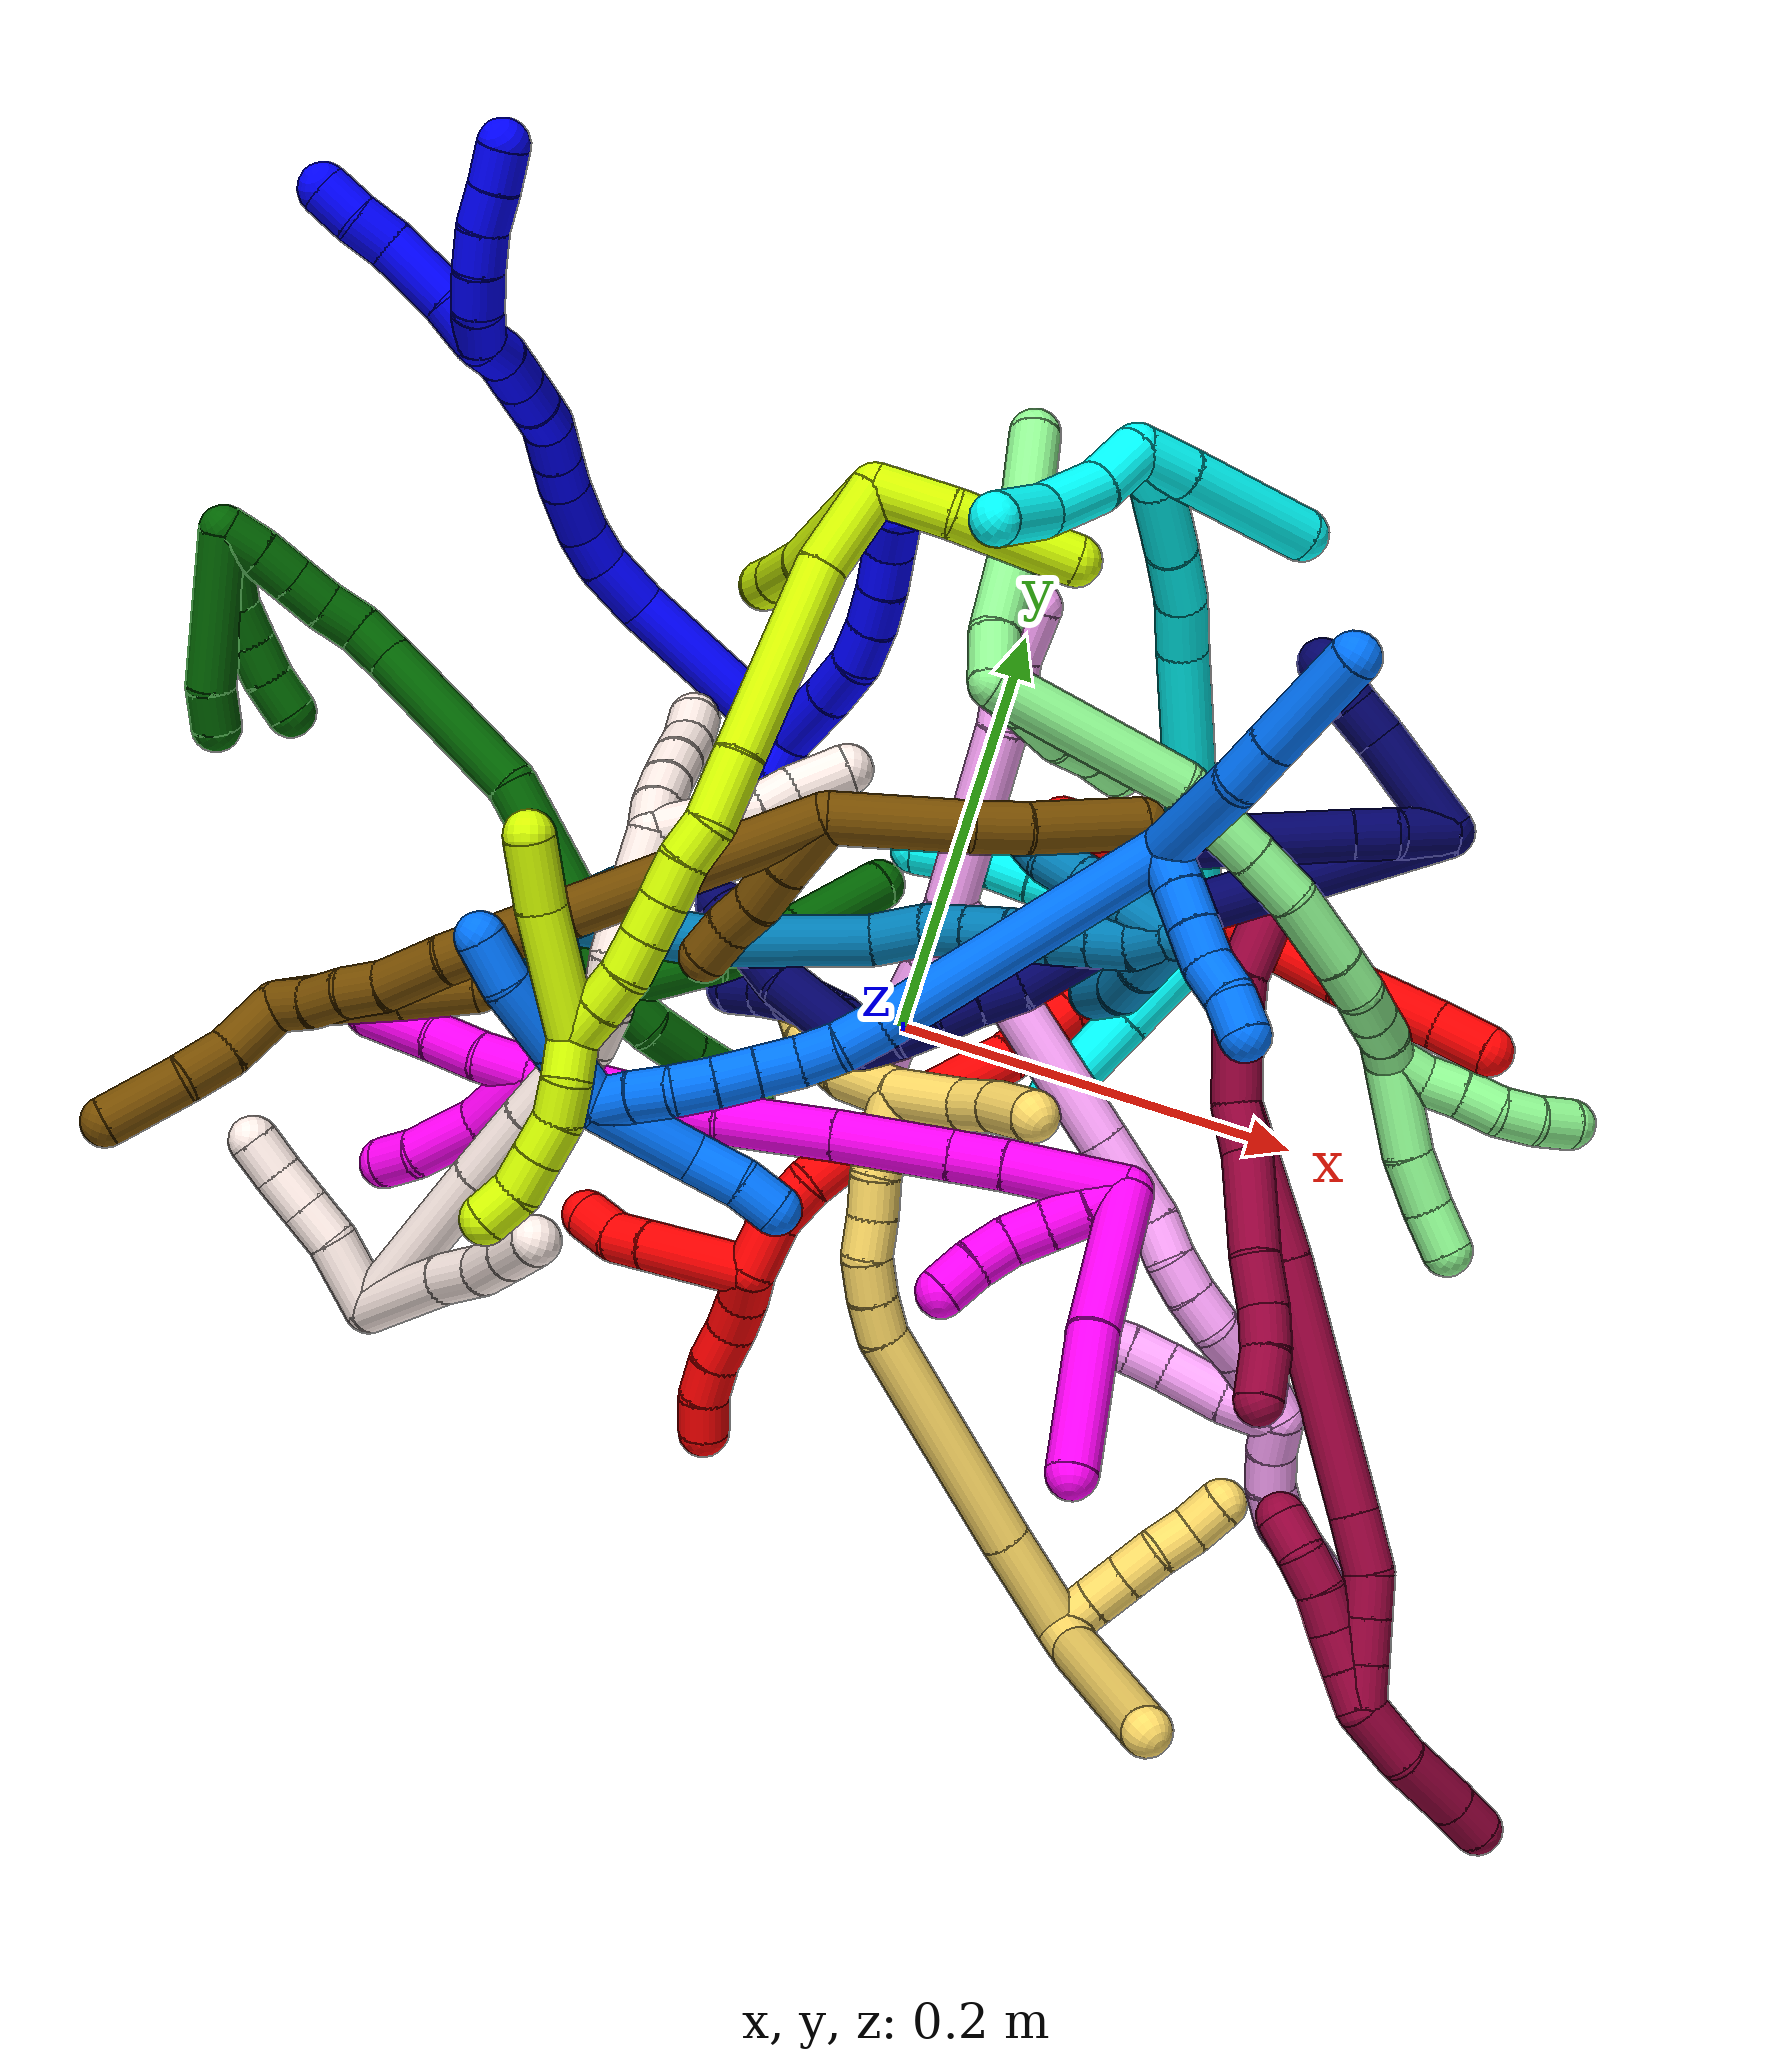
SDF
<sdf version="1.7">
 <world name="default">
  <plugin name="TubeGeneratorPlugin" filename="libtube_generator_plugin.so"/>
  <model name="photoneo_s_sensor">
   <static>1</static>
   <pose>0 0 2 1.57079 1.57079 3.14159</pose>
   <link name="link">
    <inertial><mass>0.1</mass></inertial>
    <sensor name="sensor" type="depth">
     <update_rate>30</update_rate>
     <camera>
      <horizontal_fov>1.22</horizontal_fov>
      <image><width>1920</width><height>1200</height><format>B8G8R8</format></image>
      <clip><near>0.1</near><far>4</far></clip>
      <depth_camera><output>points</output></depth_camera>
     </camera>
     <plugin name="camera_plugin" filename="libgazebo_ros_depth_camera.so">
      <baseline>0.2</baseline>
      <alwaysOn>1</alwaysOn>
      <updateRate>0.0</updateRate>
      <cameraName>camera_ir</cameraName>
      <imageTopicName>/camera/color/image_raw</imageTopicName>
      <cameraInfoTopicName>/camera/color/camera_info</cameraInfoTopicName>
      <depthImageTopicName>/camera/depth/image_raw</depthImageTopicName>
      <depthImageCameraInfoTopicName>/camera/depth/camera_info</depthImageCameraInfoTopicName>
      <pointCloudTopicName>/camera/depth/points</pointCloudTopicName>
      <frameName>fr_optical</frameName>
      <pointCloudCutoff>0.1</pointCloudCutoff>
      <pointCloudCutoffMax>2.0</pointCloudCutoffMax>
      <distortionK1>0</distortionK1>
      <distortionK2>0</distortionK2>
      <distortionK3>0</distortionK3>
      <distortionT1>0</distortionT1>
      <distortionT2>0</distortionT2>
      <CxPrime>0</CxPrime>
      <Cx>0</Cx>
      <Cy>0</Cy>
      <focalLength>0</focalLength>
      <hackBaseline>0</hackBaseline>
     </plugin>
    </sensor>
   </link>
  </model>
  <gravity>0 0 -9.8</gravity>
  <magnetic_field>6e-06 2.3e-05 -4.2e-05</magnetic_field>
  <atmosphere type="adiabatic"/>
  <physics name="default_physics" default="0" type="ode">
   <max_step_size>0.003</max_step_size>
   <real_time_factor>1</real_time_factor>
   <real_time_update_rate>1000</real_time_update_rate>
   <max_contacts>10000</max_contacts>
   <ode>
    <solver>
     <type>quick</type>
     <iters>100</iters>
     <sor>1.3</sor>
     <use_dynamic_moi_rescaling>0</use_dynamic_moi_rescaling>
    </solver>
    <constraints>
     <contact_max_correcting_vel>0</contact_max_correcting_vel>
     <contact_surface_layer>0.001</contact_surface_layer>
     <cfm>0</cfm>
     <erp>0.2</erp>
    </constraints>
   </ode>
  </physics>
  <scene><ambient>0.4 0.4 0.4 1</ambient><background>0.7 0.7 0.7 1</background><shadows>0</shadows></scene>
  <audio><device>default</device></audio>
  <spherical_coordinates>
   <surface_model>EARTH_WGS84</surface_model>
   <latitude_deg>0</latitude_deg>
   <longitude_deg>0</longitude_deg>
   <elevation>0</elevation>
   <heading_deg>0</heading_deg>
  </spherical_coordinates>
  <model name="bin">
   <static>1</static>
   <link name="bottom">
    <collision name="collision-bottom">
     <pose>0 0 -0.01 0 -0 0</pose>
     <geometry><box><size>0.8 0.6 0.02</size></box></geometry>
     <surface>
      <friction><ode><mu>100</mu><mu2>100</mu2></ode></friction>
      <contact><collide_bitmask>65535</collide_bitmask></contact>
     </surface>
    </collision>
   </link>
   <link name="west_wall">
    <collision name="collision-west_wall">
     <pose>-0.41 0 0.1 0 -0 0</pose>
     <geometry><box><size>0.02 0.6 0.2</size></box></geometry>
     <surface>
      <friction><ode><mu>100</mu><mu2>100</mu2></ode></friction>
      <contact><collide_bitmask>65535</collide_bitmask></contact>
     </surface>
    </collision>
   </link>
   <link name="east_wall">
    <collision name="collision-east_wall">
     <pose>0.41 0 0.1 0 -0 0</pose>
     <geometry><box><size>0.02 0.6 0.2</size></box></geometry>
     <surface>
      <friction><ode><mu>100</mu><mu2>100</mu2></ode></friction>
      <contact><collide_bitmask>65535</collide_bitmask></contact>
     </surface>
    </collision>
   </link>
   <link name="south_wall">
    <collision name="collision-south_wall">
     <pose>0 -0.31 0.1 0 -0 0</pose>
     <geometry><box><size>0.8 0.02 0.2</size></box></geometry>
     <surface>
      <friction><ode><mu>100</mu><mu2>100</mu2></ode></friction>
      <contact><collide_bitmask>65535</collide_bitmask></contact>
     </surface>
    </collision>
   </link>
   <link name="north_wall">
    <collision name="collision-north_wall">
     <pose>0 0.31 0.1 0 -0 0</pose>
     <geometry><box><size>0.8 0.02 0.2</size></box></geometry>
     <surface>
      <friction><ode><mu>100</mu><mu2>100</mu2></ode></friction>
      <contact><collide_bitmask>65535</collide_bitmask></contact>
     </surface>
    </collision>
   </link>
  </model>
  <model name="1">
   <static>0</static>
   <link name="1">
    <collision name="collision-cylinder-e_1_2_8">
     <pose>0.01099 0.010797 0.012185 -0.725068 0.593794 -0.231052</pose>
     <geometry><cylinder><radius>0.0125</radius><length>0.039284</length></cylinder></geometry>
     <surface>
      <friction><ode><mu>1.16</mu><mu2>1.16</mu2><slip1>0</slip1><slip2>0</slip2></ode></friction>
      <contact><ode><kp>1e+06</kp><kd>1</kd><max_vel>0</max_vel><min_depth>0.001</min_depth></ode></contact>
     </surface>
    </collision>
    <visual name="visual-cylinder-e_1_2_8">
     <pose>0.01099 0.010797 0.012185 -0.725068 0.593794 -0.231052</pose>
     <geometry><cylinder><radius>0.0125</radius><length>0.039284</length></cylinder></geometry>
     <material><ambient>0 0 1 1</ambient></material>
    </visual>
    <collision name="collision-cylinder-e_2_8_9">
     <pose>0.02879 0.028979 0.033014 -0.707017 0.539625 -0.203399</pose>
     <geometry><cylinder><radius>0.0125</radius><length>0.026507</length></cylinder></geometry>
     <surface>
      <friction><ode><mu>1.16</mu><mu2>1.16</mu2><slip1>0</slip1><slip2>0</slip2></ode></friction>
      <contact><ode><kp>1e+06</kp><kd>1</kd><max_vel>0</max_vel><min_depth>0.001</min_depth></ode></contact>
     </surface>
    </collision>
    <visual name="visual-cylinder-e_2_8_9">
     <pose>0.02879 0.028979 0.033014 -0.707017 0.539625 -0.203399</pose>
     <geometry><cylinder><radius>0.0125</radius><length>0.026507</length></cylinder></geometry>
     <material><ambient>0 0 1 1</ambient></material>
    </visual>
    <collision name="collision-cylinder-e_3_9_10">
     <pose>0.038184 0.043414 0.049789 -0.714373 0.235681 -0.088307</pose>
     <geometry><cylinder><radius>0.0125</radius><length>0.022133</length></cylinder></geometry>
     <surface>
      <friction><ode><mu>1.16</mu><mu2>1.16</mu2><slip1>0</slip1><slip2>0</slip2></ode></friction>
      <contact><ode><kp>1e+06</kp><kd>1</kd><max_vel>0</max_vel><min_depth>0.001</min_depth></ode></contact>
     </surface>
    </collision>
    <visual name="visual-cylinder-e_3_9_10">
     <pose>0.038184 0.043414 0.049789 -0.714373 0.235681 -0.088307</pose>
     <geometry><cylinder><radius>0.0125</radius><length>0.022133</length></cylinder></geometry>
     <material><ambient>0 0 1 1</ambient></material>
    </visual>
    <collision name="collision-cylinder-e_4_10_11">
     <pose>0.042317 0.056634 0.066259 -0.636895 0.14825 -0.048953</pose>
     <geometry><cylinder><radius>0.0125</radius><length>0.020981</length></cylinder></geometry>
     <surface>
      <friction><ode><mu>1.16</mu><mu2>1.16</mu2><slip1>0</slip1><slip2>0</slip2></ode></friction>
      <contact><ode><kp>1e+06</kp><kd>1</kd><max_vel>0</max_vel><min_depth>0.001</min_depth></ode></contact>
     </surface>
    </collision>
    <visual name="visual-cylinder-e_4_10_11">
     <pose>0.042317 0.056634 0.066259 -0.636895 0.14825 -0.048953</pose>
     <geometry><cylinder><radius>0.0125</radius><length>0.020981</length></cylinder></geometry>
     <material><ambient>0 0 1 1</ambient></material>
    </visual>
    <collision name="collision-cylinder-e_5_11_12">
     <pose>0.044501 0.068709 0.08309 -0.607726 0.061271 -0.019218</pose>
     <geometry><cylinder><radius>0.0125</radius><length>0.020721</length></cylinder></geometry>
     <surface>
      <friction><ode><mu>1.16</mu><mu2>1.16</mu2><slip1>0</slip1><slip2>0</slip2></ode></friction>
      <contact><ode><kp>1e+06</kp><kd>1</kd><max_vel>0</max_vel><min_depth>0.001</min_depth></ode></contact>
     </surface>
    </collision>
    <visual name="visual-cylinder-e_5_11_12">
     <pose>0.044501 0.068709 0.08309 -0.607726 0.061271 -0.019218</pose>
     <geometry><cylinder><radius>0.0125</radius><length>0.020721</length></cylinder></geometry>
     <material><ambient>0 0 1 1</ambient></material>
    </visual>
    <collision name="collision-cylinder-e_6_12_6">
     <pose>0.047618 0.078986 0.100439 -0.458438 0.246212 -0.057722</pose>
     <geometry><cylinder><radius>0.0125</radius><length>0.020375</length></cylinder></geometry>
     <surface>
      <friction><ode><mu>1.16</mu><mu2>1.16</mu2><slip1>0</slip1><slip2>0</slip2></ode></friction>
      <contact><ode><kp>1e+06</kp><kd>1</kd><max_vel>0</max_vel><min_depth>0.001</min_depth></ode></contact>
     </surface>
    </collision>
    <visual name="visual-cylinder-e_6_12_6">
     <pose>0.047618 0.078986 0.100439 -0.458438 0.246212 -0.057722</pose>
     <geometry><cylinder><radius>0.0125</radius><length>0.020375</length></cylinder></geometry>
     <material><ambient>0 0 1 1</ambient></material>
    </visual>
    <collision name="collision-cylinder-e_1_2_13">
     <pose>0.000422 -0.008786 -0.004757 2.067 0.042206 0.070825</pose>
     <geometry><cylinder><radius>0.0125</radius><length>0.02</length></cylinder></geometry>
     <surface>
      <friction><ode><mu>1.16</mu><mu2>1.16</mu2><slip1>0</slip1><slip2>0</slip2></ode></friction>
      <contact><ode><kp>1e+06</kp><kd>1</kd><max_vel>0</max_vel><min_depth>0.001</min_depth></ode></contact>
     </surface>
    </collision>
    <visual name="visual-cylinder-e_1_2_13">
     <pose>0.000422 -0.008786 -0.004757 2.067 0.042206 0.070825</pose>
     <geometry><cylinder><radius>0.0125</radius><length>0.02</length></cylinder></geometry>
     <material><ambient>0 0 1 1</ambient></material>
    </visual>
    <collision name="collision-cylinder-e_2_13_14">
     <pose>0.001968 -0.026555 -0.013762 2.01265 0.112602 0.177551</pose>
     <geometry><cylinder><radius>0.0125</radius><length>0.02</length></cylinder></geometry>
     <surface>
      <friction><ode><mu>1.16</mu><mu2>1.16</mu2><slip1>0</slip1><slip2>0</slip2></ode></friction>
      <contact><ode><kp>1e+06</kp><kd>1</kd><max_vel>0</max_vel><min_depth>0.001</min_depth></ode></contact>
     </surface>
    </collision>
    <visual name="visual-cylinder-e_2_13_14">
     <pose>0.001968 -0.026555 -0.013762 2.01265 0.112602 0.177551</pose>
     <geometry><cylinder><radius>0.0125</radius><length>0.02</length></cylinder></geometry>
     <material><ambient>0 0 1 1</ambient></material>
    </visual>
    <collision name="collision-cylinder-e_3_14_15">
     <pose>0.003328 -0.045348 -0.01993 1.76388 0.02372 0.028807</pose>
     <geometry><cylinder><radius>0.0125</radius><length>0.02</length></cylinder></geometry>
     <surface>
      <friction><ode><mu>1.16</mu><mu2>1.16</mu2><slip1>0</slip1><slip2>0</slip2></ode></friction>
      <contact><ode><kp>1e+06</kp><kd>1</kd><max_vel>0</max_vel><min_depth>0.001</min_depth></ode></contact>
     </surface>
    </collision>
    <visual name="visual-cylinder-e_3_14_15">
     <pose>0.003328 -0.045348 -0.01993 1.76388 0.02372 0.028807</pose>
     <geometry><cylinder><radius>0.0125</radius><length>0.02</length></cylinder></geometry>
     <material><ambient>0 0 1 1</ambient></material>
    </visual>
    <collision name="collision-cylinder-e_4_15_16">
     <pose>0.001082 -0.064846 -0.021939 1.58024 -0.250962 -0.253319</pose>
     <geometry><cylinder><radius>0.0125</radius><length>0.02</length></cylinder></geometry>
     <surface>
      <friction><ode><mu>1.16</mu><mu2>1.16</mu2><slip1>0</slip1><slip2>0</slip2></ode></friction>
      <contact><ode><kp>1e+06</kp><kd>1</kd><max_vel>0</max_vel><min_depth>0.001</min_depth></ode></contact>
     </surface>
    </collision>
    <visual name="visual-cylinder-e_4_15_16">
     <pose>0.001082 -0.064846 -0.021939 1.58024 -0.250962 -0.253319</pose>
     <geometry><cylinder><radius>0.0125</radius><length>0.02</length></cylinder></geometry>
     <material><ambient>0 0 1 1</ambient></material>
    </visual>
    <collision name="collision-cylinder-e_5_16_5">
     <pose>-0.003138 -0.084238 -0.020361 1.40037 -0.17452 -0.147159</pose>
     <geometry><cylinder><radius>0.0125</radius><length>0.02</length></cylinder></geometry>
     <surface>
      <friction><ode><mu>1.16</mu><mu2>1.16</mu2><slip1>0</slip1><slip2>0</slip2></ode></friction>
      <contact><ode><kp>1e+06</kp><kd>1</kd><max_vel>0</max_vel><min_depth>0.001</min_depth></ode></contact>
     </surface>
    </collision>
    <visual name="visual-cylinder-e_5_16_5">
     <pose>-0.003138 -0.084238 -0.020361 1.40037 -0.17452 -0.147159</pose>
     <geometry><cylinder><radius>0.0125</radius><length>0.02</length></cylinder></geometry>
     <material><ambient>0 0 1 1</ambient></material>
    </visual>
    <collision name="collision-cylinder-e_1_2_17">
     <pose>-0.031256 -0.005661 0.03668 0.15312 -0.699933 -0.055982</pose>
     <geometry><cylinder><radius>0.0125</radius><length>0.097045</length></cylinder></geometry>
     <surface>
      <friction><ode><mu>1.16</mu><mu2>1.16</mu2><slip1>0</slip1><slip2>0</slip2></ode></friction>
      <contact><ode><kp>1e+06</kp><kd>1</kd><max_vel>0</max_vel><min_depth>0.001</min_depth></ode></contact>
     </surface>
    </collision>
    <visual name="visual-cylinder-e_1_2_17">
     <pose>-0.031256 -0.005661 0.03668 0.15312 -0.699933 -0.055982</pose>
     <geometry><cylinder><radius>0.0125</radius><length>0.097045</length></cylinder></geometry>
     <material><ambient>0 0 1 1</ambient></material>
    </visual>
    <collision name="collision-cylinder-e_2_17_18">
     <pose>-0.068812 -0.01266 0.086407 0.10221 -0.447725 -0.02329</pose>
     <geometry><cylinder><radius>0.0125</radius><length>0.0291</length></cylinder></geometry>
     <surface>
      <friction><ode><mu>1.16</mu><mu2>1.16</mu2><slip1>0</slip1><slip2>0</slip2></ode></friction>
      <contact><ode><kp>1e+06</kp><kd>1</kd><max_vel>0</max_vel><min_depth>0.001</min_depth></ode></contact>
     </surface>
    </collision>
    <visual name="visual-cylinder-e_2_17_18">
     <pose>-0.068812 -0.01266 0.086407 0.10221 -0.447725 -0.02329</pose>
     <geometry><cylinder><radius>0.0125</radius><length>0.0291</length></cylinder></geometry>
     <material><ambient>0 0 1 1</ambient></material>
    </visual>
    <collision name="collision-cylinder-e_3_18_19">
     <pose>-0.077564 -0.013414 0.109363 -0.058833 -0.242262 0.007164</pose>
     <geometry><cylinder><radius>0.0125</radius><length>0.020449</length></cylinder></geometry>
     <surface>
      <friction><ode><mu>1.16</mu><mu2>1.16</mu2><slip1>0</slip1><slip2>0</slip2></ode></friction>
      <contact><ode><kp>1e+06</kp><kd>1</kd><max_vel>0</max_vel><min_depth>0.001</min_depth></ode></contact>
     </surface>
    </collision>
    <visual name="visual-cylinder-e_3_18_19">
     <pose>-0.077564 -0.013414 0.109363 -0.058833 -0.242262 0.007164</pose>
     <geometry><cylinder><radius>0.0125</radius><length>0.020449</length></cylinder></geometry>
     <material><ambient>0 0 1 1</ambient></material>
    </visual>
    <collision name="collision-cylinder-e_4_19_20">
     <pose>-0.080627 -0.011053 0.132975 -0.128996 -0.044151 0.002852</pose>
     <geometry><cylinder><radius>0.0125</radius><length>0.027664</length></cylinder></geometry>
     <surface>
      <friction><ode><mu>1.16</mu><mu2>1.16</mu2><slip1>0</slip1><slip2>0</slip2></ode></friction>
      <contact><ode><kp>1e+06</kp><kd>1</kd><max_vel>0</max_vel><min_depth>0.001</min_depth></ode></contact>
     </surface>
    </collision>
    <visual name="visual-cylinder-e_4_19_20">
     <pose>-0.080627 -0.011053 0.132975 -0.128996 -0.044151 0.002852</pose>
     <geometry><cylinder><radius>0.0125</radius><length>0.027664</length></cylinder></geometry>
     <material><ambient>0 0 1 1</ambient></material>
    </visual>
    <collision name="collision-cylinder-e_5_20_21">
     <pose>-0.079345 -0.008122 0.156788 -0.113622 0.18393 -0.01049</pose>
     <geometry><cylinder><radius>0.0125</radius><length>0.020698</length></cylinder></geometry>
     <surface>
      <friction><ode><mu>1.16</mu><mu2>1.16</mu2><slip1>0</slip1><slip2>0</slip2></ode></friction>
      <contact><ode><kp>1e+06</kp><kd>1</kd><max_vel>0</max_vel><min_depth>0.001</min_depth></ode></contact>
     </surface>
    </collision>
    <visual name="visual-cylinder-e_5_20_21">
     <pose>-0.079345 -0.008122 0.156788 -0.113622 0.18393 -0.01049</pose>
     <geometry><cylinder><radius>0.0125</radius><length>0.020698</length></cylinder></geometry>
     <material><ambient>0 0 1 1</ambient></material>
    </visual>
    <collision name="collision-cylinder-e_6_21_22">
     <pose>-0.075441 -0.005575 0.177951 -0.12541 0.178593 -0.011243</pose>
     <geometry><cylinder><radius>0.0125</radius><length>0.022643</length></cylinder></geometry>
     <surface>
      <friction><ode><mu>1.16</mu><mu2>1.16</mu2><slip1>0</slip1><slip2>0</slip2></ode></friction>
      <contact><ode><kp>1e+06</kp><kd>1</kd><max_vel>0</max_vel><min_depth>0.001</min_depth></ode></contact>
     </surface>
    </collision>
    <visual name="visual-cylinder-e_6_21_22">
     <pose>-0.075441 -0.005575 0.177951 -0.12541 0.178593 -0.011243</pose>
     <geometry><cylinder><radius>0.0125</radius><length>0.022643</length></cylinder></geometry>
     <material><ambient>0 0 1 1</ambient></material>
    </visual>
    <collision name="collision-cylinder-e_7_22_23">
     <pose>-0.070546 -0.00558 0.198652 0.144024 0.287605 0.02089</pose>
     <geometry><cylinder><radius>0.0125</radius><length>0.020333</length></cylinder></geometry>
     <surface>
      <friction><ode><mu>1.16</mu><mu2>1.16</mu2><slip1>0</slip1><slip2>0</slip2></ode></friction>
      <contact><ode><kp>1e+06</kp><kd>1</kd><max_vel>0</max_vel><min_depth>0.001</min_depth></ode></contact>
     </surface>
    </collision>
    <visual name="visual-cylinder-e_7_22_23">
     <pose>-0.070546 -0.00558 0.198652 0.144024 0.287605 0.02089</pose>
     <geometry><cylinder><radius>0.0125</radius><length>0.020333</length></cylinder></geometry>
     <material><ambient>0 0 1 1</ambient></material>
    </visual>
    <collision name="collision-cylinder-e_8_23_24">
     <pose>-0.06583 -0.00829 0.218251 0.130957 0.180485 0.011867</pose>
     <geometry><cylinder><radius>0.0125</radius><length>0.020405</length></cylinder></geometry>
     <surface>
      <friction><ode><mu>1.16</mu><mu2>1.16</mu2><slip1>0</slip1><slip2>0</slip2></ode></friction>
      <contact><ode><kp>1e+06</kp><kd>1</kd><max_vel>0</max_vel><min_depth>0.001</min_depth></ode></contact>
     </surface>
    </collision>
    <visual name="visual-cylinder-e_8_23_24">
     <pose>-0.06583 -0.00829 0.218251 0.130957 0.180485 0.011867</pose>
     <geometry><cylinder><radius>0.0125</radius><length>0.020405</length></cylinder></geometry>
     <material><ambient>0 0 1 1</ambient></material>
    </visual>
    <collision name="collision-cylinder-e_9_24_25">
     <pose>-0.062057 -0.010927 0.238758 0.124964 0.180559 0.011327</pose>
     <geometry><cylinder><radius>0.0125</radius><length>0.02163</length></cylinder></geometry>
     <surface>
      <friction><ode><mu>1.16</mu><mu2>1.16</mu2><slip1>0</slip1><slip2>0</slip2></ode></friction>
      <contact><ode><kp>1e+06</kp><kd>1</kd><max_vel>0</max_vel><min_depth>0.001</min_depth></ode></contact>
     </surface>
    </collision>
    <visual name="visual-cylinder-e_9_24_25">
     <pose>-0.062057 -0.010927 0.238758 0.124964 0.180559 0.011327</pose>
     <geometry><cylinder><radius>0.0125</radius><length>0.02163</length></cylinder></geometry>
     <material><ambient>0 0 1 1</ambient></material>
    </visual>
    <collision name="collision-cylinder-e_10_25_1">
     <pose>-0.058136 -0.015628 0.258536 0.35087 0.19884 0.035359</pose>
     <geometry><cylinder><radius>0.0125</radius><length>0.020034</length></cylinder></geometry>
     <surface>
      <friction><ode><mu>1.16</mu><mu2>1.16</mu2><slip1>0</slip1><slip2>0</slip2></ode></friction>
      <contact><ode><kp>1e+06</kp><kd>1</kd><max_vel>0</max_vel><min_depth>0.001</min_depth></ode></contact>
     </surface>
    </collision>
    <visual name="visual-cylinder-e_10_25_1">
     <pose>-0.058136 -0.015628 0.258536 0.35087 0.19884 0.035359</pose>
     <geometry><cylinder><radius>0.0125</radius><length>0.020034</length></cylinder></geometry>
     <material><ambient>0 0 1 1</ambient></material>
    </visual>
    <collision name="collision-cylinder-e_1_1_26">
     <pose>-0.063693 -0.018529 0.276853 -0.052066 -0.691193 0.01875</pose>
     <geometry><cylinder><radius>0.0125</radius><length>0.023644</length></cylinder></geometry>
     <surface>
      <friction><ode><mu>1.16</mu><mu2>1.16</mu2><slip1>0</slip1><slip2>0</slip2></ode></friction>
      <contact><ode><kp>1e+06</kp><kd>1</kd><max_vel>0</max_vel><min_depth>0.001</min_depth></ode></contact>
     </surface>
    </collision>
    <visual name="visual-cylinder-e_1_1_26">
     <pose>-0.063693 -0.018529 0.276853 -0.052066 -0.691193 0.01875</pose>
     <geometry><cylinder><radius>0.0125</radius><length>0.023644</length></cylinder></geometry>
     <material><ambient>0 0 1 1</ambient></material>
    </visual>
    <collision name="collision-cylinder-e_2_26_27">
     <pose>-0.084809 -0.018726 0.29795 0.055852 -0.84629 -0.025158</pose>
     <geometry><cylinder><radius>0.0125</radius><length>0.036271</length></cylinder></geometry>
     <surface>
      <friction><ode><mu>1.16</mu><mu2>1.16</mu2><slip1>0</slip1><slip2>0</slip2></ode></friction>
      <contact><ode><kp>1e+06</kp><kd>1</kd><max_vel>0</max_vel><min_depth>0.001</min_depth></ode></contact>
     </surface>
    </collision>
    <visual name="visual-cylinder-e_2_26_27">
     <pose>-0.084809 -0.018726 0.29795 0.055852 -0.84629 -0.025158</pose>
     <geometry><cylinder><radius>0.0125</radius><length>0.036271</length></cylinder></geometry>
     <material><ambient>0 0 1 1</ambient></material>
    </visual>
    <collision name="collision-cylinder-e_3_27_28">
     <pose>-0.104733 -0.021557 0.317425 0.281279 -0.684067 -0.100723</pose>
     <geometry><cylinder><radius>0.0125</radius><length>0.020077</length></cylinder></geometry>
     <surface>
      <friction><ode><mu>1.16</mu><mu2>1.16</mu2><slip1>0</slip1><slip2>0</slip2></ode></friction>
      <contact><ode><kp>1e+06</kp><kd>1</kd><max_vel>0</max_vel><min_depth>0.001</min_depth></ode></contact>
     </surface>
    </collision>
    <visual name="visual-cylinder-e_3_27_28">
     <pose>-0.104733 -0.021557 0.317425 0.281279 -0.684067 -0.100723</pose>
     <geometry><cylinder><radius>0.0125</radius><length>0.020077</length></cylinder></geometry>
     <material><ambient>0 0 1 1</ambient></material>
    </visual>
    <collision name="collision-cylinder-e_4_28_4">
     <pose>-0.118393 -0.024524 0.331675 0.118702 -0.82021 -0.051655</pose>
     <geometry><cylinder><radius>0.0125</radius><length>0.020009</length></cylinder></geometry>
     <surface>
      <friction><ode><mu>1.16</mu><mu2>1.16</mu2><slip1>0</slip1><slip2>0</slip2></ode></friction>
      <contact><ode><kp>1e+06</kp><kd>1</kd><max_vel>0</max_vel><min_depth>0.001</min_depth></ode></contact>
     </surface>
    </collision>
    <visual name="visual-cylinder-e_4_28_4">
     <pose>-0.118393 -0.024524 0.331675 0.118702 -0.82021 -0.051655</pose>
     <geometry><cylinder><radius>0.0125</radius><length>0.020009</length></cylinder></geometry>
     <material><ambient>0 0 1 1</ambient></material>
    </visual>
    <collision name="collision-cylinder-e_1_1_29">
     <pose>-0.053554 -0.016558 0.277098 -0.256031 0.263327 -0.034089</pose>
     <geometry><cylinder><radius>0.0125</radius><length>0.02</length></cylinder></geometry>
     <surface>
      <friction><ode><mu>1.16</mu><mu2>1.16</mu2><slip1>0</slip1><slip2>0</slip2></ode></friction>
      <contact><ode><kp>1e+06</kp><kd>1</kd><max_vel>0</max_vel><min_depth>0.001</min_depth></ode></contact>
     </surface>
    </collision>
    <visual name="visual-cylinder-e_1_1_29">
     <pose>-0.053554 -0.016558 0.277098 -0.256031 0.263327 -0.034089</pose>
     <geometry><cylinder><radius>0.0125</radius><length>0.02</length></cylinder></geometry>
     <material><ambient>0 0 1 1</ambient></material>
    </visual>
    <collision name="collision-cylinder-e_2_29_30">
     <pose>-0.050459 -0.009434 0.295262 -0.487545 0.049296 -0.012263</pose>
     <geometry><cylinder><radius>0.0125</radius><length>0.02</length></cylinder></geometry>
     <surface>
      <friction><ode><mu>1.16</mu><mu2>1.16</mu2><slip1>0</slip1><slip2>0</slip2></ode></friction>
      <contact><ode><kp>1e+06</kp><kd>1</kd><max_vel>0</max_vel><min_depth>0.001</min_depth></ode></contact>
     </surface>
    </collision>
    <visual name="visual-cylinder-e_2_29_30">
     <pose>-0.050459 -0.009434 0.295262 -0.487545 0.049296 -0.012263</pose>
     <geometry><cylinder><radius>0.0125</radius><length>0.02</length></cylinder></geometry>
     <material><ambient>0 0 1 1</ambient></material>
    </visual>
    <collision name="collision-cylinder-e_3_30_31">
     <pose>-0.0501 0.001052 0.312226 -0.619659 -0.013375 0.004282</pose>
     <geometry><cylinder><radius>0.0125</radius><length>0.02</length></cylinder></geometry>
     <surface>
      <friction><ode><mu>1.16</mu><mu2>1.16</mu2><slip1>0</slip1><slip2>0</slip2></ode></friction>
      <contact><ode><kp>1e+06</kp><kd>1</kd><max_vel>0</max_vel><min_depth>0.001</min_depth></ode></contact>
     </surface>
    </collision>
    <visual name="visual-cylinder-e_3_30_31">
     <pose>-0.0501 0.001052 0.312226 -0.619659 -0.013375 0.004282</pose>
     <geometry><cylinder><radius>0.0125</radius><length>0.02</length></cylinder></geometry>
     <material><ambient>0 0 1 1</ambient></material>
    </visual>
    <collision name="collision-cylinder-e_4_31_32">
     <pose>-0.049512 0.01372 0.327605 -0.758629 0.072183 -0.028784</pose>
     <geometry><cylinder><radius>0.0125</radius><length>0.02</length></cylinder></geometry>
     <surface>
      <friction><ode><mu>1.16</mu><mu2>1.16</mu2><slip1>0</slip1><slip2>0</slip2></ode></friction>
      <contact><ode><kp>1e+06</kp><kd>1</kd><max_vel>0</max_vel><min_depth>0.001</min_depth></ode></contact>
     </surface>
    </collision>
    <visual name="visual-cylinder-e_4_31_32">
     <pose>-0.049512 0.01372 0.327605 -0.758629 0.072183 -0.028784</pose>
     <geometry><cylinder><radius>0.0125</radius><length>0.02</length></cylinder></geometry>
     <material><ambient>0 0 1 1</ambient></material>
    </visual>
    <collision name="collision-cylinder-e_5_32_3">
     <pose>-0.048738 0.027391 0.342167 -0.749132 0.005321 -0.002092</pose>
     <geometry><cylinder><radius>0.0125</radius><length>0.02</length></cylinder></geometry>
     <surface>
      <friction><ode><mu>1.16</mu><mu2>1.16</mu2><slip1>0</slip1><slip2>0</slip2></ode></friction>
      <contact><ode><kp>1e+06</kp><kd>1</kd><max_vel>0</max_vel><min_depth>0.001</min_depth></ode></contact>
     </surface>
    </collision>
    <visual name="visual-cylinder-e_5_32_3">
     <pose>-0.048738 0.027391 0.342167 -0.749132 0.005321 -0.002092</pose>
     <geometry><cylinder><radius>0.0125</radius><length>0.02</length></cylinder></geometry>
     <material><ambient>0 0 1 1</ambient></material>
    </visual>
    <collision name="collision-sphere-3">
     <pose>-0.048685 0.034201 0.34949 0 -0 0</pose>
     <geometry><sphere><radius>0.0125</radius></sphere></geometry>
     <surface>
      <friction><ode><mu>1.16</mu><mu2>1.16</mu2><slip1>0</slip1><slip2>0</slip2></ode></friction>
      <contact><ode><kp>1e+06</kp><kd>1</kd><max_vel>0</max_vel><min_depth>0.001</min_depth></ode></contact>
     </surface>
    </collision>
    <visual name="visual-sphere-3">
     <pose>-0.048685 0.034201 0.34949 0 -0 0</pose>
     <geometry><sphere><radius>0.0125</radius></sphere></geometry>
     <material><ambient>0 0 1 1</ambient></material>
    </visual>
    <collision name="collision-sphere-32">
     <pose>-0.048791 0.020581 0.334844 0 -0 0</pose>
     <geometry><sphere><radius>0.0125</radius></sphere></geometry>
     <surface>
      <friction><ode><mu>1.16</mu><mu2>1.16</mu2><slip1>0</slip1><slip2>0</slip2></ode></friction>
      <contact><ode><kp>1e+06</kp><kd>1</kd><max_vel>0</max_vel><min_depth>0.001</min_depth></ode></contact>
     </surface>
    </collision>
    <visual name="visual-sphere-32">
     <pose>-0.048791 0.020581 0.334844 0 -0 0</pose>
     <geometry><sphere><radius>0.0125</radius></sphere></geometry>
     <material><ambient>0 0 1 1</ambient></material>
    </visual>
    <collision name="collision-sphere-31">
     <pose>-0.050233 0.006859 0.320366 0 -0 0</pose>
     <geometry><sphere><radius>0.0125</radius></sphere></geometry>
     <surface>
      <friction><ode><mu>1.16</mu><mu2>1.16</mu2><slip1>0</slip1><slip2>0</slip2></ode></friction>
      <contact><ode><kp>1e+06</kp><kd>1</kd><max_vel>0</max_vel><min_depth>0.001</min_depth></ode></contact>
     </surface>
    </collision>
    <visual name="visual-sphere-31">
     <pose>-0.050233 0.006859 0.320366 0 -0 0</pose>
     <geometry><sphere><radius>0.0125</radius></sphere></geometry>
     <material><ambient>0 0 1 1</ambient></material>
    </visual>
    <collision name="collision-sphere-30">
     <pose>-0.049966 -0.004755 0.304086 0 -0 0</pose>
     <geometry><sphere><radius>0.0125</radius></sphere></geometry>
     <surface>
      <friction><ode><mu>1.16</mu><mu2>1.16</mu2><slip1>0</slip1><slip2>0</slip2></ode></friction>
      <contact><ode><kp>1e+06</kp><kd>1</kd><max_vel>0</max_vel><min_depth>0.001</min_depth></ode></contact>
     </surface>
    </collision>
    <visual name="visual-sphere-30">
     <pose>-0.049966 -0.004755 0.304086 0 -0 0</pose>
     <geometry><sphere><radius>0.0125</radius></sphere></geometry>
     <material><ambient>0 0 1 1</ambient></material>
    </visual>
    <collision name="collision-sphere-29">
     <pose>-0.050951 -0.014113 0.286438 0 -0 0</pose>
     <geometry><sphere><radius>0.0125</radius></sphere></geometry>
     <surface>
      <friction><ode><mu>1.16</mu><mu2>1.16</mu2><slip1>0</slip1><slip2>0</slip2></ode></friction>
      <contact><ode><kp>1e+06</kp><kd>1</kd><max_vel>0</max_vel><min_depth>0.001</min_depth></ode></contact>
     </surface>
    </collision>
    <visual name="visual-sphere-29">
     <pose>-0.050951 -0.014113 0.286438 0 -0 0</pose>
     <geometry><sphere><radius>0.0125</radius></sphere></geometry>
     <material><ambient>0 0 1 1</ambient></material>
    </visual>
    <collision name="collision-sphere-4">
     <pose>-0.125709 -0.025333 0.33845 0 -0 0</pose>
     <geometry><sphere><radius>0.0125</radius></sphere></geometry>
     <surface>
      <friction><ode><mu>1.16</mu><mu2>1.16</mu2><slip1>0</slip1><slip2>0</slip2></ode></friction>
      <contact><ode><kp>1e+06</kp><kd>1</kd><max_vel>0</max_vel><min_depth>0.001</min_depth></ode></contact>
     </surface>
    </collision>
    <visual name="visual-sphere-4">
     <pose>-0.125709 -0.025333 0.33845 0 -0 0</pose>
     <geometry><sphere><radius>0.0125</radius></sphere></geometry>
     <material><ambient>0 0 1 1</ambient></material>
    </visual>
    <collision name="collision-sphere-28">
     <pose>-0.111077 -0.023716 0.324899 0 -0 0</pose>
     <geometry><sphere><radius>0.0125</radius></sphere></geometry>
     <surface>
      <friction><ode><mu>1.16</mu><mu2>1.16</mu2><slip1>0</slip1><slip2>0</slip2></ode></friction>
      <contact><ode><kp>1e+06</kp><kd>1</kd><max_vel>0</max_vel><min_depth>0.001</min_depth></ode></contact>
     </surface>
    </collision>
    <visual name="visual-sphere-28">
     <pose>-0.111077 -0.023716 0.324899 0 -0 0</pose>
     <geometry><sphere><radius>0.0125</radius></sphere></geometry>
     <material><ambient>0 0 1 1</ambient></material>
    </visual>
    <collision name="collision-sphere-27">
     <pose>-0.09839 -0.019397 0.309951 0 -0 0</pose>
     <geometry><sphere><radius>0.0125</radius></sphere></geometry>
     <surface>
      <friction><ode><mu>1.16</mu><mu2>1.16</mu2><slip1>0</slip1><slip2>0</slip2></ode></friction>
      <contact><ode><kp>1e+06</kp><kd>1</kd><max_vel>0</max_vel><min_depth>0.001</min_depth></ode></contact>
     </surface>
    </collision>
    <visual name="visual-sphere-27">
     <pose>-0.09839 -0.019397 0.309951 0 -0 0</pose>
     <geometry><sphere><radius>0.0125</radius></sphere></geometry>
     <material><ambient>0 0 1 1</ambient></material>
    </visual>
    <collision name="collision-sphere-26">
     <pose>-0.071229 -0.018055 0.285949 0 -0 0</pose>
     <geometry><sphere><radius>0.0125</radius></sphere></geometry>
     <surface>
      <friction><ode><mu>1.16</mu><mu2>1.16</mu2><slip1>0</slip1><slip2>0</slip2></ode></friction>
      <contact><ode><kp>1e+06</kp><kd>1</kd><max_vel>0</max_vel><min_depth>0.001</min_depth></ode></contact>
     </surface>
    </collision>
    <visual name="visual-sphere-26">
     <pose>-0.071229 -0.018055 0.285949 0 -0 0</pose>
     <geometry><sphere><radius>0.0125</radius></sphere></geometry>
     <material><ambient>0 0 1 1</ambient></material>
    </visual>
    <collision name="collision-sphere-1">
     <pose>-0.056157 -0.019003 0.267757 0 -0 0</pose>
     <geometry><sphere><radius>0.0125</radius></sphere></geometry>
     <surface>
      <friction><ode><mu>1.16</mu><mu2>1.16</mu2><slip1>0</slip1><slip2>0</slip2></ode></friction>
      <contact><ode><kp>1e+06</kp><kd>1</kd><max_vel>0</max_vel><min_depth>0.001</min_depth></ode></contact>
     </surface>
    </collision>
    <visual name="visual-sphere-1">
     <pose>-0.056157 -0.019003 0.267757 0 -0 0</pose>
     <geometry><sphere><radius>0.0125</radius></sphere></geometry>
     <material><ambient>0 0 1 1</ambient></material>
    </visual>
    <collision name="collision-sphere-25">
     <pose>-0.060115 -0.012253 0.249314 0 -0 0</pose>
     <geometry><sphere><radius>0.0125</radius></sphere></geometry>
     <surface>
      <friction><ode><mu>1.16</mu><mu2>1.16</mu2><slip1>0</slip1><slip2>0</slip2></ode></friction>
      <contact><ode><kp>1e+06</kp><kd>1</kd><max_vel>0</max_vel><min_depth>0.001</min_depth></ode></contact>
     </surface>
    </collision>
    <visual name="visual-sphere-25">
     <pose>-0.060115 -0.012253 0.249314 0 -0 0</pose>
     <geometry><sphere><radius>0.0125</radius></sphere></geometry>
     <material><ambient>0 0 1 1</ambient></material>
    </visual>
    <collision name="collision-sphere-24">
     <pose>-0.063999 -0.009601 0.228202 0 -0 0</pose>
     <geometry><sphere><radius>0.0125</radius></sphere></geometry>
     <surface>
      <friction><ode><mu>1.16</mu><mu2>1.16</mu2><slip1>0</slip1><slip2>0</slip2></ode></friction>
      <contact><ode><kp>1e+06</kp><kd>1</kd><max_vel>0</max_vel><min_depth>0.001</min_depth></ode></contact>
     </surface>
    </collision>
    <visual name="visual-sphere-24">
     <pose>-0.063999 -0.009601 0.228202 0 -0 0</pose>
     <geometry><sphere><radius>0.0125</radius></sphere></geometry>
     <material><ambient>0 0 1 1</ambient></material>
    </visual>
    <collision name="collision-sphere-23">
     <pose>-0.067662 -0.00698 0.2083 0 -0 0</pose>
     <geometry><sphere><radius>0.0125</radius></sphere></geometry>
     <surface>
      <friction><ode><mu>1.16</mu><mu2>1.16</mu2><slip1>0</slip1><slip2>0</slip2></ode></friction>
      <contact><ode><kp>1e+06</kp><kd>1</kd><max_vel>0</max_vel><min_depth>0.001</min_depth></ode></contact>
     </surface>
    </collision>
    <visual name="visual-sphere-23">
     <pose>-0.067662 -0.00698 0.2083 0 -0 0</pose>
     <geometry><sphere><radius>0.0125</radius></sphere></geometry>
     <material><ambient>0 0 1 1</ambient></material>
    </visual>
    <collision name="collision-sphere-22">
     <pose>-0.073429 -0.004181 0.189004 0 -0 0</pose>
     <geometry><sphere><radius>0.0125</radius></sphere></geometry>
     <surface>
      <friction><ode><mu>1.16</mu><mu2>1.16</mu2><slip1>0</slip1><slip2>0</slip2></ode></friction>
      <contact><ode><kp>1e+06</kp><kd>1</kd><max_vel>0</max_vel><min_depth>0.001</min_depth></ode></contact>
     </surface>
    </collision>
    <visual name="visual-sphere-22">
     <pose>-0.073429 -0.004181 0.189004 0 -0 0</pose>
     <geometry><sphere><radius>0.0125</radius></sphere></geometry>
     <material><ambient>0 0 1 1</ambient></material>
    </visual>
    <collision name="collision-sphere-21">
     <pose>-0.077452 -0.006968 0.166897 0 -0 0</pose>
     <geometry><sphere><radius>0.0125</radius></sphere></geometry>
     <surface>
      <friction><ode><mu>1.16</mu><mu2>1.16</mu2><slip1>0</slip1><slip2>0</slip2></ode></friction>
      <contact><ode><kp>1e+06</kp><kd>1</kd><max_vel>0</max_vel><min_depth>0.001</min_depth></ode></contact>
     </surface>
    </collision>
    <visual name="visual-sphere-21">
     <pose>-0.077452 -0.006968 0.166897 0 -0 0</pose>
     <geometry><sphere><radius>0.0125</radius></sphere></geometry>
     <material><ambient>0 0 1 1</ambient></material>
    </visual>
    <collision name="collision-sphere-12">
     <pose>0.045135 0.074614 0.091579 0 -0 0</pose>
     <geometry><sphere><radius>0.0125</radius></sphere></geometry>
     <surface>
      <friction><ode><mu>1.16</mu><mu2>1.16</mu2><slip1>0</slip1><slip2>0</slip2></ode></friction>
      <contact><ode><kp>1e+06</kp><kd>1</kd><max_vel>0</max_vel><min_depth>0.001</min_depth></ode></contact>
     </surface>
    </collision>
    <visual name="visual-sphere-12">
     <pose>0.045135 0.074614 0.091579 0 -0 0</pose>
     <geometry><sphere><radius>0.0125</radius></sphere></geometry>
     <material><ambient>0 0 1 1</ambient></material>
    </visual>
    <collision name="collision-sphere-11">
     <pose>0.043867 0.062804 0.074601 0 -0 0</pose>
     <geometry><sphere><radius>0.0125</radius></sphere></geometry>
     <surface>
      <friction><ode><mu>1.16</mu><mu2>1.16</mu2><slip1>0</slip1><slip2>0</slip2></ode></friction>
      <contact><ode><kp>1e+06</kp><kd>1</kd><max_vel>0</max_vel><min_depth>0.001</min_depth></ode></contact>
     </surface>
    </collision>
    <visual name="visual-sphere-11">
     <pose>0.043867 0.062804 0.074601 0 -0 0</pose>
     <geometry><sphere><radius>0.0125</radius></sphere></geometry>
     <material><ambient>0 0 1 1</ambient></material>
    </visual>
    <collision name="collision-sphere-10">
     <pose>0.040768 0.050464 0.057918 0 -0 0</pose>
     <geometry><sphere><radius>0.0125</radius></sphere></geometry>
     <surface>
      <friction><ode><mu>1.16</mu><mu2>1.16</mu2><slip1>0</slip1><slip2>0</slip2></ode></friction>
      <contact><ode><kp>1e+06</kp><kd>1</kd><max_vel>0</max_vel><min_depth>0.001</min_depth></ode></contact>
     </surface>
    </collision>
    <visual name="visual-sphere-10">
     <pose>0.040768 0.050464 0.057918 0 -0 0</pose>
     <geometry><sphere><radius>0.0125</radius></sphere></geometry>
     <material><ambient>0 0 1 1</ambient></material>
    </visual>
    <collision name="collision-sphere-9">
     <pose>0.035599 0.036364 0.041659 0 -0 0</pose>
     <geometry><sphere><radius>0.0125</radius></sphere></geometry>
     <surface>
      <friction><ode><mu>1.16</mu><mu2>1.16</mu2><slip1>0</slip1><slip2>0</slip2></ode></friction>
      <contact><ode><kp>1e+06</kp><kd>1</kd><max_vel>0</max_vel><min_depth>0.001</min_depth></ode></contact>
     </surface>
    </collision>
    <visual name="visual-sphere-9">
     <pose>0.035599 0.036364 0.041659 0 -0 0</pose>
     <geometry><sphere><radius>0.0125</radius></sphere></geometry>
     <material><ambient>0 0 1 1</ambient></material>
    </visual>
    <collision name="collision-sphere-2">
     <geometry><sphere><radius>0.0125</radius></sphere></geometry>
     <surface>
      <friction><ode><mu>1.16</mu><mu2>1.16</mu2><slip1>0</slip1><slip2>0</slip2></ode></friction>
      <contact><ode><kp>1e+06</kp><kd>1</kd><max_vel>0</max_vel><min_depth>0.001</min_depth></ode></contact>
     </surface>
    </collision>
    <visual name="visual-sphere-2">
     <geometry><sphere><radius>0.0125</radius></sphere></geometry>
     <material><ambient>0 0 1 1</ambient></material>
    </visual>
    <collision name="collision-sphere-19">
     <pose>-0.080016 -0.012831 0.119272 0 -0 0</pose>
     <geometry><sphere><radius>0.0125</radius></sphere></geometry>
     <surface>
      <friction><ode><mu>1.16</mu><mu2>1.16</mu2><slip1>0</slip1><slip2>0</slip2></ode></friction>
      <contact><ode><kp>1e+06</kp><kd>1</kd><max_vel>0</max_vel><min_depth>0.001</min_depth></ode></contact>
     </surface>
    </collision>
    <visual name="visual-sphere-19">
     <pose>-0.080016 -0.012831 0.119272 0 -0 0</pose>
     <geometry><sphere><radius>0.0125</radius></sphere></geometry>
     <material><ambient>0 0 1 1</ambient></material>
    </visual>
    <collision name="collision-sphere-8">
     <pose>0.02198 0.021593 0.024369 0 -0 0</pose>
     <geometry><sphere><radius>0.0125</radius></sphere></geometry>
     <surface>
      <friction><ode><mu>1.16</mu><mu2>1.16</mu2><slip1>0</slip1><slip2>0</slip2></ode></friction>
      <contact><ode><kp>1e+06</kp><kd>1</kd><max_vel>0</max_vel><min_depth>0.001</min_depth></ode></contact>
     </surface>
    </collision>
    <visual name="visual-sphere-8">
     <pose>0.02198 0.021593 0.024369 0 -0 0</pose>
     <geometry><sphere><radius>0.0125</radius></sphere></geometry>
     <material><ambient>0 0 1 1</ambient></material>
    </visual>
    <collision name="collision-sphere-6">
     <pose>0.050101 0.083358 0.109299 0 -0 0</pose>
     <geometry><sphere><radius>0.0125</radius></sphere></geometry>
     <surface>
      <friction><ode><mu>1.16</mu><mu2>1.16</mu2><slip1>0</slip1><slip2>0</slip2></ode></friction>
      <contact><ode><kp>1e+06</kp><kd>1</kd><max_vel>0</max_vel><min_depth>0.001</min_depth></ode></contact>
     </surface>
    </collision>
    <visual name="visual-sphere-6">
     <pose>0.050101 0.083358 0.109299 0 -0 0</pose>
     <geometry><sphere><radius>0.0125</radius></sphere></geometry>
     <material><ambient>0 0 1 1</ambient></material>
    </visual>
    <collision name="collision-sphere-13">
     <pose>0.000844 -0.017572 -0.009513 0 -0 0</pose>
     <geometry><sphere><radius>0.0125</radius></sphere></geometry>
     <surface>
      <friction><ode><mu>1.16</mu><mu2>1.16</mu2><slip1>0</slip1><slip2>0</slip2></ode></friction>
      <contact><ode><kp>1e+06</kp><kd>1</kd><max_vel>0</max_vel><min_depth>0.001</min_depth></ode></contact>
     </surface>
    </collision>
    <visual name="visual-sphere-13">
     <pose>0.000844 -0.017572 -0.009513 0 -0 0</pose>
     <geometry><sphere><radius>0.0125</radius></sphere></geometry>
     <material><ambient>0 0 1 1</ambient></material>
    </visual>
    <collision name="collision-sphere-14">
     <pose>0.003091 -0.035537 -0.018011 0 -0 0</pose>
     <geometry><sphere><radius>0.0125</radius></sphere></geometry>
     <surface>
      <friction><ode><mu>1.16</mu><mu2>1.16</mu2><slip1>0</slip1><slip2>0</slip2></ode></friction>
      <contact><ode><kp>1e+06</kp><kd>1</kd><max_vel>0</max_vel><min_depth>0.001</min_depth></ode></contact>
     </surface>
    </collision>
    <visual name="visual-sphere-14">
     <pose>0.003091 -0.035537 -0.018011 0 -0 0</pose>
     <geometry><sphere><radius>0.0125</radius></sphere></geometry>
     <material><ambient>0 0 1 1</ambient></material>
    </visual>
    <collision name="collision-sphere-15">
     <pose>0.003566 -0.05516 -0.021848 0 -0 0</pose>
     <geometry><sphere><radius>0.0125</radius></sphere></geometry>
     <surface>
      <friction><ode><mu>1.16</mu><mu2>1.16</mu2><slip1>0</slip1><slip2>0</slip2></ode></friction>
      <contact><ode><kp>1e+06</kp><kd>1</kd><max_vel>0</max_vel><min_depth>0.001</min_depth></ode></contact>
     </surface>
    </collision>
    <visual name="visual-sphere-15">
     <pose>0.003566 -0.05516 -0.021848 0 -0 0</pose>
     <geometry><sphere><radius>0.0125</radius></sphere></geometry>
     <material><ambient>0 0 1 1</ambient></material>
    </visual>
    <collision name="collision-sphere-16">
     <pose>-0.001401 -0.074532 -0.022031 0 -0 0</pose>
     <geometry><sphere><radius>0.0125</radius></sphere></geometry>
     <surface>
      <friction><ode><mu>1.16</mu><mu2>1.16</mu2><slip1>0</slip1><slip2>0</slip2></ode></friction>
      <contact><ode><kp>1e+06</kp><kd>1</kd><max_vel>0</max_vel><min_depth>0.001</min_depth></ode></contact>
     </surface>
    </collision>
    <visual name="visual-sphere-16">
     <pose>-0.001401 -0.074532 -0.022031 0 -0 0</pose>
     <geometry><sphere><radius>0.0125</radius></sphere></geometry>
     <material><ambient>0 0 1 1</ambient></material>
    </visual>
    <collision name="collision-sphere-5">
     <pose>-0.004874 -0.093943 -0.01869 0 -0 0</pose>
     <geometry><sphere><radius>0.0125</radius></sphere></geometry>
     <surface>
      <friction><ode><mu>1.16</mu><mu2>1.16</mu2><slip1>0</slip1><slip2>0</slip2></ode></friction>
      <contact><ode><kp>1e+06</kp><kd>1</kd><max_vel>0</max_vel><min_depth>0.001</min_depth></ode></contact>
     </surface>
    </collision>
    <visual name="visual-sphere-5">
     <pose>-0.004874 -0.093943 -0.01869 0 -0 0</pose>
     <geometry><sphere><radius>0.0125</radius></sphere></geometry>
     <material><ambient>0 0 1 1</ambient></material>
    </visual>
    <collision name="collision-sphere-17">
     <pose>-0.062513 -0.011321 0.073359 0 -0 0</pose>
     <geometry><sphere><radius>0.0125</radius></sphere></geometry>
     <surface>
      <friction><ode><mu>1.16</mu><mu2>1.16</mu2><slip1>0</slip1><slip2>0</slip2></ode></friction>
      <contact><ode><kp>1e+06</kp><kd>1</kd><max_vel>0</max_vel><min_depth>0.001</min_depth></ode></contact>
     </surface>
    </collision>
    <visual name="visual-sphere-17">
     <pose>-0.062513 -0.011321 0.073359 0 -0 0</pose>
     <geometry><sphere><radius>0.0125</radius></sphere></geometry>
     <material><ambient>0 0 1 1</ambient></material>
    </visual>
    <collision name="collision-sphere-18">
     <pose>-0.075111 -0.013998 0.099454 0 -0 0</pose>
     <geometry><sphere><radius>0.0125</radius></sphere></geometry>
     <surface>
      <friction><ode><mu>1.16</mu><mu2>1.16</mu2><slip1>0</slip1><slip2>0</slip2></ode></friction>
      <contact><ode><kp>1e+06</kp><kd>1</kd><max_vel>0</max_vel><min_depth>0.001</min_depth></ode></contact>
     </surface>
    </collision>
    <visual name="visual-sphere-18">
     <pose>-0.075111 -0.013998 0.099454 0 -0 0</pose>
     <geometry><sphere><radius>0.0125</radius></sphere></geometry>
     <material><ambient>0 0 1 1</ambient></material>
    </visual>
    <collision name="collision-sphere-20">
     <pose>-0.081237 -0.009276 0.146679 0 -0 0</pose>
     <geometry><sphere><radius>0.0125</radius></sphere></geometry>
     <surface>
      <friction><ode><mu>1.16</mu><mu2>1.16</mu2><slip1>0</slip1><slip2>0</slip2></ode></friction>
      <contact><ode><kp>1e+06</kp><kd>1</kd><max_vel>0</max_vel><min_depth>0.001</min_depth></ode></contact>
     </surface>
    </collision>
    <visual name="visual-sphere-20">
     <pose>-0.081237 -0.009276 0.146679 0 -0 0</pose>
     <geometry><sphere><radius>0.0125</radius></sphere></geometry>
     <material><ambient>0 0 1 1</ambient></material>
    </visual>
    <inertial>
     <pose>-0.035593 -0.003417 0.140731 0 -0 0</pose>
     <mass>0.75</mass>
     <inertia>
      <ixx>0.000101</ixx>
      <ixy>0</ixy>
      <ixz>0</ixz>
      <iyy>0.000119</iyy>
      <iyz>0</iyz>
      <izz>9.7e-05</izz>
     </inertia>
    </inertial>
   </link>
   <pose>-0.096156 0.116836 0.014572 -0.302147 -0.732469 -0.309603</pose>
  </model>
  <model name="2">
   <static>0</static>
   <link name="2">
    <collision name="collision-cylinder-e_1_2_8">
     <pose>0.026572 -0.009413 -0.020145 2.70449 0.87402 2.25396</pose>
     <geometry><cylinder><radius>0.0125</radius><length>0.069297</length></cylinder></geometry>
     <surface>
      <friction><ode><mu>1.16</mu><mu2>1.16</mu2><slip1>0</slip1><slip2>0</slip2></ode></friction>
      <contact><ode><kp>1e+06</kp><kd>1</kd><max_vel>0</max_vel><min_depth>0.001</min_depth></ode></contact>
     </surface>
    </collision>
    <visual name="visual-cylinder-e_1_2_8">
     <pose>0.026572 -0.009413 -0.020145 2.70449 0.87402 2.25396</pose>
     <geometry><cylinder><radius>0.0125</radius><length>0.069297</length></cylinder></geometry>
     <material><ambient>1 0 0 1</ambient></material>
    </visual>
    <collision name="collision-cylinder-e_2_8_9">
     <pose>0.072066 -0.023792 -0.057892 2.86657 0.802378 2.5109</pose>
     <geometry><cylinder><radius>0.0125</radius><length>0.052631</length></cylinder></geometry>
     <surface>
      <friction><ode><mu>1.16</mu><mu2>1.16</mu2><slip1>0</slip1><slip2>0</slip2></ode></friction>
      <contact><ode><kp>1e+06</kp><kd>1</kd><max_vel>0</max_vel><min_depth>0.001</min_depth></ode></contact>
     </surface>
    </collision>
    <visual name="visual-cylinder-e_2_8_9">
     <pose>0.072066 -0.023792 -0.057892 2.86657 0.802378 2.5109</pose>
     <geometry><cylinder><radius>0.0125</radius><length>0.052631</length></cylinder></geometry>
     <material><ambient>1 0 0 1</ambient></material>
    </visual>
    <collision name="collision-cylinder-e_3_9_6">
     <pose>0.101583 -0.032082 -0.084078 2.77226 0.85551 2.36388</pose>
     <geometry><cylinder><radius>0.0125</radius><length>0.028072</length></cylinder></geometry>
     <surface>
      <friction><ode><mu>1.16</mu><mu2>1.16</mu2><slip1>0</slip1><slip2>0</slip2></ode></friction>
      <contact><ode><kp>1e+06</kp><kd>1</kd><max_vel>0</max_vel><min_depth>0.001</min_depth></ode></contact>
     </surface>
    </collision>
    <visual name="visual-cylinder-e_3_9_6">
     <pose>0.101583 -0.032082 -0.084078 2.77226 0.85551 2.36388</pose>
     <geometry><cylinder><radius>0.0125</radius><length>0.028072</length></cylinder></geometry>
     <material><ambient>1 0 0 1</ambient></material>
    </visual>
    <collision name="collision-cylinder-e_1_2_10">
     <pose>-0.001476 0.001325 0.015765 -0.083834 -0.092998 0.003903</pose>
     <geometry><cylinder><radius>0.0125</radius><length>0.031778</length></cylinder></geometry>
     <surface>
      <friction><ode><mu>1.16</mu><mu2>1.16</mu2><slip1>0</slip1><slip2>0</slip2></ode></friction>
      <contact><ode><kp>1e+06</kp><kd>1</kd><max_vel>0</max_vel><min_depth>0.001</min_depth></ode></contact>
     </surface>
    </collision>
    <visual name="visual-cylinder-e_1_2_10">
     <pose>-0.001476 0.001325 0.015765 -0.083834 -0.092998 0.003903</pose>
     <geometry><cylinder><radius>0.0125</radius><length>0.031778</length></cylinder></geometry>
     <material><ambient>1 0 0 1</ambient></material>
    </visual>
    <collision name="collision-cylinder-e_2_10_5">
     <pose>-0.007656 0.006144 0.065133 -0.103624 -0.138386 0.007188</pose>
     <geometry><cylinder><radius>0.0125</radius><length>0.068222</length></cylinder></geometry>
     <surface>
      <friction><ode><mu>1.16</mu><mu2>1.16</mu2><slip1>0</slip1><slip2>0</slip2></ode></friction>
      <contact><ode><kp>1e+06</kp><kd>1</kd><max_vel>0</max_vel><min_depth>0.001</min_depth></ode></contact>
     </surface>
    </collision>
    <visual name="visual-cylinder-e_2_10_5">
     <pose>-0.007656 0.006144 0.065133 -0.103624 -0.138386 0.007188</pose>
     <geometry><cylinder><radius>0.0125</radius><length>0.068222</length></cylinder></geometry>
     <material><ambient>1 0 0 1</ambient></material>
    </visual>
    <collision name="collision-cylinder-e_1_2_11">
     <pose>-0.011282 -0.036143 0.028061 0.910621 -0.241749 -0.118805</pose>
     <geometry><cylinder><radius>0.0125</radius><length>0.094255</length></cylinder></geometry>
     <surface>
      <friction><ode><mu>1.16</mu><mu2>1.16</mu2><slip1>0</slip1><slip2>0</slip2></ode></friction>
      <contact><ode><kp>1e+06</kp><kd>1</kd><max_vel>0</max_vel><min_depth>0.001</min_depth></ode></contact>
     </surface>
    </collision>
    <visual name="visual-cylinder-e_1_2_11">
     <pose>-0.011282 -0.036143 0.028061 0.910621 -0.241749 -0.118805</pose>
     <geometry><cylinder><radius>0.0125</radius><length>0.094255</length></cylinder></geometry>
     <material><ambient>1 0 0 1</ambient></material>
    </visual>
    <collision name="collision-cylinder-e_2_11_12">
     <pose>-0.025485 -0.088166 0.06709 0.966341 -0.150145 -0.078881</pose>
     <geometry><cylinder><radius>0.0125</radius><length>0.03904</length></cylinder></geometry>
     <surface>
      <friction><ode><mu>1.16</mu><mu2>1.16</mu2><slip1>0</slip1><slip2>0</slip2></ode></friction>
      <contact><ode><kp>1e+06</kp><kd>1</kd><max_vel>0</max_vel><min_depth>0.001</min_depth></ode></contact>
     </surface>
    </collision>
    <visual name="visual-cylinder-e_2_11_12">
     <pose>-0.025485 -0.088166 0.06709 0.966341 -0.150145 -0.078881</pose>
     <geometry><cylinder><radius>0.0125</radius><length>0.03904</length></cylinder></geometry>
     <material><ambient>1 0 0 1</ambient></material>
    </visual>
    <collision name="collision-cylinder-e_3_12_13">
     <pose>-0.03497 -0.118146 0.090276 0.85678 -0.33837 -0.155701</pose>
     <geometry><cylinder><radius>0.0125</radius><length>0.039554</length></cylinder></geometry>
     <surface>
      <friction><ode><mu>1.16</mu><mu2>1.16</mu2><slip1>0</slip1><slip2>0</slip2></ode></friction>
      <contact><ode><kp>1e+06</kp><kd>1</kd><max_vel>0</max_vel><min_depth>0.001</min_depth></ode></contact>
     </surface>
    </collision>
    <visual name="visual-cylinder-e_3_12_13">
     <pose>-0.03497 -0.118146 0.090276 0.85678 -0.33837 -0.155701</pose>
     <geometry><cylinder><radius>0.0125</radius><length>0.039554</length></cylinder></geometry>
     <material><ambient>1 0 0 1</ambient></material>
    </visual>
    <collision name="collision-cylinder-e_4_13_14">
     <pose>-0.04734 -0.141721 0.107811 1.05937 -0.490691 -0.291131</pose>
     <geometry><cylinder><radius>0.0125</radius><length>0.024639</length></cylinder></geometry>
     <surface>
      <friction><ode><mu>1.16</mu><mu2>1.16</mu2><slip1>0</slip1><slip2>0</slip2></ode></friction>
      <contact><ode><kp>1e+06</kp><kd>1</kd><max_vel>0</max_vel><min_depth>0.001</min_depth></ode></contact>
     </surface>
    </collision>
    <visual name="visual-cylinder-e_4_13_14">
     <pose>-0.04734 -0.141721 0.107811 1.05937 -0.490691 -0.291131</pose>
     <geometry><cylinder><radius>0.0125</radius><length>0.024639</length></cylinder></geometry>
     <material><ambient>1 0 0 1</ambient></material>
    </visual>
    <collision name="collision-cylinder-e_5_14_15">
     <pose>-0.060124 -0.16209 0.119742 1.02528 -0.500993 -0.286055</pose>
     <geometry><cylinder><radius>0.0125</radius><length>0.029058</length></cylinder></geometry>
     <surface>
      <friction><ode><mu>1.16</mu><mu2>1.16</mu2><slip1>0</slip1><slip2>0</slip2></ode></friction>
      <contact><ode><kp>1e+06</kp><kd>1</kd><max_vel>0</max_vel><min_depth>0.001</min_depth></ode></contact>
     </surface>
    </collision>
    <visual name="visual-cylinder-e_5_14_15">
     <pose>-0.060124 -0.16209 0.119742 1.02528 -0.500993 -0.286055</pose>
     <geometry><cylinder><radius>0.0125</radius><length>0.029058</length></cylinder></geometry>
     <material><ambient>1 0 0 1</ambient></material>
    </visual>
    <collision name="collision-cylinder-e_6_15_16">
     <pose>-0.070665 -0.181735 0.131178 1.06699 -0.342492 -0.203577</pose>
     <geometry><cylinder><radius>0.0125</radius><length>0.021217</length></cylinder></geometry>
     <surface>
      <friction><ode><mu>1.16</mu><mu2>1.16</mu2><slip1>0</slip1><slip2>0</slip2></ode></friction>
      <contact><ode><kp>1e+06</kp><kd>1</kd><max_vel>0</max_vel><min_depth>0.001</min_depth></ode></contact>
     </surface>
    </collision>
    <visual name="visual-cylinder-e_6_15_16">
     <pose>-0.070665 -0.181735 0.131178 1.06699 -0.342492 -0.203577</pose>
     <geometry><cylinder><radius>0.0125</radius><length>0.021217</length></cylinder></geometry>
     <material><ambient>1 0 0 1</ambient></material>
    </visual>
    <collision name="collision-cylinder-e_7_16_17">
     <pose>-0.080361 -0.200894 0.138138 1.3684 -0.523571 -0.430307</pose>
     <geometry><cylinder><radius>0.0125</radius><length>0.024537</length></cylinder></geometry>
     <surface>
      <friction><ode><mu>1.16</mu><mu2>1.16</mu2><slip1>0</slip1><slip2>0</slip2></ode></friction>
      <contact><ode><kp>1e+06</kp><kd>1</kd><max_vel>0</max_vel><min_depth>0.001</min_depth></ode></contact>
     </surface>
    </collision>
    <visual name="visual-cylinder-e_7_16_17">
     <pose>-0.080361 -0.200894 0.138138 1.3684 -0.523571 -0.430307</pose>
     <geometry><cylinder><radius>0.0125</radius><length>0.024537</length></cylinder></geometry>
     <material><ambient>1 0 0 1</ambient></material>
    </visual>
    <collision name="collision-cylinder-e_8_17_1">
     <pose>-0.091277 -0.224273 0.139444 1.63466 -0.352523 -0.375263</pose>
     <geometry><cylinder><radius>0.0125</radius><length>0.027699</length></cylinder></geometry>
     <surface>
      <friction><ode><mu>1.16</mu><mu2>1.16</mu2><slip1>0</slip1><slip2>0</slip2></ode></friction>
      <contact><ode><kp>1e+06</kp><kd>1</kd><max_vel>0</max_vel><min_depth>0.001</min_depth></ode></contact>
     </surface>
    </collision>
    <visual name="visual-cylinder-e_8_17_1">
     <pose>-0.091277 -0.224273 0.139444 1.63466 -0.352523 -0.375263</pose>
     <geometry><cylinder><radius>0.0125</radius><length>0.027699</length></cylinder></geometry>
     <material><ambient>1 0 0 1</ambient></material>
    </visual>
    <collision name="collision-cylinder-e_1_1_18">
     <pose>-0.122567 -0.235974 0.150918 -0.102924 -1.13422 0.065586</pose>
     <geometry><cylinder><radius>0.0125</radius><length>0.058503</length></cylinder></geometry>
     <surface>
      <friction><ode><mu>1.16</mu><mu2>1.16</mu2><slip1>0</slip1><slip2>0</slip2></ode></friction>
      <contact><ode><kp>1e+06</kp><kd>1</kd><max_vel>0</max_vel><min_depth>0.001</min_depth></ode></contact>
     </surface>
    </collision>
    <visual name="visual-cylinder-e_1_1_18">
     <pose>-0.122567 -0.235974 0.150918 -0.102924 -1.13422 0.065586</pose>
     <geometry><cylinder><radius>0.0125</radius><length>0.058503</length></cylinder></geometry>
     <material><ambient>1 0 0 1</ambient></material>
    </visual>
    <collision name="collision-cylinder-e_2_18_19">
     <pose>-0.158751 -0.234143 0.166965 -0.148457 -1.19791 0.101437</pose>
     <geometry><cylinder><radius>0.0125</radius><length>0.020781</length></cylinder></geometry>
     <surface>
      <friction><ode><mu>1.16</mu><mu2>1.16</mu2><slip1>0</slip1><slip2>0</slip2></ode></friction>
      <contact><ode><kp>1e+06</kp><kd>1</kd><max_vel>0</max_vel><min_depth>0.001</min_depth></ode></contact>
     </surface>
    </collision>
    <visual name="visual-cylinder-e_2_18_19">
     <pose>-0.158751 -0.234143 0.166965 -0.148457 -1.19791 0.101437</pose>
     <geometry><cylinder><radius>0.0125</radius><length>0.020781</length></cylinder></geometry>
     <material><ambient>1 0 0 1</ambient></material>
    </visual>
    <collision name="collision-cylinder-e_3_19_4">
     <pose>-0.17707 -0.229669 0.174865 -0.755376 -0.986963 0.420475</pose>
     <geometry><cylinder><radius>0.0125</radius><length>0.020716</length></cylinder></geometry>
     <surface>
      <friction><ode><mu>1.16</mu><mu2>1.16</mu2><slip1>0</slip1><slip2>0</slip2></ode></friction>
      <contact><ode><kp>1e+06</kp><kd>1</kd><max_vel>0</max_vel><min_depth>0.001</min_depth></ode></contact>
     </surface>
    </collision>
    <visual name="visual-cylinder-e_3_19_4">
     <pose>-0.17707 -0.229669 0.174865 -0.755376 -0.986963 0.420475</pose>
     <geometry><cylinder><radius>0.0125</radius><length>0.020716</length></cylinder></geometry>
     <material><ambient>1 0 0 1</ambient></material>
    </visual>
    <collision name="collision-cylinder-e_1_1_20">
     <pose>-0.102732 -0.242729 0.133576 2.31381 -0.730646 -1.43284</pose>
     <geometry><cylinder><radius>0.0125</radius><length>0.02</length></cylinder></geometry>
     <surface>
      <friction><ode><mu>1.16</mu><mu2>1.16</mu2><slip1>0</slip1><slip2>0</slip2></ode></friction>
      <contact><ode><kp>1e+06</kp><kd>1</kd><max_vel>0</max_vel><min_depth>0.001</min_depth></ode></contact>
     </surface>
    </collision>
    <visual name="visual-cylinder-e_1_1_20">
     <pose>-0.102732 -0.242729 0.133576 2.31381 -0.730646 -1.43284</pose>
     <geometry><cylinder><radius>0.0125</radius><length>0.02</length></cylinder></geometry>
     <material><ambient>1 0 0 1</ambient></material>
    </visual>
    <collision name="collision-cylinder-e_2_20_21">
     <pose>-0.115837 -0.254903 0.124811 2.07911 -0.698555 -1.10976</pose>
     <geometry><cylinder><radius>0.0125</radius><length>0.02</length></cylinder></geometry>
     <surface>
      <friction><ode><mu>1.16</mu><mu2>1.16</mu2><slip1>0</slip1><slip2>0</slip2></ode></friction>
      <contact><ode><kp>1e+06</kp><kd>1</kd><max_vel>0</max_vel><min_depth>0.001</min_depth></ode></contact>
     </surface>
    </collision>
    <visual name="visual-cylinder-e_2_20_21">
     <pose>-0.115837 -0.254903 0.124811 2.07911 -0.698555 -1.10976</pose>
     <geometry><cylinder><radius>0.0125</radius><length>0.02</length></cylinder></geometry>
     <material><ambient>1 0 0 1</ambient></material>
    </visual>
    <collision name="collision-cylinder-e_3_21_22">
     <pose>-0.12805 -0.269502 0.119081 1.81877 -0.616454 -0.776528</pose>
     <geometry><cylinder><radius>0.0125</radius><length>0.02</length></cylinder></geometry>
     <surface>
      <friction><ode><mu>1.16</mu><mu2>1.16</mu2><slip1>0</slip1><slip2>0</slip2></ode></friction>
      <contact><ode><kp>1e+06</kp><kd>1</kd><max_vel>0</max_vel><min_depth>0.001</min_depth></ode></contact>
     </surface>
    </collision>
    <visual name="visual-cylinder-e_3_21_22">
     <pose>-0.12805 -0.269502 0.119081 1.81877 -0.616454 -0.776528</pose>
     <geometry><cylinder><radius>0.0125</radius><length>0.02</length></cylinder></geometry>
     <material><ambient>1 0 0 1</ambient></material>
    </visual>
    <collision name="collision-cylinder-e_4_22_23">
     <pose>-0.138735 -0.285427 0.113656 1.97436 -0.512578 -0.755555</pose>
     <geometry><cylinder><radius>0.0125</radius><length>0.02</length></cylinder></geometry>
     <surface>
      <friction><ode><mu>1.16</mu><mu2>1.16</mu2><slip1>0</slip1><slip2>0</slip2></ode></friction>
      <contact><ode><kp>1e+06</kp><kd>1</kd><max_vel>0</max_vel><min_depth>0.001</min_depth></ode></contact>
     </surface>
    </collision>
    <visual name="visual-cylinder-e_4_22_23">
     <pose>-0.138735 -0.285427 0.113656 1.97436 -0.512578 -0.755555</pose>
     <geometry><cylinder><radius>0.0125</radius><length>0.02</length></cylinder></geometry>
     <material><ambient>1 0 0 1</ambient></material>
    </visual>
    <collision name="collision-cylinder-e_5_23_3">
     <pose>-0.147134 -0.300989 0.104682 2.20494 -0.356978 -0.68515</pose>
     <geometry><cylinder><radius>0.0125</radius><length>0.02</length></cylinder></geometry>
     <surface>
      <friction><ode><mu>1.16</mu><mu2>1.16</mu2><slip1>0</slip1><slip2>0</slip2></ode></friction>
      <contact><ode><kp>1e+06</kp><kd>1</kd><max_vel>0</max_vel><min_depth>0.001</min_depth></ode></contact>
     </surface>
    </collision>
    <visual name="visual-cylinder-e_5_23_3">
     <pose>-0.147134 -0.300989 0.104682 2.20494 -0.356978 -0.68515</pose>
     <geometry><cylinder><radius>0.0125</radius><length>0.02</length></cylinder></geometry>
     <material><ambient>1 0 0 1</ambient></material>
    </visual>
    <collision name="collision-sphere-3">
     <pose>-0.150628 -0.308537 0.099131 0 -0 0</pose>
     <geometry><sphere><radius>0.0125</radius></sphere></geometry>
     <surface>
      <friction><ode><mu>1.16</mu><mu2>1.16</mu2><slip1>0</slip1><slip2>0</slip2></ode></friction>
      <contact><ode><kp>1e+06</kp><kd>1</kd><max_vel>0</max_vel><min_depth>0.001</min_depth></ode></contact>
     </surface>
    </collision>
    <visual name="visual-sphere-3">
     <pose>-0.150628 -0.308537 0.099131 0 -0 0</pose>
     <geometry><sphere><radius>0.0125</radius></sphere></geometry>
     <material><ambient>1 0 0 1</ambient></material>
    </visual>
    <collision name="collision-sphere-23">
     <pose>-0.143639 -0.293442 0.110234 0 -0 0</pose>
     <geometry><sphere><radius>0.0125</radius></sphere></geometry>
     <surface>
      <friction><ode><mu>1.16</mu><mu2>1.16</mu2><slip1>0</slip1><slip2>0</slip2></ode></friction>
      <contact><ode><kp>1e+06</kp><kd>1</kd><max_vel>0</max_vel><min_depth>0.001</min_depth></ode></contact>
     </surface>
    </collision>
    <visual name="visual-sphere-23">
     <pose>-0.143639 -0.293442 0.110234 0 -0 0</pose>
     <geometry><sphere><radius>0.0125</radius></sphere></geometry>
     <material><ambient>1 0 0 1</ambient></material>
    </visual>
    <collision name="collision-sphere-22">
     <pose>-0.133831 -0.277412 0.117078 0 -0 0</pose>
     <geometry><sphere><radius>0.0125</radius></sphere></geometry>
     <surface>
      <friction><ode><mu>1.16</mu><mu2>1.16</mu2><slip1>0</slip1><slip2>0</slip2></ode></friction>
      <contact><ode><kp>1e+06</kp><kd>1</kd><max_vel>0</max_vel><min_depth>0.001</min_depth></ode></contact>
     </surface>
    </collision>
    <visual name="visual-sphere-22">
     <pose>-0.133831 -0.277412 0.117078 0 -0 0</pose>
     <geometry><sphere><radius>0.0125</radius></sphere></geometry>
     <material><ambient>1 0 0 1</ambient></material>
    </visual>
    <collision name="collision-sphere-21">
     <pose>-0.122268 -0.261593 0.121084 0 -0 0</pose>
     <geometry><sphere><radius>0.0125</radius></sphere></geometry>
     <surface>
      <friction><ode><mu>1.16</mu><mu2>1.16</mu2><slip1>0</slip1><slip2>0</slip2></ode></friction>
      <contact><ode><kp>1e+06</kp><kd>1</kd><max_vel>0</max_vel><min_depth>0.001</min_depth></ode></contact>
     </surface>
    </collision>
    <visual name="visual-sphere-21">
     <pose>-0.122268 -0.261593 0.121084 0 -0 0</pose>
     <geometry><sphere><radius>0.0125</radius></sphere></geometry>
     <material><ambient>1 0 0 1</ambient></material>
    </visual>
    <collision name="collision-sphere-20">
     <pose>-0.109406 -0.248213 0.128538 0 -0 0</pose>
     <geometry><sphere><radius>0.0125</radius></sphere></geometry>
     <surface>
      <friction><ode><mu>1.16</mu><mu2>1.16</mu2><slip1>0</slip1><slip2>0</slip2></ode></friction>
      <contact><ode><kp>1e+06</kp><kd>1</kd><max_vel>0</max_vel><min_depth>0.001</min_depth></ode></contact>
     </surface>
    </collision>
    <visual name="visual-sphere-20">
     <pose>-0.109406 -0.248213 0.128538 0 -0 0</pose>
     <geometry><sphere><radius>0.0125</radius></sphere></geometry>
     <material><ambient>1 0 0 1</ambient></material>
    </visual>
    <collision name="collision-sphere-4">
     <pose>-0.185712 -0.225754 0.179022 0 -0 0</pose>
     <geometry><sphere><radius>0.0125</radius></sphere></geometry>
     <surface>
      <friction><ode><mu>1.16</mu><mu2>1.16</mu2><slip1>0</slip1><slip2>0</slip2></ode></friction>
      <contact><ode><kp>1e+06</kp><kd>1</kd><max_vel>0</max_vel><min_depth>0.001</min_depth></ode></contact>
     </surface>
    </collision>
    <visual name="visual-sphere-4">
     <pose>-0.185712 -0.225754 0.179022 0 -0 0</pose>
     <geometry><sphere><radius>0.0125</radius></sphere></geometry>
     <material><ambient>1 0 0 1</ambient></material>
    </visual>
    <collision name="collision-sphere-5">
     <pose>-0.012362 0.009639 0.098737 0 -0 0</pose>
     <geometry><sphere><radius>0.0125</radius></sphere></geometry>
     <surface>
      <friction><ode><mu>1.16</mu><mu2>1.16</mu2><slip1>0</slip1><slip2>0</slip2></ode></friction>
      <contact><ode><kp>1e+06</kp><kd>1</kd><max_vel>0</max_vel><min_depth>0.001</min_depth></ode></contact>
     </surface>
    </collision>
    <visual name="visual-sphere-5">
     <pose>-0.012362 0.009639 0.098737 0 -0 0</pose>
     <geometry><sphere><radius>0.0125</radius></sphere></geometry>
     <material><ambient>1 0 0 1</ambient></material>
    </visual>
    <collision name="collision-sphere-10">
     <pose>-0.002951 0.002649 0.03153 0 -0 0</pose>
     <geometry><sphere><radius>0.0125</radius></sphere></geometry>
     <surface>
      <friction><ode><mu>1.16</mu><mu2>1.16</mu2><slip1>0</slip1><slip2>0</slip2></ode></friction>
      <contact><ode><kp>1e+06</kp><kd>1</kd><max_vel>0</max_vel><min_depth>0.001</min_depth></ode></contact>
     </surface>
    </collision>
    <visual name="visual-sphere-10">
     <pose>-0.002951 0.002649 0.03153 0 -0 0</pose>
     <geometry><sphere><radius>0.0125</radius></sphere></geometry>
     <material><ambient>1 0 0 1</ambient></material>
    </visual>
    <collision name="collision-sphere-6">
     <pose>0.112179 -0.035405 -0.092663 0 -0 0</pose>
     <geometry><sphere><radius>0.0125</radius></sphere></geometry>
     <surface>
      <friction><ode><mu>1.16</mu><mu2>1.16</mu2><slip1>0</slip1><slip2>0</slip2></ode></friction>
      <contact><ode><kp>1e+06</kp><kd>1</kd><max_vel>0</max_vel><min_depth>0.001</min_depth></ode></contact>
     </surface>
    </collision>
    <visual name="visual-sphere-6">
     <pose>0.112179 -0.035405 -0.092663 0 -0 0</pose>
     <geometry><sphere><radius>0.0125</radius></sphere></geometry>
     <material><ambient>1 0 0 1</ambient></material>
    </visual>
    <collision name="collision-sphere-9">
     <pose>0.090987 -0.028759 -0.075494 0 -0 0</pose>
     <geometry><sphere><radius>0.0125</radius></sphere></geometry>
     <surface>
      <friction><ode><mu>1.16</mu><mu2>1.16</mu2><slip1>0</slip1><slip2>0</slip2></ode></friction>
      <contact><ode><kp>1e+06</kp><kd>1</kd><max_vel>0</max_vel><min_depth>0.001</min_depth></ode></contact>
     </surface>
    </collision>
    <visual name="visual-sphere-9">
     <pose>0.090987 -0.028759 -0.075494 0 -0 0</pose>
     <geometry><sphere><radius>0.0125</radius></sphere></geometry>
     <material><ambient>1 0 0 1</ambient></material>
    </visual>
    <collision name="collision-sphere-2">
     <geometry><sphere><radius>0.0125</radius></sphere></geometry>
     <surface>
      <friction><ode><mu>1.16</mu><mu2>1.16</mu2><slip1>0</slip1><slip2>0</slip2></ode></friction>
      <contact><ode><kp>1e+06</kp><kd>1</kd><max_vel>0</max_vel><min_depth>0.001</min_depth></ode></contact>
     </surface>
    </collision>
    <visual name="visual-sphere-2">
     <geometry><sphere><radius>0.0125</radius></sphere></geometry>
     <material><ambient>1 0 0 1</ambient></material>
    </visual>
    <collision name="collision-sphere-19">
     <pose>-0.168427 -0.233583 0.170708 0 -0 0</pose>
     <geometry><sphere><radius>0.0125</radius></sphere></geometry>
     <surface>
      <friction><ode><mu>1.16</mu><mu2>1.16</mu2><slip1>0</slip1><slip2>0</slip2></ode></friction>
      <contact><ode><kp>1e+06</kp><kd>1</kd><max_vel>0</max_vel><min_depth>0.001</min_depth></ode></contact>
     </surface>
    </collision>
    <visual name="visual-sphere-19">
     <pose>-0.168427 -0.233583 0.170708 0 -0 0</pose>
     <geometry><sphere><radius>0.0125</radius></sphere></geometry>
     <material><ambient>1 0 0 1</ambient></material>
    </visual>
    <collision name="collision-sphere-8">
     <pose>0.053145 -0.018825 -0.04029 0 -0 0</pose>
     <geometry><sphere><radius>0.0125</radius></sphere></geometry>
     <surface>
      <friction><ode><mu>1.16</mu><mu2>1.16</mu2><slip1>0</slip1><slip2>0</slip2></ode></friction>
      <contact><ode><kp>1e+06</kp><kd>1</kd><max_vel>0</max_vel><min_depth>0.001</min_depth></ode></contact>
     </surface>
    </collision>
    <visual name="visual-sphere-8">
     <pose>0.053145 -0.018825 -0.04029 0 -0 0</pose>
     <geometry><sphere><radius>0.0125</radius></sphere></geometry>
     <material><ambient>1 0 0 1</ambient></material>
    </visual>
    <collision name="collision-sphere-11">
     <pose>-0.022565 -0.072286 0.056122 0 -0 0</pose>
     <geometry><sphere><radius>0.0125</radius></sphere></geometry>
     <surface>
      <friction><ode><mu>1.16</mu><mu2>1.16</mu2><slip1>0</slip1><slip2>0</slip2></ode></friction>
      <contact><ode><kp>1e+06</kp><kd>1</kd><max_vel>0</max_vel><min_depth>0.001</min_depth></ode></contact>
     </surface>
    </collision>
    <visual name="visual-sphere-11">
     <pose>-0.022565 -0.072286 0.056122 0 -0 0</pose>
     <geometry><sphere><radius>0.0125</radius></sphere></geometry>
     <material><ambient>1 0 0 1</ambient></material>
    </visual>
    <collision name="collision-sphere-12">
     <pose>-0.028404 -0.104047 0.078059 0 -0 0</pose>
     <geometry><sphere><radius>0.0125</radius></sphere></geometry>
     <surface>
      <friction><ode><mu>1.16</mu><mu2>1.16</mu2><slip1>0</slip1><slip2>0</slip2></ode></friction>
      <contact><ode><kp>1e+06</kp><kd>1</kd><max_vel>0</max_vel><min_depth>0.001</min_depth></ode></contact>
     </surface>
    </collision>
    <visual name="visual-sphere-12">
     <pose>-0.028404 -0.104047 0.078059 0 -0 0</pose>
     <geometry><sphere><radius>0.0125</radius></sphere></geometry>
     <material><ambient>1 0 0 1</ambient></material>
    </visual>
    <collision name="collision-sphere-13">
     <pose>-0.041535 -0.132245 0.102493 0 -0 0</pose>
     <geometry><sphere><radius>0.0125</radius></sphere></geometry>
     <surface>
      <friction><ode><mu>1.16</mu><mu2>1.16</mu2><slip1>0</slip1><slip2>0</slip2></ode></friction>
      <contact><ode><kp>1e+06</kp><kd>1</kd><max_vel>0</max_vel><min_depth>0.001</min_depth></ode></contact>
     </surface>
    </collision>
    <visual name="visual-sphere-13">
     <pose>-0.041535 -0.132245 0.102493 0 -0 0</pose>
     <geometry><sphere><radius>0.0125</radius></sphere></geometry>
     <material><ambient>1 0 0 1</ambient></material>
    </visual>
    <collision name="collision-sphere-14">
     <pose>-0.053146 -0.151196 0.11313 0 -0 0</pose>
     <geometry><sphere><radius>0.0125</radius></sphere></geometry>
     <surface>
      <friction><ode><mu>1.16</mu><mu2>1.16</mu2><slip1>0</slip1><slip2>0</slip2></ode></friction>
      <contact><ode><kp>1e+06</kp><kd>1</kd><max_vel>0</max_vel><min_depth>0.001</min_depth></ode></contact>
     </surface>
    </collision>
    <visual name="visual-sphere-14">
     <pose>-0.053146 -0.151196 0.11313 0 -0 0</pose>
     <geometry><sphere><radius>0.0125</radius></sphere></geometry>
     <material><ambient>1 0 0 1</ambient></material>
    </visual>
    <collision name="collision-sphere-15">
     <pose>-0.067102 -0.172984 0.126354 0 -0 0</pose>
     <geometry><sphere><radius>0.0125</radius></sphere></geometry>
     <surface>
      <friction><ode><mu>1.16</mu><mu2>1.16</mu2><slip1>0</slip1><slip2>0</slip2></ode></friction>
      <contact><ode><kp>1e+06</kp><kd>1</kd><max_vel>0</max_vel><min_depth>0.001</min_depth></ode></contact>
     </surface>
    </collision>
    <visual name="visual-sphere-15">
     <pose>-0.067102 -0.172984 0.126354 0 -0 0</pose>
     <geometry><sphere><radius>0.0125</radius></sphere></geometry>
     <material><ambient>1 0 0 1</ambient></material>
    </visual>
    <collision name="collision-sphere-16">
     <pose>-0.074227 -0.190486 0.136002 0 -0 0</pose>
     <geometry><sphere><radius>0.0125</radius></sphere></geometry>
     <surface>
      <friction><ode><mu>1.16</mu><mu2>1.16</mu2><slip1>0</slip1><slip2>0</slip2></ode></friction>
      <contact><ode><kp>1e+06</kp><kd>1</kd><max_vel>0</max_vel><min_depth>0.001</min_depth></ode></contact>
     </surface>
    </collision>
    <visual name="visual-sphere-16">
     <pose>-0.074227 -0.190486 0.136002 0 -0 0</pose>
     <geometry><sphere><radius>0.0125</radius></sphere></geometry>
     <material><ambient>1 0 0 1</ambient></material>
    </visual>
    <collision name="collision-sphere-17">
     <pose>-0.086495 -0.211302 0.140273 0 -0 0</pose>
     <geometry><sphere><radius>0.0125</radius></sphere></geometry>
     <surface>
      <friction><ode><mu>1.16</mu><mu2>1.16</mu2><slip1>0</slip1><slip2>0</slip2></ode></friction>
      <contact><ode><kp>1e+06</kp><kd>1</kd><max_vel>0</max_vel><min_depth>0.001</min_depth></ode></contact>
     </surface>
    </collision>
    <visual name="visual-sphere-17">
     <pose>-0.086495 -0.211302 0.140273 0 -0 0</pose>
     <geometry><sphere><radius>0.0125</radius></sphere></geometry>
     <material><ambient>1 0 0 1</ambient></material>
    </visual>
    <collision name="collision-sphere-1">
     <pose>-0.096059 -0.237244 0.138614 0 -0 0</pose>
     <geometry><sphere><radius>0.0125</radius></sphere></geometry>
     <surface>
      <friction><ode><mu>1.16</mu><mu2>1.16</mu2><slip1>0</slip1><slip2>0</slip2></ode></friction>
      <contact><ode><kp>1e+06</kp><kd>1</kd><max_vel>0</max_vel><min_depth>0.001</min_depth></ode></contact>
     </surface>
    </collision>
    <visual name="visual-sphere-1">
     <pose>-0.096059 -0.237244 0.138614 0 -0 0</pose>
     <geometry><sphere><radius>0.0125</radius></sphere></geometry>
     <material><ambient>1 0 0 1</ambient></material>
    </visual>
    <collision name="collision-sphere-18">
     <pose>-0.149074 -0.234703 0.163221 0 -0 0</pose>
     <geometry><sphere><radius>0.0125</radius></sphere></geometry>
     <surface>
      <friction><ode><mu>1.16</mu><mu2>1.16</mu2><slip1>0</slip1><slip2>0</slip2></ode></friction>
      <contact><ode><kp>1e+06</kp><kd>1</kd><max_vel>0</max_vel><min_depth>0.001</min_depth></ode></contact>
     </surface>
    </collision>
    <visual name="visual-sphere-18">
     <pose>-0.149074 -0.234703 0.163221 0 -0 0</pose>
     <geometry><sphere><radius>0.0125</radius></sphere></geometry>
     <material><ambient>1 0 0 1</ambient></material>
    </visual>
    <inertial>
     <pose>-0.041634 -0.116753 0.06798 0 -0 0</pose>
     <mass>0.75</mass>
     <inertia>
      <ixx>0.000112</ixx>
      <ixy>0</ixy>
      <ixz>0</ixz>
      <iyy>0.000136</iyy>
      <iyz>0</iyz>
      <izz>0.000118</izz>
     </inertia>
    </inertial>
   </link>
   <pose>0.131361 0.099347 0.011409 -0.357937 -0.927489 0.303709</pose>
  </model>
  <model name="3">
   <static>0</static>
   <link name="3">
    <collision name="collision-cylinder-e_1_2_8">
     <pose>-0.01819 -0.002739 -0.008666 2.83542 -1.10743 -2.65244</pose>
     <geometry><cylinder><radius>0.0125</radius><length>0.040668</length></cylinder></geometry>
     <surface>
      <friction><ode><mu>1.16</mu><mu2>1.16</mu2><slip1>0</slip1><slip2>0</slip2></ode></friction>
      <contact><ode><kp>1e+06</kp><kd>1</kd><max_vel>0</max_vel><min_depth>0.001</min_depth></ode></contact>
     </surface>
    </collision>
    <visual name="visual-cylinder-e_1_2_8">
     <pose>-0.01819 -0.002739 -0.008666 2.83542 -1.10743 -2.65244</pose>
     <geometry><cylinder><radius>0.0125</radius><length>0.040668</length></cylinder></geometry>
     <material><ambient>0.003922 1 0.996078 1</ambient></material>
    </visual>
    <collision name="collision-cylinder-e_2_8_9">
     <pose>-0.047251 -0.006898 -0.022592 2.87809 -1.10621 -2.71872</pose>
     <geometry><cylinder><radius>0.0125</radius><length>0.024321</length></cylinder></geometry>
     <surface>
      <friction><ode><mu>1.16</mu><mu2>1.16</mu2><slip1>0</slip1><slip2>0</slip2></ode></friction>
      <contact><ode><kp>1e+06</kp><kd>1</kd><max_vel>0</max_vel><min_depth>0.001</min_depth></ode></contact>
     </surface>
    </collision>
    <visual name="visual-cylinder-e_2_8_9">
     <pose>-0.047251 -0.006898 -0.022592 2.87809 -1.10621 -2.71872</pose>
     <geometry><cylinder><radius>0.0125</radius><length>0.024321</length></cylinder></geometry>
     <material><ambient>0.003922 1 0.996078 1</ambient></material>
    </visual>
    <collision name="collision-cylinder-e_3_9_10">
     <pose>-0.067783 -0.009893 -0.033666 2.87693 -1.01324 -2.67076</pose>
     <geometry><cylinder><radius>0.0125</radius><length>0.022767</length></cylinder></geometry>
     <surface>
      <friction><ode><mu>1.16</mu><mu2>1.16</mu2><slip1>0</slip1><slip2>0</slip2></ode></friction>
      <contact><ode><kp>1e+06</kp><kd>1</kd><max_vel>0</max_vel><min_depth>0.001</min_depth></ode></contact>
     </surface>
    </collision>
    <visual name="visual-cylinder-e_3_9_10">
     <pose>-0.067783 -0.009893 -0.033666 2.87693 -1.01324 -2.67076</pose>
     <geometry><cylinder><radius>0.0125</radius><length>0.022767</length></cylinder></geometry>
     <material><ambient>0.003922 1 0.996078 1</ambient></material>
    </visual>
    <collision name="collision-cylinder-e_4_10_11">
     <pose>-0.08621 -0.012279 -0.045248 3.00192 -0.984404 -2.88215</pose>
     <geometry><cylinder><radius>0.0125</radius><length>0.021052</length></cylinder></geometry>
     <surface>
      <friction><ode><mu>1.16</mu><mu2>1.16</mu2><slip1>0</slip1><slip2>0</slip2></ode></friction>
      <contact><ode><kp>1e+06</kp><kd>1</kd><max_vel>0</max_vel><min_depth>0.001</min_depth></ode></contact>
     </surface>
    </collision>
    <visual name="visual-cylinder-e_4_10_11">
     <pose>-0.08621 -0.012279 -0.045248 3.00192 -0.984404 -2.88215</pose>
     <geometry><cylinder><radius>0.0125</radius><length>0.021052</length></cylinder></geometry>
     <material><ambient>0.003922 1 0.996078 1</ambient></material>
    </visual>
    <collision name="collision-cylinder-e_5_11_12">
     <pose>-0.102711 -0.014413 -0.058014 2.95481 -0.826557 -2.72074</pose>
     <geometry><cylinder><radius>0.0125</radius><length>0.021026</length></cylinder></geometry>
     <surface>
      <friction><ode><mu>1.16</mu><mu2>1.16</mu2><slip1>0</slip1><slip2>0</slip2></ode></friction>
      <contact><ode><kp>1e+06</kp><kd>1</kd><max_vel>0</max_vel><min_depth>0.001</min_depth></ode></contact>
     </surface>
    </collision>
    <visual name="visual-cylinder-e_5_11_12">
     <pose>-0.102711 -0.014413 -0.058014 2.95481 -0.826557 -2.72074</pose>
     <geometry><cylinder><radius>0.0125</radius><length>0.021026</length></cylinder></geometry>
     <material><ambient>0.003922 1 0.996078 1</ambient></material>
    </visual>
    <collision name="collision-cylinder-e_6_12_6">
     <pose>-0.118212 -0.018256 -0.070925 2.73856 -0.879443 -2.32224</pose>
     <geometry><cylinder><radius>0.0125</radius><length>0.020165</length></cylinder></geometry>
     <surface>
      <friction><ode><mu>1.16</mu><mu2>1.16</mu2><slip1>0</slip1><slip2>0</slip2></ode></friction>
      <contact><ode><kp>1e+06</kp><kd>1</kd><max_vel>0</max_vel><min_depth>0.001</min_depth></ode></contact>
     </surface>
    </collision>
    <visual name="visual-cylinder-e_6_12_6">
     <pose>-0.118212 -0.018256 -0.070925 2.73856 -0.879443 -2.32224</pose>
     <geometry><cylinder><radius>0.0125</radius><length>0.020165</length></cylinder></geometry>
     <material><ambient>0.003922 1 0.996078 1</ambient></material>
    </visual>
    <collision name="collision-cylinder-e_1_2_13">
     <pose>-0.000202 -0.021138 -0.013501 2.13918 -0.008073 -0.014734</pose>
     <geometry><cylinder><radius>0.0125</radius><length>0.050165</length></cylinder></geometry>
     <surface>
      <friction><ode><mu>1.16</mu><mu2>1.16</mu2><slip1>0</slip1><slip2>0</slip2></ode></friction>
      <contact><ode><kp>1e+06</kp><kd>1</kd><max_vel>0</max_vel><min_depth>0.001</min_depth></ode></contact>
     </surface>
    </collision>
    <visual name="visual-cylinder-e_1_2_13">
     <pose>-0.000202 -0.021138 -0.013501 2.13918 -0.008073 -0.014734</pose>
     <geometry><cylinder><radius>0.0125</radius><length>0.050165</length></cylinder></geometry>
     <material><ambient>0.003922 1 0.996078 1</ambient></material>
    </visual>
    <collision name="collision-cylinder-e_2_13_5">
     <pose>-0.000479 -0.063266 -0.040429 2.13992 -0.002988 -0.005459</pose>
     <geometry><cylinder><radius>0.0125</radius><length>0.049835</length></cylinder></geometry>
     <surface>
      <friction><ode><mu>1.16</mu><mu2>1.16</mu2><slip1>0</slip1><slip2>0</slip2></ode></friction>
      <contact><ode><kp>1e+06</kp><kd>1</kd><max_vel>0</max_vel><min_depth>0.001</min_depth></ode></contact>
     </surface>
    </collision>
    <visual name="visual-cylinder-e_2_13_5">
     <pose>-0.000479 -0.063266 -0.040429 2.13992 -0.002988 -0.005459</pose>
     <geometry><cylinder><radius>0.0125</radius><length>0.049835</length></cylinder></geometry>
     <material><ambient>0.003922 1 0.996078 1</ambient></material>
    </visual>
    <collision name="collision-cylinder-e_1_2_14">
     <pose>-0.058241 0.016036 0.055887 -0.279423 -0.78625 0.116508</pose>
     <geometry><cylinder><radius>0.0125</radius><length>0.16459</length></cylinder></geometry>
     <surface>
      <friction><ode><mu>1.16</mu><mu2>1.16</mu2><slip1>0</slip1><slip2>0</slip2></ode></friction>
      <contact><ode><kp>1e+06</kp><kd>1</kd><max_vel>0</max_vel><min_depth>0.001</min_depth></ode></contact>
     </surface>
    </collision>
    <visual name="visual-cylinder-e_1_2_14">
     <pose>-0.058241 0.016036 0.055887 -0.279423 -0.78625 0.116508</pose>
     <geometry><cylinder><radius>0.0125</radius><length>0.16459</length></cylinder></geometry>
     <material><ambient>0.003922 1 0.996078 1</ambient></material>
    </visual>
    <collision name="collision-cylinder-e_2_14_15">
     <pose>-0.125923 0.033741 0.122221 -0.158489 -0.728602 0.060544</pose>
     <geometry><cylinder><radius>0.0125</radius><length>0.028359</length></cylinder></geometry>
     <surface>
      <friction><ode><mu>1.16</mu><mu2>1.16</mu2><slip1>0</slip1><slip2>0</slip2></ode></friction>
      <contact><ode><kp>1e+06</kp><kd>1</kd><max_vel>0</max_vel><min_depth>0.001</min_depth></ode></contact>
     </surface>
    </collision>
    <visual name="visual-cylinder-e_2_14_15">
     <pose>-0.125923 0.033741 0.122221 -0.158489 -0.728602 0.060544</pose>
     <geometry><cylinder><radius>0.0125</radius><length>0.028359</length></cylinder></geometry>
     <material><ambient>0.003922 1 0.996078 1</ambient></material>
    </visual>
    <collision name="collision-cylinder-e_3_15_16">
     <pose>-0.146608 0.03189 0.146934 0.241944 -0.653137 -0.082301</pose>
     <geometry><cylinder><radius>0.0125</radius><length>0.037006</length></cylinder></geometry>
     <surface>
      <friction><ode><mu>1.16</mu><mu2>1.16</mu2><slip1>0</slip1><slip2>0</slip2></ode></friction>
      <contact><ode><kp>1e+06</kp><kd>1</kd><max_vel>0</max_vel><min_depth>0.001</min_depth></ode></contact>
     </surface>
    </collision>
    <visual name="visual-cylinder-e_3_15_16">
     <pose>-0.146608 0.03189 0.146934 0.241944 -0.653137 -0.082301</pose>
     <geometry><cylinder><radius>0.0125</radius><length>0.037006</length></cylinder></geometry>
     <material><ambient>0.003922 1 0.996078 1</ambient></material>
    </visual>
    <collision name="collision-cylinder-e_4_16_17">
     <pose>-0.172818 0.025224 0.177485 0.19079 -0.734113 -0.073545</pose>
     <geometry><cylinder><radius>0.0125</radius><length>0.044678</length></cylinder></geometry>
     <surface>
      <friction><ode><mu>1.16</mu><mu2>1.16</mu2><slip1>0</slip1><slip2>0</slip2></ode></friction>
      <contact><ode><kp>1e+06</kp><kd>1</kd><max_vel>0</max_vel><min_depth>0.001</min_depth></ode></contact>
     </surface>
    </collision>
    <visual name="visual-cylinder-e_4_16_17">
     <pose>-0.172818 0.025224 0.177485 0.19079 -0.734113 -0.073545</pose>
     <geometry><cylinder><radius>0.0125</radius><length>0.044678</length></cylinder></geometry>
     <material><ambient>0.003922 1 0.996078 1</ambient></material>
    </visual>
    <collision name="collision-cylinder-e_5_17_1">
     <pose>-0.196454 0.017794 0.201974 0.481281 -0.752775 -0.193371</pose>
     <geometry><cylinder><radius>0.0125</radius><length>0.025366</length></cylinder></geometry>
     <surface>
      <friction><ode><mu>1.16</mu><mu2>1.16</mu2><slip1>0</slip1><slip2>0</slip2></ode></friction>
      <contact><ode><kp>1e+06</kp><kd>1</kd><max_vel>0</max_vel><min_depth>0.001</min_depth></ode></contact>
     </surface>
    </collision>
    <visual name="visual-cylinder-e_5_17_1">
     <pose>-0.196454 0.017794 0.201974 0.481281 -0.752775 -0.193371</pose>
     <geometry><cylinder><radius>0.0125</radius><length>0.025366</length></cylinder></geometry>
     <material><ambient>0.003922 1 0.996078 1</ambient></material>
    </visual>
    <collision name="collision-cylinder-e_1_1_18">
     <pose>-0.206214 -0.000238 0.207963 1.73062 -0.078044 -0.091614</pose>
     <geometry><cylinder><radius>0.0125</radius><length>0.027935</length></cylinder></geometry>
     <surface>
      <friction><ode><mu>1.16</mu><mu2>1.16</mu2><slip1>0</slip1><slip2>0</slip2></ode></friction>
      <contact><ode><kp>1e+06</kp><kd>1</kd><max_vel>0</max_vel><min_depth>0.001</min_depth></ode></contact>
     </surface>
    </collision>
    <visual name="visual-cylinder-e_1_1_18">
     <pose>-0.206214 -0.000238 0.207963 1.73062 -0.078044 -0.091614</pose>
     <geometry><cylinder><radius>0.0125</radius><length>0.027935</length></cylinder></geometry>
     <material><ambient>0.003922 1 0.996078 1</ambient></material>
    </visual>
    <collision name="collision-cylinder-e_2_18_19">
     <pose>-0.213264 -0.030797 0.206035 1.55361 -0.340666 -0.33497</pose>
     <geometry><cylinder><radius>0.0125</radius><length>0.035677</length></cylinder></geometry>
     <surface>
      <friction><ode><mu>1.16</mu><mu2>1.16</mu2><slip1>0</slip1><slip2>0</slip2></ode></friction>
      <contact><ode><kp>1e+06</kp><kd>1</kd><max_vel>0</max_vel><min_depth>0.001</min_depth></ode></contact>
     </surface>
    </collision>
    <visual name="visual-cylinder-e_2_18_19">
     <pose>-0.213264 -0.030797 0.206035 1.55361 -0.340666 -0.33497</pose>
     <geometry><cylinder><radius>0.0125</radius><length>0.035677</length></cylinder></geometry>
     <material><ambient>0.003922 1 0.996078 1</ambient></material>
    </visual>
    <collision name="collision-cylinder-e_3_19_4">
     <pose>-0.226407 -0.063209 0.212325 1.20358 -0.405892 -0.280785</pose>
     <geometry><cylinder><radius>0.0125</radius><length>0.036387</length></cylinder></geometry>
     <surface>
      <friction><ode><mu>1.16</mu><mu2>1.16</mu2><slip1>0</slip1><slip2>0</slip2></ode></friction>
      <contact><ode><kp>1e+06</kp><kd>1</kd><max_vel>0</max_vel><min_depth>0.001</min_depth></ode></contact>
     </surface>
    </collision>
    <visual name="visual-cylinder-e_3_19_4">
     <pose>-0.226407 -0.063209 0.212325 1.20358 -0.405892 -0.280785</pose>
     <geometry><cylinder><radius>0.0125</radius><length>0.036387</length></cylinder></geometry>
     <material><ambient>0.003922 1 0.996078 1</ambient></material>
    </visual>
    <collision name="collision-cylinder-e_1_1_20">
     <pose>-0.193255 0.020256 0.208303 -1.84191 1.03786 -1.28898</pose>
     <geometry><cylinder><radius>0.0125</radius><length>0.027564</length></cylinder></geometry>
     <surface>
      <friction><ode><mu>1.16</mu><mu2>1.16</mu2><slip1>0</slip1><slip2>0</slip2></ode></friction>
      <contact><ode><kp>1e+06</kp><kd>1</kd><max_vel>0</max_vel><min_depth>0.001</min_depth></ode></contact>
     </surface>
    </collision>
    <visual name="visual-cylinder-e_1_1_20">
     <pose>-0.193255 0.020256 0.208303 -1.84191 1.03786 -1.28898</pose>
     <geometry><cylinder><radius>0.0125</radius><length>0.027564</length></cylinder></geometry>
     <material><ambient>0.003922 1 0.996078 1</ambient></material>
    </visual>
    <collision name="collision-cylinder-e_2_20_3">
     <pose>-0.150687 0.044956 0.199564 -1.93598 1.01137 -1.35496</pose>
     <geometry><cylinder><radius>0.0125</radius><length>0.072436</length></cylinder></geometry>
     <surface>
      <friction><ode><mu>1.16</mu><mu2>1.16</mu2><slip1>0</slip1><slip2>0</slip2></ode></friction>
      <contact><ode><kp>1e+06</kp><kd>1</kd><max_vel>0</max_vel><min_depth>0.001</min_depth></ode></contact>
     </surface>
    </collision>
    <visual name="visual-cylinder-e_2_20_3">
     <pose>-0.150687 0.044956 0.199564 -1.93598 1.01137 -1.35496</pose>
     <geometry><cylinder><radius>0.0125</radius><length>0.072436</length></cylinder></geometry>
     <material><ambient>0.003922 1 0.996078 1</ambient></material>
    </visual>
    <collision name="collision-sphere-3">
     <pose>-0.11999 0.062909 0.1927 0 -0 0</pose>
     <geometry><sphere><radius>0.0125</radius></sphere></geometry>
     <surface>
      <friction><ode><mu>1.16</mu><mu2>1.16</mu2><slip1>0</slip1><slip2>0</slip2></ode></friction>
      <contact><ode><kp>1e+06</kp><kd>1</kd><max_vel>0</max_vel><min_depth>0.001</min_depth></ode></contact>
     </surface>
    </collision>
    <visual name="visual-sphere-3">
     <pose>-0.11999 0.062909 0.1927 0 -0 0</pose>
     <geometry><sphere><radius>0.0125</radius></sphere></geometry>
     <material><ambient>0.003922 1 0.996078 1</ambient></material>
    </visual>
    <collision name="collision-sphere-20">
     <pose>-0.181384 0.027002 0.206428 0 -0 0</pose>
     <geometry><sphere><radius>0.0125</radius></sphere></geometry>
     <surface>
      <friction><ode><mu>1.16</mu><mu2>1.16</mu2><slip1>0</slip1><slip2>0</slip2></ode></friction>
      <contact><ode><kp>1e+06</kp><kd>1</kd><max_vel>0</max_vel><min_depth>0.001</min_depth></ode></contact>
     </surface>
    </collision>
    <visual name="visual-sphere-20">
     <pose>-0.181384 0.027002 0.206428 0 -0 0</pose>
     <geometry><sphere><radius>0.0125</radius></sphere></geometry>
     <material><ambient>0.003922 1 0.996078 1</ambient></material>
    </visual>
    <collision name="collision-sphere-4">
     <pose>-0.233591 -0.07881 0.218327 0 -0 0</pose>
     <geometry><sphere><radius>0.0125</radius></sphere></geometry>
     <surface>
      <friction><ode><mu>1.16</mu><mu2>1.16</mu2><slip1>0</slip1><slip2>0</slip2></ode></friction>
      <contact><ode><kp>1e+06</kp><kd>1</kd><max_vel>0</max_vel><min_depth>0.001</min_depth></ode></contact>
     </surface>
    </collision>
    <visual name="visual-sphere-4">
     <pose>-0.233591 -0.07881 0.218327 0 -0 0</pose>
     <geometry><sphere><radius>0.0125</radius></sphere></geometry>
     <material><ambient>0.003922 1 0.996078 1</ambient></material>
    </visual>
    <collision name="collision-sphere-12">
     <pose>-0.110445 -0.015735 -0.065011 0 -0 0</pose>
     <geometry><sphere><radius>0.0125</radius></sphere></geometry>
     <surface>
      <friction><ode><mu>1.16</mu><mu2>1.16</mu2><slip1>0</slip1><slip2>0</slip2></ode></friction>
      <contact><ode><kp>1e+06</kp><kd>1</kd><max_vel>0</max_vel><min_depth>0.001</min_depth></ode></contact>
     </surface>
    </collision>
    <visual name="visual-sphere-12">
     <pose>-0.110445 -0.015735 -0.065011 0 -0 0</pose>
     <geometry><sphere><radius>0.0125</radius></sphere></geometry>
     <material><ambient>0.003922 1 0.996078 1</ambient></material>
    </visual>
    <collision name="collision-sphere-11">
     <pose>-0.094978 -0.01309 -0.051016 0 -0 0</pose>
     <geometry><sphere><radius>0.0125</radius></sphere></geometry>
     <surface>
      <friction><ode><mu>1.16</mu><mu2>1.16</mu2><slip1>0</slip1><slip2>0</slip2></ode></friction>
      <contact><ode><kp>1e+06</kp><kd>1</kd><max_vel>0</max_vel><min_depth>0.001</min_depth></ode></contact>
     </surface>
    </collision>
    <visual name="visual-sphere-11">
     <pose>-0.094978 -0.01309 -0.051016 0 -0 0</pose>
     <geometry><sphere><radius>0.0125</radius></sphere></geometry>
     <material><ambient>0.003922 1 0.996078 1</ambient></material>
    </visual>
    <collision name="collision-sphere-10">
     <pose>-0.077442 -0.011468 -0.03948 0 -0 0</pose>
     <geometry><sphere><radius>0.0125</radius></sphere></geometry>
     <surface>
      <friction><ode><mu>1.16</mu><mu2>1.16</mu2><slip1>0</slip1><slip2>0</slip2></ode></friction>
      <contact><ode><kp>1e+06</kp><kd>1</kd><max_vel>0</max_vel><min_depth>0.001</min_depth></ode></contact>
     </surface>
    </collision>
    <visual name="visual-sphere-10">
     <pose>-0.077442 -0.011468 -0.03948 0 -0 0</pose>
     <geometry><sphere><radius>0.0125</radius></sphere></geometry>
     <material><ambient>0.003922 1 0.996078 1</ambient></material>
    </visual>
    <collision name="collision-sphere-9">
     <pose>-0.058123 -0.008317 -0.027853 0 -0 0</pose>
     <geometry><sphere><radius>0.0125</radius></sphere></geometry>
     <surface>
      <friction><ode><mu>1.16</mu><mu2>1.16</mu2><slip1>0</slip1><slip2>0</slip2></ode></friction>
      <contact><ode><kp>1e+06</kp><kd>1</kd><max_vel>0</max_vel><min_depth>0.001</min_depth></ode></contact>
     </surface>
    </collision>
    <visual name="visual-sphere-9">
     <pose>-0.058123 -0.008317 -0.027853 0 -0 0</pose>
     <geometry><sphere><radius>0.0125</radius></sphere></geometry>
     <material><ambient>0.003922 1 0.996078 1</ambient></material>
    </visual>
    <collision name="collision-sphere-2">
     <geometry><sphere><radius>0.0125</radius></sphere></geometry>
     <surface>
      <friction><ode><mu>1.16</mu><mu2>1.16</mu2><slip1>0</slip1><slip2>0</slip2></ode></friction>
      <contact><ode><kp>1e+06</kp><kd>1</kd><max_vel>0</max_vel><min_depth>0.001</min_depth></ode></contact>
     </surface>
    </collision>
    <visual name="visual-sphere-2">
     <geometry><sphere><radius>0.0125</radius></sphere></geometry>
     <material><ambient>0.003922 1 0.996078 1</ambient></material>
    </visual>
    <collision name="collision-sphere-19">
     <pose>-0.219224 -0.047608 0.206324 0 -0 0</pose>
     <geometry><sphere><radius>0.0125</radius></sphere></geometry>
     <surface>
      <friction><ode><mu>1.16</mu><mu2>1.16</mu2><slip1>0</slip1><slip2>0</slip2></ode></friction>
      <contact><ode><kp>1e+06</kp><kd>1</kd><max_vel>0</max_vel><min_depth>0.001</min_depth></ode></contact>
     </surface>
    </collision>
    <visual name="visual-sphere-19">
     <pose>-0.219224 -0.047608 0.206324 0 -0 0</pose>
     <geometry><sphere><radius>0.0125</radius></sphere></geometry>
     <material><ambient>0.003922 1 0.996078 1</ambient></material>
    </visual>
    <collision name="collision-sphere-8">
     <pose>-0.03638 -0.005479 -0.017332 0 -0 0</pose>
     <geometry><sphere><radius>0.0125</radius></sphere></geometry>
     <surface>
      <friction><ode><mu>1.16</mu><mu2>1.16</mu2><slip1>0</slip1><slip2>0</slip2></ode></friction>
      <contact><ode><kp>1e+06</kp><kd>1</kd><max_vel>0</max_vel><min_depth>0.001</min_depth></ode></contact>
     </surface>
    </collision>
    <visual name="visual-sphere-8">
     <pose>-0.03638 -0.005479 -0.017332 0 -0 0</pose>
     <geometry><sphere><radius>0.0125</radius></sphere></geometry>
     <material><ambient>0.003922 1 0.996078 1</ambient></material>
    </visual>
    <collision name="collision-sphere-6">
     <pose>-0.125979 -0.020777 -0.076838 0 -0 0</pose>
     <geometry><sphere><radius>0.0125</radius></sphere></geometry>
     <surface>
      <friction><ode><mu>1.16</mu><mu2>1.16</mu2><slip1>0</slip1><slip2>0</slip2></ode></friction>
      <contact><ode><kp>1e+06</kp><kd>1</kd><max_vel>0</max_vel><min_depth>0.001</min_depth></ode></contact>
     </surface>
    </collision>
    <visual name="visual-sphere-6">
     <pose>-0.125979 -0.020777 -0.076838 0 -0 0</pose>
     <geometry><sphere><radius>0.0125</radius></sphere></geometry>
     <material><ambient>0.003922 1 0.996078 1</ambient></material>
    </visual>
    <collision name="collision-sphere-13">
     <pose>-0.000405 -0.042276 -0.027001 0 -0 0</pose>
     <geometry><sphere><radius>0.0125</radius></sphere></geometry>
     <surface>
      <friction><ode><mu>1.16</mu><mu2>1.16</mu2><slip1>0</slip1><slip2>0</slip2></ode></friction>
      <contact><ode><kp>1e+06</kp><kd>1</kd><max_vel>0</max_vel><min_depth>0.001</min_depth></ode></contact>
     </surface>
    </collision>
    <visual name="visual-sphere-13">
     <pose>-0.000405 -0.042276 -0.027001 0 -0 0</pose>
     <geometry><sphere><radius>0.0125</radius></sphere></geometry>
     <material><ambient>0.003922 1 0.996078 1</ambient></material>
    </visual>
    <collision name="collision-sphere-5">
     <pose>-0.000554 -0.084256 -0.053857 0 -0 0</pose>
     <geometry><sphere><radius>0.0125</radius></sphere></geometry>
     <surface>
      <friction><ode><mu>1.16</mu><mu2>1.16</mu2><slip1>0</slip1><slip2>0</slip2></ode></friction>
      <contact><ode><kp>1e+06</kp><kd>1</kd><max_vel>0</max_vel><min_depth>0.001</min_depth></ode></contact>
     </surface>
    </collision>
    <visual name="visual-sphere-5">
     <pose>-0.000554 -0.084256 -0.053857 0 -0 0</pose>
     <geometry><sphere><radius>0.0125</radius></sphere></geometry>
     <material><ambient>0.003922 1 0.996078 1</ambient></material>
    </visual>
    <collision name="collision-sphere-14">
     <pose>-0.116482 0.032071 0.111774 0 -0 0</pose>
     <geometry><sphere><radius>0.0125</radius></sphere></geometry>
     <surface>
      <friction><ode><mu>1.16</mu><mu2>1.16</mu2><slip1>0</slip1><slip2>0</slip2></ode></friction>
      <contact><ode><kp>1e+06</kp><kd>1</kd><max_vel>0</max_vel><min_depth>0.001</min_depth></ode></contact>
     </surface>
    </collision>
    <visual name="visual-sphere-14">
     <pose>-0.116482 0.032071 0.111774 0 -0 0</pose>
     <geometry><sphere><radius>0.0125</radius></sphere></geometry>
     <material><ambient>0.003922 1 0.996078 1</ambient></material>
    </visual>
    <collision name="collision-sphere-15">
     <pose>-0.135364 0.035411 0.132668 0 -0 0</pose>
     <geometry><sphere><radius>0.0125</radius></sphere></geometry>
     <surface>
      <friction><ode><mu>1.16</mu><mu2>1.16</mu2><slip1>0</slip1><slip2>0</slip2></ode></friction>
      <contact><ode><kp>1e+06</kp><kd>1</kd><max_vel>0</max_vel><min_depth>0.001</min_depth></ode></contact>
     </surface>
    </collision>
    <visual name="visual-sphere-15">
     <pose>-0.135364 0.035411 0.132668 0 -0 0</pose>
     <geometry><sphere><radius>0.0125</radius></sphere></geometry>
     <material><ambient>0.003922 1 0.996078 1</ambient></material>
    </visual>
    <collision name="collision-sphere-16">
     <pose>-0.157852 0.028369 0.161201 0 -0 0</pose>
     <geometry><sphere><radius>0.0125</radius></sphere></geometry>
     <surface>
      <friction><ode><mu>1.16</mu><mu2>1.16</mu2><slip1>0</slip1><slip2>0</slip2></ode></friction>
      <contact><ode><kp>1e+06</kp><kd>1</kd><max_vel>0</max_vel><min_depth>0.001</min_depth></ode></contact>
     </surface>
    </collision>
    <visual name="visual-sphere-16">
     <pose>-0.157852 0.028369 0.161201 0 -0 0</pose>
     <geometry><sphere><radius>0.0125</radius></sphere></geometry>
     <material><ambient>0.003922 1 0.996078 1</ambient></material>
    </visual>
    <collision name="collision-sphere-17">
     <pose>-0.187783 0.022079 0.193769 0 -0 0</pose>
     <geometry><sphere><radius>0.0125</radius></sphere></geometry>
     <surface>
      <friction><ode><mu>1.16</mu><mu2>1.16</mu2><slip1>0</slip1><slip2>0</slip2></ode></friction>
      <contact><ode><kp>1e+06</kp><kd>1</kd><max_vel>0</max_vel><min_depth>0.001</min_depth></ode></contact>
     </surface>
    </collision>
    <visual name="visual-sphere-17">
     <pose>-0.187783 0.022079 0.193769 0 -0 0</pose>
     <geometry><sphere><radius>0.0125</radius></sphere></geometry>
     <material><ambient>0.003922 1 0.996078 1</ambient></material>
    </visual>
    <collision name="collision-sphere-1">
     <pose>-0.205125 0.013509 0.210179 0 -0 0</pose>
     <geometry><sphere><radius>0.0125</radius></sphere></geometry>
     <surface>
      <friction><ode><mu>1.16</mu><mu2>1.16</mu2><slip1>0</slip1><slip2>0</slip2></ode></friction>
      <contact><ode><kp>1e+06</kp><kd>1</kd><max_vel>0</max_vel><min_depth>0.001</min_depth></ode></contact>
     </surface>
    </collision>
    <visual name="visual-sphere-1">
     <pose>-0.205125 0.013509 0.210179 0 -0 0</pose>
     <geometry><sphere><radius>0.0125</radius></sphere></geometry>
     <material><ambient>0.003922 1 0.996078 1</ambient></material>
    </visual>
    <collision name="collision-sphere-18">
     <pose>-0.207303 -0.013986 0.205746 0 -0 0</pose>
     <geometry><sphere><radius>0.0125</radius></sphere></geometry>
     <surface>
      <friction><ode><mu>1.16</mu><mu2>1.16</mu2><slip1>0</slip1><slip2>0</slip2></ode></friction>
      <contact><ode><kp>1e+06</kp><kd>1</kd><max_vel>0</max_vel><min_depth>0.001</min_depth></ode></contact>
     </surface>
    </collision>
    <visual name="visual-sphere-18">
     <pose>-0.207303 -0.013986 0.205746 0 -0 0</pose>
     <geometry><sphere><radius>0.0125</radius></sphere></geometry>
     <material><ambient>0.003922 1 0.996078 1</ambient></material>
    </visual>
    <inertial>
     <pose>-0.105282 0.001489 0.085701 0 -0 0</pose>
     <mass>0.75</mass>
     <inertia>
      <ixx>0.000297</ixx>
      <ixy>0</ixy>
      <ixz>0</ixz>
      <iyy>0.000413</iyy>
      <iyz>0</iyz>
      <izz>0.000218</izz>
     </inertia>
    </inertial>
   </link>
   <pose>0.124259 0.080134 0.04736 -0.601489 0.126328 -0.465171</pose>
  </model>
  <model name="4">
   <static>0</static>
   <link name="4">
    <collision name="collision-cylinder-e_1_2_8">
     <pose>-0.020499 0.037906 -0.011742 -1.87118 -0.476821 0.636967</pose>
     <geometry><cylinder><radius>0.0125</radius><length>0.08933</length></cylinder></geometry>
     <surface>
      <friction><ode><mu>1.16</mu><mu2>1.16</mu2><slip1>0</slip1><slip2>0</slip2></ode></friction>
      <contact><ode><kp>1e+06</kp><kd>1</kd><max_vel>0</max_vel><min_depth>0.001</min_depth></ode></contact>
     </surface>
    </collision>
    <visual name="visual-cylinder-e_1_2_8">
     <pose>-0.020499 0.037906 -0.011742 -1.87118 -0.476821 0.636967</pose>
     <geometry><cylinder><radius>0.0125</radius><length>0.08933</length></cylinder></geometry>
     <material><ambient>1 0.65098 0.996078 1</ambient></material>
    </visual>
    <collision name="collision-cylinder-e_2_8_9">
     <pose>-0.046025 0.090691 -0.030092 -1.98879 -0.299443 0.456055</pose>
     <geometry><cylinder><radius>0.0125</radius><length>0.034077</length></cylinder></geometry>
     <surface>
      <friction><ode><mu>1.16</mu><mu2>1.16</mu2><slip1>0</slip1><slip2>0</slip2></ode></friction>
      <contact><ode><kp>1e+06</kp><kd>1</kd><max_vel>0</max_vel><min_depth>0.001</min_depth></ode></contact>
     </surface>
    </collision>
    <visual name="visual-cylinder-e_2_8_9">
     <pose>-0.046025 0.090691 -0.030092 -1.98879 -0.299443 0.456055</pose>
     <geometry><cylinder><radius>0.0125</radius><length>0.034077</length></cylinder></geometry>
     <material><ambient>1 0.65098 0.996078 1</ambient></material>
    </visual>
    <collision name="collision-cylinder-e_3_9_6">
     <pose>-0.056631 0.117397 -0.039105 -1.77133 -0.43305 0.525904</pose>
     <geometry><cylinder><radius>0.0125</radius><length>0.026593</length></cylinder></geometry>
     <surface>
      <friction><ode><mu>1.16</mu><mu2>1.16</mu2><slip1>0</slip1><slip2>0</slip2></ode></friction>
      <contact><ode><kp>1e+06</kp><kd>1</kd><max_vel>0</max_vel><min_depth>0.001</min_depth></ode></contact>
     </surface>
    </collision>
    <visual name="visual-cylinder-e_3_9_6">
     <pose>-0.056631 0.117397 -0.039105 -1.77133 -0.43305 0.525904</pose>
     <geometry><cylinder><radius>0.0125</radius><length>0.026593</length></cylinder></geometry>
     <material><ambient>1 0.65098 0.996078 1</ambient></material>
    </visual>
    <collision name="collision-cylinder-e_1_2_10">
     <pose>0.008826 -0.012986 0.002912 1.35018 0.585618 0.473648</pose>
     <geometry><cylinder><radius>0.0125</radius><length>0.031938</length></cylinder></geometry>
     <surface>
      <friction><ode><mu>1.16</mu><mu2>1.16</mu2><slip1>0</slip1><slip2>0</slip2></ode></friction>
      <contact><ode><kp>1e+06</kp><kd>1</kd><max_vel>0</max_vel><min_depth>0.001</min_depth></ode></contact>
     </surface>
    </collision>
    <visual name="visual-cylinder-e_1_2_10">
     <pose>0.008826 -0.012986 0.002912 1.35018 0.585618 0.473648</pose>
     <geometry><cylinder><radius>0.0125</radius><length>0.031938</length></cylinder></geometry>
     <material><ambient>1 0.65098 0.996078 1</ambient></material>
    </visual>
    <collision name="collision-cylinder-e_2_10_11">
     <pose>0.029847 -0.042743 0.007162 1.49121 0.627152 0.581892</pose>
     <geometry><cylinder><radius>0.0125</radius><length>0.041559</length></cylinder></geometry>
     <surface>
      <friction><ode><mu>1.16</mu><mu2>1.16</mu2><slip1>0</slip1><slip2>0</slip2></ode></friction>
      <contact><ode><kp>1e+06</kp><kd>1</kd><max_vel>0</max_vel><min_depth>0.001</min_depth></ode></contact>
     </surface>
    </collision>
    <visual name="visual-cylinder-e_2_10_11">
     <pose>0.029847 -0.042743 0.007162 1.49121 0.627152 0.581892</pose>
     <geometry><cylinder><radius>0.0125</radius><length>0.041559</length></cylinder></geometry>
     <material><ambient>1 0.65098 0.996078 1</ambient></material>
    </visual>
    <collision name="collision-cylinder-e_3_11_5">
     <pose>0.050286 -0.069702 0.010458 1.38086 0.671523 0.561329</pose>
     <geometry><cylinder><radius>0.0125</radius><length>0.026504</length></cylinder></geometry>
     <surface>
      <friction><ode><mu>1.16</mu><mu2>1.16</mu2><slip1>0</slip1><slip2>0</slip2></ode></friction>
      <contact><ode><kp>1e+06</kp><kd>1</kd><max_vel>0</max_vel><min_depth>0.001</min_depth></ode></contact>
     </surface>
    </collision>
    <visual name="visual-cylinder-e_3_11_5">
     <pose>0.050286 -0.069702 0.010458 1.38086 0.671523 0.561329</pose>
     <geometry><cylinder><radius>0.0125</radius><length>0.026504</length></cylinder></geometry>
     <material><ambient>1 0.65098 0.996078 1</ambient></material>
    </visual>
    <collision name="collision-cylinder-e_1_2_12">
     <pose>0.016398 -0.022793 0.060733 0.359029 0.247596 0.045154</pose>
     <geometry><cylinder><radius>0.0125</radius><length>0.13382</length></cylinder></geometry>
     <surface>
      <friction><ode><mu>1.16</mu><mu2>1.16</mu2><slip1>0</slip1><slip2>0</slip2></ode></friction>
      <contact><ode><kp>1e+06</kp><kd>1</kd><max_vel>0</max_vel><min_depth>0.001</min_depth></ode></contact>
     </surface>
    </collision>
    <visual name="visual-cylinder-e_1_2_12">
     <pose>0.016398 -0.022793 0.060733 0.359029 0.247596 0.045154</pose>
     <geometry><cylinder><radius>0.0125</radius><length>0.13382</length></cylinder></geometry>
     <material><ambient>1 0.65098 0.996078 1</ambient></material>
    </visual>
    <collision name="collision-cylinder-e_2_12_13">
     <pose>0.038422 -0.053469 0.142309 0.361596 0.247325 0.045434</pose>
     <geometry><cylinder><radius>0.0125</radius><length>0.045964</length></cylinder></geometry>
     <surface>
      <friction><ode><mu>1.16</mu><mu2>1.16</mu2><slip1>0</slip1><slip2>0</slip2></ode></friction>
      <contact><ode><kp>1e+06</kp><kd>1</kd><max_vel>0</max_vel><min_depth>0.001</min_depth></ode></contact>
     </surface>
    </collision>
    <visual name="visual-cylinder-e_2_12_13">
     <pose>0.038422 -0.053469 0.142309 0.361596 0.247325 0.045434</pose>
     <geometry><cylinder><radius>0.0125</radius><length>0.045964</length></cylinder></geometry>
     <material><ambient>1 0.65098 0.996078 1</ambient></material>
    </visual>
    <collision name="collision-cylinder-e_3_13_14">
     <pose>0.045467 -0.066636 0.171527 0.562791 0.142323 0.041205</pose>
     <geometry><cylinder><radius>0.0125</radius><length>0.02001</length></cylinder></geometry>
     <surface>
      <friction><ode><mu>1.16</mu><mu2>1.16</mu2><slip1>0</slip1><slip2>0</slip2></ode></friction>
      <contact><ode><kp>1e+06</kp><kd>1</kd><max_vel>0</max_vel><min_depth>0.001</min_depth></ode></contact>
     </surface>
    </collision>
    <visual name="visual-cylinder-e_3_13_14">
     <pose>0.045467 -0.066636 0.171527 0.562791 0.142323 0.041205</pose>
     <geometry><cylinder><radius>0.0125</radius><length>0.02001</length></cylinder></geometry>
     <material><ambient>1 0.65098 0.996078 1</ambient></material>
    </visual>
    <collision name="collision-cylinder-e_4_14_15">
     <pose>0.050069 -0.075657 0.188626 0.404797 0.323582 0.066962</pose>
     <geometry><cylinder><radius>0.0125</radius><length>0.020017</length></cylinder></geometry>
     <surface>
      <friction><ode><mu>1.16</mu><mu2>1.16</mu2><slip1>0</slip1><slip2>0</slip2></ode></friction>
      <contact><ode><kp>1e+06</kp><kd>1</kd><max_vel>0</max_vel><min_depth>0.001</min_depth></ode></contact>
     </surface>
    </collision>
    <visual name="visual-cylinder-e_4_14_15">
     <pose>0.050069 -0.075657 0.188626 0.404797 0.323582 0.066962</pose>
     <geometry><cylinder><radius>0.0125</radius><length>0.020017</length></cylinder></geometry>
     <material><ambient>1 0.65098 0.996078 1</ambient></material>
    </visual>
    <collision name="collision-cylinder-e_5_15_16">
     <pose>0.05673 -0.082019 0.206426 0.281416 0.352735 0.050477</pose>
     <geometry><cylinder><radius>0.0125</radius><length>0.02014</length></cylinder></geometry>
     <surface>
      <friction><ode><mu>1.16</mu><mu2>1.16</mu2><slip1>0</slip1><slip2>0</slip2></ode></friction>
      <contact><ode><kp>1e+06</kp><kd>1</kd><max_vel>0</max_vel><min_depth>0.001</min_depth></ode></contact>
     </surface>
    </collision>
    <visual name="visual-cylinder-e_5_15_16">
     <pose>0.05673 -0.082019 0.206426 0.281416 0.352735 0.050477</pose>
     <geometry><cylinder><radius>0.0125</radius><length>0.02014</length></cylinder></geometry>
     <material><ambient>1 0.65098 0.996078 1</ambient></material>
    </visual>
    <collision name="collision-cylinder-e_6_16_17">
     <pose>0.066288 -0.085665 0.223381 0.128949 0.653283 0.043738</pose>
     <geometry><cylinder><radius>0.0125</radius><length>0.020004</length></cylinder></geometry>
     <surface>
      <friction><ode><mu>1.16</mu><mu2>1.16</mu2><slip1>0</slip1><slip2>0</slip2></ode></friction>
      <contact><ode><kp>1e+06</kp><kd>1</kd><max_vel>0</max_vel><min_depth>0.001</min_depth></ode></contact>
     </surface>
    </collision>
    <visual name="visual-cylinder-e_6_16_17">
     <pose>0.066288 -0.085665 0.223381 0.128949 0.653283 0.043738</pose>
     <geometry><cylinder><radius>0.0125</radius><length>0.020004</length></cylinder></geometry>
     <material><ambient>1 0.65098 0.996078 1</ambient></material>
    </visual>
    <collision name="collision-cylinder-e_7_17_18">
     <pose>0.078029 -0.088739 0.239267 0.250955 0.600379 0.078052</pose>
     <geometry><cylinder><radius>0.0125</radius><length>0.020042</length></cylinder></geometry>
     <surface>
      <friction><ode><mu>1.16</mu><mu2>1.16</mu2><slip1>0</slip1><slip2>0</slip2></ode></friction>
      <contact><ode><kp>1e+06</kp><kd>1</kd><max_vel>0</max_vel><min_depth>0.001</min_depth></ode></contact>
     </surface>
    </collision>
    <visual name="visual-cylinder-e_7_17_18">
     <pose>0.078029 -0.088739 0.239267 0.250955 0.600379 0.078052</pose>
     <geometry><cylinder><radius>0.0125</radius><length>0.020042</length></cylinder></geometry>
     <material><ambient>1 0.65098 0.996078 1</ambient></material>
    </visual>
    <collision name="collision-cylinder-e_8_18_1">
     <pose>0.087209 -0.094802 0.255736 0.442611 0.35949 0.081719</pose>
     <geometry><cylinder><radius>0.0125</radius><length>0.020002</length></cylinder></geometry>
     <surface>
      <friction><ode><mu>1.16</mu><mu2>1.16</mu2><slip1>0</slip1><slip2>0</slip2></ode></friction>
      <contact><ode><kp>1e+06</kp><kd>1</kd><max_vel>0</max_vel><min_depth>0.001</min_depth></ode></contact>
     </surface>
    </collision>
    <visual name="visual-cylinder-e_8_18_1">
     <pose>0.087209 -0.094802 0.255736 0.442611 0.35949 0.081719</pose>
     <geometry><cylinder><radius>0.0125</radius><length>0.020002</length></cylinder></geometry>
     <material><ambient>1 0.65098 0.996078 1</ambient></material>
    </visual>
    <collision name="collision-cylinder-e_1_1_19">
     <pose>0.092389 -0.102125 0.250646 2.90179 0.118574 0.915545</pose>
     <geometry><cylinder><radius>0.0125</radius><length>0.028097</length></cylinder></geometry>
     <surface>
      <friction><ode><mu>1.16</mu><mu2>1.16</mu2><slip1>0</slip1><slip2>0</slip2></ode></friction>
      <contact><ode><kp>1e+06</kp><kd>1</kd><max_vel>0</max_vel><min_depth>0.001</min_depth></ode></contact>
     </surface>
    </collision>
    <visual name="visual-cylinder-e_1_1_19">
     <pose>0.092389 -0.102125 0.250646 2.90179 0.118574 0.915545</pose>
     <geometry><cylinder><radius>0.0125</radius><length>0.028097</length></cylinder></geometry>
     <material><ambient>1 0.65098 0.996078 1</ambient></material>
    </visual>
    <collision name="collision-cylinder-e_2_19_20">
     <pose>0.094143 -0.107276 0.22129 3.02585 0.005801 0.100045</pose>
     <geometry><cylinder><radius>0.0125</radius><length>0.031823</length></cylinder></geometry>
     <surface>
      <friction><ode><mu>1.16</mu><mu2>1.16</mu2><slip1>0</slip1><slip2>0</slip2></ode></friction>
      <contact><ode><kp>1e+06</kp><kd>1</kd><max_vel>0</max_vel><min_depth>0.001</min_depth></ode></contact>
     </surface>
    </collision>
    <visual name="visual-cylinder-e_2_19_20">
     <pose>0.094143 -0.107276 0.22129 3.02585 0.005801 0.100045</pose>
     <geometry><cylinder><radius>0.0125</radius><length>0.031823</length></cylinder></geometry>
     <material><ambient>1 0.65098 0.996078 1</ambient></material>
    </visual>
    <collision name="collision-cylinder-e_3_20_21">
     <pose>0.093535 -0.110826 0.195654 2.96915 -0.070056 -0.770343</pose>
     <geometry><cylinder><radius>0.0125</radius><length>0.02001</length></cylinder></geometry>
     <surface>
      <friction><ode><mu>1.16</mu><mu2>1.16</mu2><slip1>0</slip1><slip2>0</slip2></ode></friction>
      <contact><ode><kp>1e+06</kp><kd>1</kd><max_vel>0</max_vel><min_depth>0.001</min_depth></ode></contact>
     </surface>
    </collision>
    <visual name="visual-cylinder-e_3_20_21">
     <pose>0.093535 -0.110826 0.195654 2.96915 -0.070056 -0.770343</pose>
     <geometry><cylinder><radius>0.0125</radius><length>0.02001</length></cylinder></geometry>
     <material><ambient>1 0.65098 0.996078 1</ambient></material>
    </visual>
    <collision name="collision-cylinder-e_4_21_4">
     <pose>0.09201 -0.115488 0.176265 2.84221 -0.082306 -0.533048</pose>
     <geometry><cylinder><radius>0.0125</radius><length>0.020071</length></cylinder></geometry>
     <surface>
      <friction><ode><mu>1.16</mu><mu2>1.16</mu2><slip1>0</slip1><slip2>0</slip2></ode></friction>
      <contact><ode><kp>1e+06</kp><kd>1</kd><max_vel>0</max_vel><min_depth>0.001</min_depth></ode></contact>
     </surface>
    </collision>
    <visual name="visual-cylinder-e_4_21_4">
     <pose>0.09201 -0.115488 0.176265 2.84221 -0.082306 -0.533048</pose>
     <geometry><cylinder><radius>0.0125</radius><length>0.020071</length></cylinder></geometry>
     <material><ambient>1 0.65098 0.996078 1</ambient></material>
    </visual>
    <collision name="collision-cylinder-e_1_1_22">
     <pose>0.097758 -0.105354 0.266982 1.16826 0.779793 0.530521</pose>
     <geometry><cylinder><radius>0.0125</radius><length>0.02</length></cylinder></geometry>
     <surface>
      <friction><ode><mu>1.16</mu><mu2>1.16</mu2><slip1>0</slip1><slip2>0</slip2></ode></friction>
      <contact><ode><kp>1e+06</kp><kd>1</kd><max_vel>0</max_vel><min_depth>0.001</min_depth></ode></contact>
     </surface>
    </collision>
    <visual name="visual-cylinder-e_1_1_22">
     <pose>0.097758 -0.105354 0.266982 1.16826 0.779793 0.530521</pose>
     <geometry><cylinder><radius>0.0125</radius><length>0.02</length></cylinder></geometry>
     <material><ambient>1 0.65098 0.996078 1</ambient></material>
    </visual>
    <collision name="collision-cylinder-e_2_22_23">
     <pose>0.11113 -0.118238 0.274193 0.961493 0.686704 0.368694</pose>
     <geometry><cylinder><radius>0.0125</radius><length>0.02</length></cylinder></geometry>
     <surface>
      <friction><ode><mu>1.16</mu><mu2>1.16</mu2><slip1>0</slip1><slip2>0</slip2></ode></friction>
      <contact><ode><kp>1e+06</kp><kd>1</kd><max_vel>0</max_vel><min_depth>0.001</min_depth></ode></contact>
     </surface>
    </collision>
    <visual name="visual-cylinder-e_2_22_23">
     <pose>0.11113 -0.118238 0.274193 0.961493 0.686704 0.368694</pose>
     <geometry><cylinder><radius>0.0125</radius><length>0.02</length></cylinder></geometry>
     <material><ambient>1 0.65098 0.996078 1</ambient></material>
    </visual>
    <collision name="collision-cylinder-e_3_23_24">
     <pose>0.123279 -0.129431 0.285155 0.638493 0.619886 0.210943</pose>
     <geometry><cylinder><radius>0.0125</radius><length>0.02</length></cylinder></geometry>
     <surface>
      <friction><ode><mu>1.16</mu><mu2>1.16</mu2><slip1>0</slip1><slip2>0</slip2></ode></friction>
      <contact><ode><kp>1e+06</kp><kd>1</kd><max_vel>0</max_vel><min_depth>0.001</min_depth></ode></contact>
     </surface>
    </collision>
    <visual name="visual-cylinder-e_3_23_24">
     <pose>0.123279 -0.129431 0.285155 0.638493 0.619886 0.210943</pose>
     <geometry><cylinder><radius>0.0125</radius><length>0.02</length></cylinder></geometry>
     <material><ambient>1 0.65098 0.996078 1</ambient></material>
    </visual>
    <collision name="collision-cylinder-e_4_24_25">
     <pose>0.13356 -0.136857 0.300257 0.292065 0.463566 0.069401</pose>
     <geometry><cylinder><radius>0.0125</radius><length>0.02</length></cylinder></geometry>
     <surface>
      <friction><ode><mu>1.16</mu><mu2>1.16</mu2><slip1>0</slip1><slip2>0</slip2></ode></friction>
      <contact><ode><kp>1e+06</kp><kd>1</kd><max_vel>0</max_vel><min_depth>0.001</min_depth></ode></contact>
     </surface>
    </collision>
    <visual name="visual-cylinder-e_4_24_25">
     <pose>0.13356 -0.136857 0.300257 0.292065 0.463566 0.069401</pose>
     <geometry><cylinder><radius>0.0125</radius><length>0.02</length></cylinder></geometry>
     <material><ambient>1 0.65098 0.996078 1</ambient></material>
    </visual>
    <collision name="collision-cylinder-e_5_25_3">
     <pose>0.14123 -0.142472 0.317796 0.326611 0.325635 0.054122</pose>
     <geometry><cylinder><radius>0.0125</radius><length>0.02</length></cylinder></geometry>
     <surface>
      <friction><ode><mu>1.16</mu><mu2>1.16</mu2><slip1>0</slip1><slip2>0</slip2></ode></friction>
      <contact><ode><kp>1e+06</kp><kd>1</kd><max_vel>0</max_vel><min_depth>0.001</min_depth></ode></contact>
     </surface>
    </collision>
    <visual name="visual-cylinder-e_5_25_3">
     <pose>0.14123 -0.142472 0.317796 0.326611 0.325635 0.054122</pose>
     <geometry><cylinder><radius>0.0125</radius><length>0.02</length></cylinder></geometry>
     <material><ambient>1 0.65098 0.996078 1</ambient></material>
    </visual>
    <collision name="collision-sphere-3">
     <pose>0.144429 -0.145512 0.32677 0 -0 0</pose>
     <geometry><sphere><radius>0.0125</radius></sphere></geometry>
     <surface>
      <friction><ode><mu>1.16</mu><mu2>1.16</mu2><slip1>0</slip1><slip2>0</slip2></ode></friction>
      <contact><ode><kp>1e+06</kp><kd>1</kd><max_vel>0</max_vel><min_depth>0.001</min_depth></ode></contact>
     </surface>
    </collision>
    <visual name="visual-sphere-3">
     <pose>0.144429 -0.145512 0.32677 0 -0 0</pose>
     <geometry><sphere><radius>0.0125</radius></sphere></geometry>
     <material><ambient>1 0.65098 0.996078 1</ambient></material>
    </visual>
    <collision name="collision-sphere-25">
     <pose>0.138031 -0.139433 0.308823 0 -0 0</pose>
     <geometry><sphere><radius>0.0125</radius></sphere></geometry>
     <surface>
      <friction><ode><mu>1.16</mu><mu2>1.16</mu2><slip1>0</slip1><slip2>0</slip2></ode></friction>
      <contact><ode><kp>1e+06</kp><kd>1</kd><max_vel>0</max_vel><min_depth>0.001</min_depth></ode></contact>
     </surface>
    </collision>
    <visual name="visual-sphere-25">
     <pose>0.138031 -0.139433 0.308823 0 -0 0</pose>
     <geometry><sphere><radius>0.0125</radius></sphere></geometry>
     <material><ambient>1 0.65098 0.996078 1</ambient></material>
    </visual>
    <collision name="collision-sphere-24">
     <pose>0.129088 -0.134282 0.291691 0 -0 0</pose>
     <geometry><sphere><radius>0.0125</radius></sphere></geometry>
     <surface>
      <friction><ode><mu>1.16</mu><mu2>1.16</mu2><slip1>0</slip1><slip2>0</slip2></ode></friction>
      <contact><ode><kp>1e+06</kp><kd>1</kd><max_vel>0</max_vel><min_depth>0.001</min_depth></ode></contact>
     </surface>
    </collision>
    <visual name="visual-sphere-24">
     <pose>0.129088 -0.134282 0.291691 0 -0 0</pose>
     <geometry><sphere><radius>0.0125</radius></sphere></geometry>
     <material><ambient>1 0.65098 0.996078 1</ambient></material>
    </visual>
    <collision name="collision-sphere-23">
     <pose>0.117469 -0.12458 0.278619 0 -0 0</pose>
     <geometry><sphere><radius>0.0125</radius></sphere></geometry>
     <surface>
      <friction><ode><mu>1.16</mu><mu2>1.16</mu2><slip1>0</slip1><slip2>0</slip2></ode></friction>
      <contact><ode><kp>1e+06</kp><kd>1</kd><max_vel>0</max_vel><min_depth>0.001</min_depth></ode></contact>
     </surface>
    </collision>
    <visual name="visual-sphere-23">
     <pose>0.117469 -0.12458 0.278619 0 -0 0</pose>
     <geometry><sphere><radius>0.0125</radius></sphere></geometry>
     <material><ambient>1 0.65098 0.996078 1</ambient></material>
    </visual>
    <collision name="collision-sphere-22">
     <pose>0.10479 -0.111896 0.269767 0 -0 0</pose>
     <geometry><sphere><radius>0.0125</radius></sphere></geometry>
     <surface>
      <friction><ode><mu>1.16</mu><mu2>1.16</mu2><slip1>0</slip1><slip2>0</slip2></ode></friction>
      <contact><ode><kp>1e+06</kp><kd>1</kd><max_vel>0</max_vel><min_depth>0.001</min_depth></ode></contact>
     </surface>
    </collision>
    <visual name="visual-sphere-22">
     <pose>0.10479 -0.111896 0.269767 0 -0 0</pose>
     <geometry><sphere><radius>0.0125</radius></sphere></geometry>
     <material><ambient>1 0.65098 0.996078 1</ambient></material>
    </visual>
    <collision name="collision-sphere-4">
     <pose>0.091185 -0.118438 0.166708 0 -0 0</pose>
     <geometry><sphere><radius>0.0125</radius></sphere></geometry>
     <surface>
      <friction><ode><mu>1.16</mu><mu2>1.16</mu2><slip1>0</slip1><slip2>0</slip2></ode></friction>
      <contact><ode><kp>1e+06</kp><kd>1</kd><max_vel>0</max_vel><min_depth>0.001</min_depth></ode></contact>
     </surface>
    </collision>
    <visual name="visual-sphere-4">
     <pose>0.091185 -0.118438 0.166708 0 -0 0</pose>
     <geometry><sphere><radius>0.0125</radius></sphere></geometry>
     <material><ambient>1 0.65098 0.996078 1</ambient></material>
    </visual>
    <collision name="collision-sphere-21">
     <pose>0.092835 -0.112538 0.185821 0 -0 0</pose>
     <geometry><sphere><radius>0.0125</radius></sphere></geometry>
     <surface>
      <friction><ode><mu>1.16</mu><mu2>1.16</mu2><slip1>0</slip1><slip2>0</slip2></ode></friction>
      <contact><ode><kp>1e+06</kp><kd>1</kd><max_vel>0</max_vel><min_depth>0.001</min_depth></ode></contact>
     </surface>
    </collision>
    <visual name="visual-sphere-21">
     <pose>0.092835 -0.112538 0.185821 0 -0 0</pose>
     <geometry><sphere><radius>0.0125</radius></sphere></geometry>
     <material><ambient>1 0.65098 0.996078 1</ambient></material>
    </visual>
    <collision name="collision-sphere-20">
     <pose>0.094235 -0.109113 0.205486 0 -0 0</pose>
     <geometry><sphere><radius>0.0125</radius></sphere></geometry>
     <surface>
      <friction><ode><mu>1.16</mu><mu2>1.16</mu2><slip1>0</slip1><slip2>0</slip2></ode></friction>
      <contact><ode><kp>1e+06</kp><kd>1</kd><max_vel>0</max_vel><min_depth>0.001</min_depth></ode></contact>
     </surface>
    </collision>
    <visual name="visual-sphere-20">
     <pose>0.094235 -0.109113 0.205486 0 -0 0</pose>
     <geometry><sphere><radius>0.0125</radius></sphere></geometry>
     <material><ambient>1 0.65098 0.996078 1</ambient></material>
    </visual>
    <collision name="collision-sphere-11">
     <pose>0.042041 -0.059515 0.008499 0 -0 0</pose>
     <geometry><sphere><radius>0.0125</radius></sphere></geometry>
     <surface>
      <friction><ode><mu>1.16</mu><mu2>1.16</mu2><slip1>0</slip1><slip2>0</slip2></ode></friction>
      <contact><ode><kp>1e+06</kp><kd>1</kd><max_vel>0</max_vel><min_depth>0.001</min_depth></ode></contact>
     </surface>
    </collision>
    <visual name="visual-sphere-11">
     <pose>0.042041 -0.059515 0.008499 0 -0 0</pose>
     <geometry><sphere><radius>0.0125</radius></sphere></geometry>
     <material><ambient>1 0.65098 0.996078 1</ambient></material>
    </visual>
    <collision name="collision-sphere-10">
     <pose>0.017653 -0.025971 0.005824 0 -0 0</pose>
     <geometry><sphere><radius>0.0125</radius></sphere></geometry>
     <surface>
      <friction><ode><mu>1.16</mu><mu2>1.16</mu2><slip1>0</slip1><slip2>0</slip2></ode></friction>
      <contact><ode><kp>1e+06</kp><kd>1</kd><max_vel>0</max_vel><min_depth>0.001</min_depth></ode></contact>
     </surface>
    </collision>
    <visual name="visual-sphere-10">
     <pose>0.017653 -0.025971 0.005824 0 -0 0</pose>
     <geometry><sphere><radius>0.0125</radius></sphere></geometry>
     <material><ambient>1 0.65098 0.996078 1</ambient></material>
    </visual>
    <collision name="collision-sphere-6">
     <pose>-0.062211 0.129224 -0.041509 0 -0 0</pose>
     <geometry><sphere><radius>0.0125</radius></sphere></geometry>
     <surface>
      <friction><ode><mu>1.16</mu><mu2>1.16</mu2><slip1>0</slip1><slip2>0</slip2></ode></friction>
      <contact><ode><kp>1e+06</kp><kd>1</kd><max_vel>0</max_vel><min_depth>0.001</min_depth></ode></contact>
     </surface>
    </collision>
    <visual name="visual-sphere-6">
     <pose>-0.062211 0.129224 -0.041509 0 -0 0</pose>
     <geometry><sphere><radius>0.0125</radius></sphere></geometry>
     <material><ambient>1 0.65098 0.996078 1</ambient></material>
    </visual>
    <collision name="collision-sphere-9">
     <pose>-0.051051 0.105569 -0.036701 0 -0 0</pose>
     <geometry><sphere><radius>0.0125</radius></sphere></geometry>
     <surface>
      <friction><ode><mu>1.16</mu><mu2>1.16</mu2><slip1>0</slip1><slip2>0</slip2></ode></friction>
      <contact><ode><kp>1e+06</kp><kd>1</kd><max_vel>0</max_vel><min_depth>0.001</min_depth></ode></contact>
     </surface>
    </collision>
    <visual name="visual-sphere-9">
     <pose>-0.051051 0.105569 -0.036701 0 -0 0</pose>
     <geometry><sphere><radius>0.0125</radius></sphere></geometry>
     <material><ambient>1 0.65098 0.996078 1</ambient></material>
    </visual>
    <collision name="collision-sphere-2">
     <geometry><sphere><radius>0.0125</radius></sphere></geometry>
     <surface>
      <friction><ode><mu>1.16</mu><mu2>1.16</mu2><slip1>0</slip1><slip2>0</slip2></ode></friction>
      <contact><ode><kp>1e+06</kp><kd>1</kd><max_vel>0</max_vel><min_depth>0.001</min_depth></ode></contact>
     </surface>
    </collision>
    <visual name="visual-sphere-2">
     <geometry><sphere><radius>0.0125</radius></sphere></geometry>
     <material><ambient>1 0.65098 0.996078 1</ambient></material>
    </visual>
    <collision name="collision-sphere-19">
     <pose>0.094051 -0.105438 0.237095 0 -0 0</pose>
     <geometry><sphere><radius>0.0125</radius></sphere></geometry>
     <surface>
      <friction><ode><mu>1.16</mu><mu2>1.16</mu2><slip1>0</slip1><slip2>0</slip2></ode></friction>
      <contact><ode><kp>1e+06</kp><kd>1</kd><max_vel>0</max_vel><min_depth>0.001</min_depth></ode></contact>
     </surface>
    </collision>
    <visual name="visual-sphere-19">
     <pose>0.094051 -0.105438 0.237095 0 -0 0</pose>
     <geometry><sphere><radius>0.0125</radius></sphere></geometry>
     <material><ambient>1 0.65098 0.996078 1</ambient></material>
    </visual>
    <collision name="collision-sphere-8">
     <pose>-0.040999 0.075812 -0.023484 0 -0 0</pose>
     <geometry><sphere><radius>0.0125</radius></sphere></geometry>
     <surface>
      <friction><ode><mu>1.16</mu><mu2>1.16</mu2><slip1>0</slip1><slip2>0</slip2></ode></friction>
      <contact><ode><kp>1e+06</kp><kd>1</kd><max_vel>0</max_vel><min_depth>0.001</min_depth></ode></contact>
     </surface>
    </collision>
    <visual name="visual-sphere-8">
     <pose>-0.040999 0.075812 -0.023484 0 -0 0</pose>
     <geometry><sphere><radius>0.0125</radius></sphere></geometry>
     <material><ambient>1 0.65098 0.996078 1</ambient></material>
    </visual>
    <collision name="collision-sphere-5">
     <pose>0.058531 -0.07989 0.012417 0 -0 0</pose>
     <geometry><sphere><radius>0.0125</radius></sphere></geometry>
     <surface>
      <friction><ode><mu>1.16</mu><mu2>1.16</mu2><slip1>0</slip1><slip2>0</slip2></ode></friction>
      <contact><ode><kp>1e+06</kp><kd>1</kd><max_vel>0</max_vel><min_depth>0.001</min_depth></ode></contact>
     </surface>
    </collision>
    <visual name="visual-sphere-5">
     <pose>0.058531 -0.07989 0.012417 0 -0 0</pose>
     <geometry><sphere><radius>0.0125</radius></sphere></geometry>
     <material><ambient>1 0.65098 0.996078 1</ambient></material>
    </visual>
    <collision name="collision-sphere-12">
     <pose>0.032796 -0.045586 0.121467 0 -0 0</pose>
     <geometry><sphere><radius>0.0125</radius></sphere></geometry>
     <surface>
      <friction><ode><mu>1.16</mu><mu2>1.16</mu2><slip1>0</slip1><slip2>0</slip2></ode></friction>
      <contact><ode><kp>1e+06</kp><kd>1</kd><max_vel>0</max_vel><min_depth>0.001</min_depth></ode></contact>
     </surface>
    </collision>
    <visual name="visual-sphere-12">
     <pose>0.032796 -0.045586 0.121467 0 -0 0</pose>
     <geometry><sphere><radius>0.0125</radius></sphere></geometry>
     <material><ambient>1 0.65098 0.996078 1</ambient></material>
    </visual>
    <collision name="collision-sphere-13">
     <pose>0.044048 -0.061352 0.163151 0 -0 0</pose>
     <geometry><sphere><radius>0.0125</radius></sphere></geometry>
     <surface>
      <friction><ode><mu>1.16</mu><mu2>1.16</mu2><slip1>0</slip1><slip2>0</slip2></ode></friction>
      <contact><ode><kp>1e+06</kp><kd>1</kd><max_vel>0</max_vel><min_depth>0.001</min_depth></ode></contact>
     </surface>
    </collision>
    <visual name="visual-sphere-13">
     <pose>0.044048 -0.061352 0.163151 0 -0 0</pose>
     <geometry><sphere><radius>0.0125</radius></sphere></geometry>
     <material><ambient>1 0.65098 0.996078 1</ambient></material>
    </visual>
    <collision name="collision-sphere-14">
     <pose>0.046887 -0.07192 0.179903 0 -0 0</pose>
     <geometry><sphere><radius>0.0125</radius></sphere></geometry>
     <surface>
      <friction><ode><mu>1.16</mu><mu2>1.16</mu2><slip1>0</slip1><slip2>0</slip2></ode></friction>
      <contact><ode><kp>1e+06</kp><kd>1</kd><max_vel>0</max_vel><min_depth>0.001</min_depth></ode></contact>
     </surface>
    </collision>
    <visual name="visual-sphere-14">
     <pose>0.046887 -0.07192 0.179903 0 -0 0</pose>
     <geometry><sphere><radius>0.0125</radius></sphere></geometry>
     <material><ambient>1 0.65098 0.996078 1</ambient></material>
    </visual>
    <collision name="collision-sphere-15">
     <pose>0.053251 -0.079394 0.197348 0 -0 0</pose>
     <geometry><sphere><radius>0.0125</radius></sphere></geometry>
     <surface>
      <friction><ode><mu>1.16</mu><mu2>1.16</mu2><slip1>0</slip1><slip2>0</slip2></ode></friction>
      <contact><ode><kp>1e+06</kp><kd>1</kd><max_vel>0</max_vel><min_depth>0.001</min_depth></ode></contact>
     </surface>
    </collision>
    <visual name="visual-sphere-15">
     <pose>0.053251 -0.079394 0.197348 0 -0 0</pose>
     <geometry><sphere><radius>0.0125</radius></sphere></geometry>
     <material><ambient>1 0.65098 0.996078 1</ambient></material>
    </visual>
    <collision name="collision-sphere-16">
     <pose>0.060209 -0.084643 0.215505 0 -0 0</pose>
     <geometry><sphere><radius>0.0125</radius></sphere></geometry>
     <surface>
      <friction><ode><mu>1.16</mu><mu2>1.16</mu2><slip1>0</slip1><slip2>0</slip2></ode></friction>
      <contact><ode><kp>1e+06</kp><kd>1</kd><max_vel>0</max_vel><min_depth>0.001</min_depth></ode></contact>
     </surface>
    </collision>
    <visual name="visual-sphere-16">
     <pose>0.060209 -0.084643 0.215505 0 -0 0</pose>
     <geometry><sphere><radius>0.0125</radius></sphere></geometry>
     <material><ambient>1 0.65098 0.996078 1</ambient></material>
    </visual>
    <collision name="collision-sphere-17">
     <pose>0.072368 -0.086686 0.231258 0 -0 0</pose>
     <geometry><sphere><radius>0.0125</radius></sphere></geometry>
     <surface>
      <friction><ode><mu>1.16</mu><mu2>1.16</mu2><slip1>0</slip1><slip2>0</slip2></ode></friction>
      <contact><ode><kp>1e+06</kp><kd>1</kd><max_vel>0</max_vel><min_depth>0.001</min_depth></ode></contact>
     </surface>
    </collision>
    <visual name="visual-sphere-17">
     <pose>0.072368 -0.086686 0.231258 0 -0 0</pose>
     <geometry><sphere><radius>0.0125</radius></sphere></geometry>
     <material><ambient>1 0.65098 0.996078 1</ambient></material>
    </visual>
    <collision name="collision-sphere-18">
     <pose>0.08369 -0.090793 0.247277 0 -0 0</pose>
     <geometry><sphere><radius>0.0125</radius></sphere></geometry>
     <surface>
      <friction><ode><mu>1.16</mu><mu2>1.16</mu2><slip1>0</slip1><slip2>0</slip2></ode></friction>
      <contact><ode><kp>1e+06</kp><kd>1</kd><max_vel>0</max_vel><min_depth>0.001</min_depth></ode></contact>
     </surface>
    </collision>
    <visual name="visual-sphere-18">
     <pose>0.08369 -0.090793 0.247277 0 -0 0</pose>
     <geometry><sphere><radius>0.0125</radius></sphere></geometry>
     <material><ambient>1 0.65098 0.996078 1</ambient></material>
    </visual>
    <collision name="collision-sphere-1">
     <pose>0.090727 -0.098812 0.264196 0 -0 0</pose>
     <geometry><sphere><radius>0.0125</radius></sphere></geometry>
     <surface>
      <friction><ode><mu>1.16</mu><mu2>1.16</mu2><slip1>0</slip1><slip2>0</slip2></ode></friction>
      <contact><ode><kp>1e+06</kp><kd>1</kd><max_vel>0</max_vel><min_depth>0.001</min_depth></ode></contact>
     </surface>
    </collision>
    <visual name="visual-sphere-1">
     <pose>0.090727 -0.098812 0.264196 0 -0 0</pose>
     <geometry><sphere><radius>0.0125</radius></sphere></geometry>
     <material><ambient>1 0.65098 0.996078 1</ambient></material>
    </visual>
    <inertial>
     <pose>0.041397 -0.044402 0.117855 0 -0 0</pose>
     <mass>0.75</mass>
     <inertia><ixx>0.000356</ixx><ixy>0</ixy><ixz>0</ixz><iyy>0.00026</iyy><iyz>0</iyz><izz>1.1e-05</izz></inertia>
    </inertial>
   </link>
   <pose>0.003351 0.06222 0.079383 -0.788563 1.35438 -1.10096</pose>
  </model>
  <model name="5">
   <static>0</static>
   <link name="5">
    <collision name="collision-cylinder-e_1_2_8">
     <pose>-0.002636 -0.000316 0.009964 0.031693 -0.258468 -0.004119</pose>
     <geometry><cylinder><radius>0.0125</radius><length>0.020624</length></cylinder></geometry>
     <surface>
      <friction><ode><mu>1.16</mu><mu2>1.16</mu2><slip1>0</slip1><slip2>0</slip2></ode></friction>
      <contact><ode><kp>1e+06</kp><kd>1</kd><max_vel>0</max_vel><min_depth>0.001</min_depth></ode></contact>
     </surface>
    </collision>
    <visual name="visual-cylinder-e_1_2_8">
     <pose>-0.002636 -0.000316 0.009964 0.031693 -0.258468 -0.004119</pose>
     <geometry><cylinder><radius>0.0125</radius><length>0.020624</length></cylinder></geometry>
     <material><ambient>1 0.858824 0.4 1</ambient></material>
    </visual>
    <collision name="collision-cylinder-e_2_8_6">
     <pose>-0.040041 0.006896 0.073956 -0.13844 -0.567466 0.040428</pose>
     <geometry><cylinder><radius>0.0125</radius><length>0.129376</length></cylinder></geometry>
     <surface>
      <friction><ode><mu>1.16</mu><mu2>1.16</mu2><slip1>0</slip1><slip2>0</slip2></ode></friction>
      <contact><ode><kp>1e+06</kp><kd>1</kd><max_vel>0</max_vel><min_depth>0.001</min_depth></ode></contact>
     </surface>
    </collision>
    <visual name="visual-cylinder-e_2_8_6">
     <pose>-0.040041 0.006896 0.073956 -0.13844 -0.567466 0.040428</pose>
     <geometry><cylinder><radius>0.0125</radius><length>0.129376</length></cylinder></geometry>
     <material><ambient>1 0.858824 0.4 1</ambient></material>
    </visual>
    <collision name="collision-cylinder-e_1_2_9">
     <pose>0.00174 0.00975 0.00138 -1.43018 0.174929 -0.152007</pose>
     <geometry><cylinder><radius>0.0125</radius><length>0.02</length></cylinder></geometry>
     <surface>
      <friction><ode><mu>1.16</mu><mu2>1.16</mu2><slip1>0</slip1><slip2>0</slip2></ode></friction>
      <contact><ode><kp>1e+06</kp><kd>1</kd><max_vel>0</max_vel><min_depth>0.001</min_depth></ode></contact>
     </surface>
    </collision>
    <visual name="visual-cylinder-e_1_2_9">
     <pose>0.00174 0.00975 0.00138 -1.43018 0.174929 -0.152007</pose>
     <geometry><cylinder><radius>0.0125</radius><length>0.02</length></cylinder></geometry>
     <material><ambient>1 0.858824 0.4 1</ambient></material>
    </visual>
    <collision name="collision-cylinder-e_2_9_10">
     <pose>0.005169 0.02926 0.004142 -1.43016 0.169651 -0.147411</pose>
     <geometry><cylinder><radius>0.0125</radius><length>0.02</length></cylinder></geometry>
     <surface>
      <friction><ode><mu>1.16</mu><mu2>1.16</mu2><slip1>0</slip1><slip2>0</slip2></ode></friction>
      <contact><ode><kp>1e+06</kp><kd>1</kd><max_vel>0</max_vel><min_depth>0.001</min_depth></ode></contact>
     </surface>
    </collision>
    <visual name="visual-cylinder-e_2_9_10">
     <pose>0.005169 0.02926 0.004142 -1.43016 0.169651 -0.147411</pose>
     <geometry><cylinder><radius>0.0125</radius><length>0.02</length></cylinder></geometry>
     <material><ambient>1 0.858824 0.4 1</ambient></material>
    </visual>
    <collision name="collision-cylinder-e_3_10_11">
     <pose>0.00852 0.048784 0.00689 -1.43173 0.167031 -0.145363</pose>
     <geometry><cylinder><radius>0.0125</radius><length>0.02</length></cylinder></geometry>
     <surface>
      <friction><ode><mu>1.16</mu><mu2>1.16</mu2><slip1>0</slip1><slip2>0</slip2></ode></friction>
      <contact><ode><kp>1e+06</kp><kd>1</kd><max_vel>0</max_vel><min_depth>0.001</min_depth></ode></contact>
     </surface>
    </collision>
    <visual name="visual-cylinder-e_3_10_11">
     <pose>0.00852 0.048784 0.00689 -1.43173 0.167031 -0.145363</pose>
     <geometry><cylinder><radius>0.0125</radius><length>0.02</length></cylinder></geometry>
     <material><ambient>1 0.858824 0.4 1</ambient></material>
    </visual>
    <collision name="collision-cylinder-e_4_11_12">
     <pose>0.014211 0.067683 0.008864 -1.50451 0.414596 -0.388672</pose>
     <geometry><cylinder><radius>0.0125</radius><length>0.02</length></cylinder></geometry>
     <surface>
      <friction><ode><mu>1.16</mu><mu2>1.16</mu2><slip1>0</slip1><slip2>0</slip2></ode></friction>
      <contact><ode><kp>1e+06</kp><kd>1</kd><max_vel>0</max_vel><min_depth>0.001</min_depth></ode></contact>
     </surface>
    </collision>
    <visual name="visual-cylinder-e_4_11_12">
     <pose>0.014211 0.067683 0.008864 -1.50451 0.414596 -0.388672</pose>
     <geometry><cylinder><radius>0.0125</radius><length>0.02</length></cylinder></geometry>
     <material><ambient>1 0.858824 0.4 1</ambient></material>
    </visual>
    <collision name="collision-cylinder-e_5_12_5">
     <pose>0.019174 0.086682 0.010804 -1.43636 0.093594 -0.081802</pose>
     <geometry><cylinder><radius>0.0125</radius><length>0.02</length></cylinder></geometry>
     <surface>
      <friction><ode><mu>1.16</mu><mu2>1.16</mu2><slip1>0</slip1><slip2>0</slip2></ode></friction>
      <contact><ode><kp>1e+06</kp><kd>1</kd><max_vel>0</max_vel><min_depth>0.001</min_depth></ode></contact>
     </surface>
    </collision>
    <visual name="visual-cylinder-e_5_12_5">
     <pose>0.019174 0.086682 0.010804 -1.43636 0.093594 -0.081802</pose>
     <geometry><cylinder><radius>0.0125</radius><length>0.02</length></cylinder></geometry>
     <material><ambient>1 0.858824 0.4 1</ambient></material>
    </visual>
    <collision name="collision-cylinder-e_1_2_13">
     <pose>-0.021402 0.009415 -0.014429 -2.56347 -0.89299 2.02988</pose>
     <geometry><cylinder><radius>0.0125</radius><length>0.05495</length></cylinder></geometry>
     <surface>
      <friction><ode><mu>1.16</mu><mu2>1.16</mu2><slip1>0</slip1><slip2>0</slip2></ode></friction>
      <contact><ode><kp>1e+06</kp><kd>1</kd><max_vel>0</max_vel><min_depth>0.001</min_depth></ode></contact>
     </surface>
    </collision>
    <visual name="visual-cylinder-e_1_2_13">
     <pose>-0.021402 0.009415 -0.014429 -2.56347 -0.89299 2.02988</pose>
     <geometry><cylinder><radius>0.0125</radius><length>0.05495</length></cylinder></geometry>
     <material><ambient>1 0.858824 0.4 1</ambient></material>
    </visual>
    <collision name="collision-cylinder-e_2_13_14">
     <pose>-0.091045 0.041249 -0.05968 -2.51272 -0.902157 1.95901</pose>
     <geometry><cylinder><radius>0.0125</radius><length>0.122962</length></cylinder></geometry>
     <surface>
      <friction><ode><mu>1.16</mu><mu2>1.16</mu2><slip1>0</slip1><slip2>0</slip2></ode></friction>
      <contact><ode><kp>1e+06</kp><kd>1</kd><max_vel>0</max_vel><min_depth>0.001</min_depth></ode></contact>
     </surface>
    </collision>
    <visual name="visual-cylinder-e_2_13_14">
     <pose>-0.091045 0.041249 -0.05968 -2.51272 -0.902157 1.95901</pose>
     <geometry><cylinder><radius>0.0125</radius><length>0.122962</length></cylinder></geometry>
     <material><ambient>1 0.858824 0.4 1</ambient></material>
    </visual>
    <collision name="collision-cylinder-e_3_14_15">
     <pose>-0.146635 0.069821 -0.094633 -2.1622 -0.781162 1.31548</pose>
     <geometry><cylinder><radius>0.0125</radius><length>0.020871</length></cylinder></geometry>
     <surface>
      <friction><ode><mu>1.16</mu><mu2>1.16</mu2><slip1>0</slip1><slip2>0</slip2></ode></friction>
      <contact><ode><kp>1e+06</kp><kd>1</kd><max_vel>0</max_vel><min_depth>0.001</min_depth></ode></contact>
     </surface>
    </collision>
    <visual name="visual-cylinder-e_3_14_15">
     <pose>-0.146635 0.069821 -0.094633 -2.1622 -0.781162 1.31548</pose>
     <geometry><cylinder><radius>0.0125</radius><length>0.020871</length></cylinder></geometry>
     <material><ambient>1 0.858824 0.4 1</ambient></material>
    </visual>
    <collision name="collision-cylinder-e_4_15_16">
     <pose>-0.160699 0.083091 -0.102633 -2.06852 -0.692155 1.09009</pose>
     <geometry><cylinder><radius>0.0125</radius><length>0.021047</length></cylinder></geometry>
     <surface>
      <friction><ode><mu>1.16</mu><mu2>1.16</mu2><slip1>0</slip1><slip2>0</slip2></ode></friction>
      <contact><ode><kp>1e+06</kp><kd>1</kd><max_vel>0</max_vel><min_depth>0.001</min_depth></ode></contact>
     </surface>
    </collision>
    <visual name="visual-cylinder-e_4_15_16">
     <pose>-0.160699 0.083091 -0.102633 -2.06852 -0.692155 1.09009</pose>
     <geometry><cylinder><radius>0.0125</radius><length>0.021047</length></cylinder></geometry>
     <material><ambient>1 0.858824 0.4 1</ambient></material>
    </visual>
    <collision name="collision-cylinder-e_5_16_17">
     <pose>-0.170915 0.09885 -0.110182 -1.97362 -0.356765 0.532669</pose>
     <geometry><cylinder><radius>0.0125</radius><length>0.020046</length></cylinder></geometry>
     <surface>
      <friction><ode><mu>1.16</mu><mu2>1.16</mu2><slip1>0</slip1><slip2>0</slip2></ode></friction>
      <contact><ode><kp>1e+06</kp><kd>1</kd><max_vel>0</max_vel><min_depth>0.001</min_depth></ode></contact>
     </surface>
    </collision>
    <visual name="visual-cylinder-e_5_16_17">
     <pose>-0.170915 0.09885 -0.110182 -1.97362 -0.356765 0.532669</pose>
     <geometry><cylinder><radius>0.0125</radius><length>0.020046</length></cylinder></geometry>
     <material><ambient>1 0.858824 0.4 1</ambient></material>
    </visual>
    <collision name="collision-cylinder-e_6_17_18">
     <pose>-0.179051 0.115686 -0.117291 -1.96679 -0.480897 0.70571</pose>
     <geometry><cylinder><radius>0.0125</radius><length>0.02004</length></cylinder></geometry>
     <surface>
      <friction><ode><mu>1.16</mu><mu2>1.16</mu2><slip1>0</slip1><slip2>0</slip2></ode></friction>
      <contact><ode><kp>1e+06</kp><kd>1</kd><max_vel>0</max_vel><min_depth>0.001</min_depth></ode></contact>
     </surface>
    </collision>
    <visual name="visual-cylinder-e_6_17_18">
     <pose>-0.179051 0.115686 -0.117291 -1.96679 -0.480897 0.70571</pose>
     <geometry><cylinder><radius>0.0125</radius><length>0.02004</length></cylinder></geometry>
     <material><ambient>1 0.858824 0.4 1</ambient></material>
    </visual>
    <collision name="collision-cylinder-e_7_18_19">
     <pose>-0.185872 0.132933 -0.124471 -1.96397 -0.219487 0.327035</pose>
     <geometry><cylinder><radius>0.0125</radius><length>0.020078</length></cylinder></geometry>
     <surface>
      <friction><ode><mu>1.16</mu><mu2>1.16</mu2><slip1>0</slip1><slip2>0</slip2></ode></friction>
      <contact><ode><kp>1e+06</kp><kd>1</kd><max_vel>0</max_vel><min_depth>0.001</min_depth></ode></contact>
     </surface>
    </collision>
    <visual name="visual-cylinder-e_7_18_19">
     <pose>-0.185872 0.132933 -0.124471 -1.96397 -0.219487 0.327035</pose>
     <geometry><cylinder><radius>0.0125</radius><length>0.020078</length></cylinder></geometry>
     <material><ambient>1 0.858824 0.4 1</ambient></material>
    </visual>
    <collision name="collision-cylinder-e_8_19_1">
     <pose>-0.190394 0.151103 -0.131607 -1.92594 -0.235812 0.337307</pose>
     <geometry><cylinder><radius>0.0125</radius><length>0.020006</length></cylinder></geometry>
     <surface>
      <friction><ode><mu>1.16</mu><mu2>1.16</mu2><slip1>0</slip1><slip2>0</slip2></ode></friction>
      <contact><ode><kp>1e+06</kp><kd>1</kd><max_vel>0</max_vel><min_depth>0.001</min_depth></ode></contact>
     </surface>
    </collision>
    <visual name="visual-cylinder-e_8_19_1">
     <pose>-0.190394 0.151103 -0.131607 -1.92594 -0.235812 0.337307</pose>
     <geometry><cylinder><radius>0.0125</radius><length>0.020006</length></cylinder></geometry>
     <material><ambient>1 0.858824 0.4 1</ambient></material>
    </visual>
    <collision name="collision-cylinder-e_1_1_20">
     <pose>-0.189917 0.154066 -0.153386 2.81868 0.144092 0.834218</pose>
     <geometry><cylinder><radius>0.0125</radius><length>0.039205</length></cylinder></geometry>
     <surface>
      <friction><ode><mu>1.16</mu><mu2>1.16</mu2><slip1>0</slip1><slip2>0</slip2></ode></friction>
      <contact><ode><kp>1e+06</kp><kd>1</kd><max_vel>0</max_vel><min_depth>0.001</min_depth></ode></contact>
     </surface>
    </collision>
    <visual name="visual-cylinder-e_1_1_20">
     <pose>-0.189917 0.154066 -0.153386 2.81868 0.144092 0.834218</pose>
     <geometry><cylinder><radius>0.0125</radius><length>0.039205</length></cylinder></geometry>
     <material><ambient>1 0.858824 0.4 1</ambient></material>
    </visual>
    <collision name="collision-cylinder-e_2_20_21">
     <pose>-0.185336 0.147255 -0.181911 3.07705 0.172221 2.4259</pose>
     <geometry><cylinder><radius>0.0125</radius><length>0.020602</length></cylinder></geometry>
     <surface>
      <friction><ode><mu>1.16</mu><mu2>1.16</mu2><slip1>0</slip1><slip2>0</slip2></ode></friction>
      <contact><ode><kp>1e+06</kp><kd>1</kd><max_vel>0</max_vel><min_depth>0.001</min_depth></ode></contact>
     </surface>
    </collision>
    <visual name="visual-cylinder-e_2_20_21">
     <pose>-0.185336 0.147255 -0.181911 3.07705 0.172221 2.4259</pose>
     <geometry><cylinder><radius>0.0125</radius><length>0.020602</length></cylinder></geometry>
     <material><ambient>1 0.858824 0.4 1</ambient></material>
    </visual>
    <collision name="collision-cylinder-e_3_21_22">
     <pose>-0.182469 0.1473 -0.202042 -3.07178 0.109449 -2.00658</pose>
     <geometry><cylinder><radius>0.0125</radius><length>0.020177</length></cylinder></geometry>
     <surface>
      <friction><ode><mu>1.16</mu><mu2>1.16</mu2><slip1>0</slip1><slip2>0</slip2></ode></friction>
      <contact><ode><kp>1e+06</kp><kd>1</kd><max_vel>0</max_vel><min_depth>0.001</min_depth></ode></contact>
     </surface>
    </collision>
    <visual name="visual-cylinder-e_3_21_22">
     <pose>-0.182469 0.1473 -0.202042 -3.07178 0.109449 -2.00658</pose>
     <geometry><cylinder><radius>0.0125</radius><length>0.020177</length></cylinder></geometry>
     <material><ambient>1 0.858824 0.4 1</ambient></material>
    </visual>
    <collision name="collision-cylinder-e_4_22_4">
     <pose>-0.180159 0.151202 -0.22145 -2.81342 0.121003 -0.701438</pose>
     <geometry><cylinder><radius>0.0125</radius><length>0.020015</length></cylinder></geometry>
     <surface>
      <friction><ode><mu>1.16</mu><mu2>1.16</mu2><slip1>0</slip1><slip2>0</slip2></ode></friction>
      <contact><ode><kp>1e+06</kp><kd>1</kd><max_vel>0</max_vel><min_depth>0.001</min_depth></ode></contact>
     </surface>
    </collision>
    <visual name="visual-cylinder-e_4_22_4">
     <pose>-0.180159 0.151202 -0.22145 -2.81342 0.121003 -0.701438</pose>
     <geometry><cylinder><radius>0.0125</radius><length>0.020015</length></cylinder></geometry>
     <material><ambient>1 0.858824 0.4 1</ambient></material>
    </visual>
    <collision name="collision-cylinder-e_1_1_23">
     <pose>-0.193397 0.170251 -0.116086 -0.48779 -0.031092 0.007738</pose>
     <geometry><cylinder><radius>0.0125</radius><length>0.04282</length></cylinder></geometry>
     <surface>
      <friction><ode><mu>1.16</mu><mu2>1.16</mu2><slip1>0</slip1><slip2>0</slip2></ode></friction>
      <contact><ode><kp>1e+06</kp><kd>1</kd><max_vel>0</max_vel><min_depth>0.001</min_depth></ode></contact>
     </surface>
    </collision>
    <visual name="visual-cylinder-e_1_1_23">
     <pose>-0.193397 0.170251 -0.116086 -0.48779 -0.031092 0.007738</pose>
     <geometry><cylinder><radius>0.0125</radius><length>0.04282</length></cylinder></geometry>
     <material><ambient>1 0.858824 0.4 1</ambient></material>
    </visual>
    <collision name="collision-cylinder-e_2_23_24">
     <pose>-0.197004 0.185815 -0.086952 -0.4959 -0.247653 0.062997</pose>
     <geometry><cylinder><radius>0.0125</radius><length>0.023995</length></cylinder></geometry>
     <surface>
      <friction><ode><mu>1.16</mu><mu2>1.16</mu2><slip1>0</slip1><slip2>0</slip2></ode></friction>
      <contact><ode><kp>1e+06</kp><kd>1</kd><max_vel>0</max_vel><min_depth>0.001</min_depth></ode></contact>
     </surface>
    </collision>
    <visual name="visual-cylinder-e_2_23_24">
     <pose>-0.197004 0.185815 -0.086952 -0.4959 -0.247653 0.062997</pose>
     <geometry><cylinder><radius>0.0125</radius><length>0.023995</length></cylinder></geometry>
     <material><ambient>1 0.858824 0.4 1</ambient></material>
    </visual>
    <collision name="collision-cylinder-e_3_24_3">
     <pose>-0.205431 0.196772 -0.062031 -0.353614 -0.336982 0.060767</pose>
     <geometry><cylinder><radius>0.0125</radius><length>0.033185</length></cylinder></geometry>
     <surface>
      <friction><ode><mu>1.16</mu><mu2>1.16</mu2><slip1>0</slip1><slip2>0</slip2></ode></friction>
      <contact><ode><kp>1e+06</kp><kd>1</kd><max_vel>0</max_vel><min_depth>0.001</min_depth></ode></contact>
     </surface>
    </collision>
    <visual name="visual-cylinder-e_3_24_3">
     <pose>-0.205431 0.196772 -0.062031 -0.353614 -0.336982 0.060767</pose>
     <geometry><cylinder><radius>0.0125</radius><length>0.033185</length></cylinder></geometry>
     <material><ambient>1 0.858824 0.4 1</ambient></material>
    </visual>
    <collision name="collision-sphere-3">
     <pose>-0.210917 0.202195 -0.04734 0 -0 0</pose>
     <geometry><sphere><radius>0.0125</radius></sphere></geometry>
     <surface>
      <friction><ode><mu>1.16</mu><mu2>1.16</mu2><slip1>0</slip1><slip2>0</slip2></ode></friction>
      <contact><ode><kp>1e+06</kp><kd>1</kd><max_vel>0</max_vel><min_depth>0.001</min_depth></ode></contact>
     </surface>
    </collision>
    <visual name="visual-sphere-3">
     <pose>-0.210917 0.202195 -0.04734 0 -0 0</pose>
     <geometry><sphere><radius>0.0125</radius></sphere></geometry>
     <material><ambient>1 0.858824 0.4 1</ambient></material>
    </visual>
    <collision name="collision-sphere-24">
     <pose>-0.199944 0.19135 -0.076721 0 -0 0</pose>
     <geometry><sphere><radius>0.0125</radius></sphere></geometry>
     <surface>
      <friction><ode><mu>1.16</mu><mu2>1.16</mu2><slip1>0</slip1><slip2>0</slip2></ode></friction>
      <contact><ode><kp>1e+06</kp><kd>1</kd><max_vel>0</max_vel><min_depth>0.001</min_depth></ode></contact>
     </surface>
    </collision>
    <visual name="visual-sphere-24">
     <pose>-0.199944 0.19135 -0.076721 0 -0 0</pose>
     <geometry><sphere><radius>0.0125</radius></sphere></geometry>
     <material><ambient>1 0.858824 0.4 1</ambient></material>
    </visual>
    <collision name="collision-sphere-23">
     <pose>-0.194063 0.180281 -0.097182 0 -0 0</pose>
     <geometry><sphere><radius>0.0125</radius></sphere></geometry>
     <surface>
      <friction><ode><mu>1.16</mu><mu2>1.16</mu2><slip1>0</slip1><slip2>0</slip2></ode></friction>
      <contact><ode><kp>1e+06</kp><kd>1</kd><max_vel>0</max_vel><min_depth>0.001</min_depth></ode></contact>
     </surface>
    </collision>
    <visual name="visual-sphere-23">
     <pose>-0.194063 0.180281 -0.097182 0 -0 0</pose>
     <geometry><sphere><radius>0.0125</radius></sphere></geometry>
     <material><ambient>1 0.858824 0.4 1</ambient></material>
    </visual>
    <collision name="collision-sphere-4">
     <pose>-0.178951 0.154404 -0.230854 0 -0 0</pose>
     <geometry><sphere><radius>0.0125</radius></sphere></geometry>
     <surface>
      <friction><ode><mu>1.16</mu><mu2>1.16</mu2><slip1>0</slip1><slip2>0</slip2></ode></friction>
      <contact><ode><kp>1e+06</kp><kd>1</kd><max_vel>0</max_vel><min_depth>0.001</min_depth></ode></contact>
     </surface>
    </collision>
    <visual name="visual-sphere-4">
     <pose>-0.178951 0.154404 -0.230854 0 -0 0</pose>
     <geometry><sphere><radius>0.0125</radius></sphere></geometry>
     <material><ambient>1 0.858824 0.4 1</ambient></material>
    </visual>
    <collision name="collision-sphere-22">
     <pose>-0.181367 0.148 -0.212046 0 -0 0</pose>
     <geometry><sphere><radius>0.0125</radius></sphere></geometry>
     <surface>
      <friction><ode><mu>1.16</mu><mu2>1.16</mu2><slip1>0</slip1><slip2>0</slip2></ode></friction>
      <contact><ode><kp>1e+06</kp><kd>1</kd><max_vel>0</max_vel><min_depth>0.001</min_depth></ode></contact>
     </surface>
    </collision>
    <visual name="visual-sphere-22">
     <pose>-0.181367 0.148 -0.212046 0 -0 0</pose>
     <geometry><sphere><radius>0.0125</radius></sphere></geometry>
     <material><ambient>1 0.858824 0.4 1</ambient></material>
    </visual>
    <collision name="collision-sphere-21">
     <pose>-0.183571 0.146601 -0.192039 0 -0 0</pose>
     <geometry><sphere><radius>0.0125</radius></sphere></geometry>
     <surface>
      <friction><ode><mu>1.16</mu><mu2>1.16</mu2><slip1>0</slip1><slip2>0</slip2></ode></friction>
      <contact><ode><kp>1e+06</kp><kd>1</kd><max_vel>0</max_vel><min_depth>0.001</min_depth></ode></contact>
     </surface>
    </collision>
    <visual name="visual-sphere-21">
     <pose>-0.183571 0.146601 -0.192039 0 -0 0</pose>
     <geometry><sphere><radius>0.0125</radius></sphere></geometry>
     <material><ambient>1 0.858824 0.4 1</ambient></material>
    </visual>
    <collision name="collision-sphere-20">
     <pose>-0.187102 0.14791 -0.171783 0 -0 0</pose>
     <geometry><sphere><radius>0.0125</radius></sphere></geometry>
     <surface>
      <friction><ode><mu>1.16</mu><mu2>1.16</mu2><slip1>0</slip1><slip2>0</slip2></ode></friction>
      <contact><ode><kp>1e+06</kp><kd>1</kd><max_vel>0</max_vel><min_depth>0.001</min_depth></ode></contact>
     </surface>
    </collision>
    <visual name="visual-sphere-20">
     <pose>-0.187102 0.14791 -0.171783 0 -0 0</pose>
     <geometry><sphere><radius>0.0125</radius></sphere></geometry>
     <material><ambient>1 0.858824 0.4 1</ambient></material>
    </visual>
    <collision name="collision-sphere-11">
     <pose>0.010183 0.05855 0.008257 0 -0 0</pose>
     <geometry><sphere><radius>0.0125</radius></sphere></geometry>
     <surface>
      <friction><ode><mu>1.16</mu><mu2>1.16</mu2><slip1>0</slip1><slip2>0</slip2></ode></friction>
      <contact><ode><kp>1e+06</kp><kd>1</kd><max_vel>0</max_vel><min_depth>0.001</min_depth></ode></contact>
     </surface>
    </collision>
    <visual name="visual-sphere-11">
     <pose>0.010183 0.05855 0.008257 0 -0 0</pose>
     <geometry><sphere><radius>0.0125</radius></sphere></geometry>
     <material><ambient>1 0.858824 0.4 1</ambient></material>
    </visual>
    <collision name="collision-sphere-10">
     <pose>0.006858 0.039019 0.005524 0 -0 0</pose>
     <geometry><sphere><radius>0.0125</radius></sphere></geometry>
     <surface>
      <friction><ode><mu>1.16</mu><mu2>1.16</mu2><slip1>0</slip1><slip2>0</slip2></ode></friction>
      <contact><ode><kp>1e+06</kp><kd>1</kd><max_vel>0</max_vel><min_depth>0.001</min_depth></ode></contact>
     </surface>
    </collision>
    <visual name="visual-sphere-10">
     <pose>0.006858 0.039019 0.005524 0 -0 0</pose>
     <geometry><sphere><radius>0.0125</radius></sphere></geometry>
     <material><ambient>1 0.858824 0.4 1</ambient></material>
    </visual>
    <collision name="collision-sphere-6">
     <pose>-0.074811 0.014424 0.127983 0 -0 0</pose>
     <geometry><sphere><radius>0.0125</radius></sphere></geometry>
     <surface>
      <friction><ode><mu>1.16</mu><mu2>1.16</mu2><slip1>0</slip1><slip2>0</slip2></ode></friction>
      <contact><ode><kp>1e+06</kp><kd>1</kd><max_vel>0</max_vel><min_depth>0.001</min_depth></ode></contact>
     </surface>
    </collision>
    <visual name="visual-sphere-6">
     <pose>-0.074811 0.014424 0.127983 0 -0 0</pose>
     <geometry><sphere><radius>0.0125</radius></sphere></geometry>
     <material><ambient>1 0.858824 0.4 1</ambient></material>
    </visual>
    <collision name="collision-sphere-9">
     <pose>0.003481 0.0195 0.00276 0 -0 0</pose>
     <geometry><sphere><radius>0.0125</radius></sphere></geometry>
     <surface>
      <friction><ode><mu>1.16</mu><mu2>1.16</mu2><slip1>0</slip1><slip2>0</slip2></ode></friction>
      <contact><ode><kp>1e+06</kp><kd>1</kd><max_vel>0</max_vel><min_depth>0.001</min_depth></ode></contact>
     </surface>
    </collision>
    <visual name="visual-sphere-9">
     <pose>0.003481 0.0195 0.00276 0 -0 0</pose>
     <geometry><sphere><radius>0.0125</radius></sphere></geometry>
     <material><ambient>1 0.858824 0.4 1</ambient></material>
    </visual>
    <collision name="collision-sphere-2">
     <geometry><sphere><radius>0.0125</radius></sphere></geometry>
     <surface>
      <friction><ode><mu>1.16</mu><mu2>1.16</mu2><slip1>0</slip1><slip2>0</slip2></ode></friction>
      <contact><ode><kp>1e+06</kp><kd>1</kd><max_vel>0</max_vel><min_depth>0.001</min_depth></ode></contact>
     </surface>
    </collision>
    <visual name="visual-sphere-2">
     <geometry><sphere><radius>0.0125</radius></sphere></geometry>
     <material><ambient>1 0.858824 0.4 1</ambient></material>
    </visual>
    <collision name="collision-sphere-19">
     <pose>-0.188057 0.141984 -0.128225 0 -0 0</pose>
     <geometry><sphere><radius>0.0125</radius></sphere></geometry>
     <surface>
      <friction><ode><mu>1.16</mu><mu2>1.16</mu2><slip1>0</slip1><slip2>0</slip2></ode></friction>
      <contact><ode><kp>1e+06</kp><kd>1</kd><max_vel>0</max_vel><min_depth>0.001</min_depth></ode></contact>
     </surface>
    </collision>
    <visual name="visual-sphere-19">
     <pose>-0.188057 0.141984 -0.128225 0 -0 0</pose>
     <geometry><sphere><radius>0.0125</radius></sphere></geometry>
     <material><ambient>1 0.858824 0.4 1</ambient></material>
    </visual>
    <collision name="collision-sphere-8">
     <pose>-0.005271 -0.000632 0.019929 0 -0 0</pose>
     <geometry><sphere><radius>0.0125</radius></sphere></geometry>
     <surface>
      <friction><ode><mu>1.16</mu><mu2>1.16</mu2><slip1>0</slip1><slip2>0</slip2></ode></friction>
      <contact><ode><kp>1e+06</kp><kd>1</kd><max_vel>0</max_vel><min_depth>0.001</min_depth></ode></contact>
     </surface>
    </collision>
    <visual name="visual-sphere-8">
     <pose>-0.005271 -0.000632 0.019929 0 -0 0</pose>
     <geometry><sphere><radius>0.0125</radius></sphere></geometry>
     <material><ambient>1 0.858824 0.4 1</ambient></material>
    </visual>
    <collision name="collision-sphere-12">
     <pose>0.018239 0.076815 0.00947 0 -0 0</pose>
     <geometry><sphere><radius>0.0125</radius></sphere></geometry>
     <surface>
      <friction><ode><mu>1.16</mu><mu2>1.16</mu2><slip1>0</slip1><slip2>0</slip2></ode></friction>
      <contact><ode><kp>1e+06</kp><kd>1</kd><max_vel>0</max_vel><min_depth>0.001</min_depth></ode></contact>
     </surface>
    </collision>
    <visual name="visual-sphere-12">
     <pose>0.018239 0.076815 0.00947 0 -0 0</pose>
     <geometry><sphere><radius>0.0125</radius></sphere></geometry>
     <material><ambient>1 0.858824 0.4 1</ambient></material>
    </visual>
    <collision name="collision-sphere-5">
     <pose>0.020108 0.096548 0.012139 0 -0 0</pose>
     <geometry><sphere><radius>0.0125</radius></sphere></geometry>
     <surface>
      <friction><ode><mu>1.16</mu><mu2>1.16</mu2><slip1>0</slip1><slip2>0</slip2></ode></friction>
      <contact><ode><kp>1e+06</kp><kd>1</kd><max_vel>0</max_vel><min_depth>0.001</min_depth></ode></contact>
     </surface>
    </collision>
    <visual name="visual-sphere-5">
     <pose>0.020108 0.096548 0.012139 0 -0 0</pose>
     <geometry><sphere><radius>0.0125</radius></sphere></geometry>
     <material><ambient>1 0.858824 0.4 1</ambient></material>
    </visual>
    <collision name="collision-sphere-13">
     <pose>-0.042803 0.01883 -0.028858 0 -0 0</pose>
     <geometry><sphere><radius>0.0125</radius></sphere></geometry>
     <surface>
      <friction><ode><mu>1.16</mu><mu2>1.16</mu2><slip1>0</slip1><slip2>0</slip2></ode></friction>
      <contact><ode><kp>1e+06</kp><kd>1</kd><max_vel>0</max_vel><min_depth>0.001</min_depth></ode></contact>
     </surface>
    </collision>
    <visual name="visual-sphere-13">
     <pose>-0.042803 0.01883 -0.028858 0 -0 0</pose>
     <geometry><sphere><radius>0.0125</radius></sphere></geometry>
     <material><ambient>1 0.858824 0.4 1</ambient></material>
    </visual>
    <collision name="collision-sphere-14">
     <pose>-0.139287 0.063669 -0.090502 0 -0 0</pose>
     <geometry><sphere><radius>0.0125</radius></sphere></geometry>
     <surface>
      <friction><ode><mu>1.16</mu><mu2>1.16</mu2><slip1>0</slip1><slip2>0</slip2></ode></friction>
      <contact><ode><kp>1e+06</kp><kd>1</kd><max_vel>0</max_vel><min_depth>0.001</min_depth></ode></contact>
     </surface>
    </collision>
    <visual name="visual-sphere-14">
     <pose>-0.139287 0.063669 -0.090502 0 -0 0</pose>
     <geometry><sphere><radius>0.0125</radius></sphere></geometry>
     <material><ambient>1 0.858824 0.4 1</ambient></material>
    </visual>
    <collision name="collision-sphere-15">
     <pose>-0.153983 0.075972 -0.098765 0 -0 0</pose>
     <geometry><sphere><radius>0.0125</radius></sphere></geometry>
     <surface>
      <friction><ode><mu>1.16</mu><mu2>1.16</mu2><slip1>0</slip1><slip2>0</slip2></ode></friction>
      <contact><ode><kp>1e+06</kp><kd>1</kd><max_vel>0</max_vel><min_depth>0.001</min_depth></ode></contact>
     </surface>
    </collision>
    <visual name="visual-sphere-15">
     <pose>-0.153983 0.075972 -0.098765 0 -0 0</pose>
     <geometry><sphere><radius>0.0125</radius></sphere></geometry>
     <material><ambient>1 0.858824 0.4 1</ambient></material>
    </visual>
    <collision name="collision-sphere-16">
     <pose>-0.167415 0.09021 -0.106501 0 -0 0</pose>
     <geometry><sphere><radius>0.0125</radius></sphere></geometry>
     <surface>
      <friction><ode><mu>1.16</mu><mu2>1.16</mu2><slip1>0</slip1><slip2>0</slip2></ode></friction>
      <contact><ode><kp>1e+06</kp><kd>1</kd><max_vel>0</max_vel><min_depth>0.001</min_depth></ode></contact>
     </surface>
    </collision>
    <visual name="visual-sphere-16">
     <pose>-0.167415 0.09021 -0.106501 0 -0 0</pose>
     <geometry><sphere><radius>0.0125</radius></sphere></geometry>
     <material><ambient>1 0.858824 0.4 1</ambient></material>
    </visual>
    <collision name="collision-sphere-17">
     <pose>-0.174416 0.10749 -0.113864 0 -0 0</pose>
     <geometry><sphere><radius>0.0125</radius></sphere></geometry>
     <surface>
      <friction><ode><mu>1.16</mu><mu2>1.16</mu2><slip1>0</slip1><slip2>0</slip2></ode></friction>
      <contact><ode><kp>1e+06</kp><kd>1</kd><max_vel>0</max_vel><min_depth>0.001</min_depth></ode></contact>
     </surface>
    </collision>
    <visual name="visual-sphere-17">
     <pose>-0.174416 0.10749 -0.113864 0 -0 0</pose>
     <geometry><sphere><radius>0.0125</radius></sphere></geometry>
     <material><ambient>1 0.858824 0.4 1</ambient></material>
    </visual>
    <collision name="collision-sphere-18">
     <pose>-0.183686 0.123882 -0.120717 0 -0 0</pose>
     <geometry><sphere><radius>0.0125</radius></sphere></geometry>
     <surface>
      <friction><ode><mu>1.16</mu><mu2>1.16</mu2><slip1>0</slip1><slip2>0</slip2></ode></friction>
      <contact><ode><kp>1e+06</kp><kd>1</kd><max_vel>0</max_vel><min_depth>0.001</min_depth></ode></contact>
     </surface>
    </collision>
    <visual name="visual-sphere-18">
     <pose>-0.183686 0.123882 -0.120717 0 -0 0</pose>
     <geometry><sphere><radius>0.0125</radius></sphere></geometry>
     <material><ambient>1 0.858824 0.4 1</ambient></material>
    </visual>
    <collision name="collision-sphere-1">
     <pose>-0.192731 0.160222 -0.134989 0 -0 0</pose>
     <geometry><sphere><radius>0.0125</radius></sphere></geometry>
     <surface>
      <friction><ode><mu>1.16</mu><mu2>1.16</mu2><slip1>0</slip1><slip2>0</slip2></ode></friction>
      <contact><ode><kp>1e+06</kp><kd>1</kd><max_vel>0</max_vel><min_depth>0.001</min_depth></ode></contact>
     </surface>
    </collision>
    <visual name="visual-sphere-1">
     <pose>-0.192731 0.160222 -0.134989 0 -0 0</pose>
     <geometry><sphere><radius>0.0125</radius></sphere></geometry>
     <material><ambient>1 0.858824 0.4 1</ambient></material>
    </visual>
    <inertial>
     <pose>-0.10134 0.077156 -0.051905 0 -0 0</pose>
     <mass>0.75</mass>
     <inertia>
      <ixx>0.000241</ixx>
      <ixy>0</ixy>
      <ixz>0</ixz>
      <iyy>0.000464</iyy>
      <iyz>0</iyz>
      <izz>0.000137</izz>
     </inertia>
    </inertial>
   </link>
   <pose>0.163356 -0.256098 0.01234 0.197517 0.845558 -0.226753</pose>
  </model>
  <model name="6">
   <static>0</static>
   <link name="6">
    <collision name="collision-cylinder-e_1_2_8">
     <pose>0.008837 0.022561 -0.012735 -2.0847 0.32872 -0.55358</pose>
     <geometry><cylinder><radius>0.0125</radius><length>0.054745</length></cylinder></geometry>
     <surface>
      <friction><ode><mu>1.16</mu><mu2>1.16</mu2><slip1>0</slip1><slip2>0</slip2></ode></friction>
      <contact><ode><kp>1e+06</kp><kd>1</kd><max_vel>0</max_vel><min_depth>0.001</min_depth></ode></contact>
     </surface>
    </collision>
    <visual name="visual-cylinder-e_1_2_8">
     <pose>0.008837 0.022561 -0.012735 -2.0847 0.32872 -0.55358</pose>
     <geometry><cylinder><radius>0.0125</radius><length>0.054745</length></cylinder></geometry>
     <material><ambient>0 0.392157 0.003922 1</ambient></material>
    </visual>
    <collision name="collision-cylinder-e_2_8_9">
     <pose>0.019396 0.064202 -0.03521 -2.04275 0.080213 -0.130884</pose>
     <geometry><cylinder><radius>0.0125</radius><length>0.042984</length></cylinder></geometry>
     <surface>
      <friction><ode><mu>1.16</mu><mu2>1.16</mu2><slip1>0</slip1><slip2>0</slip2></ode></friction>
      <contact><ode><kp>1e+06</kp><kd>1</kd><max_vel>0</max_vel><min_depth>0.001</min_depth></ode></contact>
     </surface>
    </collision>
    <visual name="visual-cylinder-e_2_8_9">
     <pose>0.019396 0.064202 -0.03521 -2.04275 0.080213 -0.130884</pose>
     <geometry><cylinder><radius>0.0125</radius><length>0.042984</length></cylinder></geometry>
     <material><ambient>0 0.392157 0.003922 1</ambient></material>
    </visual>
    <collision name="collision-cylinder-e_3_9_6">
     <pose>0.020416 0.107862 -0.053806 -1.91663 -0.026866 0.038235</pose>
     <geometry><cylinder><radius>0.0125</radius><length>0.052271</length></cylinder></geometry>
     <surface>
      <friction><ode><mu>1.16</mu><mu2>1.16</mu2><slip1>0</slip1><slip2>0</slip2></ode></friction>
      <contact><ode><kp>1e+06</kp><kd>1</kd><max_vel>0</max_vel><min_depth>0.001</min_depth></ode></contact>
     </surface>
    </collision>
    <visual name="visual-cylinder-e_3_9_6">
     <pose>0.020416 0.107862 -0.053806 -1.91663 -0.026866 0.038235</pose>
     <geometry><cylinder><radius>0.0125</radius><length>0.052271</length></cylinder></geometry>
     <material><ambient>0 0.392157 0.003922 1</ambient></material>
    </visual>
    <collision name="collision-cylinder-e_1_2_10">
     <pose>0.001455 0.000926 -0.01481 -3.07916 0.097708 -2.00488</pose>
     <geometry><cylinder><radius>0.0125</radius><length>0.029821</length></cylinder></geometry>
     <surface>
      <friction><ode><mu>1.16</mu><mu2>1.16</mu2><slip1>0</slip1><slip2>0</slip2></ode></friction>
      <contact><ode><kp>1e+06</kp><kd>1</kd><max_vel>0</max_vel><min_depth>0.001</min_depth></ode></contact>
     </surface>
    </collision>
    <visual name="visual-cylinder-e_1_2_10">
     <pose>0.001455 0.000926 -0.01481 -3.07916 0.097708 -2.00488</pose>
     <geometry><cylinder><radius>0.0125</radius><length>0.029821</length></cylinder></geometry>
     <material><ambient>0 0.392157 0.003922 1</ambient></material>
    </visual>
    <collision name="collision-cylinder-e_2_10_11">
     <pose>0.001394 0.005066 -0.04247 -2.89648 -0.113884 0.866893</pose>
     <geometry><cylinder><radius>0.0125</radius><length>0.026662</length></cylinder></geometry>
     <surface>
      <friction><ode><mu>1.16</mu><mu2>1.16</mu2><slip1>0</slip1><slip2>0</slip2></ode></friction>
      <contact><ode><kp>1e+06</kp><kd>1</kd><max_vel>0</max_vel><min_depth>0.001</min_depth></ode></contact>
     </surface>
    </collision>
    <visual name="visual-cylinder-e_2_10_11">
     <pose>0.001394 0.005066 -0.04247 -2.89648 -0.113884 0.866893</pose>
     <geometry><cylinder><radius>0.0125</radius><length>0.026662</length></cylinder></geometry>
     <material><ambient>0 0.392157 0.003922 1</ambient></material>
    </visual>
    <collision name="collision-cylinder-e_3_11_12">
     <pose>-0.001473 0.011538 -0.066245 -2.85176 -0.118063 0.769558</pose>
     <geometry><cylinder><radius>0.0125</radius><length>0.022965</length></cylinder></geometry>
     <surface>
      <friction><ode><mu>1.16</mu><mu2>1.16</mu2><slip1>0</slip1><slip2>0</slip2></ode></friction>
      <contact><ode><kp>1e+06</kp><kd>1</kd><max_vel>0</max_vel><min_depth>0.001</min_depth></ode></contact>
     </surface>
    </collision>
    <visual name="visual-cylinder-e_3_11_12">
     <pose>-0.001473 0.011538 -0.066245 -2.85176 -0.118063 0.769558</pose>
     <geometry><cylinder><radius>0.0125</radius><length>0.022965</length></cylinder></geometry>
     <material><ambient>0 0.392157 0.003922 1</ambient></material>
    </visual>
    <collision name="collision-cylinder-e_4_12_5">
     <pose>-0.003027 0.015555 -0.087418 -3.06773 -0.019569 0.517794</pose>
     <geometry><cylinder><radius>0.0125</radius><length>0.020552</length></cylinder></geometry>
     <surface>
      <friction><ode><mu>1.16</mu><mu2>1.16</mu2><slip1>0</slip1><slip2>0</slip2></ode></friction>
      <contact><ode><kp>1e+06</kp><kd>1</kd><max_vel>0</max_vel><min_depth>0.001</min_depth></ode></contact>
     </surface>
    </collision>
    <visual name="visual-cylinder-e_4_12_5">
     <pose>-0.003027 0.015555 -0.087418 -3.06773 -0.019569 0.517794</pose>
     <geometry><cylinder><radius>0.0125</radius><length>0.020552</length></cylinder></geometry>
     <material><ambient>0 0.392157 0.003922 1</ambient></material>
    </visual>
    <collision name="collision-cylinder-e_1_2_13">
     <pose>-0.003033 0.00886 0.018008 -0.457251 -0.150012 0.034969</pose>
     <geometry><cylinder><radius>0.0125</radius><length>0.040595</length></cylinder></geometry>
     <surface>
      <friction><ode><mu>1.16</mu><mu2>1.16</mu2><slip1>0</slip1><slip2>0</slip2></ode></friction>
      <contact><ode><kp>1e+06</kp><kd>1</kd><max_vel>0</max_vel><min_depth>0.001</min_depth></ode></contact>
     </surface>
    </collision>
    <visual name="visual-cylinder-e_1_2_13">
     <pose>-0.003033 0.00886 0.018008 -0.457251 -0.150012 0.034969</pose>
     <geometry><cylinder><radius>0.0125</radius><length>0.040595</length></cylinder></geometry>
     <material><ambient>0 0.392157 0.003922 1</ambient></material>
    </visual>
    <collision name="collision-cylinder-e_2_13_14">
     <pose>-0.018081 0.029419 0.06541 -0.378768 -0.362938 0.070313</pose>
     <geometry><cylinder><radius>0.0125</radius><length>0.067683</length></cylinder></geometry>
     <surface>
      <friction><ode><mu>1.16</mu><mu2>1.16</mu2><slip1>0</slip1><slip2>0</slip2></ode></friction>
      <contact><ode><kp>1e+06</kp><kd>1</kd><max_vel>0</max_vel><min_depth>0.001</min_depth></ode></contact>
     </surface>
    </collision>
    <visual name="visual-cylinder-e_2_13_14">
     <pose>-0.018081 0.029419 0.06541 -0.378768 -0.362938 0.070313</pose>
     <geometry><cylinder><radius>0.0125</radius><length>0.067683</length></cylinder></geometry>
     <material><ambient>0 0.392157 0.003922 1</ambient></material>
    </visual>
    <collision name="collision-cylinder-e_3_14_15">
     <pose>-0.056658 0.04727 0.130395 -0.171174 -0.6341 0.056288</pose>
     <geometry><cylinder><radius>0.0125</radius><length>0.089669</length></cylinder></geometry>
     <surface>
      <friction><ode><mu>1.16</mu><mu2>1.16</mu2><slip1>0</slip1><slip2>0</slip2></ode></friction>
      <contact><ode><kp>1e+06</kp><kd>1</kd><max_vel>0</max_vel><min_depth>0.001</min_depth></ode></contact>
     </surface>
    </collision>
    <visual name="visual-cylinder-e_3_14_15">
     <pose>-0.056658 0.04727 0.130395 -0.171174 -0.6341 0.056288</pose>
     <geometry><cylinder><radius>0.0125</radius><length>0.089669</length></cylinder></geometry>
     <material><ambient>0 0.392157 0.003922 1</ambient></material>
    </visual>
    <collision name="collision-cylinder-e_4_15_16">
     <pose>-0.088222 0.05414 0.175099 -0.078549 -0.500711 0.020096</pose>
     <geometry><cylinder><radius>0.0125</radius><length>0.020839</length></cylinder></geometry>
     <surface>
      <friction><ode><mu>1.16</mu><mu2>1.16</mu2><slip1>0</slip1><slip2>0</slip2></ode></friction>
      <contact><ode><kp>1e+06</kp><kd>1</kd><max_vel>0</max_vel><min_depth>0.001</min_depth></ode></contact>
     </surface>
    </collision>
    <visual name="visual-cylinder-e_4_15_16">
     <pose>-0.088222 0.05414 0.175099 -0.078549 -0.500711 0.020096</pose>
     <geometry><cylinder><radius>0.0125</radius><length>0.020839</length></cylinder></geometry>
     <material><ambient>0 0.392157 0.003922 1</ambient></material>
    </visual>
    <collision name="collision-cylinder-e_5_16_17">
     <pose>-0.09608 0.052889 0.193867 0.201039 -0.28207 -0.028638</pose>
     <geometry><cylinder><radius>0.0125</radius><length>0.02052</length></cylinder></geometry>
     <surface>
      <friction><ode><mu>1.16</mu><mu2>1.16</mu2><slip1>0</slip1><slip2>0</slip2></ode></friction>
      <contact><ode><kp>1e+06</kp><kd>1</kd><max_vel>0</max_vel><min_depth>0.001</min_depth></ode></contact>
     </surface>
    </collision>
    <visual name="visual-cylinder-e_5_16_17">
     <pose>-0.09608 0.052889 0.193867 0.201039 -0.28207 -0.028638</pose>
     <geometry><cylinder><radius>0.0125</radius><length>0.02052</length></cylinder></geometry>
     <material><ambient>0 0.392157 0.003922 1</ambient></material>
    </visual>
    <collision name="collision-cylinder-e_6_17_18">
     <pose>-0.100915 0.049841 0.213337 0.109617 -0.197882 -0.010892</pose>
     <geometry><cylinder><radius>0.0125</radius><length>0.02014</length></cylinder></geometry>
     <surface>
      <friction><ode><mu>1.16</mu><mu2>1.16</mu2><slip1>0</slip1><slip2>0</slip2></ode></friction>
      <contact><ode><kp>1e+06</kp><kd>1</kd><max_vel>0</max_vel><min_depth>0.001</min_depth></ode></contact>
     </surface>
    </collision>
    <visual name="visual-cylinder-e_6_17_18">
     <pose>-0.100915 0.049841 0.213337 0.109617 -0.197882 -0.010892</pose>
     <geometry><cylinder><radius>0.0125</radius><length>0.02014</length></cylinder></geometry>
     <material><ambient>0 0.392157 0.003922 1</ambient></material>
    </visual>
    <collision name="collision-cylinder-e_7_18_19">
     <pose>-0.104596 0.047608 0.233192 0.114387 -0.166751 -0.00957</pose>
     <geometry><cylinder><radius>0.0125</radius><length>0.020497</length></cylinder></geometry>
     <surface>
      <friction><ode><mu>1.16</mu><mu2>1.16</mu2><slip1>0</slip1><slip2>0</slip2></ode></friction>
      <contact><ode><kp>1e+06</kp><kd>1</kd><max_vel>0</max_vel><min_depth>0.001</min_depth></ode></contact>
     </surface>
    </collision>
    <visual name="visual-cylinder-e_7_18_19">
     <pose>-0.104596 0.047608 0.233192 0.114387 -0.166751 -0.00957</pose>
     <geometry><cylinder><radius>0.0125</radius><length>0.020497</length></cylinder></geometry>
     <material><ambient>0 0.392157 0.003922 1</ambient></material>
    </visual>
    <collision name="collision-cylinder-e_8_19_1">
     <pose>-0.108082 0.044188 0.252837 0.231701 -0.178942 -0.020879</pose>
     <geometry><cylinder><radius>0.0125</radius><length>0.020057</length></cylinder></geometry>
     <surface>
      <friction><ode><mu>1.16</mu><mu2>1.16</mu2><slip1>0</slip1><slip2>0</slip2></ode></friction>
      <contact><ode><kp>1e+06</kp><kd>1</kd><max_vel>0</max_vel><min_depth>0.001</min_depth></ode></contact>
     </surface>
    </collision>
    <visual name="visual-cylinder-e_8_19_1">
     <pose>-0.108082 0.044188 0.252837 0.231701 -0.178942 -0.020879</pose>
     <geometry><cylinder><radius>0.0125</radius><length>0.020057</length></cylinder></geometry>
     <material><ambient>0 0.392157 0.003922 1</ambient></material>
    </visual>
    <collision name="collision-cylinder-e_1_1_20">
     <pose>-0.113382 0.037343 0.254276 2.6306 -0.359163 -1.21473</pose>
     <geometry><cylinder><radius>0.0125</radius><length>0.02</length></cylinder></geometry>
     <surface>
      <friction><ode><mu>1.16</mu><mu2>1.16</mu2><slip1>0</slip1><slip2>0</slip2></ode></friction>
      <contact><ode><kp>1e+06</kp><kd>1</kd><max_vel>0</max_vel><min_depth>0.001</min_depth></ode></contact>
     </surface>
    </collision>
    <visual name="visual-cylinder-e_1_1_20">
     <pose>-0.113382 0.037343 0.254276 2.6306 -0.359163 -1.21473</pose>
     <geometry><cylinder><radius>0.0125</radius><length>0.02</length></cylinder></geometry>
     <material><ambient>0 0.392157 0.003922 1</ambient></material>
    </visual>
    <collision name="collision-cylinder-e_2_20_21">
     <pose>-0.119836 0.028399 0.237607 2.66716 -0.298351 -1.11236</pose>
     <geometry><cylinder><radius>0.0125</radius><length>0.02</length></cylinder></geometry>
     <surface>
      <friction><ode><mu>1.16</mu><mu2>1.16</mu2><slip1>0</slip1><slip2>0</slip2></ode></friction>
      <contact><ode><kp>1e+06</kp><kd>1</kd><max_vel>0</max_vel><min_depth>0.001</min_depth></ode></contact>
     </surface>
    </collision>
    <visual name="visual-cylinder-e_2_20_21">
     <pose>-0.119836 0.028399 0.237607 2.66716 -0.298351 -1.11236</pose>
     <geometry><cylinder><radius>0.0125</radius><length>0.02</length></cylinder></geometry>
     <material><ambient>0 0.392157 0.003922 1</ambient></material>
    </visual>
    <collision name="collision-cylinder-e_3_21_22">
     <pose>-0.123783 0.021292 0.21954 2.8626 -0.100899 -0.690425</pose>
     <geometry><cylinder><radius>0.0125</radius><length>0.02</length></cylinder></geometry>
     <surface>
      <friction><ode><mu>1.16</mu><mu2>1.16</mu2><slip1>0</slip1><slip2>0</slip2></ode></friction>
      <contact><ode><kp>1e+06</kp><kd>1</kd><max_vel>0</max_vel><min_depth>0.001</min_depth></ode></contact>
     </surface>
    </collision>
    <visual name="visual-cylinder-e_3_21_22">
     <pose>-0.123783 0.021292 0.21954 2.8626 -0.100899 -0.690425</pose>
     <geometry><cylinder><radius>0.0125</radius><length>0.02</length></cylinder></geometry>
     <material><ambient>0 0.392157 0.003922 1</ambient></material>
    </visual>
    <collision name="collision-cylinder-e_4_22_23">
     <pose>-0.124846 0.015659 0.200404 2.84805 -0.005563 -0.037622</pose>
     <geometry><cylinder><radius>0.0125</radius><length>0.02</length></cylinder></geometry>
     <surface>
      <friction><ode><mu>1.16</mu><mu2>1.16</mu2><slip1>0</slip1><slip2>0</slip2></ode></friction>
      <contact><ode><kp>1e+06</kp><kd>1</kd><max_vel>0</max_vel><min_depth>0.001</min_depth></ode></contact>
     </surface>
    </collision>
    <visual name="visual-cylinder-e_4_22_23">
     <pose>-0.124846 0.015659 0.200404 2.84805 -0.005563 -0.037622</pose>
     <geometry><cylinder><radius>0.0125</radius><length>0.02</length></cylinder></geometry>
     <material><ambient>0 0.392157 0.003922 1</ambient></material>
    </visual>
    <collision name="collision-cylinder-e_5_23_4">
     <pose>-0.123768 0.01101 0.181052 2.96397 0.113576 1.13639</pose>
     <geometry><cylinder><radius>0.0125</radius><length>0.02</length></cylinder></geometry>
     <surface>
      <friction><ode><mu>1.16</mu><mu2>1.16</mu2><slip1>0</slip1><slip2>0</slip2></ode></friction>
      <contact><ode><kp>1e+06</kp><kd>1</kd><max_vel>0</max_vel><min_depth>0.001</min_depth></ode></contact>
     </surface>
    </collision>
    <visual name="visual-cylinder-e_5_23_4">
     <pose>-0.123768 0.01101 0.181052 2.96397 0.113576 1.13639</pose>
     <geometry><cylinder><radius>0.0125</radius><length>0.02</length></cylinder></geometry>
     <material><ambient>0 0.392157 0.003922 1</ambient></material>
    </visual>
    <collision name="collision-cylinder-e_1_1_24">
     <pose>-0.120355 0.015868 0.234694 2.38768 -0.268875 -0.658425</pose>
     <geometry><cylinder><radius>0.0125</radius><length>0.078961</length></cylinder></geometry>
     <surface>
      <friction><ode><mu>1.16</mu><mu2>1.16</mu2><slip1>0</slip1><slip2>0</slip2></ode></friction>
      <contact><ode><kp>1e+06</kp><kd>1</kd><max_vel>0</max_vel><min_depth>0.001</min_depth></ode></contact>
     </surface>
    </collision>
    <visual name="visual-cylinder-e_1_1_24">
     <pose>-0.120355 0.015868 0.234694 2.38768 -0.268875 -0.658425</pose>
     <geometry><cylinder><radius>0.0125</radius><length>0.078961</length></cylinder></geometry>
     <material><ambient>0 0.392157 0.003922 1</ambient></material>
    </visual>
    <collision name="collision-cylinder-e_2_24_3">
     <pose>-0.133864 -0.015006 0.198098 2.64274 -0.291287 -1.04491</pose>
     <geometry><cylinder><radius>0.0125</radius><length>0.021039</length></cylinder></geometry>
     <surface>
      <friction><ode><mu>1.16</mu><mu2>1.16</mu2><slip1>0</slip1><slip2>0</slip2></ode></friction>
      <contact><ode><kp>1e+06</kp><kd>1</kd><max_vel>0</max_vel><min_depth>0.001</min_depth></ode></contact>
     </surface>
    </collision>
    <visual name="visual-cylinder-e_2_24_3">
     <pose>-0.133864 -0.015006 0.198098 2.64274 -0.291287 -1.04491</pose>
     <geometry><cylinder><radius>0.0125</radius><length>0.021039</length></cylinder></geometry>
     <material><ambient>0 0.392157 0.003922 1</ambient></material>
    </visual>
    <collision name="collision-sphere-3">
     <pose>-0.136885 -0.019826 0.18925 0 -0 0</pose>
     <geometry><sphere><radius>0.0125</radius></sphere></geometry>
     <surface>
      <friction><ode><mu>1.16</mu><mu2>1.16</mu2><slip1>0</slip1><slip2>0</slip2></ode></friction>
      <contact><ode><kp>1e+06</kp><kd>1</kd><max_vel>0</max_vel><min_depth>0.001</min_depth></ode></contact>
     </surface>
    </collision>
    <visual name="visual-sphere-3">
     <pose>-0.136885 -0.019826 0.18925 0 -0 0</pose>
     <geometry><sphere><radius>0.0125</radius></sphere></geometry>
     <material><ambient>0 0.392157 0.003922 1</ambient></material>
    </visual>
    <collision name="collision-sphere-24">
     <pose>-0.130843 -0.010185 0.206946 0 -0 0</pose>
     <geometry><sphere><radius>0.0125</radius></sphere></geometry>
     <surface>
      <friction><ode><mu>1.16</mu><mu2>1.16</mu2><slip1>0</slip1><slip2>0</slip2></ode></friction>
      <contact><ode><kp>1e+06</kp><kd>1</kd><max_vel>0</max_vel><min_depth>0.001</min_depth></ode></contact>
     </surface>
    </collision>
    <visual name="visual-sphere-24">
     <pose>-0.130843 -0.010185 0.206946 0 -0 0</pose>
     <geometry><sphere><radius>0.0125</radius></sphere></geometry>
     <material><ambient>0 0.392157 0.003922 1</ambient></material>
    </visual>
    <collision name="collision-sphere-4">
     <pose>-0.122635 0.009254 0.171273 0 -0 0</pose>
     <geometry><sphere><radius>0.0125</radius></sphere></geometry>
     <surface>
      <friction><ode><mu>1.16</mu><mu2>1.16</mu2><slip1>0</slip1><slip2>0</slip2></ode></friction>
      <contact><ode><kp>1e+06</kp><kd>1</kd><max_vel>0</max_vel><min_depth>0.001</min_depth></ode></contact>
     </surface>
    </collision>
    <visual name="visual-sphere-4">
     <pose>-0.122635 0.009254 0.171273 0 -0 0</pose>
     <geometry><sphere><radius>0.0125</radius></sphere></geometry>
     <material><ambient>0 0.392157 0.003922 1</ambient></material>
    </visual>
    <collision name="collision-sphere-23">
     <pose>-0.124902 0.012766 0.190832 0 -0 0</pose>
     <geometry><sphere><radius>0.0125</radius></sphere></geometry>
     <surface>
      <friction><ode><mu>1.16</mu><mu2>1.16</mu2><slip1>0</slip1><slip2>0</slip2></ode></friction>
      <contact><ode><kp>1e+06</kp><kd>1</kd><max_vel>0</max_vel><min_depth>0.001</min_depth></ode></contact>
     </surface>
    </collision>
    <visual name="visual-sphere-23">
     <pose>-0.124902 0.012766 0.190832 0 -0 0</pose>
     <geometry><sphere><radius>0.0125</radius></sphere></geometry>
     <material><ambient>0 0.392157 0.003922 1</ambient></material>
    </visual>
    <collision name="collision-sphere-22">
     <pose>-0.12479 0.018552 0.209976 0 -0 0</pose>
     <geometry><sphere><radius>0.0125</radius></sphere></geometry>
     <surface>
      <friction><ode><mu>1.16</mu><mu2>1.16</mu2><slip1>0</slip1><slip2>0</slip2></ode></friction>
      <contact><ode><kp>1e+06</kp><kd>1</kd><max_vel>0</max_vel><min_depth>0.001</min_depth></ode></contact>
     </surface>
    </collision>
    <visual name="visual-sphere-22">
     <pose>-0.12479 0.018552 0.209976 0 -0 0</pose>
     <geometry><sphere><radius>0.0125</radius></sphere></geometry>
     <material><ambient>0 0.392157 0.003922 1</ambient></material>
    </visual>
    <collision name="collision-sphere-21">
     <pose>-0.122776 0.024032 0.229105 0 -0 0</pose>
     <geometry><sphere><radius>0.0125</radius></sphere></geometry>
     <surface>
      <friction><ode><mu>1.16</mu><mu2>1.16</mu2><slip1>0</slip1><slip2>0</slip2></ode></friction>
      <contact><ode><kp>1e+06</kp><kd>1</kd><max_vel>0</max_vel><min_depth>0.001</min_depth></ode></contact>
     </surface>
    </collision>
    <visual name="visual-sphere-21">
     <pose>-0.122776 0.024032 0.229105 0 -0 0</pose>
     <geometry><sphere><radius>0.0125</radius></sphere></geometry>
     <material><ambient>0 0.392157 0.003922 1</ambient></material>
    </visual>
    <collision name="collision-sphere-20">
     <pose>-0.116897 0.032765 0.24611 0 -0 0</pose>
     <geometry><sphere><radius>0.0125</radius></sphere></geometry>
     <surface>
      <friction><ode><mu>1.16</mu><mu2>1.16</mu2><slip1>0</slip1><slip2>0</slip2></ode></friction>
      <contact><ode><kp>1e+06</kp><kd>1</kd><max_vel>0</max_vel><min_depth>0.001</min_depth></ode></contact>
     </surface>
    </collision>
    <visual name="visual-sphere-20">
     <pose>-0.116897 0.032765 0.24611 0 -0 0</pose>
     <geometry><sphere><radius>0.0125</radius></sphere></geometry>
     <material><ambient>0 0.392157 0.003922 1</ambient></material>
    </visual>
    <collision name="collision-sphere-11">
     <pose>-0.000121 0.00828 -0.055319 0 -0 0</pose>
     <geometry><sphere><radius>0.0125</radius></sphere></geometry>
     <surface>
      <friction><ode><mu>1.16</mu><mu2>1.16</mu2><slip1>0</slip1><slip2>0</slip2></ode></friction>
      <contact><ode><kp>1e+06</kp><kd>1</kd><max_vel>0</max_vel><min_depth>0.001</min_depth></ode></contact>
     </surface>
    </collision>
    <visual name="visual-sphere-11">
     <pose>-0.000121 0.00828 -0.055319 0 -0 0</pose>
     <geometry><sphere><radius>0.0125</radius></sphere></geometry>
     <material><ambient>0 0.392157 0.003922 1</ambient></material>
    </visual>
    <collision name="collision-sphere-10">
     <pose>0.002909 0.001852 -0.029621 0 -0 0</pose>
     <geometry><sphere><radius>0.0125</radius></sphere></geometry>
     <surface>
      <friction><ode><mu>1.16</mu><mu2>1.16</mu2><slip1>0</slip1><slip2>0</slip2></ode></friction>
      <contact><ode><kp>1e+06</kp><kd>1</kd><max_vel>0</max_vel><min_depth>0.001</min_depth></ode></contact>
     </surface>
    </collision>
    <visual name="visual-sphere-10">
     <pose>0.002909 0.001852 -0.029621 0 -0 0</pose>
     <geometry><sphere><radius>0.0125</radius></sphere></geometry>
     <material><ambient>0 0.392157 0.003922 1</ambient></material>
    </visual>
    <collision name="collision-sphere-6">
     <pose>0.019713 0.132442 -0.062662 0 -0 0</pose>
     <geometry><sphere><radius>0.0125</radius></sphere></geometry>
     <surface>
      <friction><ode><mu>1.16</mu><mu2>1.16</mu2><slip1>0</slip1><slip2>0</slip2></ode></friction>
      <contact><ode><kp>1e+06</kp><kd>1</kd><max_vel>0</max_vel><min_depth>0.001</min_depth></ode></contact>
     </surface>
    </collision>
    <visual name="visual-sphere-6">
     <pose>0.019713 0.132442 -0.062662 0 -0 0</pose>
     <geometry><sphere><radius>0.0125</radius></sphere></geometry>
     <material><ambient>0 0.392157 0.003922 1</ambient></material>
    </visual>
    <collision name="collision-sphere-9">
     <pose>0.021118 0.083283 -0.04495 0 -0 0</pose>
     <geometry><sphere><radius>0.0125</radius></sphere></geometry>
     <surface>
      <friction><ode><mu>1.16</mu><mu2>1.16</mu2><slip1>0</slip1><slip2>0</slip2></ode></friction>
      <contact><ode><kp>1e+06</kp><kd>1</kd><max_vel>0</max_vel><min_depth>0.001</min_depth></ode></contact>
     </surface>
    </collision>
    <visual name="visual-sphere-9">
     <pose>0.021118 0.083283 -0.04495 0 -0 0</pose>
     <geometry><sphere><radius>0.0125</radius></sphere></geometry>
     <material><ambient>0 0.392157 0.003922 1</ambient></material>
    </visual>
    <collision name="collision-sphere-2">
     <geometry><sphere><radius>0.0125</radius></sphere></geometry>
     <surface>
      <friction><ode><mu>1.16</mu><mu2>1.16</mu2><slip1>0</slip1><slip2>0</slip2></ode></friction>
      <contact><ode><kp>1e+06</kp><kd>1</kd><max_vel>0</max_vel><min_depth>0.001</min_depth></ode></contact>
     </surface>
    </collision>
    <visual name="visual-sphere-2">
     <geometry><sphere><radius>0.0125</radius></sphere></geometry>
     <material><ambient>0 0.392157 0.003922 1</ambient></material>
    </visual>
    <collision name="collision-sphere-19">
     <pose>-0.106297 0.046454 0.243232 0 -0 0</pose>
     <geometry><sphere><radius>0.0125</radius></sphere></geometry>
     <surface>
      <friction><ode><mu>1.16</mu><mu2>1.16</mu2><slip1>0</slip1><slip2>0</slip2></ode></friction>
      <contact><ode><kp>1e+06</kp><kd>1</kd><max_vel>0</max_vel><min_depth>0.001</min_depth></ode></contact>
     </surface>
    </collision>
    <visual name="visual-sphere-19">
     <pose>-0.106297 0.046454 0.243232 0 -0 0</pose>
     <geometry><sphere><radius>0.0125</radius></sphere></geometry>
     <material><ambient>0 0.392157 0.003922 1</ambient></material>
    </visual>
    <collision name="collision-sphere-8">
     <pose>0.017673 0.045121 -0.025471 0 -0 0</pose>
     <geometry><sphere><radius>0.0125</radius></sphere></geometry>
     <surface>
      <friction><ode><mu>1.16</mu><mu2>1.16</mu2><slip1>0</slip1><slip2>0</slip2></ode></friction>
      <contact><ode><kp>1e+06</kp><kd>1</kd><max_vel>0</max_vel><min_depth>0.001</min_depth></ode></contact>
     </surface>
    </collision>
    <visual name="visual-sphere-8">
     <pose>0.017673 0.045121 -0.025471 0 -0 0</pose>
     <geometry><sphere><radius>0.0125</radius></sphere></geometry>
     <material><ambient>0 0.392157 0.003922 1</ambient></material>
    </visual>
    <collision name="collision-sphere-12">
     <pose>-0.002826 0.014797 -0.077172 0 -0 0</pose>
     <geometry><sphere><radius>0.0125</radius></sphere></geometry>
     <surface>
      <friction><ode><mu>1.16</mu><mu2>1.16</mu2><slip1>0</slip1><slip2>0</slip2></ode></friction>
      <contact><ode><kp>1e+06</kp><kd>1</kd><max_vel>0</max_vel><min_depth>0.001</min_depth></ode></contact>
     </surface>
    </collision>
    <visual name="visual-sphere-12">
     <pose>-0.002826 0.014797 -0.077172 0 -0 0</pose>
     <geometry><sphere><radius>0.0125</radius></sphere></geometry>
     <material><ambient>0 0.392157 0.003922 1</ambient></material>
    </visual>
    <collision name="collision-sphere-5">
     <pose>-0.003228 0.016313 -0.097665 0 -0 0</pose>
     <geometry><sphere><radius>0.0125</radius></sphere></geometry>
     <surface>
      <friction><ode><mu>1.16</mu><mu2>1.16</mu2><slip1>0</slip1><slip2>0</slip2></ode></friction>
      <contact><ode><kp>1e+06</kp><kd>1</kd><max_vel>0</max_vel><min_depth>0.001</min_depth></ode></contact>
     </surface>
    </collision>
    <visual name="visual-sphere-5">
     <pose>-0.003228 0.016313 -0.097665 0 -0 0</pose>
     <geometry><sphere><radius>0.0125</radius></sphere></geometry>
     <material><ambient>0 0.392157 0.003922 1</ambient></material>
    </visual>
    <collision name="collision-sphere-13">
     <pose>-0.006067 0.017721 0.036015 0 -0 0</pose>
     <geometry><sphere><radius>0.0125</radius></sphere></geometry>
     <surface>
      <friction><ode><mu>1.16</mu><mu2>1.16</mu2><slip1>0</slip1><slip2>0</slip2></ode></friction>
      <contact><ode><kp>1e+06</kp><kd>1</kd><max_vel>0</max_vel><min_depth>0.001</min_depth></ode></contact>
     </surface>
    </collision>
    <visual name="visual-sphere-13">
     <pose>-0.006067 0.017721 0.036015 0 -0 0</pose>
     <geometry><sphere><radius>0.0125</radius></sphere></geometry>
     <material><ambient>0 0.392157 0.003922 1</ambient></material>
    </visual>
    <collision name="collision-sphere-14">
     <pose>-0.030096 0.041118 0.094804 0 -0 0</pose>
     <geometry><sphere><radius>0.0125</radius></sphere></geometry>
     <surface>
      <friction><ode><mu>1.16</mu><mu2>1.16</mu2><slip1>0</slip1><slip2>0</slip2></ode></friction>
      <contact><ode><kp>1e+06</kp><kd>1</kd><max_vel>0</max_vel><min_depth>0.001</min_depth></ode></contact>
     </surface>
    </collision>
    <visual name="visual-sphere-14">
     <pose>-0.030096 0.041118 0.094804 0 -0 0</pose>
     <geometry><sphere><radius>0.0125</radius></sphere></geometry>
     <material><ambient>0 0.392157 0.003922 1</ambient></material>
    </visual>
    <collision name="collision-sphere-15">
     <pose>-0.08322 0.053423 0.165986 0 -0 0</pose>
     <geometry><sphere><radius>0.0125</radius></sphere></geometry>
     <surface>
      <friction><ode><mu>1.16</mu><mu2>1.16</mu2><slip1>0</slip1><slip2>0</slip2></ode></friction>
      <contact><ode><kp>1e+06</kp><kd>1</kd><max_vel>0</max_vel><min_depth>0.001</min_depth></ode></contact>
     </surface>
    </collision>
    <visual name="visual-sphere-15">
     <pose>-0.08322 0.053423 0.165986 0 -0 0</pose>
     <geometry><sphere><radius>0.0125</radius></sphere></geometry>
     <material><ambient>0 0.392157 0.003922 1</ambient></material>
    </visual>
    <collision name="collision-sphere-16">
     <pose>-0.093224 0.054857 0.184211 0 -0 0</pose>
     <geometry><sphere><radius>0.0125</radius></sphere></geometry>
     <surface>
      <friction><ode><mu>1.16</mu><mu2>1.16</mu2><slip1>0</slip1><slip2>0</slip2></ode></friction>
      <contact><ode><kp>1e+06</kp><kd>1</kd><max_vel>0</max_vel><min_depth>0.001</min_depth></ode></contact>
     </surface>
    </collision>
    <visual name="visual-sphere-16">
     <pose>-0.093224 0.054857 0.184211 0 -0 0</pose>
     <geometry><sphere><radius>0.0125</radius></sphere></geometry>
     <material><ambient>0 0.392157 0.003922 1</ambient></material>
    </visual>
    <collision name="collision-sphere-17">
     <pose>-0.098936 0.050921 0.203523 0 -0 0</pose>
     <geometry><sphere><radius>0.0125</radius></sphere></geometry>
     <surface>
      <friction><ode><mu>1.16</mu><mu2>1.16</mu2><slip1>0</slip1><slip2>0</slip2></ode></friction>
      <contact><ode><kp>1e+06</kp><kd>1</kd><max_vel>0</max_vel><min_depth>0.001</min_depth></ode></contact>
     </surface>
    </collision>
    <visual name="visual-sphere-17">
     <pose>-0.098936 0.050921 0.203523 0 -0 0</pose>
     <geometry><sphere><radius>0.0125</radius></sphere></geometry>
     <material><ambient>0 0.392157 0.003922 1</ambient></material>
    </visual>
    <collision name="collision-sphere-18">
     <pose>-0.102895 0.048761 0.223152 0 -0 0</pose>
     <geometry><sphere><radius>0.0125</radius></sphere></geometry>
     <surface>
      <friction><ode><mu>1.16</mu><mu2>1.16</mu2><slip1>0</slip1><slip2>0</slip2></ode></friction>
      <contact><ode><kp>1e+06</kp><kd>1</kd><max_vel>0</max_vel><min_depth>0.001</min_depth></ode></contact>
     </surface>
    </collision>
    <visual name="visual-sphere-18">
     <pose>-0.102895 0.048761 0.223152 0 -0 0</pose>
     <geometry><sphere><radius>0.0125</radius></sphere></geometry>
     <material><ambient>0 0.392157 0.003922 1</ambient></material>
    </visual>
    <collision name="collision-sphere-1">
     <pose>-0.109867 0.041922 0.262442 0 -0 0</pose>
     <geometry><sphere><radius>0.0125</radius></sphere></geometry>
     <surface>
      <friction><ode><mu>1.16</mu><mu2>1.16</mu2><slip1>0</slip1><slip2>0</slip2></ode></friction>
      <contact><ode><kp>1e+06</kp><kd>1</kd><max_vel>0</max_vel><min_depth>0.001</min_depth></ode></contact>
     </surface>
    </collision>
    <visual name="visual-sphere-1">
     <pose>-0.109867 0.041922 0.262442 0 -0 0</pose>
     <geometry><sphere><radius>0.0125</radius></sphere></geometry>
     <material><ambient>0 0.392157 0.003922 1</ambient></material>
    </visual>
    <inertial>
     <pose>-0.051526 0.033681 0.09769 0 -0 0</pose>
     <mass>0.75</mass>
     <inertia><ixx>0.000126</ixx><ixy>0</ixy><ixz>0</ixz><iyy>3.9e-05</iyy><iyz>0</iyz><izz>3e-05</izz></inertia>
    </inertial>
   </link>
   <pose>-0.142158 -0.025109 0.05547 -0.631318 -1.07046 0.152764</pose>
  </model>
  <model name="7">
   <static>0</static>
   <link name="7">
    <collision name="collision-cylinder-e_1_2_8">
     <pose>0.001461 -0.009329 0.01038 0.732112 0.104283 0.040006</pose>
     <geometry><cylinder><radius>0.0125</radius><length>0.028065</length></cylinder></geometry>
     <surface>
      <friction><ode><mu>1.16</mu><mu2>1.16</mu2><slip1>0</slip1><slip2>0</slip2></ode></friction>
      <contact><ode><kp>1e+06</kp><kd>1</kd><max_vel>0</max_vel><min_depth>0.001</min_depth></ode></contact>
     </surface>
    </collision>
    <visual name="visual-cylinder-e_1_2_8">
     <pose>0.001461 -0.009329 0.01038 0.732112 0.104283 0.040006</pose>
     <geometry><cylinder><radius>0.0125</radius><length>0.028065</length></cylinder></geometry>
     <material><ambient>0.003922 0 0.403922 1</ambient></material>
    </visual>
    <collision name="collision-cylinder-e_2_8_9">
     <pose>0.000745 -0.02474 0.029128 0.628512 -0.207389 -0.067624</pose>
     <geometry><cylinder><radius>0.0125</radius><length>0.02114</length></cylinder></geometry>
     <surface>
      <friction><ode><mu>1.16</mu><mu2>1.16</mu2><slip1>0</slip1><slip2>0</slip2></ode></friction>
      <contact><ode><kp>1e+06</kp><kd>1</kd><max_vel>0</max_vel><min_depth>0.001</min_depth></ode></contact>
     </surface>
    </collision>
    <visual name="visual-cylinder-e_2_8_9">
     <pose>0.000745 -0.02474 0.029128 0.628512 -0.207389 -0.067624</pose>
     <geometry><cylinder><radius>0.0125</radius><length>0.02114</length></cylinder></geometry>
     <material><ambient>0.003922 0 0.403922 1</ambient></material>
    </visual>
    <collision name="collision-cylinder-e_3_9_10">
     <pose>-0.008649 -0.047895 0.060733 0.63367 -0.245253 -0.080775</pose>
     <geometry><cylinder><radius>0.0125</radius><length>0.059451</length></cylinder></geometry>
     <surface>
      <friction><ode><mu>1.16</mu><mu2>1.16</mu2><slip1>0</slip1><slip2>0</slip2></ode></friction>
      <contact><ode><kp>1e+06</kp><kd>1</kd><max_vel>0</max_vel><min_depth>0.001</min_depth></ode></contact>
     </surface>
    </collision>
    <visual name="visual-cylinder-e_3_9_10">
     <pose>-0.008649 -0.047895 0.060733 0.63367 -0.245253 -0.080775</pose>
     <geometry><cylinder><radius>0.0125</radius><length>0.059451</length></cylinder></geometry>
     <material><ambient>0.003922 0 0.403922 1</ambient></material>
    </visual>
    <collision name="collision-cylinder-e_4_10_11">
     <pose>-0.019061 -0.070705 0.091944 0.623568 -0.314417 -0.10209</pose>
     <geometry><cylinder><radius>0.0125</radius><length>0.020657</length></cylinder></geometry>
     <surface>
      <friction><ode><mu>1.16</mu><mu2>1.16</mu2><slip1>0</slip1><slip2>0</slip2></ode></friction>
      <contact><ode><kp>1e+06</kp><kd>1</kd><max_vel>0</max_vel><min_depth>0.001</min_depth></ode></contact>
     </surface>
    </collision>
    <visual name="visual-cylinder-e_4_10_11">
     <pose>-0.019061 -0.070705 0.091944 0.623568 -0.314417 -0.10209</pose>
     <geometry><cylinder><radius>0.0125</radius><length>0.020657</length></cylinder></geometry>
     <material><ambient>0.003922 0 0.403922 1</ambient></material>
    </visual>
    <collision name="collision-cylinder-e_5_11_6">
     <pose>-0.026263 -0.080793 0.108401 0.474096 -0.397952 -0.097354</pose>
     <geometry><cylinder><radius>0.0125</radius><length>0.020686</length></cylinder></geometry>
     <surface>
      <friction><ode><mu>1.16</mu><mu2>1.16</mu2><slip1>0</slip1><slip2>0</slip2></ode></friction>
      <contact><ode><kp>1e+06</kp><kd>1</kd><max_vel>0</max_vel><min_depth>0.001</min_depth></ode></contact>
     </surface>
    </collision>
    <visual name="visual-cylinder-e_5_11_6">
     <pose>-0.026263 -0.080793 0.108401 0.474096 -0.397952 -0.097354</pose>
     <geometry><cylinder><radius>0.0125</radius><length>0.020686</length></cylinder></geometry>
     <material><ambient>0.003922 0 0.403922 1</ambient></material>
    </visual>
    <collision name="collision-cylinder-e_1_2_12">
     <pose>0.000627 0.008884 0.026182 -0.327133 0.022686 -0.003744</pose>
     <geometry><cylinder><radius>0.0125</radius><length>0.055311</length></cylinder></geometry>
     <surface>
      <friction><ode><mu>1.16</mu><mu2>1.16</mu2><slip1>0</slip1><slip2>0</slip2></ode></friction>
      <contact><ode><kp>1e+06</kp><kd>1</kd><max_vel>0</max_vel><min_depth>0.001</min_depth></ode></contact>
     </surface>
    </collision>
    <visual name="visual-cylinder-e_1_2_12">
     <pose>0.000627 0.008884 0.026182 -0.327133 0.022686 -0.003744</pose>
     <geometry><cylinder><radius>0.0125</radius><length>0.055311</length></cylinder></geometry>
     <material><ambient>0.003922 0 0.403922 1</ambient></material>
    </visual>
    <collision name="collision-cylinder-e_2_12_13">
     <pose>0.001822 0.020261 0.06228 -0.246264 0.055426 -0.006861</pose>
     <geometry><cylinder><radius>0.0125</radius><length>0.020479</length></cylinder></geometry>
     <surface>
      <friction><ode><mu>1.16</mu><mu2>1.16</mu2><slip1>0</slip1><slip2>0</slip2></ode></friction>
      <contact><ode><kp>1e+06</kp><kd>1</kd><max_vel>0</max_vel><min_depth>0.001</min_depth></ode></contact>
     </surface>
    </collision>
    <visual name="visual-cylinder-e_2_12_13">
     <pose>0.001822 0.020261 0.06228 -0.246264 0.055426 -0.006861</pose>
     <geometry><cylinder><radius>0.0125</radius><length>0.020479</length></cylinder></geometry>
     <material><ambient>0.003922 0 0.403922 1</ambient></material>
    </visual>
    <collision name="collision-cylinder-e_3_13_5">
     <pose>0.00468 0.0259 0.083657 -0.267942 0.190382 -0.025736</pose>
     <geometry><cylinder><radius>0.0125</radius><length>0.02421</length></cylinder></geometry>
     <surface>
      <friction><ode><mu>1.16</mu><mu2>1.16</mu2><slip1>0</slip1><slip2>0</slip2></ode></friction>
      <contact><ode><kp>1e+06</kp><kd>1</kd><max_vel>0</max_vel><min_depth>0.001</min_depth></ode></contact>
     </surface>
    </collision>
    <visual name="visual-cylinder-e_3_13_5">
     <pose>0.00468 0.0259 0.083657 -0.267942 0.190382 -0.025736</pose>
     <geometry><cylinder><radius>0.0125</radius><length>0.02421</length></cylinder></geometry>
     <material><ambient>0.003922 0 0.403922 1</ambient></material>
    </visual>
    <collision name="collision-cylinder-e_1_2_14">
     <pose>-0.024477 -0.064038 0.051856 0.890125 -0.288744 -0.138469</pose>
     <geometry><cylinder><radius>0.0125</radius><length>0.171918</length></cylinder></geometry>
     <surface>
      <friction><ode><mu>1.16</mu><mu2>1.16</mu2><slip1>0</slip1><slip2>0</slip2></ode></friction>
      <contact><ode><kp>1e+06</kp><kd>1</kd><max_vel>0</max_vel><min_depth>0.001</min_depth></ode></contact>
     </surface>
    </collision>
    <visual name="visual-cylinder-e_1_2_14">
     <pose>-0.024477 -0.064038 0.051856 0.890125 -0.288744 -0.138469</pose>
     <geometry><cylinder><radius>0.0125</radius><length>0.171918</length></cylinder></geometry>
     <material><ambient>0.003922 0 0.403922 1</ambient></material>
    </visual>
    <collision name="collision-cylinder-e_2_14_15">
     <pose>-0.057312 -0.147271 0.112773 1.12976 -0.375114 -0.239414</pose>
     <geometry><cylinder><radius>0.0125</radius><length>0.045627</length></cylinder></geometry>
     <surface>
      <friction><ode><mu>1.16</mu><mu2>1.16</mu2><slip1>0</slip1><slip2>0</slip2></ode></friction>
      <contact><ode><kp>1e+06</kp><kd>1</kd><max_vel>0</max_vel><min_depth>0.001</min_depth></ode></contact>
     </surface>
    </collision>
    <visual name="visual-cylinder-e_2_14_15">
     <pose>-0.057312 -0.147271 0.112773 1.12976 -0.375114 -0.239414</pose>
     <geometry><cylinder><radius>0.0125</radius><length>0.045627</length></cylinder></geometry>
     <material><ambient>0.003922 0 0.403922 1</ambient></material>
    </visual>
    <collision name="collision-cylinder-e_3_15_16">
     <pose>-0.068646 -0.175064 0.128349 0.92231 -0.269186 -0.134366</pose>
     <geometry><cylinder><radius>0.0125</radius><length>0.022378</length></cylinder></geometry>
     <surface>
      <friction><ode><mu>1.16</mu><mu2>1.16</mu2><slip1>0</slip1><slip2>0</slip2></ode></friction>
      <contact><ode><kp>1e+06</kp><kd>1</kd><max_vel>0</max_vel><min_depth>0.001</min_depth></ode></contact>
     </surface>
    </collision>
    <visual name="visual-cylinder-e_3_15_16">
     <pose>-0.068646 -0.175064 0.128349 0.92231 -0.269186 -0.134366</pose>
     <geometry><cylinder><radius>0.0125</radius><length>0.022378</length></cylinder></geometry>
     <material><ambient>0.003922 0 0.403922 1</ambient></material>
    </visual>
    <collision name="collision-cylinder-e_4_16_17">
     <pose>-0.074908 -0.191672 0.139872 1.01204 -0.334729 -0.186695</pose>
     <geometry><cylinder><radius>0.0125</radius><length>0.020005</length></cylinder></geometry>
     <surface>
      <friction><ode><mu>1.16</mu><mu2>1.16</mu2><slip1>0</slip1><slip2>0</slip2></ode></friction>
      <contact><ode><kp>1e+06</kp><kd>1</kd><max_vel>0</max_vel><min_depth>0.001</min_depth></ode></contact>
     </surface>
    </collision>
    <visual name="visual-cylinder-e_4_16_17">
     <pose>-0.074908 -0.191672 0.139872 1.01204 -0.334729 -0.186695</pose>
     <geometry><cylinder><radius>0.0125</radius><length>0.020005</length></cylinder></geometry>
     <material><ambient>0.003922 0 0.403922 1</ambient></material>
    </visual>
    <collision name="collision-cylinder-e_5_17_18">
     <pose>-0.083043 -0.206701 0.150111 0.9304 -0.505883 -0.25804</pose>
     <geometry><cylinder><radius>0.0125</radius><length>0.020013</length></cylinder></geometry>
     <surface>
      <friction><ode><mu>1.16</mu><mu2>1.16</mu2><slip1>0</slip1><slip2>0</slip2></ode></friction>
      <contact><ode><kp>1e+06</kp><kd>1</kd><max_vel>0</max_vel><min_depth>0.001</min_depth></ode></contact>
     </surface>
    </collision>
    <visual name="visual-cylinder-e_5_17_18">
     <pose>-0.083043 -0.206701 0.150111 0.9304 -0.505883 -0.25804</pose>
     <geometry><cylinder><radius>0.0125</radius><length>0.020013</length></cylinder></geometry>
     <material><ambient>0.003922 0 0.403922 1</ambient></material>
    </visual>
    <collision name="collision-cylinder-e_6_18_1">
     <pose>-0.094465 -0.218935 0.160835 0.759397 -0.714706 -0.295831</pose>
     <geometry><cylinder><radius>0.0125</radius><length>0.020058</length></cylinder></geometry>
     <surface>
      <friction><ode><mu>1.16</mu><mu2>1.16</mu2><slip1>0</slip1><slip2>0</slip2></ode></friction>
      <contact><ode><kp>1e+06</kp><kd>1</kd><max_vel>0</max_vel><min_depth>0.001</min_depth></ode></contact>
     </surface>
    </collision>
    <visual name="visual-cylinder-e_6_18_1">
     <pose>-0.094465 -0.218935 0.160835 0.759397 -0.714706 -0.295831</pose>
     <geometry><cylinder><radius>0.0125</radius><length>0.020058</length></cylinder></geometry>
     <material><ambient>0.003922 0 0.403922 1</ambient></material>
    </visual>
    <collision name="collision-cylinder-e_1_1_19">
     <pose>-0.107703 -0.220536 0.190165 -0.150445 -0.269737 0.020452</pose>
     <geometry><cylinder><radius>0.0125</radius><length>0.050028</length></cylinder></geometry>
     <surface>
      <friction><ode><mu>1.16</mu><mu2>1.16</mu2><slip1>0</slip1><slip2>0</slip2></ode></friction>
      <contact><ode><kp>1e+06</kp><kd>1</kd><max_vel>0</max_vel><min_depth>0.001</min_depth></ode></contact>
     </surface>
    </collision>
    <visual name="visual-cylinder-e_1_1_19">
     <pose>-0.107703 -0.220536 0.190165 -0.150445 -0.269737 0.020452</pose>
     <geometry><cylinder><radius>0.0125</radius><length>0.050028</length></cylinder></geometry>
     <material><ambient>0.003922 0 0.403922 1</ambient></material>
    </visual>
    <collision name="collision-cylinder-e_2_19_4">
     <pose>-0.120856 -0.207374 0.236162 -0.40688 -0.262639 0.054481</pose>
     <geometry><cylinder><radius>0.0125</radius><length>0.049972</length></cylinder></geometry>
     <surface>
      <friction><ode><mu>1.16</mu><mu2>1.16</mu2><slip1>0</slip1><slip2>0</slip2></ode></friction>
      <contact><ode><kp>1e+06</kp><kd>1</kd><max_vel>0</max_vel><min_depth>0.001</min_depth></ode></contact>
     </surface>
    </collision>
    <visual name="visual-cylinder-e_2_19_4">
     <pose>-0.120856 -0.207374 0.236162 -0.40688 -0.262639 0.054481</pose>
     <geometry><cylinder><radius>0.0125</radius><length>0.049972</length></cylinder></geometry>
     <material><ambient>0.003922 0 0.403922 1</ambient></material>
    </visual>
    <collision name="collision-cylinder-e_1_1_20">
     <pose>-0.106483 -0.219928 0.173575 -0.527522 -0.575817 0.159605</pose>
     <geometry><cylinder><radius>0.0125</radius><length>0.02</length></cylinder></geometry>
     <surface>
      <friction><ode><mu>1.16</mu><mu2>1.16</mu2><slip1>0</slip1><slip2>0</slip2></ode></friction>
      <contact><ode><kp>1e+06</kp><kd>1</kd><max_vel>0</max_vel><min_depth>0.001</min_depth></ode></contact>
     </surface>
    </collision>
    <visual name="visual-cylinder-e_1_1_20">
     <pose>-0.106483 -0.219928 0.173575 -0.527522 -0.575817 0.159605</pose>
     <geometry><cylinder><radius>0.0125</radius><length>0.02</length></cylinder></geometry>
     <material><ambient>0.003922 0 0.403922 1</ambient></material>
    </visual>
    <collision name="collision-cylinder-e_2_20_21">
     <pose>-0.119454 -0.213843 0.187139 -0.286755 -0.851964 0.130832</pose>
     <geometry><cylinder><radius>0.0125</radius><length>0.02</length></cylinder></geometry>
     <surface>
      <friction><ode><mu>1.16</mu><mu2>1.16</mu2><slip1>0</slip1><slip2>0</slip2></ode></friction>
      <contact><ode><kp>1e+06</kp><kd>1</kd><max_vel>0</max_vel><min_depth>0.001</min_depth></ode></contact>
     </surface>
    </collision>
    <visual name="visual-cylinder-e_2_20_21">
     <pose>-0.119454 -0.213843 0.187139 -0.286755 -0.851964 0.130832</pose>
     <geometry><cylinder><radius>0.0125</radius><length>0.02</length></cylinder></geometry>
     <material><ambient>0.003922 0 0.403922 1</ambient></material>
    </visual>
    <collision name="collision-cylinder-e_3_21_22">
     <pose>-0.134947 -0.210392 0.199286 -0.265891 -0.921908 0.13264</pose>
     <geometry><cylinder><radius>0.0125</radius><length>0.02</length></cylinder></geometry>
     <surface>
      <friction><ode><mu>1.16</mu><mu2>1.16</mu2><slip1>0</slip1><slip2>0</slip2></ode></friction>
      <contact><ode><kp>1e+06</kp><kd>1</kd><max_vel>0</max_vel><min_depth>0.001</min_depth></ode></contact>
     </surface>
    </collision>
    <visual name="visual-cylinder-e_3_21_22">
     <pose>-0.134947 -0.210392 0.199286 -0.265891 -0.921908 0.13264</pose>
     <geometry><cylinder><radius>0.0125</radius><length>0.02</length></cylinder></geometry>
     <material><ambient>0.003922 0 0.403922 1</ambient></material>
    </visual>
    <collision name="collision-cylinder-e_4_22_23">
     <pose>-0.151231 -0.208486 0.21066 -0.057356 -0.982138 0.030678</pose>
     <geometry><cylinder><radius>0.0125</radius><length>0.02</length></cylinder></geometry>
     <surface>
      <friction><ode><mu>1.16</mu><mu2>1.16</mu2><slip1>0</slip1><slip2>0</slip2></ode></friction>
      <contact><ode><kp>1e+06</kp><kd>1</kd><max_vel>0</max_vel><min_depth>0.001</min_depth></ode></contact>
     </surface>
    </collision>
    <visual name="visual-cylinder-e_4_22_23">
     <pose>-0.151231 -0.208486 0.21066 -0.057356 -0.982138 0.030678</pose>
     <geometry><cylinder><radius>0.0125</radius><length>0.02</length></cylinder></geometry>
     <material><ambient>0.003922 0 0.403922 1</ambient></material>
    </visual>
    <collision name="collision-cylinder-e_5_23_3">
     <pose>-0.166832 -0.209683 0.222885 0.22299 -0.815991 -0.096714</pose>
     <geometry><cylinder><radius>0.0125</radius><length>0.02</length></cylinder></geometry>
     <surface>
      <friction><ode><mu>1.16</mu><mu2>1.16</mu2><slip1>0</slip1><slip2>0</slip2></ode></friction>
      <contact><ode><kp>1e+06</kp><kd>1</kd><max_vel>0</max_vel><min_depth>0.001</min_depth></ode></contact>
     </surface>
    </collision>
    <visual name="visual-cylinder-e_5_23_3">
     <pose>-0.166832 -0.209683 0.222885 0.22299 -0.815991 -0.096714</pose>
     <geometry><cylinder><radius>0.0125</radius><length>0.02</length></cylinder></geometry>
     <material><ambient>0.003922 0 0.403922 1</ambient></material>
    </visual>
    <collision name="collision-sphere-3">
     <pose>-0.174116 -0.211198 0.229567 0 -0 0</pose>
     <geometry><sphere><radius>0.0125</radius></sphere></geometry>
     <surface>
      <friction><ode><mu>1.16</mu><mu2>1.16</mu2><slip1>0</slip1><slip2>0</slip2></ode></friction>
      <contact><ode><kp>1e+06</kp><kd>1</kd><max_vel>0</max_vel><min_depth>0.001</min_depth></ode></contact>
     </surface>
    </collision>
    <visual name="visual-sphere-3">
     <pose>-0.174116 -0.211198 0.229567 0 -0 0</pose>
     <geometry><sphere><radius>0.0125</radius></sphere></geometry>
     <material><ambient>0.003922 0 0.403922 1</ambient></material>
    </visual>
    <collision name="collision-sphere-23">
     <pose>-0.159548 -0.208168 0.216203 0 -0 0</pose>
     <geometry><sphere><radius>0.0125</radius></sphere></geometry>
     <surface>
      <friction><ode><mu>1.16</mu><mu2>1.16</mu2><slip1>0</slip1><slip2>0</slip2></ode></friction>
      <contact><ode><kp>1e+06</kp><kd>1</kd><max_vel>0</max_vel><min_depth>0.001</min_depth></ode></contact>
     </surface>
    </collision>
    <visual name="visual-sphere-23">
     <pose>-0.159548 -0.208168 0.216203 0 -0 0</pose>
     <geometry><sphere><radius>0.0125</radius></sphere></geometry>
     <material><ambient>0.003922 0 0.403922 1</ambient></material>
    </visual>
    <collision name="collision-sphere-22">
     <pose>-0.142915 -0.208805 0.205116 0 -0 0</pose>
     <geometry><sphere><radius>0.0125</radius></sphere></geometry>
     <surface>
      <friction><ode><mu>1.16</mu><mu2>1.16</mu2><slip1>0</slip1><slip2>0</slip2></ode></friction>
      <contact><ode><kp>1e+06</kp><kd>1</kd><max_vel>0</max_vel><min_depth>0.001</min_depth></ode></contact>
     </surface>
    </collision>
    <visual name="visual-sphere-22">
     <pose>-0.142915 -0.208805 0.205116 0 -0 0</pose>
     <geometry><sphere><radius>0.0125</radius></sphere></geometry>
     <material><ambient>0.003922 0 0.403922 1</ambient></material>
    </visual>
    <collision name="collision-sphere-21">
     <pose>-0.126979 -0.21198 0.193455 0 -0 0</pose>
     <geometry><sphere><radius>0.0125</radius></sphere></geometry>
     <surface>
      <friction><ode><mu>1.16</mu><mu2>1.16</mu2><slip1>0</slip1><slip2>0</slip2></ode></friction>
      <contact><ode><kp>1e+06</kp><kd>1</kd><max_vel>0</max_vel><min_depth>0.001</min_depth></ode></contact>
     </surface>
    </collision>
    <visual name="visual-sphere-21">
     <pose>-0.126979 -0.21198 0.193455 0 -0 0</pose>
     <geometry><sphere><radius>0.0125</radius></sphere></geometry>
     <material><ambient>0.003922 0 0.403922 1</ambient></material>
    </visual>
    <collision name="collision-sphere-20">
     <pose>-0.111928 -0.215705 0.180823 0 -0 0</pose>
     <geometry><sphere><radius>0.0125</radius></sphere></geometry>
     <surface>
      <friction><ode><mu>1.16</mu><mu2>1.16</mu2><slip1>0</slip1><slip2>0</slip2></ode></friction>
      <contact><ode><kp>1e+06</kp><kd>1</kd><max_vel>0</max_vel><min_depth>0.001</min_depth></ode></contact>
     </surface>
    </collision>
    <visual name="visual-sphere-20">
     <pose>-0.111928 -0.215705 0.180823 0 -0 0</pose>
     <geometry><sphere><radius>0.0125</radius></sphere></geometry>
     <material><ambient>0.003922 0 0.403922 1</ambient></material>
    </visual>
    <collision name="collision-sphere-4">
     <pose>-0.127343 -0.197825 0.258321 0 -0 0</pose>
     <geometry><sphere><radius>0.0125</radius></sphere></geometry>
     <surface>
      <friction><ode><mu>1.16</mu><mu2>1.16</mu2><slip1>0</slip1><slip2>0</slip2></ode></friction>
      <contact><ode><kp>1e+06</kp><kd>1</kd><max_vel>0</max_vel><min_depth>0.001</min_depth></ode></contact>
     </surface>
    </collision>
    <visual name="visual-sphere-4">
     <pose>-0.127343 -0.197825 0.258321 0 -0 0</pose>
     <geometry><sphere><radius>0.0125</radius></sphere></geometry>
     <material><ambient>0.003922 0 0.403922 1</ambient></material>
    </visual>
    <collision name="collision-sphere-6">
     <pose>-0.030271 -0.085146 0.116884 0 -0 0</pose>
     <geometry><sphere><radius>0.0125</radius></sphere></geometry>
     <surface>
      <friction><ode><mu>1.16</mu><mu2>1.16</mu2><slip1>0</slip1><slip2>0</slip2></ode></friction>
      <contact><ode><kp>1e+06</kp><kd>1</kd><max_vel>0</max_vel><min_depth>0.001</min_depth></ode></contact>
     </surface>
    </collision>
    <visual name="visual-sphere-6">
     <pose>-0.030271 -0.085146 0.116884 0 -0 0</pose>
     <geometry><sphere><radius>0.0125</radius></sphere></geometry>
     <material><ambient>0.003922 0 0.403922 1</ambient></material>
    </visual>
    <collision name="collision-sphere-11">
     <pose>-0.022255 -0.07644 0.099918 0 -0 0</pose>
     <geometry><sphere><radius>0.0125</radius></sphere></geometry>
     <surface>
      <friction><ode><mu>1.16</mu><mu2>1.16</mu2><slip1>0</slip1><slip2>0</slip2></ode></friction>
      <contact><ode><kp>1e+06</kp><kd>1</kd><max_vel>0</max_vel><min_depth>0.001</min_depth></ode></contact>
     </surface>
    </collision>
    <visual name="visual-sphere-11">
     <pose>-0.022255 -0.07644 0.099918 0 -0 0</pose>
     <geometry><sphere><radius>0.0125</radius></sphere></geometry>
     <material><ambient>0.003922 0 0.403922 1</ambient></material>
    </visual>
    <collision name="collision-sphere-10">
     <pose>-0.015866 -0.064969 0.08397 0 -0 0</pose>
     <geometry><sphere><radius>0.0125</radius></sphere></geometry>
     <surface>
      <friction><ode><mu>1.16</mu><mu2>1.16</mu2><slip1>0</slip1><slip2>0</slip2></ode></friction>
      <contact><ode><kp>1e+06</kp><kd>1</kd><max_vel>0</max_vel><min_depth>0.001</min_depth></ode></contact>
     </surface>
    </collision>
    <visual name="visual-sphere-10">
     <pose>-0.015866 -0.064969 0.08397 0 -0 0</pose>
     <geometry><sphere><radius>0.0125</radius></sphere></geometry>
     <material><ambient>0.003922 0 0.403922 1</ambient></material>
    </visual>
    <collision name="collision-sphere-9">
     <pose>-0.001432 -0.030821 0.037495 0 -0 0</pose>
     <geometry><sphere><radius>0.0125</radius></sphere></geometry>
     <surface>
      <friction><ode><mu>1.16</mu><mu2>1.16</mu2><slip1>0</slip1><slip2>0</slip2></ode></friction>
      <contact><ode><kp>1e+06</kp><kd>1</kd><max_vel>0</max_vel><min_depth>0.001</min_depth></ode></contact>
     </surface>
    </collision>
    <visual name="visual-sphere-9">
     <pose>-0.001432 -0.030821 0.037495 0 -0 0</pose>
     <geometry><sphere><radius>0.0125</radius></sphere></geometry>
     <material><ambient>0.003922 0 0.403922 1</ambient></material>
    </visual>
    <collision name="collision-sphere-2">
     <geometry><sphere><radius>0.0125</radius></sphere></geometry>
     <surface>
      <friction><ode><mu>1.16</mu><mu2>1.16</mu2><slip1>0</slip1><slip2>0</slip2></ode></friction>
      <contact><ode><kp>1e+06</kp><kd>1</kd><max_vel>0</max_vel><min_depth>0.001</min_depth></ode></contact>
     </surface>
    </collision>
    <visual name="visual-sphere-2">
     <geometry><sphere><radius>0.0125</radius></sphere></geometry>
     <material><ambient>0.003922 0 0.403922 1</ambient></material>
    </visual>
    <collision name="collision-sphere-19">
     <pose>-0.114369 -0.216923 0.214002 0 -0 0</pose>
     <geometry><sphere><radius>0.0125</radius></sphere></geometry>
     <surface>
      <friction><ode><mu>1.16</mu><mu2>1.16</mu2><slip1>0</slip1><slip2>0</slip2></ode></friction>
      <contact><ode><kp>1e+06</kp><kd>1</kd><max_vel>0</max_vel><min_depth>0.001</min_depth></ode></contact>
     </surface>
    </collision>
    <visual name="visual-sphere-19">
     <pose>-0.114369 -0.216923 0.214002 0 -0 0</pose>
     <geometry><sphere><radius>0.0125</radius></sphere></geometry>
     <material><ambient>0.003922 0 0.403922 1</ambient></material>
    </visual>
    <collision name="collision-sphere-8">
     <pose>0.002921 -0.018658 0.020761 0 -0 0</pose>
     <geometry><sphere><radius>0.0125</radius></sphere></geometry>
     <surface>
      <friction><ode><mu>1.16</mu><mu2>1.16</mu2><slip1>0</slip1><slip2>0</slip2></ode></friction>
      <contact><ode><kp>1e+06</kp><kd>1</kd><max_vel>0</max_vel><min_depth>0.001</min_depth></ode></contact>
     </surface>
    </collision>
    <visual name="visual-sphere-8">
     <pose>0.002921 -0.018658 0.020761 0 -0 0</pose>
     <geometry><sphere><radius>0.0125</radius></sphere></geometry>
     <material><ambient>0.003922 0 0.403922 1</ambient></material>
    </visual>
    <collision name="collision-sphere-12">
     <pose>0.001255 0.017768 0.052364 0 -0 0</pose>
     <geometry><sphere><radius>0.0125</radius></sphere></geometry>
     <surface>
      <friction><ode><mu>1.16</mu><mu2>1.16</mu2><slip1>0</slip1><slip2>0</slip2></ode></friction>
      <contact><ode><kp>1e+06</kp><kd>1</kd><max_vel>0</max_vel><min_depth>0.001</min_depth></ode></contact>
     </surface>
    </collision>
    <visual name="visual-sphere-12">
     <pose>0.001255 0.017768 0.052364 0 -0 0</pose>
     <geometry><sphere><radius>0.0125</radius></sphere></geometry>
     <material><ambient>0.003922 0 0.403922 1</ambient></material>
    </visual>
    <collision name="collision-sphere-13">
     <pose>0.002389 0.022753 0.072195 0 -0 0</pose>
     <geometry><sphere><radius>0.0125</radius></sphere></geometry>
     <surface>
      <friction><ode><mu>1.16</mu><mu2>1.16</mu2><slip1>0</slip1><slip2>0</slip2></ode></friction>
      <contact><ode><kp>1e+06</kp><kd>1</kd><max_vel>0</max_vel><min_depth>0.001</min_depth></ode></contact>
     </surface>
    </collision>
    <visual name="visual-sphere-13">
     <pose>0.002389 0.022753 0.072195 0 -0 0</pose>
     <geometry><sphere><radius>0.0125</radius></sphere></geometry>
     <material><ambient>0.003922 0 0.403922 1</ambient></material>
    </visual>
    <collision name="collision-sphere-5">
     <pose>0.006971 0.029047 0.095119 0 -0 0</pose>
     <geometry><sphere><radius>0.0125</radius></sphere></geometry>
     <surface>
      <friction><ode><mu>1.16</mu><mu2>1.16</mu2><slip1>0</slip1><slip2>0</slip2></ode></friction>
      <contact><ode><kp>1e+06</kp><kd>1</kd><max_vel>0</max_vel><min_depth>0.001</min_depth></ode></contact>
     </surface>
    </collision>
    <visual name="visual-sphere-5">
     <pose>0.006971 0.029047 0.095119 0 -0 0</pose>
     <geometry><sphere><radius>0.0125</radius></sphere></geometry>
     <material><ambient>0.003922 0 0.403922 1</ambient></material>
    </visual>
    <collision name="collision-sphere-14">
     <pose>-0.048953 -0.128075 0.103712 0 -0 0</pose>
     <geometry><sphere><radius>0.0125</radius></sphere></geometry>
     <surface>
      <friction><ode><mu>1.16</mu><mu2>1.16</mu2><slip1>0</slip1><slip2>0</slip2></ode></friction>
      <contact><ode><kp>1e+06</kp><kd>1</kd><max_vel>0</max_vel><min_depth>0.001</min_depth></ode></contact>
     </surface>
    </collision>
    <visual name="visual-sphere-14">
     <pose>-0.048953 -0.128075 0.103712 0 -0 0</pose>
     <geometry><sphere><radius>0.0125</radius></sphere></geometry>
     <material><ambient>0.003922 0 0.403922 1</ambient></material>
    </visual>
    <collision name="collision-sphere-15">
     <pose>-0.06567 -0.166468 0.121834 0 -0 0</pose>
     <geometry><sphere><radius>0.0125</radius></sphere></geometry>
     <surface>
      <friction><ode><mu>1.16</mu><mu2>1.16</mu2><slip1>0</slip1><slip2>0</slip2></ode></friction>
      <contact><ode><kp>1e+06</kp><kd>1</kd><max_vel>0</max_vel><min_depth>0.001</min_depth></ode></contact>
     </surface>
    </collision>
    <visual name="visual-sphere-15">
     <pose>-0.06567 -0.166468 0.121834 0 -0 0</pose>
     <geometry><sphere><radius>0.0125</radius></sphere></geometry>
     <material><ambient>0.003922 0 0.403922 1</ambient></material>
    </visual>
    <collision name="collision-sphere-16">
     <pose>-0.071622 -0.183661 0.134864 0 -0 0</pose>
     <geometry><sphere><radius>0.0125</radius></sphere></geometry>
     <surface>
      <friction><ode><mu>1.16</mu><mu2>1.16</mu2><slip1>0</slip1><slip2>0</slip2></ode></friction>
      <contact><ode><kp>1e+06</kp><kd>1</kd><max_vel>0</max_vel><min_depth>0.001</min_depth></ode></contact>
     </surface>
    </collision>
    <visual name="visual-sphere-16">
     <pose>-0.071622 -0.183661 0.134864 0 -0 0</pose>
     <geometry><sphere><radius>0.0125</radius></sphere></geometry>
     <material><ambient>0.003922 0 0.403922 1</ambient></material>
    </visual>
    <collision name="collision-sphere-17">
     <pose>-0.078194 -0.199682 0.144881 0 -0 0</pose>
     <geometry><sphere><radius>0.0125</radius></sphere></geometry>
     <surface>
      <friction><ode><mu>1.16</mu><mu2>1.16</mu2><slip1>0</slip1><slip2>0</slip2></ode></friction>
      <contact><ode><kp>1e+06</kp><kd>1</kd><max_vel>0</max_vel><min_depth>0.001</min_depth></ode></contact>
     </surface>
    </collision>
    <visual name="visual-sphere-17">
     <pose>-0.078194 -0.199682 0.144881 0 -0 0</pose>
     <geometry><sphere><radius>0.0125</radius></sphere></geometry>
     <material><ambient>0.003922 0 0.403922 1</ambient></material>
    </visual>
    <collision name="collision-sphere-18">
     <pose>-0.087892 -0.21372 0.155341 0 -0 0</pose>
     <geometry><sphere><radius>0.0125</radius></sphere></geometry>
     <surface>
      <friction><ode><mu>1.16</mu><mu2>1.16</mu2><slip1>0</slip1><slip2>0</slip2></ode></friction>
      <contact><ode><kp>1e+06</kp><kd>1</kd><max_vel>0</max_vel><min_depth>0.001</min_depth></ode></contact>
     </surface>
    </collision>
    <visual name="visual-sphere-18">
     <pose>-0.087892 -0.21372 0.155341 0 -0 0</pose>
     <geometry><sphere><radius>0.0125</radius></sphere></geometry>
     <material><ambient>0.003922 0 0.403922 1</ambient></material>
    </visual>
    <collision name="collision-sphere-1">
     <pose>-0.101038 -0.22415 0.166328 0 -0 0</pose>
     <geometry><sphere><radius>0.0125</radius></sphere></geometry>
     <surface>
      <friction><ode><mu>1.16</mu><mu2>1.16</mu2><slip1>0</slip1><slip2>0</slip2></ode></friction>
      <contact><ode><kp>1e+06</kp><kd>1</kd><max_vel>0</max_vel><min_depth>0.001</min_depth></ode></contact>
     </surface>
    </collision>
    <visual name="visual-sphere-1">
     <pose>-0.101038 -0.22415 0.166328 0 -0 0</pose>
     <geometry><sphere><radius>0.0125</radius></sphere></geometry>
     <material><ambient>0.003922 0 0.403922 1</ambient></material>
    </visual>
    <inertial>
     <pose>-0.05284 -0.109176 0.107407 0 -0 0</pose>
     <mass>0.75</mass>
     <inertia>
      <ixx>0.000419</ixx>
      <ixy>0</ixy>
      <ixz>0</ixz>
      <iyy>0.000282</iyy>
      <iyz>0</iyz>
      <izz>0.000522</izz>
     </inertia>
    </inertial>
   </link>
   <pose>0.218133 0.166967 0.093721 -1.42599 -1.19194 1.11883</pose>
  </model>
  <model name="8">
   <static>0</static>
   <link name="8">
    <collision name="collision-cylinder-e_1_2_8">
     <pose>-0.001382 -0.003157 0.012522 0.246942 -0.10661 -0.013243</pose>
     <geometry><cylinder><radius>0.0125</radius><length>0.025975</length></cylinder></geometry>
     <surface>
      <friction><ode><mu>1.16</mu><mu2>1.16</mu2><slip1>0</slip1><slip2>0</slip2></ode></friction>
      <contact><ode><kp>1e+06</kp><kd>1</kd><max_vel>0</max_vel><min_depth>0.001</min_depth></ode></contact>
     </surface>
    </collision>
    <visual name="visual-cylinder-e_1_2_8">
     <pose>-0.001382 -0.003157 0.012522 0.246942 -0.10661 -0.013243</pose>
     <geometry><cylinder><radius>0.0125</radius><length>0.025975</length></cylinder></geometry>
     <material><ambient>0.584314 0 0.227451 1</ambient></material>
    </visual>
    <collision name="collision-cylinder-e_2_8_9">
     <pose>-0.006817 -0.016858 0.048483 0.422776 -0.156396 -0.033627</pose>
     <geometry><cylinder><radius>0.0125</radius><length>0.052037</length></cylinder></geometry>
     <surface>
      <friction><ode><mu>1.16</mu><mu2>1.16</mu2><slip1>0</slip1><slip2>0</slip2></ode></friction>
      <contact><ode><kp>1e+06</kp><kd>1</kd><max_vel>0</max_vel><min_depth>0.001</min_depth></ode></contact>
     </surface>
    </collision>
    <visual name="visual-cylinder-e_2_8_9">
     <pose>-0.006817 -0.016858 0.048483 0.422776 -0.156396 -0.033627</pose>
     <geometry><cylinder><radius>0.0125</radius><length>0.052037</length></cylinder></geometry>
     <material><ambient>0.584314 0 0.227451 1</ambient></material>
    </visual>
    <collision name="collision-cylinder-e_3_9_10">
     <pose>-0.011669 -0.030841 0.084344 0.269976 -0.061983 -0.008421</pose>
     <geometry><cylinder><radius>0.0125</radius><length>0.025831</length></cylinder></geometry>
     <surface>
      <friction><ode><mu>1.16</mu><mu2>1.16</mu2><slip1>0</slip1><slip2>0</slip2></ode></friction>
      <contact><ode><kp>1e+06</kp><kd>1</kd><max_vel>0</max_vel><min_depth>0.001</min_depth></ode></contact>
     </surface>
    </collision>
    <visual name="visual-cylinder-e_3_9_10">
     <pose>-0.011669 -0.030841 0.084344 0.269976 -0.061983 -0.008421</pose>
     <geometry><cylinder><radius>0.0125</radius><length>0.025831</length></cylinder></geometry>
     <material><ambient>0.584314 0 0.227451 1</ambient></material>
    </visual>
    <collision name="collision-cylinder-e_4_10_11">
     <pose>-0.01392 -0.038699 0.106273 0.435229 -0.137475 -0.030444</pose>
     <geometry><cylinder><radius>0.0125</radius><length>0.021165</length></cylinder></geometry>
     <surface>
      <friction><ode><mu>1.16</mu><mu2>1.16</mu2><slip1>0</slip1><slip2>0</slip2></ode></friction>
      <contact><ode><kp>1e+06</kp><kd>1</kd><max_vel>0</max_vel><min_depth>0.001</min_depth></ode></contact>
     </surface>
    </collision>
    <visual name="visual-cylinder-e_4_10_11">
     <pose>-0.01392 -0.038699 0.106273 0.435229 -0.137475 -0.030444</pose>
     <geometry><cylinder><radius>0.0125</radius><length>0.021165</length></cylinder></geometry>
     <material><ambient>0.584314 0 0.227451 1</ambient></material>
    </visual>
    <collision name="collision-cylinder-e_5_11_6">
     <pose>-0.016007 -0.050157 0.126084 0.599198 -0.051003 -0.015758</pose>
     <geometry><cylinder><radius>0.0125</radius><length>0.024991</length></cylinder></geometry>
     <surface>
      <friction><ode><mu>1.16</mu><mu2>1.16</mu2><slip1>0</slip1><slip2>0</slip2></ode></friction>
      <contact><ode><kp>1e+06</kp><kd>1</kd><max_vel>0</max_vel><min_depth>0.001</min_depth></ode></contact>
     </surface>
    </collision>
    <visual name="visual-cylinder-e_5_11_6">
     <pose>-0.016007 -0.050157 0.126084 0.599198 -0.051003 -0.015758</pose>
     <geometry><cylinder><radius>0.0125</radius><length>0.024991</length></cylinder></geometry>
     <material><ambient>0.584314 0 0.227451 1</ambient></material>
    </visual>
    <collision name="collision-cylinder-e_1_2_12">
     <pose>-0.006131 0.005028 -0.018652 -2.87828 -0.307335 1.72685</pose>
     <geometry><cylinder><radius>0.0125</radius><length>0.040534</length></cylinder></geometry>
     <surface>
      <friction><ode><mu>1.16</mu><mu2>1.16</mu2><slip1>0</slip1><slip2>0</slip2></ode></friction>
      <contact><ode><kp>1e+06</kp><kd>1</kd><max_vel>0</max_vel><min_depth>0.001</min_depth></ode></contact>
     </surface>
    </collision>
    <visual name="visual-cylinder-e_1_2_12">
     <pose>-0.006131 0.005028 -0.018652 -2.87828 -0.307335 1.72685</pose>
     <geometry><cylinder><radius>0.0125</radius><length>0.040534</length></cylinder></geometry>
     <material><ambient>0.584314 0 0.227451 1</ambient></material>
    </visual>
    <collision name="collision-cylinder-e_2_12_13">
     <pose>-0.014522 0.014244 -0.04676 -2.72471 -0.215063 0.943802</pose>
     <geometry><cylinder><radius>0.0125</radius><length>0.021172</length></cylinder></geometry>
     <surface>
      <friction><ode><mu>1.16</mu><mu2>1.16</mu2><slip1>0</slip1><slip2>0</slip2></ode></friction>
      <contact><ode><kp>1e+06</kp><kd>1</kd><max_vel>0</max_vel><min_depth>0.001</min_depth></ode></contact>
     </surface>
    </collision>
    <visual name="visual-cylinder-e_2_12_13">
     <pose>-0.014522 0.014244 -0.04676 -2.72471 -0.215063 0.943802</pose>
     <geometry><cylinder><radius>0.0125</radius><length>0.021172</length></cylinder></geometry>
     <material><ambient>0.584314 0 0.227451 1</ambient></material>
    </visual>
    <collision name="collision-cylinder-e_3_13_5">
     <pose>-0.02038 0.031398 -0.069837 -2.3808 -0.189115 0.465747</pose>
     <geometry><cylinder><radius>0.0125</radius><length>0.038294</length></cylinder></geometry>
     <surface>
      <friction><ode><mu>1.16</mu><mu2>1.16</mu2><slip1>0</slip1><slip2>0</slip2></ode></friction>
      <contact><ode><kp>1e+06</kp><kd>1</kd><max_vel>0</max_vel><min_depth>0.001</min_depth></ode></contact>
     </surface>
    </collision>
    <visual name="visual-cylinder-e_3_13_5">
     <pose>-0.02038 0.031398 -0.069837 -2.3808 -0.189115 0.465747</pose>
     <geometry><cylinder><radius>0.0125</radius><length>0.038294</length></cylinder></geometry>
     <material><ambient>0.584314 0 0.227451 1</ambient></material>
    </visual>
    <collision name="collision-cylinder-e_1_2_14">
     <pose>0.002574 -0.000787 0.039432 0.019968 0.065164 0.000651</pose>
     <geometry><cylinder><radius>0.0125</radius><length>0.079047</length></cylinder></geometry>
     <surface>
      <friction><ode><mu>1.16</mu><mu2>1.16</mu2><slip1>0</slip1><slip2>0</slip2></ode></friction>
      <contact><ode><kp>1e+06</kp><kd>1</kd><max_vel>0</max_vel><min_depth>0.001</min_depth></ode></contact>
     </surface>
    </collision>
    <visual name="visual-cylinder-e_1_2_14">
     <pose>0.002574 -0.000787 0.039432 0.019968 0.065164 0.000651</pose>
     <geometry><cylinder><radius>0.0125</radius><length>0.079047</length></cylinder></geometry>
     <material><ambient>0.584314 0 0.227451 1</ambient></material>
    </visual>
    <collision name="collision-cylinder-e_2_14_15">
     <pose>0.009521 -0.006425 0.14166 0.077086 0.069335 0.002675</pose>
     <geometry><cylinder><radius>0.0125</radius><length>0.12627</length></cylinder></geometry>
     <surface>
      <friction><ode><mu>1.16</mu><mu2>1.16</mu2><slip1>0</slip1><slip2>0</slip2></ode></friction>
      <contact><ode><kp>1e+06</kp><kd>1</kd><max_vel>0</max_vel><min_depth>0.001</min_depth></ode></contact>
     </surface>
    </collision>
    <visual name="visual-cylinder-e_2_14_15">
     <pose>0.009521 -0.006425 0.14166 0.077086 0.069335 0.002675</pose>
     <geometry><cylinder><radius>0.0125</radius><length>0.12627</length></cylinder></geometry>
     <material><ambient>0.584314 0 0.227451 1</ambient></material>
    </visual>
    <collision name="collision-cylinder-e_3_15_16">
     <pose>0.014729 -0.012742 0.219339 0.098234 0.055677 0.002738</pose>
     <geometry><cylinder><radius>0.0125</radius><length>0.029958</length></cylinder></geometry>
     <surface>
      <friction><ode><mu>1.16</mu><mu2>1.16</mu2><slip1>0</slip1><slip2>0</slip2></ode></friction>
      <contact><ode><kp>1e+06</kp><kd>1</kd><max_vel>0</max_vel><min_depth>0.001</min_depth></ode></contact>
     </surface>
    </collision>
    <visual name="visual-cylinder-e_3_15_16">
     <pose>0.014729 -0.012742 0.219339 0.098234 0.055677 0.002738</pose>
     <geometry><cylinder><radius>0.0125</radius><length>0.029958</length></cylinder></geometry>
     <material><ambient>0.584314 0 0.227451 1</ambient></material>
    </visual>
    <collision name="collision-cylinder-e_4_16_17">
     <pose>0.017719 -0.018014 0.243781 0.378856 0.206619 0.039751</pose>
     <geometry><cylinder><radius>0.0125</radius><length>0.021022</length></cylinder></geometry>
     <surface>
      <friction><ode><mu>1.16</mu><mu2>1.16</mu2><slip1>0</slip1><slip2>0</slip2></ode></friction>
      <contact><ode><kp>1e+06</kp><kd>1</kd><max_vel>0</max_vel><min_depth>0.001</min_depth></ode></contact>
     </surface>
    </collision>
    <visual name="visual-cylinder-e_4_16_17">
     <pose>0.017719 -0.018014 0.243781 0.378856 0.206619 0.039751</pose>
     <geometry><cylinder><radius>0.0125</radius><length>0.021022</length></cylinder></geometry>
     <material><ambient>0.584314 0 0.227451 1</ambient></material>
    </visual>
    <collision name="collision-cylinder-e_5_17_18">
     <pose>0.022133 -0.025867 0.263533 0.377958 0.203032 0.038961</pose>
     <geometry><cylinder><radius>0.0125</radius><length>0.022398</length></cylinder></geometry>
     <surface>
      <friction><ode><mu>1.16</mu><mu2>1.16</mu2><slip1>0</slip1><slip2>0</slip2></ode></friction>
      <contact><ode><kp>1e+06</kp><kd>1</kd><max_vel>0</max_vel><min_depth>0.001</min_depth></ode></contact>
     </surface>
    </collision>
    <visual name="visual-cylinder-e_5_17_18">
     <pose>0.022133 -0.025867 0.263533 0.377958 0.203032 0.038961</pose>
     <geometry><cylinder><radius>0.0125</radius><length>0.022398</length></cylinder></geometry>
     <material><ambient>0.584314 0 0.227451 1</ambient></material>
    </visual>
    <collision name="collision-cylinder-e_6_18_1">
     <pose>0.026458 -0.033805 0.283427 0.381463 0.19527 0.037818</pose>
     <geometry><cylinder><radius>0.0125</radius><length>0.021306</length></cylinder></geometry>
     <surface>
      <friction><ode><mu>1.16</mu><mu2>1.16</mu2><slip1>0</slip1><slip2>0</slip2></ode></friction>
      <contact><ode><kp>1e+06</kp><kd>1</kd><max_vel>0</max_vel><min_depth>0.001</min_depth></ode></contact>
     </surface>
    </collision>
    <visual name="visual-cylinder-e_6_18_1">
     <pose>0.026458 -0.033805 0.283427 0.381463 0.19527 0.037818</pose>
     <geometry><cylinder><radius>0.0125</radius><length>0.021306</length></cylinder></geometry>
     <material><ambient>0.584314 0 0.227451 1</ambient></material>
    </visual>
    <collision name="collision-cylinder-e_1_1_19">
     <pose>0.03153 -0.02996 0.308369 -0.469619 0.17403 -0.041731</pose>
     <geometry><cylinder><radius>0.0125</radius><length>0.03471</length></cylinder></geometry>
     <surface>
      <friction><ode><mu>1.16</mu><mu2>1.16</mu2><slip1>0</slip1><slip2>0</slip2></ode></friction>
      <contact><ode><kp>1e+06</kp><kd>1</kd><max_vel>0</max_vel><min_depth>0.001</min_depth></ode></contact>
     </surface>
    </collision>
    <visual name="visual-cylinder-e_1_1_19">
     <pose>0.03153 -0.02996 0.308369 -0.469619 0.17403 -0.041731</pose>
     <geometry><cylinder><radius>0.0125</radius><length>0.03471</length></cylinder></geometry>
     <material><ambient>0.584314 0 0.227451 1</ambient></material>
    </visual>
    <collision name="collision-cylinder-e_2_19_20">
     <pose>0.041058 -0.009842 0.339179 -0.671916 0.316857 -0.111465</pose>
     <geometry><cylinder><radius>0.0125</radius><length>0.041869</length></cylinder></geometry>
     <surface>
      <friction><ode><mu>1.16</mu><mu2>1.16</mu2><slip1>0</slip1><slip2>0</slip2></ode></friction>
      <contact><ode><kp>1e+06</kp><kd>1</kd><max_vel>0</max_vel><min_depth>0.001</min_depth></ode></contact>
     </surface>
    </collision>
    <visual name="visual-cylinder-e_2_19_20">
     <pose>0.041058 -0.009842 0.339179 -0.671916 0.316857 -0.111465</pose>
     <geometry><cylinder><radius>0.0125</radius><length>0.041869</length></cylinder></geometry>
     <material><ambient>0.584314 0 0.227451 1</ambient></material>
    </visual>
    <collision name="collision-cylinder-e_3_20_4">
     <pose>0.051241 0.009043 0.363773 -0.624391 0.317886 -0.103378</pose>
     <geometry><cylinder><radius>0.0125</radius><length>0.023422</length></cylinder></geometry>
     <surface>
      <friction><ode><mu>1.16</mu><mu2>1.16</mu2><slip1>0</slip1><slip2>0</slip2></ode></friction>
      <contact><ode><kp>1e+06</kp><kd>1</kd><max_vel>0</max_vel><min_depth>0.001</min_depth></ode></contact>
     </surface>
    </collision>
    <visual name="visual-cylinder-e_3_20_4">
     <pose>0.051241 0.009043 0.363773 -0.624391 0.317886 -0.103378</pose>
     <geometry><cylinder><radius>0.0125</radius><length>0.023422</length></cylinder></geometry>
     <material><ambient>0.584314 0 0.227451 1</ambient></material>
    </visual>
    <collision name="collision-cylinder-e_1_1_21">
     <pose>0.02883 -0.037292 0.283139 -3.10126 0.0305 -1.29488</pose>
     <geometry><cylinder><radius>0.0125</radius><length>0.02</length></cylinder></geometry>
     <surface>
      <friction><ode><mu>1.16</mu><mu2>1.16</mu2><slip1>0</slip1><slip2>0</slip2></ode></friction>
      <contact><ode><kp>1e+06</kp><kd>1</kd><max_vel>0</max_vel><min_depth>0.001</min_depth></ode></contact>
     </surface>
    </collision>
    <visual name="visual-cylinder-e_1_1_21">
     <pose>0.02883 -0.037292 0.283139 -3.10126 0.0305 -1.29488</pose>
     <geometry><cylinder><radius>0.0125</radius><length>0.02</length></cylinder></geometry>
     <material><ambient>0.584314 0 0.227451 1</ambient></material>
    </visual>
    <collision name="collision-cylinder-e_2_21_22">
     <pose>0.029056 -0.036698 0.263154 -3.12246 -0.007927 0.785569</pose>
     <geometry><cylinder><radius>0.0125</radius><length>0.02</length></cylinder></geometry>
     <surface>
      <friction><ode><mu>1.16</mu><mu2>1.16</mu2><slip1>0</slip1><slip2>0</slip2></ode></friction>
      <contact><ode><kp>1e+06</kp><kd>1</kd><max_vel>0</max_vel><min_depth>0.001</min_depth></ode></contact>
     </surface>
    </collision>
    <visual name="visual-cylinder-e_2_21_22">
     <pose>0.029056 -0.036698 0.263154 -3.12246 -0.007927 0.785569</pose>
     <geometry><cylinder><radius>0.0125</radius><length>0.02</length></cylinder></geometry>
     <material><ambient>0.584314 0 0.227451 1</ambient></material>
    </visual>
    <collision name="collision-cylinder-e_3_22_23">
     <pose>0.027699 -0.036671 0.24324 3.12507 -0.128128 -2.88537</pose>
     <geometry><cylinder><radius>0.0125</radius><length>0.02</length></cylinder></geometry>
     <surface>
      <friction><ode><mu>1.16</mu><mu2>1.16</mu2><slip1>0</slip1><slip2>0</slip2></ode></friction>
      <contact><ode><kp>1e+06</kp><kd>1</kd><max_vel>0</max_vel><min_depth>0.001</min_depth></ode></contact>
     </surface>
    </collision>
    <visual name="visual-cylinder-e_3_22_23">
     <pose>0.027699 -0.036671 0.24324 3.12507 -0.128128 -2.88537</pose>
     <geometry><cylinder><radius>0.0125</radius><length>0.02</length></cylinder></geometry>
     <material><ambient>0.584314 0 0.227451 1</ambient></material>
    </visual>
    <collision name="collision-cylinder-e_4_23_24">
     <pose>0.026461 -0.038135 0.223408 3.0112 0.003935 0.060256</pose>
     <geometry><cylinder><radius>0.0125</radius><length>0.02</length></cylinder></geometry>
     <surface>
      <friction><ode><mu>1.16</mu><mu2>1.16</mu2><slip1>0</slip1><slip2>0</slip2></ode></friction>
      <contact><ode><kp>1e+06</kp><kd>1</kd><max_vel>0</max_vel><min_depth>0.001</min_depth></ode></contact>
     </surface>
    </collision>
    <visual name="visual-cylinder-e_4_23_24">
     <pose>0.026461 -0.038135 0.223408 3.0112 0.003935 0.060256</pose>
     <geometry><cylinder><radius>0.0125</radius><length>0.02</length></cylinder></geometry>
     <material><ambient>0.584314 0 0.227451 1</ambient></material>
    </visual>
    <collision name="collision-cylinder-e_5_24_3">
     <pose>0.029485 -0.039354 0.203949 -3.13306 0.303156 -3.08576</pose>
     <geometry><cylinder><radius>0.0125</radius><length>0.02</length></cylinder></geometry>
     <surface>
      <friction><ode><mu>1.16</mu><mu2>1.16</mu2><slip1>0</slip1><slip2>0</slip2></ode></friction>
      <contact><ode><kp>1e+06</kp><kd>1</kd><max_vel>0</max_vel><min_depth>0.001</min_depth></ode></contact>
     </surface>
    </collision>
    <visual name="visual-cylinder-e_5_24_3">
     <pose>0.029485 -0.039354 0.203949 -3.13306 0.303156 -3.08576</pose>
     <geometry><cylinder><radius>0.0125</radius><length>0.02</length></cylinder></geometry>
     <material><ambient>0.584314 0 0.227451 1</ambient></material>
    </visual>
    <collision name="collision-sphere-3">
     <pose>0.032471 -0.039272 0.194406 0 -0 0</pose>
     <geometry><sphere><radius>0.0125</radius></sphere></geometry>
     <surface>
      <friction><ode><mu>1.16</mu><mu2>1.16</mu2><slip1>0</slip1><slip2>0</slip2></ode></friction>
      <contact><ode><kp>1e+06</kp><kd>1</kd><max_vel>0</max_vel><min_depth>0.001</min_depth></ode></contact>
     </surface>
    </collision>
    <visual name="visual-sphere-3">
     <pose>0.032471 -0.039272 0.194406 0 -0 0</pose>
     <geometry><sphere><radius>0.0125</radius></sphere></geometry>
     <material><ambient>0.584314 0 0.227451 1</ambient></material>
    </visual>
    <collision name="collision-sphere-24">
     <pose>0.0265 -0.039435 0.213493 0 -0 0</pose>
     <geometry><sphere><radius>0.0125</radius></sphere></geometry>
     <surface>
      <friction><ode><mu>1.16</mu><mu2>1.16</mu2><slip1>0</slip1><slip2>0</slip2></ode></friction>
      <contact><ode><kp>1e+06</kp><kd>1</kd><max_vel>0</max_vel><min_depth>0.001</min_depth></ode></contact>
     </surface>
    </collision>
    <visual name="visual-sphere-24">
     <pose>0.0265 -0.039435 0.213493 0 -0 0</pose>
     <geometry><sphere><radius>0.0125</radius></sphere></geometry>
     <material><ambient>0.584314 0 0.227451 1</ambient></material>
    </visual>
    <collision name="collision-sphere-23">
     <pose>0.026421 -0.036835 0.233323 0 -0 0</pose>
     <geometry><sphere><radius>0.0125</radius></sphere></geometry>
     <surface>
      <friction><ode><mu>1.16</mu><mu2>1.16</mu2><slip1>0</slip1><slip2>0</slip2></ode></friction>
      <contact><ode><kp>1e+06</kp><kd>1</kd><max_vel>0</max_vel><min_depth>0.001</min_depth></ode></contact>
     </surface>
    </collision>
    <visual name="visual-sphere-23">
     <pose>0.026421 -0.036835 0.233323 0 -0 0</pose>
     <geometry><sphere><radius>0.0125</radius></sphere></geometry>
     <material><ambient>0.584314 0 0.227451 1</ambient></material>
    </visual>
    <collision name="collision-sphere-22">
     <pose>0.028977 -0.036507 0.253156 0 -0 0</pose>
     <geometry><sphere><radius>0.0125</radius></sphere></geometry>
     <surface>
      <friction><ode><mu>1.16</mu><mu2>1.16</mu2><slip1>0</slip1><slip2>0</slip2></ode></friction>
      <contact><ode><kp>1e+06</kp><kd>1</kd><max_vel>0</max_vel><min_depth>0.001</min_depth></ode></contact>
     </surface>
    </collision>
    <visual name="visual-sphere-22">
     <pose>0.028977 -0.036507 0.253156 0 -0 0</pose>
     <geometry><sphere><radius>0.0125</radius></sphere></geometry>
     <material><ambient>0.584314 0 0.227451 1</ambient></material>
    </visual>
    <collision name="collision-sphere-21">
     <pose>0.029135 -0.036889 0.273152 0 -0 0</pose>
     <geometry><sphere><radius>0.0125</radius></sphere></geometry>
     <surface>
      <friction><ode><mu>1.16</mu><mu2>1.16</mu2><slip1>0</slip1><slip2>0</slip2></ode></friction>
      <contact><ode><kp>1e+06</kp><kd>1</kd><max_vel>0</max_vel><min_depth>0.001</min_depth></ode></contact>
     </surface>
    </collision>
    <visual name="visual-sphere-21">
     <pose>0.029135 -0.036889 0.273152 0 -0 0</pose>
     <geometry><sphere><radius>0.0125</radius></sphere></geometry>
     <material><ambient>0.584314 0 0.227451 1</ambient></material>
    </visual>
    <collision name="collision-sphere-4">
     <pose>0.054902 0.015547 0.372798 0 -0 0</pose>
     <geometry><sphere><radius>0.0125</radius></sphere></geometry>
     <surface>
      <friction><ode><mu>1.16</mu><mu2>1.16</mu2><slip1>0</slip1><slip2>0</slip2></ode></friction>
      <contact><ode><kp>1e+06</kp><kd>1</kd><max_vel>0</max_vel><min_depth>0.001</min_depth></ode></contact>
     </surface>
    </collision>
    <visual name="visual-sphere-4">
     <pose>0.054902 0.015547 0.372798 0 -0 0</pose>
     <geometry><sphere><radius>0.0125</radius></sphere></geometry>
     <material><ambient>0.584314 0 0.227451 1</ambient></material>
    </visual>
    <collision name="collision-sphere-20">
     <pose>0.047581 0.00254 0.354748 0 -0 0</pose>
     <geometry><sphere><radius>0.0125</radius></sphere></geometry>
     <surface>
      <friction><ode><mu>1.16</mu><mu2>1.16</mu2><slip1>0</slip1><slip2>0</slip2></ode></friction>
      <contact><ode><kp>1e+06</kp><kd>1</kd><max_vel>0</max_vel><min_depth>0.001</min_depth></ode></contact>
     </surface>
    </collision>
    <visual name="visual-sphere-20">
     <pose>0.047581 0.00254 0.354748 0 -0 0</pose>
     <geometry><sphere><radius>0.0125</radius></sphere></geometry>
     <material><ambient>0.584314 0 0.227451 1</ambient></material>
    </visual>
    <collision name="collision-sphere-6">
     <pose>-0.016644 -0.057195 0.13639 0 -0 0</pose>
     <geometry><sphere><radius>0.0125</radius></sphere></geometry>
     <surface>
      <friction><ode><mu>1.16</mu><mu2>1.16</mu2><slip1>0</slip1><slip2>0</slip2></ode></friction>
      <contact><ode><kp>1e+06</kp><kd>1</kd><max_vel>0</max_vel><min_depth>0.001</min_depth></ode></contact>
     </surface>
    </collision>
    <visual name="visual-sphere-6">
     <pose>-0.016644 -0.057195 0.13639 0 -0 0</pose>
     <geometry><sphere><radius>0.0125</radius></sphere></geometry>
     <material><ambient>0.584314 0 0.227451 1</ambient></material>
    </visual>
    <collision name="collision-sphere-11">
     <pose>-0.01537 -0.043119 0.115779 0 -0 0</pose>
     <geometry><sphere><radius>0.0125</radius></sphere></geometry>
     <surface>
      <friction><ode><mu>1.16</mu><mu2>1.16</mu2><slip1>0</slip1><slip2>0</slip2></ode></friction>
      <contact><ode><kp>1e+06</kp><kd>1</kd><max_vel>0</max_vel><min_depth>0.001</min_depth></ode></contact>
     </surface>
    </collision>
    <visual name="visual-sphere-11">
     <pose>-0.01537 -0.043119 0.115779 0 -0 0</pose>
     <geometry><sphere><radius>0.0125</radius></sphere></geometry>
     <material><ambient>0.584314 0 0.227451 1</ambient></material>
    </visual>
    <collision name="collision-sphere-10">
     <pose>-0.012469 -0.034279 0.096768 0 -0 0</pose>
     <geometry><sphere><radius>0.0125</radius></sphere></geometry>
     <surface>
      <friction><ode><mu>1.16</mu><mu2>1.16</mu2><slip1>0</slip1><slip2>0</slip2></ode></friction>
      <contact><ode><kp>1e+06</kp><kd>1</kd><max_vel>0</max_vel><min_depth>0.001</min_depth></ode></contact>
     </surface>
    </collision>
    <visual name="visual-sphere-10">
     <pose>-0.012469 -0.034279 0.096768 0 -0 0</pose>
     <geometry><sphere><radius>0.0125</radius></sphere></geometry>
     <material><ambient>0.584314 0 0.227451 1</ambient></material>
    </visual>
    <collision name="collision-sphere-9">
     <pose>-0.010869 -0.027403 0.071921 0 -0 0</pose>
     <geometry><sphere><radius>0.0125</radius></sphere></geometry>
     <surface>
      <friction><ode><mu>1.16</mu><mu2>1.16</mu2><slip1>0</slip1><slip2>0</slip2></ode></friction>
      <contact><ode><kp>1e+06</kp><kd>1</kd><max_vel>0</max_vel><min_depth>0.001</min_depth></ode></contact>
     </surface>
    </collision>
    <visual name="visual-sphere-9">
     <pose>-0.010869 -0.027403 0.071921 0 -0 0</pose>
     <geometry><sphere><radius>0.0125</radius></sphere></geometry>
     <material><ambient>0.584314 0 0.227451 1</ambient></material>
    </visual>
    <collision name="collision-sphere-2">
     <geometry><sphere><radius>0.0125</radius></sphere></geometry>
     <surface>
      <friction><ode><mu>1.16</mu><mu2>1.16</mu2><slip1>0</slip1><slip2>0</slip2></ode></friction>
      <contact><ode><kp>1e+06</kp><kd>1</kd><max_vel>0</max_vel><min_depth>0.001</min_depth></ode></contact>
     </surface>
    </collision>
    <visual name="visual-sphere-2">
     <geometry><sphere><radius>0.0125</radius></sphere></geometry>
     <material><ambient>0.584314 0 0.227451 1</ambient></material>
    </visual>
    <collision name="collision-sphere-19">
     <pose>0.034535 -0.022225 0.323611 0 -0 0</pose>
     <geometry><sphere><radius>0.0125</radius></sphere></geometry>
     <surface>
      <friction><ode><mu>1.16</mu><mu2>1.16</mu2><slip1>0</slip1><slip2>0</slip2></ode></friction>
      <contact><ode><kp>1e+06</kp><kd>1</kd><max_vel>0</max_vel><min_depth>0.001</min_depth></ode></contact>
     </surface>
    </collision>
    <visual name="visual-sphere-19">
     <pose>0.034535 -0.022225 0.323611 0 -0 0</pose>
     <geometry><sphere><radius>0.0125</radius></sphere></geometry>
     <material><ambient>0.584314 0 0.227451 1</ambient></material>
    </visual>
    <collision name="collision-sphere-8">
     <pose>-0.002764 -0.006313 0.025044 0 -0 0</pose>
     <geometry><sphere><radius>0.0125</radius></sphere></geometry>
     <surface>
      <friction><ode><mu>1.16</mu><mu2>1.16</mu2><slip1>0</slip1><slip2>0</slip2></ode></friction>
      <contact><ode><kp>1e+06</kp><kd>1</kd><max_vel>0</max_vel><min_depth>0.001</min_depth></ode></contact>
     </surface>
    </collision>
    <visual name="visual-sphere-8">
     <pose>-0.002764 -0.006313 0.025044 0 -0 0</pose>
     <geometry><sphere><radius>0.0125</radius></sphere></geometry>
     <material><ambient>0.584314 0 0.227451 1</ambient></material>
    </visual>
    <collision name="collision-sphere-12">
     <pose>-0.012262 0.010056 -0.037303 0 -0 0</pose>
     <geometry><sphere><radius>0.0125</radius></sphere></geometry>
     <surface>
      <friction><ode><mu>1.16</mu><mu2>1.16</mu2><slip1>0</slip1><slip2>0</slip2></ode></friction>
      <contact><ode><kp>1e+06</kp><kd>1</kd><max_vel>0</max_vel><min_depth>0.001</min_depth></ode></contact>
     </surface>
    </collision>
    <visual name="visual-sphere-12">
     <pose>-0.012262 0.010056 -0.037303 0 -0 0</pose>
     <geometry><sphere><radius>0.0125</radius></sphere></geometry>
     <material><ambient>0.584314 0 0.227451 1</ambient></material>
    </visual>
    <collision name="collision-sphere-13">
     <pose>-0.016781 0.018431 -0.056216 0 -0 0</pose>
     <geometry><sphere><radius>0.0125</radius></sphere></geometry>
     <surface>
      <friction><ode><mu>1.16</mu><mu2>1.16</mu2><slip1>0</slip1><slip2>0</slip2></ode></friction>
      <contact><ode><kp>1e+06</kp><kd>1</kd><max_vel>0</max_vel><min_depth>0.001</min_depth></ode></contact>
     </surface>
    </collision>
    <visual name="visual-sphere-13">
     <pose>-0.016781 0.018431 -0.056216 0 -0 0</pose>
     <geometry><sphere><radius>0.0125</radius></sphere></geometry>
     <material><ambient>0.584314 0 0.227451 1</ambient></material>
    </visual>
    <collision name="collision-sphere-5">
     <pose>-0.02398 0.044364 -0.083457 0 -0 0</pose>
     <geometry><sphere><radius>0.0125</radius></sphere></geometry>
     <surface>
      <friction><ode><mu>1.16</mu><mu2>1.16</mu2><slip1>0</slip1><slip2>0</slip2></ode></friction>
      <contact><ode><kp>1e+06</kp><kd>1</kd><max_vel>0</max_vel><min_depth>0.001</min_depth></ode></contact>
     </surface>
    </collision>
    <visual name="visual-sphere-5">
     <pose>-0.02398 0.044364 -0.083457 0 -0 0</pose>
     <geometry><sphere><radius>0.0125</radius></sphere></geometry>
     <material><ambient>0.584314 0 0.227451 1</ambient></material>
    </visual>
    <collision name="collision-sphere-14">
     <pose>0.005147 -0.001575 0.078864 0 -0 0</pose>
     <geometry><sphere><radius>0.0125</radius></sphere></geometry>
     <surface>
      <friction><ode><mu>1.16</mu><mu2>1.16</mu2><slip1>0</slip1><slip2>0</slip2></ode></friction>
      <contact><ode><kp>1e+06</kp><kd>1</kd><max_vel>0</max_vel><min_depth>0.001</min_depth></ode></contact>
     </surface>
    </collision>
    <visual name="visual-sphere-14">
     <pose>0.005147 -0.001575 0.078864 0 -0 0</pose>
     <geometry><sphere><radius>0.0125</radius></sphere></geometry>
     <material><ambient>0.584314 0 0.227451 1</ambient></material>
    </visual>
    <collision name="collision-sphere-15">
     <pose>0.013895 -0.011276 0.204456 0 -0 0</pose>
     <geometry><sphere><radius>0.0125</radius></sphere></geometry>
     <surface>
      <friction><ode><mu>1.16</mu><mu2>1.16</mu2><slip1>0</slip1><slip2>0</slip2></ode></friction>
      <contact><ode><kp>1e+06</kp><kd>1</kd><max_vel>0</max_vel><min_depth>0.001</min_depth></ode></contact>
     </surface>
    </collision>
    <visual name="visual-sphere-15">
     <pose>0.013895 -0.011276 0.204456 0 -0 0</pose>
     <geometry><sphere><radius>0.0125</radius></sphere></geometry>
     <material><ambient>0.584314 0 0.227451 1</ambient></material>
    </visual>
    <collision name="collision-sphere-16">
     <pose>0.015562 -0.014209 0.234223 0 -0 0</pose>
     <geometry><sphere><radius>0.0125</radius></sphere></geometry>
     <surface>
      <friction><ode><mu>1.16</mu><mu2>1.16</mu2><slip1>0</slip1><slip2>0</slip2></ode></friction>
      <contact><ode><kp>1e+06</kp><kd>1</kd><max_vel>0</max_vel><min_depth>0.001</min_depth></ode></contact>
     </surface>
    </collision>
    <visual name="visual-sphere-16">
     <pose>0.015562 -0.014209 0.234223 0 -0 0</pose>
     <geometry><sphere><radius>0.0125</radius></sphere></geometry>
     <material><ambient>0.584314 0 0.227451 1</ambient></material>
    </visual>
    <collision name="collision-sphere-17">
     <pose>0.019875 -0.021819 0.253339 0 -0 0</pose>
     <geometry><sphere><radius>0.0125</radius></sphere></geometry>
     <surface>
      <friction><ode><mu>1.16</mu><mu2>1.16</mu2><slip1>0</slip1><slip2>0</slip2></ode></friction>
      <contact><ode><kp>1e+06</kp><kd>1</kd><max_vel>0</max_vel><min_depth>0.001</min_depth></ode></contact>
     </surface>
    </collision>
    <visual name="visual-sphere-17">
     <pose>0.019875 -0.021819 0.253339 0 -0 0</pose>
     <geometry><sphere><radius>0.0125</radius></sphere></geometry>
     <material><ambient>0.584314 0 0.227451 1</ambient></material>
    </visual>
    <collision name="collision-sphere-18">
     <pose>0.024391 -0.029915 0.273728 0 -0 0</pose>
     <geometry><sphere><radius>0.0125</radius></sphere></geometry>
     <surface>
      <friction><ode><mu>1.16</mu><mu2>1.16</mu2><slip1>0</slip1><slip2>0</slip2></ode></friction>
      <contact><ode><kp>1e+06</kp><kd>1</kd><max_vel>0</max_vel><min_depth>0.001</min_depth></ode></contact>
     </surface>
    </collision>
    <visual name="visual-sphere-18">
     <pose>0.024391 -0.029915 0.273728 0 -0 0</pose>
     <geometry><sphere><radius>0.0125</radius></sphere></geometry>
     <material><ambient>0.584314 0 0.227451 1</ambient></material>
    </visual>
    <collision name="collision-sphere-1">
     <pose>0.028525 -0.037695 0.293127 0 -0 0</pose>
     <geometry><sphere><radius>0.0125</radius></sphere></geometry>
     <surface>
      <friction><ode><mu>1.16</mu><mu2>1.16</mu2><slip1>0</slip1><slip2>0</slip2></ode></friction>
      <contact><ode><kp>1e+06</kp><kd>1</kd><max_vel>0</max_vel><min_depth>0.001</min_depth></ode></contact>
     </surface>
    </collision>
    <visual name="visual-sphere-1">
     <pose>0.028525 -0.037695 0.293127 0 -0 0</pose>
     <geometry><sphere><radius>0.0125</radius></sphere></geometry>
     <material><ambient>0.584314 0 0.227451 1</ambient></material>
    </visual>
    <inertial>
     <pose>0.009867 -0.01341 0.144547 0 -0 0</pose>
     <mass>0.75</mass>
     <inertia>
      <ixx>0.000277</ixx>
      <ixy>0</ixy>
      <ixz>0</ixz>
      <iyy>0.000264</iyy>
      <iyz>0</iyz>
      <izz>2.3e-05</izz>
     </inertia>
    </inertial>
   </link>
   <pose>0.164779 0.013637 0.046419 -1.45386 1.0733 -2.37019</pose>
  </model>
  <model name="9">
   <static>0</static>
   <link name="9">
    <collision name="collision-cylinder-e_1_2_8">
     <pose>0.009787 0.009116 -0.003929 -1.97775 0.77833 -1.11475</pose>
     <geometry><cylinder><radius>0.0125</radius><length>0.02788</length></cylinder></geometry>
     <surface>
      <friction><ode><mu>1.16</mu><mu2>1.16</mu2><slip1>0</slip1><slip2>0</slip2></ode></friction>
      <contact><ode><kp>1e+06</kp><kd>1</kd><max_vel>0</max_vel><min_depth>0.001</min_depth></ode></contact>
     </surface>
    </collision>
    <visual name="visual-cylinder-e_1_2_8">
     <pose>0.009787 0.009116 -0.003929 -1.97775 0.77833 -1.11475</pose>
     <geometry><cylinder><radius>0.0125</radius><length>0.02788</length></cylinder></geometry>
     <material><ambient>0 0.490196 0.709804 1</ambient></material>
    </visual>
    <collision name="collision-cylinder-e_2_8_9">
     <pose>0.031233 0.029031 -0.012326 -1.96308 0.784152 -1.10789</pose>
     <geometry><cylinder><radius>0.0125</radius><length>0.033017</length></cylinder></geometry>
     <surface>
      <friction><ode><mu>1.16</mu><mu2>1.16</mu2><slip1>0</slip1><slip2>0</slip2></ode></friction>
      <contact><ode><kp>1e+06</kp><kd>1</kd><max_vel>0</max_vel><min_depth>0.001</min_depth></ode></contact>
     </surface>
    </collision>
    <visual name="visual-cylinder-e_2_8_9">
     <pose>0.031233 0.029031 -0.012326 -1.96308 0.784152 -1.10789</pose>
     <geometry><cylinder><radius>0.0125</radius><length>0.033017</length></cylinder></geometry>
     <material><ambient>0 0.490196 0.709804 1</ambient></material>
    </visual>
    <collision name="collision-cylinder-e_3_9_10">
     <pose>0.05244 0.049591 -0.018768 -1.77032 0.764493 -0.913573</pose>
     <geometry><cylinder><radius>0.0125</radius><length>0.027591</length></cylinder></geometry>
     <surface>
      <friction><ode><mu>1.16</mu><mu2>1.16</mu2><slip1>0</slip1><slip2>0</slip2></ode></friction>
      <contact><ode><kp>1e+06</kp><kd>1</kd><max_vel>0</max_vel><min_depth>0.001</min_depth></ode></contact>
     </surface>
    </collision>
    <visual name="visual-cylinder-e_3_9_10">
     <pose>0.05244 0.049591 -0.018768 -1.77032 0.764493 -0.913573</pose>
     <geometry><cylinder><radius>0.0125</radius><length>0.027591</length></cylinder></geometry>
     <material><ambient>0 0.490196 0.709804 1</ambient></material>
    </visual>
    <collision name="collision-cylinder-e_4_10_11">
     <pose>0.06954 0.066938 -0.021127 -1.62154 0.782226 -0.818654</pose>
     <geometry><cylinder><radius>0.0125</radius><length>0.021424</length></cylinder></geometry>
     <surface>
      <friction><ode><mu>1.16</mu><mu2>1.16</mu2><slip1>0</slip1><slip2>0</slip2></ode></friction>
      <contact><ode><kp>1e+06</kp><kd>1</kd><max_vel>0</max_vel><min_depth>0.001</min_depth></ode></contact>
     </surface>
    </collision>
    <visual name="visual-cylinder-e_4_10_11">
     <pose>0.06954 0.066938 -0.021127 -1.62154 0.782226 -0.818654</pose>
     <geometry><cylinder><radius>0.0125</radius><length>0.021424</length></cylinder></geometry>
     <material><ambient>0 0.490196 0.709804 1</ambient></material>
    </visual>
    <collision name="collision-cylinder-e_5_11_12">
     <pose>0.083575 0.082141 -0.022137 -1.65268 0.703815 -0.758527</pose>
     <geometry><cylinder><radius>0.0125</radius><length>0.020042</length></cylinder></geometry>
     <surface>
      <friction><ode><mu>1.16</mu><mu2>1.16</mu2><slip1>0</slip1><slip2>0</slip2></ode></friction>
      <contact><ode><kp>1e+06</kp><kd>1</kd><max_vel>0</max_vel><min_depth>0.001</min_depth></ode></contact>
     </surface>
    </collision>
    <visual name="visual-cylinder-e_5_11_12">
     <pose>0.083575 0.082141 -0.022137 -1.65268 0.703815 -0.758527</pose>
     <geometry><cylinder><radius>0.0125</radius><length>0.020042</length></cylinder></geometry>
     <material><ambient>0 0.490196 0.709804 1</ambient></material>
    </visual>
    <collision name="collision-cylinder-e_6_12_6">
     <pose>0.097911 0.095971 -0.023203 -1.64164 0.89995 -0.956697</pose>
     <geometry><cylinder><radius>0.0125</radius><length>0.020047</length></cylinder></geometry>
     <surface>
      <friction><ode><mu>1.16</mu><mu2>1.16</mu2><slip1>0</slip1><slip2>0</slip2></ode></friction>
      <contact><ode><kp>1e+06</kp><kd>1</kd><max_vel>0</max_vel><min_depth>0.001</min_depth></ode></contact>
     </surface>
    </collision>
    <visual name="visual-cylinder-e_6_12_6">
     <pose>0.097911 0.095971 -0.023203 -1.64164 0.89995 -0.956697</pose>
     <geometry><cylinder><radius>0.0125</radius><length>0.020047</length></cylinder></geometry>
     <material><ambient>0 0.490196 0.709804 1</ambient></material>
    </visual>
    <collision name="collision-cylinder-e_1_2_13">
     <pose>-0.000836 -0.00743 -0.006641 2.3002 -0.08374 -0.186732</pose>
     <geometry><cylinder><radius>0.0125</radius><length>0.02</length></cylinder></geometry>
     <surface>
      <friction><ode><mu>1.16</mu><mu2>1.16</mu2><slip1>0</slip1><slip2>0</slip2></ode></friction>
      <contact><ode><kp>1e+06</kp><kd>1</kd><max_vel>0</max_vel><min_depth>0.001</min_depth></ode></contact>
     </surface>
    </collision>
    <visual name="visual-cylinder-e_1_2_13">
     <pose>-0.000836 -0.00743 -0.006641 2.3002 -0.08374 -0.186732</pose>
     <geometry><cylinder><radius>0.0125</radius><length>0.02</length></cylinder></geometry>
     <material><ambient>0 0.490196 0.709804 1</ambient></material>
    </visual>
    <collision name="collision-cylinder-e_2_13_14">
     <pose>-0.001801 -0.021988 -0.020293 2.34788 -0.01283 -0.030613</pose>
     <geometry><cylinder><radius>0.0125</radius><length>0.02</length></cylinder></geometry>
     <surface>
      <friction><ode><mu>1.16</mu><mu2>1.16</mu2><slip1>0</slip1><slip2>0</slip2></ode></friction>
      <contact><ode><kp>1e+06</kp><kd>1</kd><max_vel>0</max_vel><min_depth>0.001</min_depth></ode></contact>
     </surface>
    </collision>
    <visual name="visual-cylinder-e_2_13_14">
     <pose>-0.001801 -0.021988 -0.020293 2.34788 -0.01283 -0.030613</pose>
     <geometry><cylinder><radius>0.0125</radius><length>0.02</length></cylinder></geometry>
     <material><ambient>0 0.490196 0.709804 1</ambient></material>
    </visual>
    <collision name="collision-cylinder-e_3_14_15">
     <pose>-0.000152 -0.035446 -0.03484 2.44301 0.178704 0.482377</pose>
     <geometry><cylinder><radius>0.0125</radius><length>0.02</length></cylinder></geometry>
     <surface>
      <friction><ode><mu>1.16</mu><mu2>1.16</mu2><slip1>0</slip1><slip2>0</slip2></ode></friction>
      <contact><ode><kp>1e+06</kp><kd>1</kd><max_vel>0</max_vel><min_depth>0.001</min_depth></ode></contact>
     </surface>
    </collision>
    <visual name="visual-cylinder-e_3_14_15">
     <pose>-0.000152 -0.035446 -0.03484 2.44301 0.178704 0.482377</pose>
     <geometry><cylinder><radius>0.0125</radius><length>0.02</length></cylinder></geometry>
     <material><ambient>0 0.490196 0.709804 1</ambient></material>
    </visual>
    <collision name="collision-cylinder-e_4_15_16">
     <pose>0.002557 -0.049385 -0.048796 2.27156 0.093267 0.200174</pose>
     <geometry><cylinder><radius>0.0125</radius><length>0.02</length></cylinder></geometry>
     <surface>
      <friction><ode><mu>1.16</mu><mu2>1.16</mu2><slip1>0</slip1><slip2>0</slip2></ode></friction>
      <contact><ode><kp>1e+06</kp><kd>1</kd><max_vel>0</max_vel><min_depth>0.001</min_depth></ode></contact>
     </surface>
    </collision>
    <visual name="visual-cylinder-e_4_15_16">
     <pose>0.002557 -0.049385 -0.048796 2.27156 0.093267 0.200174</pose>
     <geometry><cylinder><radius>0.0125</radius><length>0.02</length></cylinder></geometry>
     <material><ambient>0 0.490196 0.709804 1</ambient></material>
    </visual>
    <collision name="collision-cylinder-e_5_16_5">
     <pose>0.006371 -0.06561 -0.059396 2.02258 0.292394 0.461853</pose>
     <geometry><cylinder><radius>0.0125</radius><length>0.02</length></cylinder></geometry>
     <surface>
      <friction><ode><mu>1.16</mu><mu2>1.16</mu2><slip1>0</slip1><slip2>0</slip2></ode></friction>
      <contact><ode><kp>1e+06</kp><kd>1</kd><max_vel>0</max_vel><min_depth>0.001</min_depth></ode></contact>
     </surface>
    </collision>
    <visual name="visual-cylinder-e_5_16_5">
     <pose>0.006371 -0.06561 -0.059396 2.02258 0.292394 0.461853</pose>
     <geometry><cylinder><radius>0.0125</radius><length>0.02</length></cylinder></geometry>
     <material><ambient>0 0.490196 0.709804 1</ambient></material>
    </visual>
    <collision name="collision-cylinder-e_1_2_17">
     <pose>0.035561 0.004173 0.003637 -0.853985 1.41637 -0.743085</pose>
     <geometry><cylinder><radius>0.0125</radius><length>0.071978</length></cylinder></geometry>
     <surface>
      <friction><ode><mu>1.16</mu><mu2>1.16</mu2><slip1>0</slip1><slip2>0</slip2></ode></friction>
      <contact><ode><kp>1e+06</kp><kd>1</kd><max_vel>0</max_vel><min_depth>0.001</min_depth></ode></contact>
     </surface>
    </collision>
    <visual name="visual-cylinder-e_1_2_17">
     <pose>0.035561 0.004173 0.003637 -0.853985 1.41637 -0.743085</pose>
     <geometry><cylinder><radius>0.0125</radius><length>0.071978</length></cylinder></geometry>
     <material><ambient>0 0.490196 0.709804 1</ambient></material>
    </visual>
    <collision name="collision-cylinder-e_2_17_18">
     <pose>0.107786 0.019593 0.00658 -1.63243 1.27265 -1.3321</pose>
     <geometry><cylinder><radius>0.0125</radius><length>0.076714</length></cylinder></geometry>
     <surface>
      <friction><ode><mu>1.16</mu><mu2>1.16</mu2><slip1>0</slip1><slip2>0</slip2></ode></friction>
      <contact><ode><kp>1e+06</kp><kd>1</kd><max_vel>0</max_vel><min_depth>0.001</min_depth></ode></contact>
     </surface>
    </collision>
    <visual name="visual-cylinder-e_2_17_18">
     <pose>0.107786 0.019593 0.00658 -1.63243 1.27265 -1.3321</pose>
     <geometry><cylinder><radius>0.0125</radius><length>0.076714</length></cylinder></geometry>
     <material><ambient>0 0.490196 0.709804 1</ambient></material>
    </visual>
    <collision name="collision-cylinder-e_3_18_19">
     <pose>0.15611 0.036552 0.009288 -1.03371 1.05245 -0.63778</pose>
     <geometry><cylinder><radius>0.0125</radius><length>0.026845</length></cylinder></geometry>
     <surface>
      <friction><ode><mu>1.16</mu><mu2>1.16</mu2><slip1>0</slip1><slip2>0</slip2></ode></friction>
      <contact><ode><kp>1e+06</kp><kd>1</kd><max_vel>0</max_vel><min_depth>0.001</min_depth></ode></contact>
     </surface>
    </collision>
    <visual name="visual-cylinder-e_3_18_19">
     <pose>0.15611 0.036552 0.009288 -1.03371 1.05245 -0.63778</pose>
     <geometry><cylinder><radius>0.0125</radius><length>0.026845</length></cylinder></geometry>
     <material><ambient>0 0.490196 0.709804 1</ambient></material>
    </visual>
    <collision name="collision-cylinder-e_4_19_20">
     <pose>0.177562 0.044238 0.017226 -0.410029 1.10313 -0.254487</pose>
     <geometry><cylinder><radius>0.0125</radius><length>0.021942</length></cylinder></geometry>
     <surface>
      <friction><ode><mu>1.16</mu><mu2>1.16</mu2><slip1>0</slip1><slip2>0</slip2></ode></friction>
      <contact><ode><kp>1e+06</kp><kd>1</kd><max_vel>0</max_vel><min_depth>0.001</min_depth></ode></contact>
     </surface>
    </collision>
    <visual name="visual-cylinder-e_4_19_20">
     <pose>0.177562 0.044238 0.017226 -0.410029 1.10313 -0.254487</pose>
     <geometry><cylinder><radius>0.0125</radius><length>0.021942</length></cylinder></geometry>
     <material><ambient>0 0.490196 0.709804 1</ambient></material>
    </visual>
    <collision name="collision-cylinder-e_5_20_21">
     <pose>0.196725 0.047985 0.025948 -0.401219 1.11897 -0.253319</pose>
     <geometry><cylinder><radius>0.0125</radius><length>0.020829</length></cylinder></geometry>
     <surface>
      <friction><ode><mu>1.16</mu><mu2>1.16</mu2><slip1>0</slip1><slip2>0</slip2></ode></friction>
      <contact><ode><kp>1e+06</kp><kd>1</kd><max_vel>0</max_vel><min_depth>0.001</min_depth></ode></contact>
     </surface>
    </collision>
    <visual name="visual-cylinder-e_5_20_21">
     <pose>0.196725 0.047985 0.025948 -0.401219 1.11897 -0.253319</pose>
     <geometry><cylinder><radius>0.0125</radius><length>0.020829</length></cylinder></geometry>
     <material><ambient>0 0.490196 0.709804 1</ambient></material>
    </visual>
    <collision name="collision-cylinder-e_6_21_22">
     <pose>0.215975 0.051308 0.033537 -0.426648 1.20912 -0.2971</pose>
     <geometry><cylinder><radius>0.0125</radius><length>0.021129</length></cylinder></geometry>
     <surface>
      <friction><ode><mu>1.16</mu><mu2>1.16</mu2><slip1>0</slip1><slip2>0</slip2></ode></friction>
      <contact><ode><kp>1e+06</kp><kd>1</kd><max_vel>0</max_vel><min_depth>0.001</min_depth></ode></contact>
     </surface>
    </collision>
    <visual name="visual-cylinder-e_6_21_22">
     <pose>0.215975 0.051308 0.033537 -0.426648 1.20912 -0.2971</pose>
     <geometry><cylinder><radius>0.0125</radius><length>0.021129</length></cylinder></geometry>
     <material><ambient>0 0.490196 0.709804 1</ambient></material>
    </visual>
    <collision name="collision-cylinder-e_7_22_23">
     <pose>0.235152 0.05452 0.040582 -0.428892 1.16406 -0.28471</pose>
     <geometry><cylinder><radius>0.0125</radius><length>0.020242</length></cylinder></geometry>
     <surface>
      <friction><ode><mu>1.16</mu><mu2>1.16</mu2><slip1>0</slip1><slip2>0</slip2></ode></friction>
      <contact><ode><kp>1e+06</kp><kd>1</kd><max_vel>0</max_vel><min_depth>0.001</min_depth></ode></contact>
     </surface>
    </collision>
    <visual name="visual-cylinder-e_7_22_23">
     <pose>0.235152 0.05452 0.040582 -0.428892 1.16406 -0.28471</pose>
     <geometry><cylinder><radius>0.0125</radius><length>0.020242</length></cylinder></geometry>
     <material><ambient>0 0.490196 0.709804 1</ambient></material>
    </visual>
    <collision name="collision-cylinder-e_8_23_24">
     <pose>0.253669 0.057826 0.047823 -0.427876 1.16556 -0.284482</pose>
     <geometry><cylinder><radius>0.0125</radius><length>0.02007</length></cylinder></geometry>
     <surface>
      <friction><ode><mu>1.16</mu><mu2>1.16</mu2><slip1>0</slip1><slip2>0</slip2></ode></friction>
      <contact><ode><kp>1e+06</kp><kd>1</kd><max_vel>0</max_vel><min_depth>0.001</min_depth></ode></contact>
     </surface>
    </collision>
    <visual name="visual-cylinder-e_8_23_24">
     <pose>0.253669 0.057826 0.047823 -0.427876 1.16556 -0.284482</pose>
     <geometry><cylinder><radius>0.0125</radius><length>0.02007</length></cylinder></geometry>
     <material><ambient>0 0.490196 0.709804 1</ambient></material>
    </visual>
    <collision name="collision-cylinder-e_9_24_1">
     <pose>0.270772 0.063264 0.056523 -0.639777 0.891861 -0.314112</pose>
     <geometry><cylinder><radius>0.0125</radius><length>0.020251</length></cylinder></geometry>
     <surface>
      <friction><ode><mu>1.16</mu><mu2>1.16</mu2><slip1>0</slip1><slip2>0</slip2></ode></friction>
      <contact><ode><kp>1e+06</kp><kd>1</kd><max_vel>0</max_vel><min_depth>0.001</min_depth></ode></contact>
     </surface>
    </collision>
    <visual name="visual-cylinder-e_9_24_1">
     <pose>0.270772 0.063264 0.056523 -0.639777 0.891861 -0.314112</pose>
     <geometry><cylinder><radius>0.0125</radius><length>0.020251</length></cylinder></geometry>
     <material><ambient>0 0.490196 0.709804 1</ambient></material>
    </visual>
    <collision name="collision-cylinder-e_1_1_25">
     <pose>0.274392 0.059321 0.048242 2.61727 -0.268884 -0.933784</pose>
     <geometry><cylinder><radius>0.0125</radius><length>0.032071</length></cylinder></geometry>
     <surface>
      <friction><ode><mu>1.16</mu><mu2>1.16</mu2><slip1>0</slip1><slip2>0</slip2></ode></friction>
      <contact><ode><kp>1e+06</kp><kd>1</kd><max_vel>0</max_vel><min_depth>0.001</min_depth></ode></contact>
     </surface>
    </collision>
    <visual name="visual-cylinder-e_1_1_25">
     <pose>0.274392 0.059321 0.048242 2.61727 -0.268884 -0.933784</pose>
     <geometry><cylinder><radius>0.0125</radius><length>0.032071</length></cylinder></geometry>
     <material><ambient>0 0.490196 0.709804 1</ambient></material>
    </visual>
    <collision name="collision-cylinder-e_2_25_26">
     <pose>0.267155 0.046584 0.022223 2.76496 -0.215672 -1.03319</pose>
     <geometry><cylinder><radius>0.0125</radius><length>0.027822</length></cylinder></geometry>
     <surface>
      <friction><ode><mu>1.16</mu><mu2>1.16</mu2><slip1>0</slip1><slip2>0</slip2></ode></friction>
      <contact><ode><kp>1e+06</kp><kd>1</kd><max_vel>0</max_vel><min_depth>0.001</min_depth></ode></contact>
     </surface>
    </collision>
    <visual name="visual-cylinder-e_2_25_26">
     <pose>0.267155 0.046584 0.022223 2.76496 -0.215672 -1.03319</pose>
     <geometry><cylinder><radius>0.0125</radius><length>0.027822</length></cylinder></geometry>
     <material><ambient>0 0.490196 0.709804 1</ambient></material>
    </visual>
    <collision name="collision-cylinder-e_3_26_4">
     <pose>0.258439 0.040433 -0.009594 3.08155 -0.290239 -2.73629</pose>
     <geometry><cylinder><radius>0.0125</radius><length>0.040107</length></cylinder></geometry>
     <surface>
      <friction><ode><mu>1.16</mu><mu2>1.16</mu2><slip1>0</slip1><slip2>0</slip2></ode></friction>
      <contact><ode><kp>1e+06</kp><kd>1</kd><max_vel>0</max_vel><min_depth>0.001</min_depth></ode></contact>
     </surface>
    </collision>
    <visual name="visual-cylinder-e_3_26_4">
     <pose>0.258439 0.040433 -0.009594 3.08155 -0.290239 -2.73629</pose>
     <geometry><cylinder><radius>0.0125</radius><length>0.040107</length></cylinder></geometry>
     <material><ambient>0 0.490196 0.709804 1</ambient></material>
    </visual>
    <collision name="collision-cylinder-e_1_1_27">
     <pose>0.268723 0.070793 0.055677 -2.58114 -0.955305 2.12673</pose>
     <geometry><cylinder><radius>0.0125</radius><length>0.024321</length></cylinder></geometry>
     <surface>
      <friction><ode><mu>1.16</mu><mu2>1.16</mu2><slip1>0</slip1><slip2>0</slip2></ode></friction>
      <contact><ode><kp>1e+06</kp><kd>1</kd><max_vel>0</max_vel><min_depth>0.001</min_depth></ode></contact>
     </surface>
    </collision>
    <visual name="visual-cylinder-e_1_1_27">
     <pose>0.268723 0.070793 0.055677 -2.58114 -0.955305 2.12673</pose>
     <geometry><cylinder><radius>0.0125</radius><length>0.024321</length></cylinder></geometry>
     <material><ambient>0 0.490196 0.709804 1</ambient></material>
    </visual>
    <collision name="collision-cylinder-e_2_27_28">
     <pose>0.245382 0.0791 0.042423 -2.58217 -0.999441 2.17292</pose>
     <geometry><cylinder><radius>0.0125</radius><length>0.031887</length></cylinder></geometry>
     <surface>
      <friction><ode><mu>1.16</mu><mu2>1.16</mu2><slip1>0</slip1><slip2>0</slip2></ode></friction>
      <contact><ode><kp>1e+06</kp><kd>1</kd><max_vel>0</max_vel><min_depth>0.001</min_depth></ode></contact>
     </surface>
    </collision>
    <visual name="visual-cylinder-e_2_27_28">
     <pose>0.245382 0.0791 0.042423 -2.58217 -0.999441 2.17292</pose>
     <geometry><cylinder><radius>0.0125</radius><length>0.031887</length></cylinder></geometry>
     <material><ambient>0 0.490196 0.709804 1</ambient></material>
    </visual>
    <collision name="collision-cylinder-e_3_28_29">
     <pose>0.222748 0.086728 0.030526 -2.55458 -1.03218 2.16269</pose>
     <geometry><cylinder><radius>0.0125</radius><length>0.02149</length></cylinder></geometry>
     <surface>
      <friction><ode><mu>1.16</mu><mu2>1.16</mu2><slip1>0</slip1><slip2>0</slip2></ode></friction>
      <contact><ode><kp>1e+06</kp><kd>1</kd><max_vel>0</max_vel><min_depth>0.001</min_depth></ode></contact>
     </surface>
    </collision>
    <visual name="visual-cylinder-e_3_28_29">
     <pose>0.222748 0.086728 0.030526 -2.55458 -1.03218 2.16269</pose>
     <geometry><cylinder><radius>0.0125</radius><length>0.02149</length></cylinder></geometry>
     <material><ambient>0 0.490196 0.709804 1</ambient></material>
    </visual>
    <collision name="collision-cylinder-e_4_29_3">
     <pose>0.205329 0.095505 0.020995 -2.28298 -0.825539 1.52647</pose>
     <geometry><cylinder><radius>0.0125</radius><length>0.022302</length></cylinder></geometry>
     <surface>
      <friction><ode><mu>1.16</mu><mu2>1.16</mu2><slip1>0</slip1><slip2>0</slip2></ode></friction>
      <contact><ode><kp>1e+06</kp><kd>1</kd><max_vel>0</max_vel><min_depth>0.001</min_depth></ode></contact>
     </surface>
    </collision>
    <visual name="visual-cylinder-e_4_29_3">
     <pose>0.205329 0.095505 0.020995 -2.28298 -0.825539 1.52647</pose>
     <geometry><cylinder><radius>0.0125</radius><length>0.022302</length></cylinder></geometry>
     <material><ambient>0 0.490196 0.709804 1</ambient></material>
    </visual>
    <collision name="collision-sphere-3">
     <pose>0.197134 0.101229 0.016054 0 -0 0</pose>
     <geometry><sphere><radius>0.0125</radius></sphere></geometry>
     <surface>
      <friction><ode><mu>1.16</mu><mu2>1.16</mu2><slip1>0</slip1><slip2>0</slip2></ode></friction>
      <contact><ode><kp>1e+06</kp><kd>1</kd><max_vel>0</max_vel><min_depth>0.001</min_depth></ode></contact>
     </surface>
    </collision>
    <visual name="visual-sphere-3">
     <pose>0.197134 0.101229 0.016054 0 -0 0</pose>
     <geometry><sphere><radius>0.0125</radius></sphere></geometry>
     <material><ambient>0 0.490196 0.709804 1</ambient></material>
    </visual>
    <collision name="collision-sphere-29">
     <pose>0.213524 0.089781 0.025937 0 -0 0</pose>
     <geometry><sphere><radius>0.0125</radius></sphere></geometry>
     <surface>
      <friction><ode><mu>1.16</mu><mu2>1.16</mu2><slip1>0</slip1><slip2>0</slip2></ode></friction>
      <contact><ode><kp>1e+06</kp><kd>1</kd><max_vel>0</max_vel><min_depth>0.001</min_depth></ode></contact>
     </surface>
    </collision>
    <visual name="visual-sphere-29">
     <pose>0.213524 0.089781 0.025937 0 -0 0</pose>
     <geometry><sphere><radius>0.0125</radius></sphere></geometry>
     <material><ambient>0 0.490196 0.709804 1</ambient></material>
    </visual>
    <collision name="collision-sphere-28">
     <pose>0.231971 0.083676 0.035115 0 -0 0</pose>
     <geometry><sphere><radius>0.0125</radius></sphere></geometry>
     <surface>
      <friction><ode><mu>1.16</mu><mu2>1.16</mu2><slip1>0</slip1><slip2>0</slip2></ode></friction>
      <contact><ode><kp>1e+06</kp><kd>1</kd><max_vel>0</max_vel><min_depth>0.001</min_depth></ode></contact>
     </surface>
    </collision>
    <visual name="visual-sphere-28">
     <pose>0.231971 0.083676 0.035115 0 -0 0</pose>
     <geometry><sphere><radius>0.0125</radius></sphere></geometry>
     <material><ambient>0 0.490196 0.709804 1</ambient></material>
    </visual>
    <collision name="collision-sphere-27">
     <pose>0.258794 0.074525 0.04973 0 -0 0</pose>
     <geometry><sphere><radius>0.0125</radius></sphere></geometry>
     <surface>
      <friction><ode><mu>1.16</mu><mu2>1.16</mu2><slip1>0</slip1><slip2>0</slip2></ode></friction>
      <contact><ode><kp>1e+06</kp><kd>1</kd><max_vel>0</max_vel><min_depth>0.001</min_depth></ode></contact>
     </surface>
    </collision>
    <visual name="visual-sphere-27">
     <pose>0.258794 0.074525 0.04973 0 -0 0</pose>
     <geometry><sphere><radius>0.0125</radius></sphere></geometry>
     <material><ambient>0 0.490196 0.709804 1</ambient></material>
    </visual>
    <collision name="collision-sphere-4">
     <pose>0.2527 0.03928 -0.028774 0 -0 0</pose>
     <geometry><sphere><radius>0.0125</radius></sphere></geometry>
     <surface>
      <friction><ode><mu>1.16</mu><mu2>1.16</mu2><slip1>0</slip1><slip2>0</slip2></ode></friction>
      <contact><ode><kp>1e+06</kp><kd>1</kd><max_vel>0</max_vel><min_depth>0.001</min_depth></ode></contact>
     </surface>
    </collision>
    <visual name="visual-sphere-4">
     <pose>0.2527 0.03928 -0.028774 0 -0 0</pose>
     <geometry><sphere><radius>0.0125</radius></sphere></geometry>
     <material><ambient>0 0.490196 0.709804 1</ambient></material>
    </visual>
    <collision name="collision-sphere-26">
     <pose>0.264178 0.041586 0.009587 0 -0 0</pose>
     <geometry><sphere><radius>0.0125</radius></sphere></geometry>
     <surface>
      <friction><ode><mu>1.16</mu><mu2>1.16</mu2><slip1>0</slip1><slip2>0</slip2></ode></friction>
      <contact><ode><kp>1e+06</kp><kd>1</kd><max_vel>0</max_vel><min_depth>0.001</min_depth></ode></contact>
     </surface>
    </collision>
    <visual name="visual-sphere-26">
     <pose>0.264178 0.041586 0.009587 0 -0 0</pose>
     <geometry><sphere><radius>0.0125</radius></sphere></geometry>
     <material><ambient>0 0.490196 0.709804 1</ambient></material>
    </visual>
    <collision name="collision-sphere-25">
     <pose>0.270132 0.051582 0.034859 0 -0 0</pose>
     <geometry><sphere><radius>0.0125</radius></sphere></geometry>
     <surface>
      <friction><ode><mu>1.16</mu><mu2>1.16</mu2><slip1>0</slip1><slip2>0</slip2></ode></friction>
      <contact><ode><kp>1e+06</kp><kd>1</kd><max_vel>0</max_vel><min_depth>0.001</min_depth></ode></contact>
     </surface>
    </collision>
    <visual name="visual-sphere-25">
     <pose>0.270132 0.051582 0.034859 0 -0 0</pose>
     <geometry><sphere><radius>0.0125</radius></sphere></geometry>
     <material><ambient>0 0.490196 0.709804 1</ambient></material>
    </visual>
    <collision name="collision-sphere-1">
     <pose>0.278652 0.06706 0.061624 0 -0 0</pose>
     <geometry><sphere><radius>0.0125</radius></sphere></geometry>
     <surface>
      <friction><ode><mu>1.16</mu><mu2>1.16</mu2><slip1>0</slip1><slip2>0</slip2></ode></friction>
      <contact><ode><kp>1e+06</kp><kd>1</kd><max_vel>0</max_vel><min_depth>0.001</min_depth></ode></contact>
     </surface>
    </collision>
    <visual name="visual-sphere-1">
     <pose>0.278652 0.06706 0.061624 0 -0 0</pose>
     <geometry><sphere><radius>0.0125</radius></sphere></geometry>
     <material><ambient>0 0.490196 0.709804 1</ambient></material>
    </visual>
    <collision name="collision-sphere-24">
     <pose>0.262891 0.059468 0.051422 0 -0 0</pose>
     <geometry><sphere><radius>0.0125</radius></sphere></geometry>
     <surface>
      <friction><ode><mu>1.16</mu><mu2>1.16</mu2><slip1>0</slip1><slip2>0</slip2></ode></friction>
      <contact><ode><kp>1e+06</kp><kd>1</kd><max_vel>0</max_vel><min_depth>0.001</min_depth></ode></contact>
     </surface>
    </collision>
    <visual name="visual-sphere-24">
     <pose>0.262891 0.059468 0.051422 0 -0 0</pose>
     <geometry><sphere><radius>0.0125</radius></sphere></geometry>
     <material><ambient>0 0.490196 0.709804 1</ambient></material>
    </visual>
    <collision name="collision-sphere-23">
     <pose>0.244447 0.056185 0.044223 0 -0 0</pose>
     <geometry><sphere><radius>0.0125</radius></sphere></geometry>
     <surface>
      <friction><ode><mu>1.16</mu><mu2>1.16</mu2><slip1>0</slip1><slip2>0</slip2></ode></friction>
      <contact><ode><kp>1e+06</kp><kd>1</kd><max_vel>0</max_vel><min_depth>0.001</min_depth></ode></contact>
     </surface>
    </collision>
    <visual name="visual-sphere-23">
     <pose>0.244447 0.056185 0.044223 0 -0 0</pose>
     <geometry><sphere><radius>0.0125</radius></sphere></geometry>
     <material><ambient>0 0.490196 0.709804 1</ambient></material>
    </visual>
    <collision name="collision-sphere-22">
     <pose>0.225856 0.052855 0.03694 0 -0 0</pose>
     <geometry><sphere><radius>0.0125</radius></sphere></geometry>
     <surface>
      <friction><ode><mu>1.16</mu><mu2>1.16</mu2><slip1>0</slip1><slip2>0</slip2></ode></friction>
      <contact><ode><kp>1e+06</kp><kd>1</kd><max_vel>0</max_vel><min_depth>0.001</min_depth></ode></contact>
     </surface>
    </collision>
    <visual name="visual-sphere-22">
     <pose>0.225856 0.052855 0.03694 0 -0 0</pose>
     <geometry><sphere><radius>0.0125</radius></sphere></geometry>
     <material><ambient>0 0.490196 0.709804 1</ambient></material>
    </visual>
    <collision name="collision-sphere-21">
     <pose>0.206094 0.049761 0.030134 0 -0 0</pose>
     <geometry><sphere><radius>0.0125</radius></sphere></geometry>
     <surface>
      <friction><ode><mu>1.16</mu><mu2>1.16</mu2><slip1>0</slip1><slip2>0</slip2></ode></friction>
      <contact><ode><kp>1e+06</kp><kd>1</kd><max_vel>0</max_vel><min_depth>0.001</min_depth></ode></contact>
     </surface>
    </collision>
    <visual name="visual-sphere-21">
     <pose>0.206094 0.049761 0.030134 0 -0 0</pose>
     <geometry><sphere><radius>0.0125</radius></sphere></geometry>
     <material><ambient>0 0.490196 0.709804 1</ambient></material>
    </visual>
    <collision name="collision-sphere-12">
     <pose>0.09006 0.089755 -0.022762 0 -0 0</pose>
     <geometry><sphere><radius>0.0125</radius></sphere></geometry>
     <surface>
      <friction><ode><mu>1.16</mu><mu2>1.16</mu2><slip1>0</slip1><slip2>0</slip2></ode></friction>
      <contact><ode><kp>1e+06</kp><kd>1</kd><max_vel>0</max_vel><min_depth>0.001</min_depth></ode></contact>
     </surface>
    </collision>
    <visual name="visual-sphere-12">
     <pose>0.09006 0.089755 -0.022762 0 -0 0</pose>
     <geometry><sphere><radius>0.0125</radius></sphere></geometry>
     <material><ambient>0 0.490196 0.709804 1</ambient></material>
    </visual>
    <collision name="collision-sphere-11">
     <pose>0.07709 0.074527 -0.021512 0 -0 0</pose>
     <geometry><sphere><radius>0.0125</radius></sphere></geometry>
     <surface>
      <friction><ode><mu>1.16</mu><mu2>1.16</mu2><slip1>0</slip1><slip2>0</slip2></ode></friction>
      <contact><ode><kp>1e+06</kp><kd>1</kd><max_vel>0</max_vel><min_depth>0.001</min_depth></ode></contact>
     </surface>
    </collision>
    <visual name="visual-sphere-11">
     <pose>0.07709 0.074527 -0.021512 0 -0 0</pose>
     <geometry><sphere><radius>0.0125</radius></sphere></geometry>
     <material><ambient>0 0.490196 0.709804 1</ambient></material>
    </visual>
    <collision name="collision-sphere-10">
     <pose>0.061989 0.05935 -0.020741 0 -0 0</pose>
     <geometry><sphere><radius>0.0125</radius></sphere></geometry>
     <surface>
      <friction><ode><mu>1.16</mu><mu2>1.16</mu2><slip1>0</slip1><slip2>0</slip2></ode></friction>
      <contact><ode><kp>1e+06</kp><kd>1</kd><max_vel>0</max_vel><min_depth>0.001</min_depth></ode></contact>
     </surface>
    </collision>
    <visual name="visual-sphere-10">
     <pose>0.061989 0.05935 -0.020741 0 -0 0</pose>
     <geometry><sphere><radius>0.0125</radius></sphere></geometry>
     <material><ambient>0 0.490196 0.709804 1</ambient></material>
    </visual>
    <collision name="collision-sphere-9">
     <pose>0.042891 0.039831 -0.016794 0 -0 0</pose>
     <geometry><sphere><radius>0.0125</radius></sphere></geometry>
     <surface>
      <friction><ode><mu>1.16</mu><mu2>1.16</mu2><slip1>0</slip1><slip2>0</slip2></ode></friction>
      <contact><ode><kp>1e+06</kp><kd>1</kd><max_vel>0</max_vel><min_depth>0.001</min_depth></ode></contact>
     </surface>
    </collision>
    <visual name="visual-sphere-9">
     <pose>0.042891 0.039831 -0.016794 0 -0 0</pose>
     <geometry><sphere><radius>0.0125</radius></sphere></geometry>
     <material><ambient>0 0.490196 0.709804 1</ambient></material>
    </visual>
    <collision name="collision-sphere-2">
     <geometry><sphere><radius>0.0125</radius></sphere></geometry>
     <surface>
      <friction><ode><mu>1.16</mu><mu2>1.16</mu2><slip1>0</slip1><slip2>0</slip2></ode></friction>
      <contact><ode><kp>1e+06</kp><kd>1</kd><max_vel>0</max_vel><min_depth>0.001</min_depth></ode></contact>
     </surface>
    </collision>
    <visual name="visual-sphere-2">
     <geometry><sphere><radius>0.0125</radius></sphere></geometry>
     <material><ambient>0 0.490196 0.709804 1</ambient></material>
    </visual>
    <collision name="collision-sphere-19">
     <pose>0.167769 0.042266 0.012691 0 -0 0</pose>
     <geometry><sphere><radius>0.0125</radius></sphere></geometry>
     <surface>
      <friction><ode><mu>1.16</mu><mu2>1.16</mu2><slip1>0</slip1><slip2>0</slip2></ode></friction>
      <contact><ode><kp>1e+06</kp><kd>1</kd><max_vel>0</max_vel><min_depth>0.001</min_depth></ode></contact>
     </surface>
    </collision>
    <visual name="visual-sphere-19">
     <pose>0.167769 0.042266 0.012691 0 -0 0</pose>
     <geometry><sphere><radius>0.0125</radius></sphere></geometry>
     <material><ambient>0 0.490196 0.709804 1</ambient></material>
    </visual>
    <collision name="collision-sphere-8">
     <pose>0.019574 0.018231 -0.007858 0 -0 0</pose>
     <geometry><sphere><radius>0.0125</radius></sphere></geometry>
     <surface>
      <friction><ode><mu>1.16</mu><mu2>1.16</mu2><slip1>0</slip1><slip2>0</slip2></ode></friction>
      <contact><ode><kp>1e+06</kp><kd>1</kd><max_vel>0</max_vel><min_depth>0.001</min_depth></ode></contact>
     </surface>
    </collision>
    <visual name="visual-sphere-8">
     <pose>0.019574 0.018231 -0.007858 0 -0 0</pose>
     <geometry><sphere><radius>0.0125</radius></sphere></geometry>
     <material><ambient>0 0.490196 0.709804 1</ambient></material>
    </visual>
    <collision name="collision-sphere-6">
     <pose>0.105762 0.102186 -0.023644 0 -0 0</pose>
     <geometry><sphere><radius>0.0125</radius></sphere></geometry>
     <surface>
      <friction><ode><mu>1.16</mu><mu2>1.16</mu2><slip1>0</slip1><slip2>0</slip2></ode></friction>
      <contact><ode><kp>1e+06</kp><kd>1</kd><max_vel>0</max_vel><min_depth>0.001</min_depth></ode></contact>
     </surface>
    </collision>
    <visual name="visual-sphere-6">
     <pose>0.105762 0.102186 -0.023644 0 -0 0</pose>
     <geometry><sphere><radius>0.0125</radius></sphere></geometry>
     <material><ambient>0 0.490196 0.709804 1</ambient></material>
    </visual>
    <collision name="collision-sphere-13">
     <pose>-0.001673 -0.014859 -0.013282 0 -0 0</pose>
     <geometry><sphere><radius>0.0125</radius></sphere></geometry>
     <surface>
      <friction><ode><mu>1.16</mu><mu2>1.16</mu2><slip1>0</slip1><slip2>0</slip2></ode></friction>
      <contact><ode><kp>1e+06</kp><kd>1</kd><max_vel>0</max_vel><min_depth>0.001</min_depth></ode></contact>
     </surface>
    </collision>
    <visual name="visual-sphere-13">
     <pose>-0.001673 -0.014859 -0.013282 0 -0 0</pose>
     <geometry><sphere><radius>0.0125</radius></sphere></geometry>
     <material><ambient>0 0.490196 0.709804 1</ambient></material>
    </visual>
    <collision name="collision-sphere-14">
     <pose>-0.001929 -0.029117 -0.027305 0 -0 0</pose>
     <geometry><sphere><radius>0.0125</radius></sphere></geometry>
     <surface>
      <friction><ode><mu>1.16</mu><mu2>1.16</mu2><slip1>0</slip1><slip2>0</slip2></ode></friction>
      <contact><ode><kp>1e+06</kp><kd>1</kd><max_vel>0</max_vel><min_depth>0.001</min_depth></ode></contact>
     </surface>
    </collision>
    <visual name="visual-sphere-14">
     <pose>-0.001929 -0.029117 -0.027305 0 -0 0</pose>
     <geometry><sphere><radius>0.0125</radius></sphere></geometry>
     <material><ambient>0 0.490196 0.709804 1</ambient></material>
    </visual>
    <collision name="collision-sphere-15">
     <pose>0.001626 -0.041775 -0.042376 0 -0 0</pose>
     <geometry><sphere><radius>0.0125</radius></sphere></geometry>
     <surface>
      <friction><ode><mu>1.16</mu><mu2>1.16</mu2><slip1>0</slip1><slip2>0</slip2></ode></friction>
      <contact><ode><kp>1e+06</kp><kd>1</kd><max_vel>0</max_vel><min_depth>0.001</min_depth></ode></contact>
     </surface>
    </collision>
    <visual name="visual-sphere-15">
     <pose>0.001626 -0.041775 -0.042376 0 -0 0</pose>
     <geometry><sphere><radius>0.0125</radius></sphere></geometry>
     <material><ambient>0 0.490196 0.709804 1</ambient></material>
    </visual>
    <collision name="collision-sphere-16">
     <pose>0.003488 -0.056996 -0.055216 0 -0 0</pose>
     <geometry><sphere><radius>0.0125</radius></sphere></geometry>
     <surface>
      <friction><ode><mu>1.16</mu><mu2>1.16</mu2><slip1>0</slip1><slip2>0</slip2></ode></friction>
      <contact><ode><kp>1e+06</kp><kd>1</kd><max_vel>0</max_vel><min_depth>0.001</min_depth></ode></contact>
     </surface>
    </collision>
    <visual name="visual-sphere-16">
     <pose>0.003488 -0.056996 -0.055216 0 -0 0</pose>
     <geometry><sphere><radius>0.0125</radius></sphere></geometry>
     <material><ambient>0 0.490196 0.709804 1</ambient></material>
    </visual>
    <collision name="collision-sphere-5">
     <pose>0.009253 -0.074225 -0.063577 0 -0 0</pose>
     <geometry><sphere><radius>0.0125</radius></sphere></geometry>
     <surface>
      <friction><ode><mu>1.16</mu><mu2>1.16</mu2><slip1>0</slip1><slip2>0</slip2></ode></friction>
      <contact><ode><kp>1e+06</kp><kd>1</kd><max_vel>0</max_vel><min_depth>0.001</min_depth></ode></contact>
     </surface>
    </collision>
    <visual name="visual-sphere-5">
     <pose>0.009253 -0.074225 -0.063577 0 -0 0</pose>
     <geometry><sphere><radius>0.0125</radius></sphere></geometry>
     <material><ambient>0 0.490196 0.709804 1</ambient></material>
    </visual>
    <collision name="collision-sphere-17">
     <pose>0.071121 0.008347 0.007274 0 -0 0</pose>
     <geometry><sphere><radius>0.0125</radius></sphere></geometry>
     <surface>
      <friction><ode><mu>1.16</mu><mu2>1.16</mu2><slip1>0</slip1><slip2>0</slip2></ode></friction>
      <contact><ode><kp>1e+06</kp><kd>1</kd><max_vel>0</max_vel><min_depth>0.001</min_depth></ode></contact>
     </surface>
    </collision>
    <visual name="visual-sphere-17">
     <pose>0.071121 0.008347 0.007274 0 -0 0</pose>
     <geometry><sphere><radius>0.0125</radius></sphere></geometry>
     <material><ambient>0 0.490196 0.709804 1</ambient></material>
    </visual>
    <collision name="collision-sphere-18">
     <pose>0.144451 0.030839 0.005886 0 -0 0</pose>
     <geometry><sphere><radius>0.0125</radius></sphere></geometry>
     <surface>
      <friction><ode><mu>1.16</mu><mu2>1.16</mu2><slip1>0</slip1><slip2>0</slip2></ode></friction>
      <contact><ode><kp>1e+06</kp><kd>1</kd><max_vel>0</max_vel><min_depth>0.001</min_depth></ode></contact>
     </surface>
    </collision>
    <visual name="visual-sphere-18">
     <pose>0.144451 0.030839 0.005886 0 -0 0</pose>
     <geometry><sphere><radius>0.0125</radius></sphere></geometry>
     <material><ambient>0 0.490196 0.709804 1</ambient></material>
    </visual>
    <collision name="collision-sphere-20">
     <pose>0.187355 0.046209 0.021762 0 -0 0</pose>
     <geometry><sphere><radius>0.0125</radius></sphere></geometry>
     <surface>
      <friction><ode><mu>1.16</mu><mu2>1.16</mu2><slip1>0</slip1><slip2>0</slip2></ode></friction>
      <contact><ode><kp>1e+06</kp><kd>1</kd><max_vel>0</max_vel><min_depth>0.001</min_depth></ode></contact>
     </surface>
    </collision>
    <visual name="visual-sphere-20">
     <pose>0.187355 0.046209 0.021762 0 -0 0</pose>
     <geometry><sphere><radius>0.0125</radius></sphere></geometry>
     <material><ambient>0 0.490196 0.709804 1</ambient></material>
    </visual>
    <inertial>
     <pose>0.134981 0.03524 0.007181 0 -0 0</pose>
     <mass>0.75</mass>
     <inertia>
      <ixx>1.4e-05</ixx>
      <ixy>0</ixy>
      <ixz>0</ixz>
      <iyy>7.5e-05</iyy>
      <iyz>0</iyz>
      <izz>-0.000118</izz>
     </inertia>
    </inertial>
   </link>
   <pose>-0.170233 0.000161 0.086625 -0.068166 -0.034728 0.022757</pose>
  </model>
  <model name="10">
   <static>0</static>
   <link name="10">
    <collision name="collision-cylinder-e_1_2_8">
     <pose>-0.005921 -0.000742 0.038357 0.019348 -0.153123 -0.001484</pose>
     <geometry><cylinder><radius>0.0125</radius><length>0.077637</length></cylinder></geometry>
     <surface>
      <friction><ode><mu>1.16</mu><mu2>1.16</mu2><slip1>0</slip1><slip2>0</slip2></ode></friction>
      <contact><ode><kp>1e+06</kp><kd>1</kd><max_vel>0</max_vel><min_depth>0.001</min_depth></ode></contact>
     </surface>
    </collision>
    <visual name="visual-cylinder-e_1_2_8">
     <pose>-0.005921 -0.000742 0.038357 0.019348 -0.153123 -0.001484</pose>
     <geometry><cylinder><radius>0.0125</radius><length>0.077637</length></cylinder></geometry>
     <material><ambient>1 0 0.964706 1</ambient></material>
    </visual>
    <collision name="collision-cylinder-e_2_8_6">
     <pose>-0.01533 -0.005603 0.112491 0.11461 -0.096561 -0.005544</pose>
     <geometry><cylinder><radius>0.0125</radius><length>0.072363</length></cylinder></geometry>
     <surface>
      <friction><ode><mu>1.16</mu><mu2>1.16</mu2><slip1>0</slip1><slip2>0</slip2></ode></friction>
      <contact><ode><kp>1e+06</kp><kd>1</kd><max_vel>0</max_vel><min_depth>0.001</min_depth></ode></contact>
     </surface>
    </collision>
    <visual name="visual-cylinder-e_2_8_6">
     <pose>-0.01533 -0.005603 0.112491 0.11461 -0.096561 -0.005544</pose>
     <geometry><cylinder><radius>0.0125</radius><length>0.072363</length></cylinder></geometry>
     <material><ambient>1 0 0.964706 1</ambient></material>
    </visual>
    <collision name="collision-cylinder-e_1_2_9">
     <pose>-0.009151 -0.00086 0.003939 0.214971 -1.15586 -0.140517</pose>
     <geometry><cylinder><radius>0.0125</radius><length>0.02</length></cylinder></geometry>
     <surface>
      <friction><ode><mu>1.16</mu><mu2>1.16</mu2><slip1>0</slip1><slip2>0</slip2></ode></friction>
      <contact><ode><kp>1e+06</kp><kd>1</kd><max_vel>0</max_vel><min_depth>0.001</min_depth></ode></contact>
     </surface>
    </collision>
    <visual name="visual-cylinder-e_1_2_9">
     <pose>-0.009151 -0.00086 0.003939 0.214971 -1.15586 -0.140517</pose>
     <geometry><cylinder><radius>0.0125</radius><length>0.02</length></cylinder></geometry>
     <material><ambient>1 0 0.964706 1</ambient></material>
    </visual>
    <collision name="collision-cylinder-e_2_9_10">
     <pose>-0.027709 -0.00296 0.011037 0.37406 -1.22445 -0.264236</pose>
     <geometry><cylinder><radius>0.0125</radius><length>0.02</length></cylinder></geometry>
     <surface>
      <friction><ode><mu>1.16</mu><mu2>1.16</mu2><slip1>0</slip1><slip2>0</slip2></ode></friction>
      <contact><ode><kp>1e+06</kp><kd>1</kd><max_vel>0</max_vel><min_depth>0.001</min_depth></ode></contact>
     </surface>
    </collision>
    <visual name="visual-cylinder-e_2_9_10">
     <pose>-0.027709 -0.00296 0.011037 0.37406 -1.22445 -0.264236</pose>
     <geometry><cylinder><radius>0.0125</radius><length>0.02</length></cylinder></geometry>
     <material><ambient>1 0 0.964706 1</ambient></material>
    </visual>
    <collision name="collision-cylinder-e_3_10_11">
     <pose>-0.046497 -0.005068 0.017548 0.25324 -1.21736 -0.176983</pose>
     <geometry><cylinder><radius>0.0125</radius><length>0.02</length></cylinder></geometry>
     <surface>
      <friction><ode><mu>1.16</mu><mu2>1.16</mu2><slip1>0</slip1><slip2>0</slip2></ode></friction>
      <contact><ode><kp>1e+06</kp><kd>1</kd><max_vel>0</max_vel><min_depth>0.001</min_depth></ode></contact>
     </surface>
    </collision>
    <visual name="visual-cylinder-e_3_10_11">
     <pose>-0.046497 -0.005068 0.017548 0.25324 -1.21736 -0.176983</pose>
     <geometry><cylinder><radius>0.0125</radius><length>0.02</length></cylinder></geometry>
     <material><ambient>1 0 0.964706 1</ambient></material>
    </visual>
    <collision name="collision-cylinder-e_4_11_12">
     <pose>-0.06396 -0.006175 0.026784 0.040746 -0.940933 -0.020724</pose>
     <geometry><cylinder><radius>0.0125</radius><length>0.02</length></cylinder></geometry>
     <surface>
      <friction><ode><mu>1.16</mu><mu2>1.16</mu2><slip1>0</slip1><slip2>0</slip2></ode></friction>
      <contact><ode><kp>1e+06</kp><kd>1</kd><max_vel>0</max_vel><min_depth>0.001</min_depth></ode></contact>
     </surface>
    </collision>
    <visual name="visual-cylinder-e_4_11_12">
     <pose>-0.06396 -0.006175 0.026784 0.040746 -0.940933 -0.020724</pose>
     <geometry><cylinder><radius>0.0125</radius><length>0.02</length></cylinder></geometry>
     <material><ambient>1 0 0.964706 1</ambient></material>
    </visual>
    <collision name="collision-cylinder-e_5_12_5">
     <pose>-0.07938 -0.007468 0.03938 0.155711 -0.82399 -0.068158</pose>
     <geometry><cylinder><radius>0.0125</radius><length>0.02</length></cylinder></geometry>
     <surface>
      <friction><ode><mu>1.16</mu><mu2>1.16</mu2><slip1>0</slip1><slip2>0</slip2></ode></friction>
      <contact><ode><kp>1e+06</kp><kd>1</kd><max_vel>0</max_vel><min_depth>0.001</min_depth></ode></contact>
     </surface>
    </collision>
    <visual name="visual-cylinder-e_5_12_5">
     <pose>-0.07938 -0.007468 0.03938 0.155711 -0.82399 -0.068158</pose>
     <geometry><cylinder><radius>0.0125</radius><length>0.02</length></cylinder></geometry>
     <material><ambient>1 0 0.964706 1</ambient></material>
    </visual>
    <collision name="collision-cylinder-e_1_2_13">
     <pose>-0.028418 0.003645 -0.006593 -2.63663 -1.31166 2.49457</pose>
     <geometry><cylinder><radius>0.0125</radius><length>0.058799</length></cylinder></geometry>
     <surface>
      <friction><ode><mu>1.16</mu><mu2>1.16</mu2><slip1>0</slip1><slip2>0</slip2></ode></friction>
      <contact><ode><kp>1e+06</kp><kd>1</kd><max_vel>0</max_vel><min_depth>0.001</min_depth></ode></contact>
     </surface>
    </collision>
    <visual name="visual-cylinder-e_1_2_13">
     <pose>-0.028418 0.003645 -0.006593 -2.63663 -1.31166 2.49457</pose>
     <geometry><cylinder><radius>0.0125</radius><length>0.058799</length></cylinder></geometry>
     <material><ambient>1 0 0.964706 1</ambient></material>
    </visual>
    <collision name="collision-cylinder-e_2_13_14">
     <pose>-0.069785 0.008376 -0.016006 -2.77372 -1.34153 2.681</pose>
     <geometry><cylinder><radius>0.0125</radius><length>0.026594</length></cylinder></geometry>
     <surface>
      <friction><ode><mu>1.16</mu><mu2>1.16</mu2><slip1>0</slip1><slip2>0</slip2></ode></friction>
      <contact><ode><kp>1e+06</kp><kd>1</kd><max_vel>0</max_vel><min_depth>0.001</min_depth></ode></contact>
     </surface>
    </collision>
    <visual name="visual-cylinder-e_2_13_14">
     <pose>-0.069785 0.008376 -0.016006 -2.77372 -1.34153 2.681</pose>
     <geometry><cylinder><radius>0.0125</radius><length>0.026594</length></cylinder></geometry>
     <material><ambient>1 0 0.964706 1</ambient></material>
    </visual>
    <collision name="collision-cylinder-e_3_14_15">
     <pose>-0.110724 0.011947 -0.024613 -2.73605 -1.3495 2.6385</pose>
     <geometry><cylinder><radius>0.0125</radius><length>0.057379</length></cylinder></geometry>
     <surface>
      <friction><ode><mu>1.16</mu><mu2>1.16</mu2><slip1>0</slip1><slip2>0</slip2></ode></friction>
      <contact><ode><kp>1e+06</kp><kd>1</kd><max_vel>0</max_vel><min_depth>0.001</min_depth></ode></contact>
     </surface>
    </collision>
    <visual name="visual-cylinder-e_3_14_15">
     <pose>-0.110724 0.011947 -0.024613 -2.73605 -1.3495 2.6385</pose>
     <geometry><cylinder><radius>0.0125</radius><length>0.057379</length></cylinder></geometry>
     <material><ambient>1 0 0.964706 1</ambient></material>
    </visual>
    <collision name="collision-cylinder-e_4_15_16">
     <pose>-0.166756 0.016506 -0.035507 -2.75585 -1.37668 2.67536</pose>
     <geometry><cylinder><radius>0.0125</radius><length>0.057156</length></cylinder></geometry>
     <surface>
      <friction><ode><mu>1.16</mu><mu2>1.16</mu2><slip1>0</slip1><slip2>0</slip2></ode></friction>
      <contact><ode><kp>1e+06</kp><kd>1</kd><max_vel>0</max_vel><min_depth>0.001</min_depth></ode></contact>
     </surface>
    </collision>
    <visual name="visual-cylinder-e_4_15_16">
     <pose>-0.166756 0.016506 -0.035507 -2.75585 -1.37668 2.67536</pose>
     <geometry><cylinder><radius>0.0125</radius><length>0.057156</length></cylinder></geometry>
     <material><ambient>1 0 0.964706 1</ambient></material>
    </visual>
    <collision name="collision-cylinder-e_5_16_17">
     <pose>-0.211123 0.018603 -0.045925 -3.13726 -1.25631 3.13563</pose>
     <geometry><cylinder><radius>0.0125</radius><length>0.034337</length></cylinder></geometry>
     <surface>
      <friction><ode><mu>1.16</mu><mu2>1.16</mu2><slip1>0</slip1><slip2>0</slip2></ode></friction>
      <contact><ode><kp>1e+06</kp><kd>1</kd><max_vel>0</max_vel><min_depth>0.001</min_depth></ode></contact>
     </surface>
    </collision>
    <visual name="visual-cylinder-e_5_16_17">
     <pose>-0.211123 0.018603 -0.045925 -3.13726 -1.25631 3.13563</pose>
     <geometry><cylinder><radius>0.0125</radius><length>0.034337</length></cylinder></geometry>
     <material><ambient>1 0 0.964706 1</ambient></material>
    </visual>
    <collision name="collision-cylinder-e_6_17_1">
     <pose>-0.258828 0.020961 -0.060732 -2.9005 -1.26867 2.81525</pose>
     <geometry><cylinder><radius>0.0125</radius><length>0.065734</length></cylinder></geometry>
     <surface>
      <friction><ode><mu>1.16</mu><mu2>1.16</mu2><slip1>0</slip1><slip2>0</slip2></ode></friction>
      <contact><ode><kp>1e+06</kp><kd>1</kd><max_vel>0</max_vel><min_depth>0.001</min_depth></ode></contact>
     </surface>
    </collision>
    <visual name="visual-cylinder-e_6_17_1">
     <pose>-0.258828 0.020961 -0.060732 -2.9005 -1.26867 2.81525</pose>
     <geometry><cylinder><radius>0.0125</radius><length>0.065734</length></cylinder></geometry>
     <material><ambient>1 0 0.964706 1</ambient></material>
    </visual>
    <collision name="collision-cylinder-e_1_1_18">
     <pose>-0.303205 0.025112 -0.074847 -2.76681 -1.20614 2.60423</pose>
     <geometry><cylinder><radius>0.0125</radius><length>0.027827</length></cylinder></geometry>
     <surface>
      <friction><ode><mu>1.16</mu><mu2>1.16</mu2><slip1>0</slip1><slip2>0</slip2></ode></friction>
      <contact><ode><kp>1e+06</kp><kd>1</kd><max_vel>0</max_vel><min_depth>0.001</min_depth></ode></contact>
     </surface>
    </collision>
    <visual name="visual-cylinder-e_1_1_18">
     <pose>-0.303205 0.025112 -0.074847 -2.76681 -1.20614 2.60423</pose>
     <geometry><cylinder><radius>0.0125</radius><length>0.027827</length></cylinder></geometry>
     <material><ambient>1 0 0.964706 1</ambient></material>
    </visual>
    <collision name="collision-cylinder-e_2_18_19">
     <pose>-0.328179 0.027258 -0.085758 -3.08939 -1.08635 3.05517</pose>
     <geometry><cylinder><radius>0.0125</radius><length>0.027065</length></cylinder></geometry>
     <surface>
      <friction><ode><mu>1.16</mu><mu2>1.16</mu2><slip1>0</slip1><slip2>0</slip2></ode></friction>
      <contact><ode><kp>1e+06</kp><kd>1</kd><max_vel>0</max_vel><min_depth>0.001</min_depth></ode></contact>
     </surface>
    </collision>
    <visual name="visual-cylinder-e_2_18_19">
     <pose>-0.328179 0.027258 -0.085758 -3.08939 -1.08635 3.05517</pose>
     <geometry><cylinder><radius>0.0125</radius><length>0.027065</length></cylinder></geometry>
     <material><ambient>1 0 0.964706 1</ambient></material>
    </visual>
    <collision name="collision-cylinder-e_3_19_4">
     <pose>-0.35928 0.024399 -0.103573 2.87166 -1.01215 -2.66103</pose>
     <geometry><cylinder><radius>0.0125</radius><length>0.045108</length></cylinder></geometry>
     <surface>
      <friction><ode><mu>1.16</mu><mu2>1.16</mu2><slip1>0</slip1><slip2>0</slip2></ode></friction>
      <contact><ode><kp>1e+06</kp><kd>1</kd><max_vel>0</max_vel><min_depth>0.001</min_depth></ode></contact>
     </surface>
    </collision>
    <visual name="visual-cylinder-e_3_19_4">
     <pose>-0.35928 0.024399 -0.103573 2.87166 -1.01215 -2.66103</pose>
     <geometry><cylinder><radius>0.0125</radius><length>0.045108</length></cylinder></geometry>
     <material><ambient>1 0 0.964706 1</ambient></material>
    </visual>
    <collision name="collision-cylinder-e_1_1_20">
     <pose>-0.306251 0.011141 -0.065738 1.21685 -0.891411 -0.642548</pose>
     <geometry><cylinder><radius>0.0125</radius><length>0.041248</length></cylinder></geometry>
     <surface>
      <friction><ode><mu>1.16</mu><mu2>1.16</mu2><slip1>0</slip1><slip2>0</slip2></ode></friction>
      <contact><ode><kp>1e+06</kp><kd>1</kd><max_vel>0</max_vel><min_depth>0.001</min_depth></ode></contact>
     </surface>
    </collision>
    <visual name="visual-cylinder-e_1_1_20">
     <pose>-0.306251 0.011141 -0.065738 1.21685 -0.891411 -0.642548</pose>
     <geometry><cylinder><radius>0.0125</radius><length>0.041248</length></cylinder></geometry>
     <material><ambient>1 0 0.964706 1</ambient></material>
    </visual>
    <collision name="collision-cylinder-e_2_20_21">
     <pose>-0.339341 -0.008014 -0.057932 1.12855 -1.1443 -0.774093</pose>
     <geometry><cylinder><radius>0.0125</radius><length>0.037443</length></cylinder></geometry>
     <surface>
      <friction><ode><mu>1.16</mu><mu2>1.16</mu2><slip1>0</slip1><slip2>0</slip2></ode></friction>
      <contact><ode><kp>1e+06</kp><kd>1</kd><max_vel>0</max_vel><min_depth>0.001</min_depth></ode></contact>
     </surface>
    </collision>
    <visual name="visual-cylinder-e_2_20_21">
     <pose>-0.339341 -0.008014 -0.057932 1.12855 -1.1443 -0.774093</pose>
     <geometry><cylinder><radius>0.0125</radius><length>0.037443</length></cylinder></geometry>
     <material><ambient>1 0 0.964706 1</ambient></material>
    </visual>
    <collision name="collision-cylinder-e_3_21_3">
     <pose>-0.366048 -0.019398 -0.055577 1.78622 -1.13593 -1.34071</pose>
     <geometry><cylinder><radius>0.0125</radius><length>0.021309</length></cylinder></geometry>
     <surface>
      <friction><ode><mu>1.16</mu><mu2>1.16</mu2><slip1>0</slip1><slip2>0</slip2></ode></friction>
      <contact><ode><kp>1e+06</kp><kd>1</kd><max_vel>0</max_vel><min_depth>0.001</min_depth></ode></contact>
     </surface>
    </collision>
    <visual name="visual-cylinder-e_3_21_3">
     <pose>-0.366048 -0.019398 -0.055577 1.78622 -1.13593 -1.34071</pose>
     <geometry><cylinder><radius>0.0125</radius><length>0.021309</length></cylinder></geometry>
     <material><ambient>1 0 0.964706 1</ambient></material>
    </visual>
    <collision name="collision-sphere-3">
     <pose>-0.375711 -0.023783 -0.056536 0 -0 0</pose>
     <geometry><sphere><radius>0.0125</radius></sphere></geometry>
     <surface>
      <friction><ode><mu>1.16</mu><mu2>1.16</mu2><slip1>0</slip1><slip2>0</slip2></ode></friction>
      <contact><ode><kp>1e+06</kp><kd>1</kd><max_vel>0</max_vel><min_depth>0.001</min_depth></ode></contact>
     </surface>
    </collision>
    <visual name="visual-sphere-3">
     <pose>-0.375711 -0.023783 -0.056536 0 -0 0</pose>
     <geometry><sphere><radius>0.0125</radius></sphere></geometry>
     <material><ambient>1 0 0.964706 1</ambient></material>
    </visual>
    <collision name="collision-sphere-21">
     <pose>-0.356385 -0.015014 -0.054617 0 -0 0</pose>
     <geometry><sphere><radius>0.0125</radius></sphere></geometry>
     <surface>
      <friction><ode><mu>1.16</mu><mu2>1.16</mu2><slip1>0</slip1><slip2>0</slip2></ode></friction>
      <contact><ode><kp>1e+06</kp><kd>1</kd><max_vel>0</max_vel><min_depth>0.001</min_depth></ode></contact>
     </surface>
    </collision>
    <visual name="visual-sphere-21">
     <pose>-0.356385 -0.015014 -0.054617 0 -0 0</pose>
     <geometry><sphere><radius>0.0125</radius></sphere></geometry>
     <material><ambient>1 0 0.964706 1</ambient></material>
    </visual>
    <collision name="collision-sphere-20">
     <pose>-0.322296 -0.001014 -0.061246 0 -0 0</pose>
     <geometry><sphere><radius>0.0125</radius></sphere></geometry>
     <surface>
      <friction><ode><mu>1.16</mu><mu2>1.16</mu2><slip1>0</slip1><slip2>0</slip2></ode></friction>
      <contact><ode><kp>1e+06</kp><kd>1</kd><max_vel>0</max_vel><min_depth>0.001</min_depth></ode></contact>
     </surface>
    </collision>
    <visual name="visual-sphere-20">
     <pose>-0.322296 -0.001014 -0.061246 0 -0 0</pose>
     <geometry><sphere><radius>0.0125</radius></sphere></geometry>
     <material><ambient>1 0 0.964706 1</ambient></material>
    </visual>
    <collision name="collision-sphere-4">
     <pose>-0.378405 0.021211 -0.115095 0 -0 0</pose>
     <geometry><sphere><radius>0.0125</radius></sphere></geometry>
     <surface>
      <friction><ode><mu>1.16</mu><mu2>1.16</mu2><slip1>0</slip1><slip2>0</slip2></ode></friction>
      <contact><ode><kp>1e+06</kp><kd>1</kd><max_vel>0</max_vel><min_depth>0.001</min_depth></ode></contact>
     </surface>
    </collision>
    <visual name="visual-sphere-4">
     <pose>-0.378405 0.021211 -0.115095 0 -0 0</pose>
     <geometry><sphere><radius>0.0125</radius></sphere></geometry>
     <material><ambient>1 0 0.964706 1</ambient></material>
    </visual>
    <collision name="collision-sphere-11">
     <pose>-0.055879 -0.005935 0.020899 0 -0 0</pose>
     <geometry><sphere><radius>0.0125</radius></sphere></geometry>
     <surface>
      <friction><ode><mu>1.16</mu><mu2>1.16</mu2><slip1>0</slip1><slip2>0</slip2></ode></friction>
      <contact><ode><kp>1e+06</kp><kd>1</kd><max_vel>0</max_vel><min_depth>0.001</min_depth></ode></contact>
     </surface>
    </collision>
    <visual name="visual-sphere-11">
     <pose>-0.055879 -0.005935 0.020899 0 -0 0</pose>
     <geometry><sphere><radius>0.0125</radius></sphere></geometry>
     <material><ambient>1 0 0.964706 1</ambient></material>
    </visual>
    <collision name="collision-sphere-10">
     <pose>-0.037115 -0.004201 0.014197 0 -0 0</pose>
     <geometry><sphere><radius>0.0125</radius></sphere></geometry>
     <surface>
      <friction><ode><mu>1.16</mu><mu2>1.16</mu2><slip1>0</slip1><slip2>0</slip2></ode></friction>
      <contact><ode><kp>1e+06</kp><kd>1</kd><max_vel>0</max_vel><min_depth>0.001</min_depth></ode></contact>
     </surface>
    </collision>
    <visual name="visual-sphere-10">
     <pose>-0.037115 -0.004201 0.014197 0 -0 0</pose>
     <geometry><sphere><radius>0.0125</radius></sphere></geometry>
     <material><ambient>1 0 0.964706 1</ambient></material>
    </visual>
    <collision name="collision-sphere-6">
     <pose>-0.018818 -0.009721 0.148268 0 -0 0</pose>
     <geometry><sphere><radius>0.0125</radius></sphere></geometry>
     <surface>
      <friction><ode><mu>1.16</mu><mu2>1.16</mu2><slip1>0</slip1><slip2>0</slip2></ode></friction>
      <contact><ode><kp>1e+06</kp><kd>1</kd><max_vel>0</max_vel><min_depth>0.001</min_depth></ode></contact>
     </surface>
    </collision>
    <visual name="visual-sphere-6">
     <pose>-0.018818 -0.009721 0.148268 0 -0 0</pose>
     <geometry><sphere><radius>0.0125</radius></sphere></geometry>
     <material><ambient>1 0 0.964706 1</ambient></material>
    </visual>
    <collision name="collision-sphere-9">
     <pose>-0.018303 -0.00172 0.007877 0 -0 0</pose>
     <geometry><sphere><radius>0.0125</radius></sphere></geometry>
     <surface>
      <friction><ode><mu>1.16</mu><mu2>1.16</mu2><slip1>0</slip1><slip2>0</slip2></ode></friction>
      <contact><ode><kp>1e+06</kp><kd>1</kd><max_vel>0</max_vel><min_depth>0.001</min_depth></ode></contact>
     </surface>
    </collision>
    <visual name="visual-sphere-9">
     <pose>-0.018303 -0.00172 0.007877 0 -0 0</pose>
     <geometry><sphere><radius>0.0125</radius></sphere></geometry>
     <material><ambient>1 0 0.964706 1</ambient></material>
    </visual>
    <collision name="collision-sphere-2">
     <geometry><sphere><radius>0.0125</radius></sphere></geometry>
     <surface>
      <friction><ode><mu>1.16</mu><mu2>1.16</mu2><slip1>0</slip1><slip2>0</slip2></ode></friction>
      <contact><ode><kp>1e+06</kp><kd>1</kd><max_vel>0</max_vel><min_depth>0.001</min_depth></ode></contact>
     </surface>
    </collision>
    <visual name="visual-sphere-2">
     <geometry><sphere><radius>0.0125</radius></sphere></geometry>
     <material><ambient>1 0 0.964706 1</ambient></material>
    </visual>
    <collision name="collision-sphere-19">
     <pose>-0.340155 0.027586 -0.092052 0 -0 0</pose>
     <geometry><sphere><radius>0.0125</radius></sphere></geometry>
     <surface>
      <friction><ode><mu>1.16</mu><mu2>1.16</mu2><slip1>0</slip1><slip2>0</slip2></ode></friction>
      <contact><ode><kp>1e+06</kp><kd>1</kd><max_vel>0</max_vel><min_depth>0.001</min_depth></ode></contact>
     </surface>
    </collision>
    <visual name="visual-sphere-19">
     <pose>-0.340155 0.027586 -0.092052 0 -0 0</pose>
     <geometry><sphere><radius>0.0125</radius></sphere></geometry>
     <material><ambient>1 0 0.964706 1</ambient></material>
    </visual>
    <collision name="collision-sphere-8">
     <pose>-0.011842 -0.001484 0.076715 0 -0 0</pose>
     <geometry><sphere><radius>0.0125</radius></sphere></geometry>
     <surface>
      <friction><ode><mu>1.16</mu><mu2>1.16</mu2><slip1>0</slip1><slip2>0</slip2></ode></friction>
      <contact><ode><kp>1e+06</kp><kd>1</kd><max_vel>0</max_vel><min_depth>0.001</min_depth></ode></contact>
     </surface>
    </collision>
    <visual name="visual-sphere-8">
     <pose>-0.011842 -0.001484 0.076715 0 -0 0</pose>
     <geometry><sphere><radius>0.0125</radius></sphere></geometry>
     <material><ambient>1 0 0.964706 1</ambient></material>
    </visual>
    <collision name="collision-sphere-12">
     <pose>-0.072041 -0.006415 0.03267 0 -0 0</pose>
     <geometry><sphere><radius>0.0125</radius></sphere></geometry>
     <surface>
      <friction><ode><mu>1.16</mu><mu2>1.16</mu2><slip1>0</slip1><slip2>0</slip2></ode></friction>
      <contact><ode><kp>1e+06</kp><kd>1</kd><max_vel>0</max_vel><min_depth>0.001</min_depth></ode></contact>
     </surface>
    </collision>
    <visual name="visual-sphere-12">
     <pose>-0.072041 -0.006415 0.03267 0 -0 0</pose>
     <geometry><sphere><radius>0.0125</radius></sphere></geometry>
     <material><ambient>1 0 0.964706 1</ambient></material>
    </visual>
    <collision name="collision-sphere-5">
     <pose>-0.086718 -0.008522 0.046091 0 -0 0</pose>
     <geometry><sphere><radius>0.0125</radius></sphere></geometry>
     <surface>
      <friction><ode><mu>1.16</mu><mu2>1.16</mu2><slip1>0</slip1><slip2>0</slip2></ode></friction>
      <contact><ode><kp>1e+06</kp><kd>1</kd><max_vel>0</max_vel><min_depth>0.001</min_depth></ode></contact>
     </surface>
    </collision>
    <visual name="visual-sphere-5">
     <pose>-0.086718 -0.008522 0.046091 0 -0 0</pose>
     <geometry><sphere><radius>0.0125</radius></sphere></geometry>
     <material><ambient>1 0 0.964706 1</ambient></material>
    </visual>
    <collision name="collision-sphere-13">
     <pose>-0.056836 0.007289 -0.013187 0 -0 0</pose>
     <geometry><sphere><radius>0.0125</radius></sphere></geometry>
     <surface>
      <friction><ode><mu>1.16</mu><mu2>1.16</mu2><slip1>0</slip1><slip2>0</slip2></ode></friction>
      <contact><ode><kp>1e+06</kp><kd>1</kd><max_vel>0</max_vel><min_depth>0.001</min_depth></ode></contact>
     </surface>
    </collision>
    <visual name="visual-sphere-13">
     <pose>-0.056836 0.007289 -0.013187 0 -0 0</pose>
     <geometry><sphere><radius>0.0125</radius></sphere></geometry>
     <material><ambient>1 0 0.964706 1</ambient></material>
    </visual>
    <collision name="collision-sphere-14">
     <pose>-0.082734 0.009463 -0.018826 0 -0 0</pose>
     <geometry><sphere><radius>0.0125</radius></sphere></geometry>
     <surface>
      <friction><ode><mu>1.16</mu><mu2>1.16</mu2><slip1>0</slip1><slip2>0</slip2></ode></friction>
      <contact><ode><kp>1e+06</kp><kd>1</kd><max_vel>0</max_vel><min_depth>0.001</min_depth></ode></contact>
     </surface>
    </collision>
    <visual name="visual-sphere-14">
     <pose>-0.082734 0.009463 -0.018826 0 -0 0</pose>
     <geometry><sphere><radius>0.0125</radius></sphere></geometry>
     <material><ambient>1 0 0.964706 1</ambient></material>
    </visual>
    <collision name="collision-sphere-15">
     <pose>-0.138714 0.014431 -0.030399 0 -0 0</pose>
     <geometry><sphere><radius>0.0125</radius></sphere></geometry>
     <surface>
      <friction><ode><mu>1.16</mu><mu2>1.16</mu2><slip1>0</slip1><slip2>0</slip2></ode></friction>
      <contact><ode><kp>1e+06</kp><kd>1</kd><max_vel>0</max_vel><min_depth>0.001</min_depth></ode></contact>
     </surface>
    </collision>
    <visual name="visual-sphere-15">
     <pose>-0.138714 0.014431 -0.030399 0 -0 0</pose>
     <geometry><sphere><radius>0.0125</radius></sphere></geometry>
     <material><ambient>1 0 0.964706 1</ambient></material>
    </visual>
    <collision name="collision-sphere-16">
     <pose>-0.194797 0.01858 -0.040615 0 -0 0</pose>
     <geometry><sphere><radius>0.0125</radius></sphere></geometry>
     <surface>
      <friction><ode><mu>1.16</mu><mu2>1.16</mu2><slip1>0</slip1><slip2>0</slip2></ode></friction>
      <contact><ode><kp>1e+06</kp><kd>1</kd><max_vel>0</max_vel><min_depth>0.001</min_depth></ode></contact>
     </surface>
    </collision>
    <visual name="visual-sphere-16">
     <pose>-0.194797 0.01858 -0.040615 0 -0 0</pose>
     <geometry><sphere><radius>0.0125</radius></sphere></geometry>
     <material><ambient>1 0 0.964706 1</ambient></material>
    </visual>
    <collision name="collision-sphere-17">
     <pose>-0.22745 0.018626 -0.051236 0 -0 0</pose>
     <geometry><sphere><radius>0.0125</radius></sphere></geometry>
     <surface>
      <friction><ode><mu>1.16</mu><mu2>1.16</mu2><slip1>0</slip1><slip2>0</slip2></ode></friction>
      <contact><ode><kp>1e+06</kp><kd>1</kd><max_vel>0</max_vel><min_depth>0.001</min_depth></ode></contact>
     </surface>
    </collision>
    <visual name="visual-sphere-17">
     <pose>-0.22745 0.018626 -0.051236 0 -0 0</pose>
     <geometry><sphere><radius>0.0125</radius></sphere></geometry>
     <material><ambient>1 0 0.964706 1</ambient></material>
    </visual>
    <collision name="collision-sphere-1">
     <pose>-0.290207 0.023296 -0.070229 0 -0 0</pose>
     <geometry><sphere><radius>0.0125</radius></sphere></geometry>
     <surface>
      <friction><ode><mu>1.16</mu><mu2>1.16</mu2><slip1>0</slip1><slip2>0</slip2></ode></friction>
      <contact><ode><kp>1e+06</kp><kd>1</kd><max_vel>0</max_vel><min_depth>0.001</min_depth></ode></contact>
     </surface>
    </collision>
    <visual name="visual-sphere-1">
     <pose>-0.290207 0.023296 -0.070229 0 -0 0</pose>
     <geometry><sphere><radius>0.0125</radius></sphere></geometry>
     <material><ambient>1 0 0.964706 1</ambient></material>
    </visual>
    <collision name="collision-sphere-18">
     <pose>-0.316204 0.026929 -0.079464 0 -0 0</pose>
     <geometry><sphere><radius>0.0125</radius></sphere></geometry>
     <surface>
      <friction><ode><mu>1.16</mu><mu2>1.16</mu2><slip1>0</slip1><slip2>0</slip2></ode></friction>
      <contact><ode><kp>1e+06</kp><kd>1</kd><max_vel>0</max_vel><min_depth>0.001</min_depth></ode></contact>
     </surface>
    </collision>
    <visual name="visual-sphere-18">
     <pose>-0.316204 0.026929 -0.079464 0 -0 0</pose>
     <geometry><sphere><radius>0.0125</radius></sphere></geometry>
     <material><ambient>1 0 0.964706 1</ambient></material>
    </visual>
    <inertial>
     <pose>-0.155255 0.007269 -0.015831 0 -0 0</pose>
     <mass>0.75</mass>
     <inertia>
      <ixx>1.6e-05</ixx>
      <ixy>0</ixy>
      <ixz>0</ixz>
      <iyy>0.000196</iyy>
      <iyz>0</iyz>
      <izz>0.000141</izz>
     </inertia>
    </inertial>
   </link>
   <pose>0.122032 -0.041479 0.14366 0.91265 -0.21349 0.365712</pose>
  </model>
  <model name="11">
   <static>0</static>
   <link name="11">
    <collision name="collision-cylinder-e_1_2_8">
     <pose>0.01867 0.025299 -0.002731 -1.67833 0.63299 -0.69953</pose>
     <geometry><cylinder><radius>0.0125</radius><length>0.063121</length></cylinder></geometry>
     <surface>
      <friction><ode><mu>1.16</mu><mu2>1.16</mu2><slip1>0</slip1><slip2>0</slip2></ode></friction>
      <contact><ode><kp>1e+06</kp><kd>1</kd><max_vel>0</max_vel><min_depth>0.001</min_depth></ode></contact>
     </surface>
    </collision>
    <visual name="visual-cylinder-e_1_2_8">
     <pose>0.01867 0.025299 -0.002731 -1.67833 0.63299 -0.69953</pose>
     <geometry><cylinder><radius>0.0125</radius><length>0.063121</length></cylinder></geometry>
     <material><ambient>1 0.933333 0.909804 1</ambient></material>
    </visual>
    <collision name="collision-cylinder-e_2_8_9">
     <pose>0.047883 0.062098 -0.006578 -1.66755 0.739703 -0.807365</pose>
     <geometry><cylinder><radius>0.0125</radius><length>0.031283</length></cylinder></geometry>
     <surface>
      <friction><ode><mu>1.16</mu><mu2>1.16</mu2><slip1>0</slip1><slip2>0</slip2></ode></friction>
      <contact><ode><kp>1e+06</kp><kd>1</kd><max_vel>0</max_vel><min_depth>0.001</min_depth></ode></contact>
     </surface>
    </collision>
    <visual name="visual-cylinder-e_2_8_9">
     <pose>0.047883 0.062098 -0.006578 -1.66755 0.739703 -0.807365</pose>
     <geometry><cylinder><radius>0.0125</radius><length>0.031283</length></cylinder></geometry>
     <material><ambient>1 0.933333 0.909804 1</ambient></material>
    </visual>
    <collision name="collision-cylinder-e_3_9_10">
     <pose>0.067216 0.084904 -0.006305 -1.44852 0.657171 -0.585871</pose>
     <geometry><cylinder><radius>0.0125</radius><length>0.028776</length></cylinder></geometry>
     <surface>
      <friction><ode><mu>1.16</mu><mu2>1.16</mu2><slip1>0</slip1><slip2>0</slip2></ode></friction>
      <contact><ode><kp>1e+06</kp><kd>1</kd><max_vel>0</max_vel><min_depth>0.001</min_depth></ode></contact>
     </surface>
    </collision>
    <visual name="visual-cylinder-e_3_9_10">
     <pose>0.067216 0.084904 -0.006305 -1.44852 0.657171 -0.585871</pose>
     <geometry><cylinder><radius>0.0125</radius><length>0.028776</length></cylinder></geometry>
     <material><ambient>1 0.933333 0.909804 1</ambient></material>
    </visual>
    <collision name="collision-cylinder-e_4_10_6">
     <pose>0.084146 0.106784 -0.003591 -1.44616 0.652389 -0.580238</pose>
     <geometry><cylinder><radius>0.0125</radius><length>0.02682</length></cylinder></geometry>
     <surface>
      <friction><ode><mu>1.16</mu><mu2>1.16</mu2><slip1>0</slip1><slip2>0</slip2></ode></friction>
      <contact><ode><kp>1e+06</kp><kd>1</kd><max_vel>0</max_vel><min_depth>0.001</min_depth></ode></contact>
     </surface>
    </collision>
    <visual name="visual-cylinder-e_4_10_6">
     <pose>0.084146 0.106784 -0.003591 -1.44616 0.652389 -0.580238</pose>
     <geometry><cylinder><radius>0.0125</radius><length>0.02682</length></cylinder></geometry>
     <material><ambient>1 0.933333 0.909804 1</ambient></material>
    </visual>
    <collision name="collision-cylinder-e_1_2_11">
     <pose>-0.010839 0.009652 0.012189 -0.669732 -0.60879 0.217771</pose>
     <geometry><cylinder><radius>0.0125</radius><length>0.037906</length></cylinder></geometry>
     <surface>
      <friction><ode><mu>1.16</mu><mu2>1.16</mu2><slip1>0</slip1><slip2>0</slip2></ode></friction>
      <contact><ode><kp>1e+06</kp><kd>1</kd><max_vel>0</max_vel><min_depth>0.001</min_depth></ode></contact>
     </surface>
    </collision>
    <visual name="visual-cylinder-e_1_2_11">
     <pose>-0.010839 0.009652 0.012189 -0.669732 -0.60879 0.217771</pose>
     <geometry><cylinder><radius>0.0125</radius><length>0.037906</length></cylinder></geometry>
     <material><ambient>1 0.933333 0.909804 1</ambient></material>
    </visual>
    <collision name="collision-cylinder-e_2_11_12">
     <pose>-0.028416 0.022436 0.031424 -0.418439 -0.718256 0.159082</pose>
     <geometry><cylinder><radius>0.0125</radius><length>0.020481</length></cylinder></geometry>
     <surface>
      <friction><ode><mu>1.16</mu><mu2>1.16</mu2><slip1>0</slip1><slip2>0</slip2></ode></friction>
      <contact><ode><kp>1e+06</kp><kd>1</kd><max_vel>0</max_vel><min_depth>0.001</min_depth></ode></contact>
     </surface>
    </collision>
    <visual name="visual-cylinder-e_2_11_12">
     <pose>-0.028416 0.022436 0.031424 -0.418439 -0.718256 0.159082</pose>
     <geometry><cylinder><radius>0.0125</radius><length>0.020481</length></cylinder></geometry>
     <material><ambient>1 0.933333 0.909804 1</ambient></material>
    </visual>
    <collision name="collision-cylinder-e_3_12_13">
     <pose>-0.042237 0.028837 0.045861 -0.416272 -0.719568 0.158551</pose>
     <geometry><cylinder><radius>0.0125</radius><length>0.021492</length></cylinder></geometry>
     <surface>
      <friction><ode><mu>1.16</mu><mu2>1.16</mu2><slip1>0</slip1><slip2>0</slip2></ode></friction>
      <contact><ode><kp>1e+06</kp><kd>1</kd><max_vel>0</max_vel><min_depth>0.001</min_depth></ode></contact>
     </surface>
    </collision>
    <visual name="visual-cylinder-e_3_12_13">
     <pose>-0.042237 0.028837 0.045861 -0.416272 -0.719568 0.158551</pose>
     <geometry><cylinder><radius>0.0125</radius><length>0.021492</length></cylinder></geometry>
     <material><ambient>1 0.933333 0.909804 1</ambient></material>
    </visual>
    <collision name="collision-cylinder-e_4_13_5">
     <pose>-0.055509 0.03585 0.060245 -0.491729 -0.662645 0.172222</pose>
     <geometry><cylinder><radius>0.0125</radius><length>0.020122</length></cylinder></geometry>
     <surface>
      <friction><ode><mu>1.16</mu><mu2>1.16</mu2><slip1>0</slip1><slip2>0</slip2></ode></friction>
      <contact><ode><kp>1e+06</kp><kd>1</kd><max_vel>0</max_vel><min_depth>0.001</min_depth></ode></contact>
     </surface>
    </collision>
    <visual name="visual-cylinder-e_4_13_5">
     <pose>-0.055509 0.03585 0.060245 -0.491729 -0.662645 0.172222</pose>
     <geometry><cylinder><radius>0.0125</radius><length>0.020122</length></cylinder></geometry>
     <material><ambient>1 0.933333 0.909804 1</ambient></material>
    </visual>
    <collision name="collision-cylinder-e_1_2_14">
     <pose>0.006488 0.048244 -0.003581 -1.6449 0.133323 -0.143553</pose>
     <geometry><cylinder><radius>0.0125</radius><length>0.09762</length></cylinder></geometry>
     <surface>
      <friction><ode><mu>1.16</mu><mu2>1.16</mu2><slip1>0</slip1><slip2>0</slip2></ode></friction>
      <contact><ode><kp>1e+06</kp><kd>1</kd><max_vel>0</max_vel><min_depth>0.001</min_depth></ode></contact>
     </surface>
    </collision>
    <visual name="visual-cylinder-e_1_2_14">
     <pose>0.006488 0.048244 -0.003581 -1.6449 0.133323 -0.143553</pose>
     <geometry><cylinder><radius>0.0125</radius><length>0.09762</length></cylinder></geometry>
     <material><ambient>1 0.933333 0.909804 1</ambient></material>
    </visual>
    <collision name="collision-cylinder-e_2_14_15">
     <pose>0.016298 0.11779 -0.008809 -1.64791 0.154208 -0.166528</pose>
     <geometry><cylinder><radius>0.0125</radius><length>0.043243</length></cylinder></geometry>
     <surface>
      <friction><ode><mu>1.16</mu><mu2>1.16</mu2><slip1>0</slip1><slip2>0</slip2></ode></friction>
      <contact><ode><kp>1e+06</kp><kd>1</kd><max_vel>0</max_vel><min_depth>0.001</min_depth></ode></contact>
     </surface>
    </collision>
    <visual name="visual-cylinder-e_2_14_15">
     <pose>0.016298 0.11779 -0.008809 -1.64791 0.154208 -0.166528</pose>
     <geometry><cylinder><radius>0.0125</radius><length>0.043243</length></cylinder></geometry>
     <material><ambient>1 0.933333 0.909804 1</ambient></material>
    </visual>
    <collision name="collision-cylinder-e_3_15_16">
     <pose>0.023573 0.16442 -0.012895 -1.66685 0.154162 -0.169658</pose>
     <geometry><cylinder><radius>0.0125</radius><length>0.051502</length></cylinder></geometry>
     <surface>
      <friction><ode><mu>1.16</mu><mu2>1.16</mu2><slip1>0</slip1><slip2>0</slip2></ode></friction>
      <contact><ode><kp>1e+06</kp><kd>1</kd><max_vel>0</max_vel><min_depth>0.001</min_depth></ode></contact>
     </surface>
    </collision>
    <visual name="visual-cylinder-e_3_15_16">
     <pose>0.023573 0.16442 -0.012895 -1.66685 0.154162 -0.169658</pose>
     <geometry><cylinder><radius>0.0125</radius><length>0.051502</length></cylinder></geometry>
     <material><ambient>1 0.933333 0.909804 1</ambient></material>
    </visual>
    <collision name="collision-cylinder-e_4_16_17">
     <pose>0.026598 0.200246 -0.014913 -1.53056 -0.088191 0.084716</pose>
     <geometry><cylinder><radius>0.0125</radius><length>0.021093</length></cylinder></geometry>
     <surface>
      <friction><ode><mu>1.16</mu><mu2>1.16</mu2><slip1>0</slip1><slip2>0</slip2></ode></friction>
      <contact><ode><kp>1e+06</kp><kd>1</kd><max_vel>0</max_vel><min_depth>0.001</min_depth></ode></contact>
     </surface>
    </collision>
    <visual name="visual-cylinder-e_4_16_17">
     <pose>0.026598 0.200246 -0.014913 -1.53056 -0.088191 0.084716</pose>
     <geometry><cylinder><radius>0.0125</radius><length>0.021093</length></cylinder></geometry>
     <material><ambient>1 0.933333 0.909804 1</ambient></material>
    </visual>
    <collision name="collision-cylinder-e_5_17_18">
     <pose>0.021524 0.222281 -0.011954 -1.35444 -0.33741 0.272213</pose>
     <geometry><cylinder><radius>0.0125</radius><length>0.02504</length></cylinder></geometry>
     <surface>
      <friction><ode><mu>1.16</mu><mu2>1.16</mu2><slip1>0</slip1><slip2>0</slip2></ode></friction>
      <contact><ode><kp>1e+06</kp><kd>1</kd><max_vel>0</max_vel><min_depth>0.001</min_depth></ode></contact>
     </surface>
    </collision>
    <visual name="visual-cylinder-e_5_17_18">
     <pose>0.021524 0.222281 -0.011954 -1.35444 -0.33741 0.272213</pose>
     <geometry><cylinder><radius>0.0125</radius><length>0.02504</length></cylinder></geometry>
     <material><ambient>1 0.933333 0.909804 1</ambient></material>
    </visual>
    <collision name="collision-cylinder-e_6_18_19">
     <pose>0.01055 0.245006 -0.009902 -1.61403 -0.54772 0.570659</pose>
     <geometry><cylinder><radius>0.0125</radius><length>0.026231</length></cylinder></geometry>
     <surface>
      <friction><ode><mu>1.16</mu><mu2>1.16</mu2><slip1>0</slip1><slip2>0</slip2></ode></friction>
      <contact><ode><kp>1e+06</kp><kd>1</kd><max_vel>0</max_vel><min_depth>0.001</min_depth></ode></contact>
     </surface>
    </collision>
    <visual name="visual-cylinder-e_6_18_19">
     <pose>0.01055 0.245006 -0.009902 -1.61403 -0.54772 0.570659</pose>
     <geometry><cylinder><radius>0.0125</radius><length>0.026231</length></cylinder></geometry>
     <material><ambient>1 0.933333 0.909804 1</ambient></material>
    </visual>
    <collision name="collision-cylinder-e_7_19_1">
     <pose>-0.005844 0.270932 -0.011892 -1.6726 -0.573214 0.630929</pose>
     <geometry><cylinder><radius>0.0125</radius><length>0.03527</length></cylinder></geometry>
     <surface>
      <friction><ode><mu>1.16</mu><mu2>1.16</mu2><slip1>0</slip1><slip2>0</slip2></ode></friction>
      <contact><ode><kp>1e+06</kp><kd>1</kd><max_vel>0</max_vel><min_depth>0.001</min_depth></ode></contact>
     </surface>
    </collision>
    <visual name="visual-cylinder-e_7_19_1">
     <pose>-0.005844 0.270932 -0.011892 -1.6726 -0.573214 0.630929</pose>
     <geometry><cylinder><radius>0.0125</radius><length>0.03527</length></cylinder></geometry>
     <material><ambient>1 0.933333 0.909804 1</ambient></material>
    </visual>
    <collision name="collision-cylinder-e_1_1_20">
     <pose>-0.015201 0.298998 -0.035369 -2.59641 0.008075 -0.028885</pose>
     <geometry><cylinder><radius>0.0125</radius><length>0.051396</length></cylinder></geometry>
     <surface>
      <friction><ode><mu>1.16</mu><mu2>1.16</mu2><slip1>0</slip1><slip2>0</slip2></ode></friction>
      <contact><ode><kp>1e+06</kp><kd>1</kd><max_vel>0</max_vel><min_depth>0.001</min_depth></ode></contact>
     </surface>
    </collision>
    <visual name="visual-cylinder-e_1_1_20">
     <pose>-0.015201 0.298998 -0.035369 -2.59641 0.008075 -0.028885</pose>
     <geometry><cylinder><radius>0.0125</radius><length>0.051396</length></cylinder></geometry>
     <material><ambient>1 0.933333 0.909804 1</ambient></material>
    </visual>
    <collision name="collision-cylinder-e_2_20_21">
     <pose>-0.01733 0.318917 -0.06474 -2.41369 -0.231574 0.592678</pose>
     <geometry><cylinder><radius>0.0125</radius><length>0.020364</length></cylinder></geometry>
     <surface>
      <friction><ode><mu>1.16</mu><mu2>1.16</mu2><slip1>0</slip1><slip2>0</slip2></ode></friction>
      <contact><ode><kp>1e+06</kp><kd>1</kd><max_vel>0</max_vel><min_depth>0.001</min_depth></ode></contact>
     </surface>
    </collision>
    <visual name="visual-cylinder-e_2_20_21">
     <pose>-0.01733 0.318917 -0.06474 -2.41369 -0.231574 0.592678</pose>
     <geometry><cylinder><radius>0.0125</radius><length>0.020364</length></cylinder></geometry>
     <material><ambient>1 0.933333 0.909804 1</ambient></material>
    </visual>
    <collision name="collision-cylinder-e_3_21_4">
     <pose>-0.019293 0.335458 -0.082153 -2.35954 0.026463 -0.064172</pose>
     <geometry><cylinder><radius>0.0125</radius><length>0.02824</length></cylinder></geometry>
     <surface>
      <friction><ode><mu>1.16</mu><mu2>1.16</mu2><slip1>0</slip1><slip2>0</slip2></ode></friction>
      <contact><ode><kp>1e+06</kp><kd>1</kd><max_vel>0</max_vel><min_depth>0.001</min_depth></ode></contact>
     </surface>
    </collision>
    <visual name="visual-cylinder-e_3_21_4">
     <pose>-0.019293 0.335458 -0.082153 -2.35954 0.026463 -0.064172</pose>
     <geometry><cylinder><radius>0.0125</radius><length>0.02824</length></cylinder></geometry>
     <material><ambient>1 0.933333 0.909804 1</ambient></material>
    </visual>
    <collision name="collision-cylinder-e_1_1_22">
     <pose>-0.024618 0.288099 -0.016445 -2.46899 -1.17054 2.1708</pose>
     <geometry><cylinder><radius>0.0125</radius><length>0.02</length></cylinder></geometry>
     <surface>
      <friction><ode><mu>1.16</mu><mu2>1.16</mu2><slip1>0</slip1><slip2>0</slip2></ode></friction>
      <contact><ode><kp>1e+06</kp><kd>1</kd><max_vel>0</max_vel><min_depth>0.001</min_depth></ode></contact>
     </surface>
    </collision>
    <visual name="visual-cylinder-e_1_1_22">
     <pose>-0.024618 0.288099 -0.016445 -2.46899 -1.17054 2.1708</pose>
     <geometry><cylinder><radius>0.0125</radius><length>0.02</length></cylinder></geometry>
     <material><ambient>1 0.933333 0.909804 1</ambient></material>
    </visual>
    <collision name="collision-cylinder-e_2_22_23">
     <pose>-0.042385 0.293308 -0.023857 -2.5742 -1.02696 2.18727</pose>
     <geometry><cylinder><radius>0.0125</radius><length>0.02</length></cylinder></geometry>
     <surface>
      <friction><ode><mu>1.16</mu><mu2>1.16</mu2><slip1>0</slip1><slip2>0</slip2></ode></friction>
      <contact><ode><kp>1e+06</kp><kd>1</kd><max_vel>0</max_vel><min_depth>0.001</min_depth></ode></contact>
     </surface>
    </collision>
    <visual name="visual-cylinder-e_2_22_23">
     <pose>-0.042385 0.293308 -0.023857 -2.5742 -1.02696 2.18727</pose>
     <geometry><cylinder><radius>0.0125</radius><length>0.02</length></cylinder></geometry>
     <material><ambient>1 0.933333 0.909804 1</ambient></material>
    </visual>
    <collision name="collision-cylinder-e_3_23_24">
     <pose>-0.059384 0.298345 -0.033083 -2.70712 -1.00503 2.37779</pose>
     <geometry><cylinder><radius>0.0125</radius><length>0.02</length></cylinder></geometry>
     <surface>
      <friction><ode><mu>1.16</mu><mu2>1.16</mu2><slip1>0</slip1><slip2>0</slip2></ode></friction>
      <contact><ode><kp>1e+06</kp><kd>1</kd><max_vel>0</max_vel><min_depth>0.001</min_depth></ode></contact>
     </surface>
    </collision>
    <visual name="visual-cylinder-e_3_23_24">
     <pose>-0.059384 0.298345 -0.033083 -2.70712 -1.00503 2.37779</pose>
     <geometry><cylinder><radius>0.0125</radius><length>0.02</length></cylinder></geometry>
     <material><ambient>1 0.933333 0.909804 1</ambient></material>
    </visual>
    <collision name="collision-cylinder-e_4_24_25">
     <pose>-0.076241 0.301809 -0.043211 -2.91627 -1.00014 2.73323</pose>
     <geometry><cylinder><radius>0.0125</radius><length>0.02</length></cylinder></geometry>
     <surface>
      <friction><ode><mu>1.16</mu><mu2>1.16</mu2><slip1>0</slip1><slip2>0</slip2></ode></friction>
      <contact><ode><kp>1e+06</kp><kd>1</kd><max_vel>0</max_vel><min_depth>0.001</min_depth></ode></contact>
     </surface>
    </collision>
    <visual name="visual-cylinder-e_4_24_25">
     <pose>-0.076241 0.301809 -0.043211 -2.91627 -1.00014 2.73323</pose>
     <geometry><cylinder><radius>0.0125</radius><length>0.02</length></cylinder></geometry>
     <material><ambient>1 0.933333 0.909804 1</ambient></material>
    </visual>
    <collision name="collision-cylinder-e_5_25_3">
     <pose>-0.093539 0.305505 -0.052336 -2.56864 -1.09356 2.24012</pose>
     <geometry><cylinder><radius>0.0125</radius><length>0.02</length></cylinder></geometry>
     <surface>
      <friction><ode><mu>1.16</mu><mu2>1.16</mu2><slip1>0</slip1><slip2>0</slip2></ode></friction>
      <contact><ode><kp>1e+06</kp><kd>1</kd><max_vel>0</max_vel><min_depth>0.001</min_depth></ode></contact>
     </surface>
    </collision>
    <visual name="visual-cylinder-e_5_25_3">
     <pose>-0.093539 0.305505 -0.052336 -2.56864 -1.09356 2.24012</pose>
     <geometry><cylinder><radius>0.0125</radius><length>0.02</length></cylinder></geometry>
     <material><ambient>1 0.933333 0.909804 1</ambient></material>
    </visual>
    <collision name="collision-sphere-3">
     <pose>-0.102422 0.307996 -0.056195 0 -0 0</pose>
     <geometry><sphere><radius>0.0125</radius></sphere></geometry>
     <surface>
      <friction><ode><mu>1.16</mu><mu2>1.16</mu2><slip1>0</slip1><slip2>0</slip2></ode></friction>
      <contact><ode><kp>1e+06</kp><kd>1</kd><max_vel>0</max_vel><min_depth>0.001</min_depth></ode></contact>
     </surface>
    </collision>
    <visual name="visual-sphere-3">
     <pose>-0.102422 0.307996 -0.056195 0 -0 0</pose>
     <geometry><sphere><radius>0.0125</radius></sphere></geometry>
     <material><ambient>1 0.933333 0.909804 1</ambient></material>
    </visual>
    <collision name="collision-sphere-25">
     <pose>-0.084657 0.303015 -0.048476 0 -0 0</pose>
     <geometry><sphere><radius>0.0125</radius></sphere></geometry>
     <surface>
      <friction><ode><mu>1.16</mu><mu2>1.16</mu2><slip1>0</slip1><slip2>0</slip2></ode></friction>
      <contact><ode><kp>1e+06</kp><kd>1</kd><max_vel>0</max_vel><min_depth>0.001</min_depth></ode></contact>
     </surface>
    </collision>
    <visual name="visual-sphere-25">
     <pose>-0.084657 0.303015 -0.048476 0 -0 0</pose>
     <geometry><sphere><radius>0.0125</radius></sphere></geometry>
     <material><ambient>1 0.933333 0.909804 1</ambient></material>
    </visual>
    <collision name="collision-sphere-24">
     <pose>-0.067826 0.300602 -0.037945 0 -0 0</pose>
     <geometry><sphere><radius>0.0125</radius></sphere></geometry>
     <surface>
      <friction><ode><mu>1.16</mu><mu2>1.16</mu2><slip1>0</slip1><slip2>0</slip2></ode></friction>
      <contact><ode><kp>1e+06</kp><kd>1</kd><max_vel>0</max_vel><min_depth>0.001</min_depth></ode></contact>
     </surface>
    </collision>
    <visual name="visual-sphere-24">
     <pose>-0.067826 0.300602 -0.037945 0 -0 0</pose>
     <geometry><sphere><radius>0.0125</radius></sphere></geometry>
     <material><ambient>1 0.933333 0.909804 1</ambient></material>
    </visual>
    <collision name="collision-sphere-23">
     <pose>-0.050942 0.296089 -0.02822 0 -0 0</pose>
     <geometry><sphere><radius>0.0125</radius></sphere></geometry>
     <surface>
      <friction><ode><mu>1.16</mu><mu2>1.16</mu2><slip1>0</slip1><slip2>0</slip2></ode></friction>
      <contact><ode><kp>1e+06</kp><kd>1</kd><max_vel>0</max_vel><min_depth>0.001</min_depth></ode></contact>
     </surface>
    </collision>
    <visual name="visual-sphere-23">
     <pose>-0.050942 0.296089 -0.02822 0 -0 0</pose>
     <geometry><sphere><radius>0.0125</radius></sphere></geometry>
     <material><ambient>1 0.933333 0.909804 1</ambient></material>
    </visual>
    <collision name="collision-sphere-22">
     <pose>-0.033827 0.290527 -0.019493 0 -0 0</pose>
     <geometry><sphere><radius>0.0125</radius></sphere></geometry>
     <surface>
      <friction><ode><mu>1.16</mu><mu2>1.16</mu2><slip1>0</slip1><slip2>0</slip2></ode></friction>
      <contact><ode><kp>1e+06</kp><kd>1</kd><max_vel>0</max_vel><min_depth>0.001</min_depth></ode></contact>
     </surface>
    </collision>
    <visual name="visual-sphere-22">
     <pose>-0.033827 0.290527 -0.019493 0 -0 0</pose>
     <geometry><sphere><radius>0.0125</radius></sphere></geometry>
     <material><ambient>1 0.933333 0.909804 1</ambient></material>
    </visual>
    <collision name="collision-sphere-4">
     <pose>-0.01892 0.345405 -0.092167 0 -0 0</pose>
     <geometry><sphere><radius>0.0125</radius></sphere></geometry>
     <surface>
      <friction><ode><mu>1.16</mu><mu2>1.16</mu2><slip1>0</slip1><slip2>0</slip2></ode></friction>
      <contact><ode><kp>1e+06</kp><kd>1</kd><max_vel>0</max_vel><min_depth>0.001</min_depth></ode></contact>
     </surface>
    </collision>
    <visual name="visual-sphere-4">
     <pose>-0.01892 0.345405 -0.092167 0 -0 0</pose>
     <geometry><sphere><radius>0.0125</radius></sphere></geometry>
     <material><ambient>1 0.933333 0.909804 1</ambient></material>
    </visual>
    <collision name="collision-sphere-21">
     <pose>-0.019667 0.325511 -0.072139 0 -0 0</pose>
     <geometry><sphere><radius>0.0125</radius></sphere></geometry>
     <surface>
      <friction><ode><mu>1.16</mu><mu2>1.16</mu2><slip1>0</slip1><slip2>0</slip2></ode></friction>
      <contact><ode><kp>1e+06</kp><kd>1</kd><max_vel>0</max_vel><min_depth>0.001</min_depth></ode></contact>
     </surface>
    </collision>
    <visual name="visual-sphere-21">
     <pose>-0.019667 0.325511 -0.072139 0 -0 0</pose>
     <geometry><sphere><radius>0.0125</radius></sphere></geometry>
     <material><ambient>1 0.933333 0.909804 1</ambient></material>
    </visual>
    <collision name="collision-sphere-20">
     <pose>-0.014993 0.312324 -0.057341 0 -0 0</pose>
     <geometry><sphere><radius>0.0125</radius></sphere></geometry>
     <surface>
      <friction><ode><mu>1.16</mu><mu2>1.16</mu2><slip1>0</slip1><slip2>0</slip2></ode></friction>
      <contact><ode><kp>1e+06</kp><kd>1</kd><max_vel>0</max_vel><min_depth>0.001</min_depth></ode></contact>
     </surface>
    </collision>
    <visual name="visual-sphere-20">
     <pose>-0.014993 0.312324 -0.057341 0 -0 0</pose>
     <geometry><sphere><radius>0.0125</radius></sphere></geometry>
     <material><ambient>1 0.933333 0.909804 1</ambient></material>
    </visual>
    <collision name="collision-sphere-11">
     <pose>-0.021677 0.019303 0.024379 0 -0 0</pose>
     <geometry><sphere><radius>0.0125</radius></sphere></geometry>
     <surface>
      <friction><ode><mu>1.16</mu><mu2>1.16</mu2><slip1>0</slip1><slip2>0</slip2></ode></friction>
      <contact><ode><kp>1e+06</kp><kd>1</kd><max_vel>0</max_vel><min_depth>0.001</min_depth></ode></contact>
     </surface>
    </collision>
    <visual name="visual-sphere-11">
     <pose>-0.021677 0.019303 0.024379 0 -0 0</pose>
     <geometry><sphere><radius>0.0125</radius></sphere></geometry>
     <material><ambient>1 0.933333 0.909804 1</ambient></material>
    </visual>
    <collision name="collision-sphere-6">
     <pose>0.092287 0.117357 -0.002266 0 -0 0</pose>
     <geometry><sphere><radius>0.0125</radius></sphere></geometry>
     <surface>
      <friction><ode><mu>1.16</mu><mu2>1.16</mu2><slip1>0</slip1><slip2>0</slip2></ode></friction>
      <contact><ode><kp>1e+06</kp><kd>1</kd><max_vel>0</max_vel><min_depth>0.001</min_depth></ode></contact>
     </surface>
    </collision>
    <visual name="visual-sphere-6">
     <pose>0.092287 0.117357 -0.002266 0 -0 0</pose>
     <geometry><sphere><radius>0.0125</radius></sphere></geometry>
     <material><ambient>1 0.933333 0.909804 1</ambient></material>
    </visual>
    <collision name="collision-sphere-10">
     <pose>0.076005 0.096211 -0.004916 0 -0 0</pose>
     <geometry><sphere><radius>0.0125</radius></sphere></geometry>
     <surface>
      <friction><ode><mu>1.16</mu><mu2>1.16</mu2><slip1>0</slip1><slip2>0</slip2></ode></friction>
      <contact><ode><kp>1e+06</kp><kd>1</kd><max_vel>0</max_vel><min_depth>0.001</min_depth></ode></contact>
     </surface>
    </collision>
    <visual name="visual-sphere-10">
     <pose>0.076005 0.096211 -0.004916 0 -0 0</pose>
     <geometry><sphere><radius>0.0125</radius></sphere></geometry>
     <material><ambient>1 0.933333 0.909804 1</ambient></material>
    </visual>
    <collision name="collision-sphere-9">
     <pose>0.058427 0.073598 -0.007694 0 -0 0</pose>
     <geometry><sphere><radius>0.0125</radius></sphere></geometry>
     <surface>
      <friction><ode><mu>1.16</mu><mu2>1.16</mu2><slip1>0</slip1><slip2>0</slip2></ode></friction>
      <contact><ode><kp>1e+06</kp><kd>1</kd><max_vel>0</max_vel><min_depth>0.001</min_depth></ode></contact>
     </surface>
    </collision>
    <visual name="visual-sphere-9">
     <pose>0.058427 0.073598 -0.007694 0 -0 0</pose>
     <geometry><sphere><radius>0.0125</radius></sphere></geometry>
     <material><ambient>1 0.933333 0.909804 1</ambient></material>
    </visual>
    <collision name="collision-sphere-2">
     <geometry><sphere><radius>0.0125</radius></sphere></geometry>
     <surface>
      <friction><ode><mu>1.16</mu><mu2>1.16</mu2><slip1>0</slip1><slip2>0</slip2></ode></friction>
      <contact><ode><kp>1e+06</kp><kd>1</kd><max_vel>0</max_vel><min_depth>0.001</min_depth></ode></contact>
     </surface>
    </collision>
    <visual name="visual-sphere-2">
     <geometry><sphere><radius>0.0125</radius></sphere></geometry>
     <material><ambient>1 0.933333 0.909804 1</ambient></material>
    </visual>
    <collision name="collision-sphere-19">
     <pose>0.00372 0.256192 -0.010386 0 -0 0</pose>
     <geometry><sphere><radius>0.0125</radius></sphere></geometry>
     <surface>
      <friction><ode><mu>1.16</mu><mu2>1.16</mu2><slip1>0</slip1><slip2>0</slip2></ode></friction>
      <contact><ode><kp>1e+06</kp><kd>1</kd><max_vel>0</max_vel><min_depth>0.001</min_depth></ode></contact>
     </surface>
    </collision>
    <visual name="visual-sphere-19">
     <pose>0.00372 0.256192 -0.010386 0 -0 0</pose>
     <geometry><sphere><radius>0.0125</radius></sphere></geometry>
     <material><ambient>1 0.933333 0.909804 1</ambient></material>
    </visual>
    <collision name="collision-sphere-8">
     <pose>0.03734 0.050598 -0.005462 0 -0 0</pose>
     <geometry><sphere><radius>0.0125</radius></sphere></geometry>
     <surface>
      <friction><ode><mu>1.16</mu><mu2>1.16</mu2><slip1>0</slip1><slip2>0</slip2></ode></friction>
      <contact><ode><kp>1e+06</kp><kd>1</kd><max_vel>0</max_vel><min_depth>0.001</min_depth></ode></contact>
     </surface>
    </collision>
    <visual name="visual-sphere-8">
     <pose>0.03734 0.050598 -0.005462 0 -0 0</pose>
     <geometry><sphere><radius>0.0125</radius></sphere></geometry>
     <material><ambient>1 0.933333 0.909804 1</ambient></material>
    </visual>
    <collision name="collision-sphere-12">
     <pose>-0.035155 0.02557 0.038469 0 -0 0</pose>
     <geometry><sphere><radius>0.0125</radius></sphere></geometry>
     <surface>
      <friction><ode><mu>1.16</mu><mu2>1.16</mu2><slip1>0</slip1><slip2>0</slip2></ode></friction>
      <contact><ode><kp>1e+06</kp><kd>1</kd><max_vel>0</max_vel><min_depth>0.001</min_depth></ode></contact>
     </surface>
    </collision>
    <visual name="visual-sphere-12">
     <pose>-0.035155 0.02557 0.038469 0 -0 0</pose>
     <geometry><sphere><radius>0.0125</radius></sphere></geometry>
     <material><ambient>1 0.933333 0.909804 1</ambient></material>
    </visual>
    <collision name="collision-sphere-13">
     <pose>-0.04932 0.032105 0.053253 0 -0 0</pose>
     <geometry><sphere><radius>0.0125</radius></sphere></geometry>
     <surface>
      <friction><ode><mu>1.16</mu><mu2>1.16</mu2><slip1>0</slip1><slip2>0</slip2></ode></friction>
      <contact><ode><kp>1e+06</kp><kd>1</kd><max_vel>0</max_vel><min_depth>0.001</min_depth></ode></contact>
     </surface>
    </collision>
    <visual name="visual-sphere-13">
     <pose>-0.04932 0.032105 0.053253 0 -0 0</pose>
     <geometry><sphere><radius>0.0125</radius></sphere></geometry>
     <material><ambient>1 0.933333 0.909804 1</ambient></material>
    </visual>
    <collision name="collision-sphere-5">
     <pose>-0.061699 0.039595 0.067236 0 -0 0</pose>
     <geometry><sphere><radius>0.0125</radius></sphere></geometry>
     <surface>
      <friction><ode><mu>1.16</mu><mu2>1.16</mu2><slip1>0</slip1><slip2>0</slip2></ode></friction>
      <contact><ode><kp>1e+06</kp><kd>1</kd><max_vel>0</max_vel><min_depth>0.001</min_depth></ode></contact>
     </surface>
    </collision>
    <visual name="visual-sphere-5">
     <pose>-0.061699 0.039595 0.067236 0 -0 0</pose>
     <geometry><sphere><radius>0.0125</radius></sphere></geometry>
     <material><ambient>1 0.933333 0.909804 1</ambient></material>
    </visual>
    <collision name="collision-sphere-14">
     <pose>0.012977 0.096489 -0.007163 0 -0 0</pose>
     <geometry><sphere><radius>0.0125</radius></sphere></geometry>
     <surface>
      <friction><ode><mu>1.16</mu><mu2>1.16</mu2><slip1>0</slip1><slip2>0</slip2></ode></friction>
      <contact><ode><kp>1e+06</kp><kd>1</kd><max_vel>0</max_vel><min_depth>0.001</min_depth></ode></contact>
     </surface>
    </collision>
    <visual name="visual-sphere-14">
     <pose>0.012977 0.096489 -0.007163 0 -0 0</pose>
     <geometry><sphere><radius>0.0125</radius></sphere></geometry>
     <material><ambient>1 0.933333 0.909804 1</ambient></material>
    </visual>
    <collision name="collision-sphere-15">
     <pose>0.019619 0.139092 -0.010455 0 -0 0</pose>
     <geometry><sphere><radius>0.0125</radius></sphere></geometry>
     <surface>
      <friction><ode><mu>1.16</mu><mu2>1.16</mu2><slip1>0</slip1><slip2>0</slip2></ode></friction>
      <contact><ode><kp>1e+06</kp><kd>1</kd><max_vel>0</max_vel><min_depth>0.001</min_depth></ode></contact>
     </surface>
    </collision>
    <visual name="visual-sphere-15">
     <pose>0.019619 0.139092 -0.010455 0 -0 0</pose>
     <geometry><sphere><radius>0.0125</radius></sphere></geometry>
     <material><ambient>1 0.933333 0.909804 1</ambient></material>
    </visual>
    <collision name="collision-sphere-16">
     <pose>0.027527 0.189749 -0.015335 0 -0 0</pose>
     <geometry><sphere><radius>0.0125</radius></sphere></geometry>
     <surface>
      <friction><ode><mu>1.16</mu><mu2>1.16</mu2><slip1>0</slip1><slip2>0</slip2></ode></friction>
      <contact><ode><kp>1e+06</kp><kd>1</kd><max_vel>0</max_vel><min_depth>0.001</min_depth></ode></contact>
     </surface>
    </collision>
    <visual name="visual-sphere-16">
     <pose>0.027527 0.189749 -0.015335 0 -0 0</pose>
     <geometry><sphere><radius>0.0125</radius></sphere></geometry>
     <material><ambient>1 0.933333 0.909804 1</ambient></material>
    </visual>
    <collision name="collision-sphere-17">
     <pose>0.025669 0.210743 -0.01449 0 -0 0</pose>
     <geometry><sphere><radius>0.0125</radius></sphere></geometry>
     <surface>
      <friction><ode><mu>1.16</mu><mu2>1.16</mu2><slip1>0</slip1><slip2>0</slip2></ode></friction>
      <contact><ode><kp>1e+06</kp><kd>1</kd><max_vel>0</max_vel><min_depth>0.001</min_depth></ode></contact>
     </surface>
    </collision>
    <visual name="visual-sphere-17">
     <pose>0.025669 0.210743 -0.01449 0 -0 0</pose>
     <geometry><sphere><radius>0.0125</radius></sphere></geometry>
     <material><ambient>1 0.933333 0.909804 1</ambient></material>
    </visual>
    <collision name="collision-sphere-18">
     <pose>0.01738 0.233819 -0.009418 0 -0 0</pose>
     <geometry><sphere><radius>0.0125</radius></sphere></geometry>
     <surface>
      <friction><ode><mu>1.16</mu><mu2>1.16</mu2><slip1>0</slip1><slip2>0</slip2></ode></friction>
      <contact><ode><kp>1e+06</kp><kd>1</kd><max_vel>0</max_vel><min_depth>0.001</min_depth></ode></contact>
     </surface>
    </collision>
    <visual name="visual-sphere-18">
     <pose>0.01738 0.233819 -0.009418 0 -0 0</pose>
     <geometry><sphere><radius>0.0125</radius></sphere></geometry>
     <material><ambient>1 0.933333 0.909804 1</ambient></material>
    </visual>
    <collision name="collision-sphere-1">
     <pose>-0.015408 0.285672 -0.013397 0 -0 0</pose>
     <geometry><sphere><radius>0.0125</radius></sphere></geometry>
     <surface>
      <friction><ode><mu>1.16</mu><mu2>1.16</mu2><slip1>0</slip1><slip2>0</slip2></ode></friction>
      <contact><ode><kp>1e+06</kp><kd>1</kd><max_vel>0</max_vel><min_depth>0.001</min_depth></ode></contact>
     </surface>
    </collision>
    <visual name="visual-sphere-1">
     <pose>-0.015408 0.285672 -0.013397 0 -0 0</pose>
     <geometry><sphere><radius>0.0125</radius></sphere></geometry>
     <material><ambient>1 0.933333 0.909804 1</ambient></material>
    </visual>
    <inertial>
     <pose>-4e-05 0.154844 -0.011833 0 -0 0</pose>
     <mass>0.75</mass>
     <inertia>
      <ixx>0.000125</ixx>
      <ixy>0</ixy>
      <ixz>0</ixz>
      <iyy>2.7e-05</iyy>
      <iyz>0</iyz>
      <izz>-0.000176</izz>
     </inertia>
    </inertial>
   </link>
   <pose>-0.206498 -0.210547 0.013104 0.651908 -0.840612 -0.755544</pose>
  </model>
  <model name="12">
   <static>0</static>
   <link name="12">
    <collision name="collision-cylinder-e_1_2_8">
     <pose>0.009107 -0.000864 -0.031664 3.11433 0.279945 2.94867</pose>
     <geometry><cylinder><radius>0.0125</radius><length>0.065918</length></cylinder></geometry>
     <surface>
      <friction><ode><mu>1.16</mu><mu2>1.16</mu2><slip1>0</slip1><slip2>0</slip2></ode></friction>
      <contact><ode><kp>1e+06</kp><kd>1</kd><max_vel>0</max_vel><min_depth>0.001</min_depth></ode></contact>
     </surface>
    </collision>
    <visual name="visual-cylinder-e_1_2_8">
     <pose>0.009107 -0.000864 -0.031664 3.11433 0.279945 2.94867</pose>
     <geometry><cylinder><radius>0.0125</radius><length>0.065918</length></cylinder></geometry>
     <material><ambient>0.466667 0.301961 0 1</ambient></material>
    </visual>
    <collision name="collision-cylinder-e_2_8_9">
     <pose>0.02207 0.001085 -0.076148 -2.92566 0.285769 -1.85024</pose>
     <geometry><cylinder><radius>0.0125</radius><length>0.02736</length></cylinder></geometry>
     <surface>
      <friction><ode><mu>1.16</mu><mu2>1.16</mu2><slip1>0</slip1><slip2>0</slip2></ode></friction>
      <contact><ode><kp>1e+06</kp><kd>1</kd><max_vel>0</max_vel><min_depth>0.001</min_depth></ode></contact>
     </surface>
    </collision>
    <visual name="visual-cylinder-e_2_8_9">
     <pose>0.02207 0.001085 -0.076148 -2.92566 0.285769 -1.85024</pose>
     <geometry><cylinder><radius>0.0125</radius><length>0.02736</length></cylinder></geometry>
     <material><ambient>0.466667 0.301961 0 1</ambient></material>
    </visual>
    <collision name="collision-cylinder-e_3_9_6">
     <pose>0.034991 0.013078 -0.114225 -2.79293 0.325327 -1.50025</pose>
     <geometry><cylinder><radius>0.0125</radius><length>0.056723</length></cylinder></geometry>
     <surface>
      <friction><ode><mu>1.16</mu><mu2>1.16</mu2><slip1>0</slip1><slip2>0</slip2></ode></friction>
      <contact><ode><kp>1e+06</kp><kd>1</kd><max_vel>0</max_vel><min_depth>0.001</min_depth></ode></contact>
     </surface>
    </collision>
    <visual name="visual-cylinder-e_3_9_6">
     <pose>0.034991 0.013078 -0.114225 -2.79293 0.325327 -1.50025</pose>
     <geometry><cylinder><radius>0.0125</radius><length>0.056723</length></cylinder></geometry>
     <material><ambient>0.466667 0.301961 0 1</ambient></material>
    </visual>
    <collision name="collision-cylinder-e_1_2_10">
     <pose>-0.015414 0.00693 0.005143 -0.932331 -1.06043 0.573638</pose>
     <geometry><cylinder><radius>0.0125</radius><length>0.035331</length></cylinder></geometry>
     <surface>
      <friction><ode><mu>1.16</mu><mu2>1.16</mu2><slip1>0</slip1><slip2>0</slip2></ode></friction>
      <contact><ode><kp>1e+06</kp><kd>1</kd><max_vel>0</max_vel><min_depth>0.001</min_depth></ode></contact>
     </surface>
    </collision>
    <visual name="visual-cylinder-e_1_2_10">
     <pose>-0.015414 0.00693 0.005143 -0.932331 -1.06043 0.573638</pose>
     <geometry><cylinder><radius>0.0125</radius><length>0.035331</length></cylinder></geometry>
     <material><ambient>0.466667 0.301961 0 1</ambient></material>
    </visual>
    <collision name="collision-cylinder-e_2_10_11">
     <pose>-0.041164 0.019013 0.013193 -1.05715 -1.05083 0.652949</pose>
     <geometry><cylinder><radius>0.0125</radius><length>0.023818</length></cylinder></geometry>
     <surface>
      <friction><ode><mu>1.16</mu><mu2>1.16</mu2><slip1>0</slip1><slip2>0</slip2></ode></friction>
      <contact><ode><kp>1e+06</kp><kd>1</kd><max_vel>0</max_vel><min_depth>0.001</min_depth></ode></contact>
     </surface>
    </collision>
    <visual name="visual-cylinder-e_2_10_11">
     <pose>-0.041164 0.019013 0.013193 -1.05715 -1.05083 0.652949</pose>
     <geometry><cylinder><radius>0.0125</radius><length>0.023818</length></cylinder></geometry>
     <material><ambient>0.466667 0.301961 0 1</ambient></material>
    </visual>
    <collision name="collision-cylinder-e_3_11_12">
     <pose>-0.059567 0.0289 0.02017 -0.860678 -0.912282 0.443057</pose>
     <geometry><cylinder><radius>0.0125</radius><length>0.020404</length></cylinder></geometry>
     <surface>
      <friction><ode><mu>1.16</mu><mu2>1.16</mu2><slip1>0</slip1><slip2>0</slip2></ode></friction>
      <contact><ode><kp>1e+06</kp><kd>1</kd><max_vel>0</max_vel><min_depth>0.001</min_depth></ode></contact>
     </surface>
    </collision>
    <visual name="visual-cylinder-e_3_11_12">
     <pose>-0.059567 0.0289 0.02017 -0.860678 -0.912282 0.443057</pose>
     <geometry><cylinder><radius>0.0125</radius><length>0.020404</length></cylinder></geometry>
     <material><ambient>0.466667 0.301961 0 1</ambient></material>
    </visual>
    <collision name="collision-cylinder-e_4_12_5">
     <pose>-0.076761 0.037002 0.027388 -0.81921 -1.10294 0.52195</pose>
     <geometry><cylinder><radius>0.0125</radius><length>0.020448</length></cylinder></geometry>
     <surface>
      <friction><ode><mu>1.16</mu><mu2>1.16</mu2><slip1>0</slip1><slip2>0</slip2></ode></friction>
      <contact><ode><kp>1e+06</kp><kd>1</kd><max_vel>0</max_vel><min_depth>0.001</min_depth></ode></contact>
     </surface>
    </collision>
    <visual name="visual-cylinder-e_4_12_5">
     <pose>-0.076761 0.037002 0.027388 -0.81921 -1.10294 0.52195</pose>
     <geometry><cylinder><radius>0.0125</radius><length>0.020448</length></cylinder></geometry>
     <material><ambient>0.466667 0.301961 0 1</ambient></material>
    </visual>
    <collision name="collision-cylinder-e_1_2_13">
     <pose>-0.042518 0.015397 0.04771 -0.312175 -0.703395 0.115365</pose>
     <geometry><cylinder><radius>0.0125</radius><length>0.13147</length></cylinder></geometry>
     <surface>
      <friction><ode><mu>1.16</mu><mu2>1.16</mu2><slip1>0</slip1><slip2>0</slip2></ode></friction>
      <contact><ode><kp>1e+06</kp><kd>1</kd><max_vel>0</max_vel><min_depth>0.001</min_depth></ode></contact>
     </surface>
    </collision>
    <visual name="visual-cylinder-e_1_2_13">
     <pose>-0.042518 0.015397 0.04771 -0.312175 -0.703395 0.115365</pose>
     <geometry><cylinder><radius>0.0125</radius><length>0.13147</length></cylinder></geometry>
     <material><ambient>0.466667 0.301961 0 1</ambient></material>
    </visual>
    <collision name="collision-cylinder-e_2_13_14">
     <pose>-0.107256 0.038579 0.120206 -0.304321 -0.707523 0.11314</pose>
     <geometry><cylinder><radius>0.0125</radius><length>0.068372</length></cylinder></geometry>
     <surface>
      <friction><ode><mu>1.16</mu><mu2>1.16</mu2><slip1>0</slip1><slip2>0</slip2></ode></friction>
      <contact><ode><kp>1e+06</kp><kd>1</kd><max_vel>0</max_vel><min_depth>0.001</min_depth></ode></contact>
     </surface>
    </collision>
    <visual name="visual-cylinder-e_2_13_14">
     <pose>-0.107256 0.038579 0.120206 -0.304321 -0.707523 0.11314</pose>
     <geometry><cylinder><radius>0.0125</radius><length>0.068372</length></cylinder></geometry>
     <material><ambient>0.466667 0.301961 0 1</ambient></material>
    </visual>
    <collision name="collision-cylinder-e_3_14_15">
     <pose>-0.141162 0.052744 0.156434 -0.508634 -0.728497 0.197569</pose>
     <geometry><cylinder><radius>0.0125</radius><length>0.035111</length></cylinder></geometry>
     <surface>
      <friction><ode><mu>1.16</mu><mu2>1.16</mu2><slip1>0</slip1><slip2>0</slip2></ode></friction>
      <contact><ode><kp>1e+06</kp><kd>1</kd><max_vel>0</max_vel><min_depth>0.001</min_depth></ode></contact>
     </surface>
    </collision>
    <visual name="visual-cylinder-e_3_14_15">
     <pose>-0.141162 0.052744 0.156434 -0.508634 -0.728497 0.197569</pose>
     <geometry><cylinder><radius>0.0125</radius><length>0.035111</length></cylinder></geometry>
     <material><ambient>0.466667 0.301961 0 1</ambient></material>
    </visual>
    <collision name="collision-cylinder-e_4_15_16">
     <pose>-0.158288 0.06336 0.176257 -0.468056 -0.524853 0.127902</pose>
     <geometry><cylinder><radius>0.0125</radius><length>0.021706</length></cylinder></geometry>
     <surface>
      <friction><ode><mu>1.16</mu><mu2>1.16</mu2><slip1>0</slip1><slip2>0</slip2></ode></friction>
      <contact><ode><kp>1e+06</kp><kd>1</kd><max_vel>0</max_vel><min_depth>0.001</min_depth></ode></contact>
     </surface>
    </collision>
    <visual name="visual-cylinder-e_4_15_16">
     <pose>-0.158288 0.06336 0.176257 -0.468056 -0.524853 0.127902</pose>
     <geometry><cylinder><radius>0.0125</radius><length>0.021706</length></cylinder></geometry>
     <material><ambient>0.466667 0.301961 0 1</ambient></material>
    </visual>
    <collision name="collision-cylinder-e_5_16_17">
     <pose>-0.169667 0.073037 0.191501 -0.670226 -0.596078 0.213145</pose>
     <geometry><cylinder><radius>0.0125</radius><length>0.021162</length></cylinder></geometry>
     <surface>
      <friction><ode><mu>1.16</mu><mu2>1.16</mu2><slip1>0</slip1><slip2>0</slip2></ode></friction>
      <contact><ode><kp>1e+06</kp><kd>1</kd><max_vel>0</max_vel><min_depth>0.001</min_depth></ode></contact>
     </surface>
    </collision>
    <visual name="visual-cylinder-e_5_16_17">
     <pose>-0.169667 0.073037 0.191501 -0.670226 -0.596078 0.213145</pose>
     <geometry><cylinder><radius>0.0125</radius><length>0.021162</length></cylinder></geometry>
     <material><ambient>0.466667 0.301961 0 1</ambient></material>
    </visual>
    <collision name="collision-cylinder-e_6_17_1">
     <pose>-0.180234 0.084692 0.206296 -0.664749 -0.430406 0.150619</pose>
     <geometry><cylinder><radius>0.0125</radius><length>0.022179</length></cylinder></geometry>
     <surface>
      <friction><ode><mu>1.16</mu><mu2>1.16</mu2><slip1>0</slip1><slip2>0</slip2></ode></friction>
      <contact><ode><kp>1e+06</kp><kd>1</kd><max_vel>0</max_vel><min_depth>0.001</min_depth></ode></contact>
     </surface>
    </collision>
    <visual name="visual-cylinder-e_6_17_1">
     <pose>-0.180234 0.084692 0.206296 -0.664749 -0.430406 0.150619</pose>
     <geometry><cylinder><radius>0.0125</radius><length>0.022179</length></cylinder></geometry>
     <material><ambient>0.466667 0.301961 0 1</ambient></material>
    </visual>
    <collision name="collision-cylinder-e_1_1_18">
     <pose>-0.179618 0.092188 0.20388 -3.01867 0.465931 -2.63407</pose>
     <geometry><cylinder><radius>0.0125</radius><length>0.023342</length></cylinder></geometry>
     <surface>
      <friction><ode><mu>1.16</mu><mu2>1.16</mu2><slip1>0</slip1><slip2>0</slip2></ode></friction>
      <contact><ode><kp>1e+06</kp><kd>1</kd><max_vel>0</max_vel><min_depth>0.001</min_depth></ode></contact>
     </surface>
    </collision>
    <visual name="visual-cylinder-e_1_1_18">
     <pose>-0.179618 0.092188 0.20388 -3.01867 0.465931 -2.63407</pose>
     <geometry><cylinder><radius>0.0125</radius><length>0.023342</length></cylinder></geometry>
     <material><ambient>0.466667 0.301961 0 1</ambient></material>
    </visual>
    <collision name="collision-cylinder-e_2_18_19">
     <pose>-0.16663 0.090108 0.176726 2.94438 0.424398 2.28068</pose>
     <geometry><cylinder><radius>0.0125</radius><length>0.037614</length></cylinder></geometry>
     <surface>
      <friction><ode><mu>1.16</mu><mu2>1.16</mu2><slip1>0</slip1><slip2>0</slip2></ode></friction>
      <contact><ode><kp>1e+06</kp><kd>1</kd><max_vel>0</max_vel><min_depth>0.001</min_depth></ode></contact>
     </surface>
    </collision>
    <visual name="visual-cylinder-e_2_18_19">
     <pose>-0.16663 0.090108 0.176726 2.94438 0.424398 2.28068</pose>
     <geometry><cylinder><radius>0.0125</radius><length>0.037614</length></cylinder></geometry>
     <material><ambient>0.466667 0.301961 0 1</ambient></material>
    </visual>
    <collision name="collision-cylinder-e_3_19_4">
     <pose>-0.150217 0.082747 0.142892 2.9107 0.460122 2.2221</pose>
     <geometry><cylinder><radius>0.0125</radius><length>0.039045</length></cylinder></geometry>
     <surface>
      <friction><ode><mu>1.16</mu><mu2>1.16</mu2><slip1>0</slip1><slip2>0</slip2></ode></friction>
      <contact><ode><kp>1e+06</kp><kd>1</kd><max_vel>0</max_vel><min_depth>0.001</min_depth></ode></contact>
     </surface>
    </collision>
    <visual name="visual-cylinder-e_3_19_4">
     <pose>-0.150217 0.082747 0.142892 2.9107 0.460122 2.2221</pose>
     <geometry><cylinder><radius>0.0125</radius><length>0.039045</length></cylinder></geometry>
     <material><ambient>0.466667 0.301961 0 1</ambient></material>
    </visual>
    <collision name="collision-cylinder-e_1_1_20">
     <pose>-0.198345 0.085375 0.221376 0.658832 -0.98018 -0.360815</pose>
     <geometry><cylinder><radius>0.0125</radius><length>0.032467</length></cylinder></geometry>
     <surface>
      <friction><ode><mu>1.16</mu><mu2>1.16</mu2><slip1>0</slip1><slip2>0</slip2></ode></friction>
      <contact><ode><kp>1e+06</kp><kd>1</kd><max_vel>0</max_vel><min_depth>0.001</min_depth></ode></contact>
     </surface>
    </collision>
    <visual name="visual-cylinder-e_1_1_20">
     <pose>-0.198345 0.085375 0.221376 0.658832 -0.98018 -0.360815</pose>
     <geometry><cylinder><radius>0.0125</radius><length>0.032467</length></cylinder></geometry>
     <material><ambient>0.466667 0.301961 0 1</ambient></material>
    </visual>
    <collision name="collision-cylinder-e_2_20_21">
     <pose>-0.220818 0.074931 0.236443 0.55494 -0.767512 -0.228998</pose>
     <geometry><cylinder><radius>0.0125</radius><length>0.025895</length></cylinder></geometry>
     <surface>
      <friction><ode><mu>1.16</mu><mu2>1.16</mu2><slip1>0</slip1><slip2>0</slip2></ode></friction>
      <contact><ode><kp>1e+06</kp><kd>1</kd><max_vel>0</max_vel><min_depth>0.001</min_depth></ode></contact>
     </surface>
    </collision>
    <visual name="visual-cylinder-e_2_20_21">
     <pose>-0.220818 0.074931 0.236443 0.55494 -0.767512 -0.228998</pose>
     <geometry><cylinder><radius>0.0125</radius><length>0.025895</length></cylinder></geometry>
     <material><ambient>0.466667 0.301961 0 1</ambient></material>
    </visual>
    <collision name="collision-cylinder-e_3_21_3">
     <pose>-0.245082 0.067316 0.258249 0.192488 -0.823652 -0.08429</pose>
     <geometry><cylinder><radius>0.0125</radius><length>0.041638</length></cylinder></geometry>
     <surface>
      <friction><ode><mu>1.16</mu><mu2>1.16</mu2><slip1>0</slip1><slip2>0</slip2></ode></friction>
      <contact><ode><kp>1e+06</kp><kd>1</kd><max_vel>0</max_vel><min_depth>0.001</min_depth></ode></contact>
     </surface>
    </collision>
    <visual name="visual-cylinder-e_3_21_3">
     <pose>-0.245082 0.067316 0.258249 0.192488 -0.823652 -0.08429</pose>
     <geometry><cylinder><radius>0.0125</radius><length>0.041638</length></cylinder></geometry>
     <material><ambient>0.466667 0.301961 0 1</ambient></material>
    </visual>
    <collision name="collision-sphere-3">
     <pose>-0.260355 0.064609 0.272135 0 -0 0</pose>
     <geometry><sphere><radius>0.0125</radius></sphere></geometry>
     <surface>
      <friction><ode><mu>1.16</mu><mu2>1.16</mu2><slip1>0</slip1><slip2>0</slip2></ode></friction>
      <contact><ode><kp>1e+06</kp><kd>1</kd><max_vel>0</max_vel><min_depth>0.001</min_depth></ode></contact>
     </surface>
    </collision>
    <visual name="visual-sphere-3">
     <pose>-0.260355 0.064609 0.272135 0 -0 0</pose>
     <geometry><sphere><radius>0.0125</radius></sphere></geometry>
     <material><ambient>0.466667 0.301961 0 1</ambient></material>
    </visual>
    <collision name="collision-sphere-21">
     <pose>-0.229808 0.070022 0.244362 0 -0 0</pose>
     <geometry><sphere><radius>0.0125</radius></sphere></geometry>
     <surface>
      <friction><ode><mu>1.16</mu><mu2>1.16</mu2><slip1>0</slip1><slip2>0</slip2></ode></friction>
      <contact><ode><kp>1e+06</kp><kd>1</kd><max_vel>0</max_vel><min_depth>0.001</min_depth></ode></contact>
     </surface>
    </collision>
    <visual name="visual-sphere-21">
     <pose>-0.229808 0.070022 0.244362 0 -0 0</pose>
     <geometry><sphere><radius>0.0125</radius></sphere></geometry>
     <material><ambient>0.466667 0.301961 0 1</ambient></material>
    </visual>
    <collision name="collision-sphere-20">
     <pose>-0.211828 0.079841 0.228524 0 -0 0</pose>
     <geometry><sphere><radius>0.0125</radius></sphere></geometry>
     <surface>
      <friction><ode><mu>1.16</mu><mu2>1.16</mu2><slip1>0</slip1><slip2>0</slip2></ode></friction>
      <contact><ode><kp>1e+06</kp><kd>1</kd><max_vel>0</max_vel><min_depth>0.001</min_depth></ode></contact>
     </surface>
    </collision>
    <visual name="visual-sphere-20">
     <pose>-0.211828 0.079841 0.228524 0 -0 0</pose>
     <geometry><sphere><radius>0.0125</radius></sphere></geometry>
     <material><ambient>0.466667 0.301961 0 1</ambient></material>
    </visual>
    <collision name="collision-sphere-4">
     <pose>-0.141548 0.078744 0.125864 0 -0 0</pose>
     <geometry><sphere><radius>0.0125</radius></sphere></geometry>
     <surface>
      <friction><ode><mu>1.16</mu><mu2>1.16</mu2><slip1>0</slip1><slip2>0</slip2></ode></friction>
      <contact><ode><kp>1e+06</kp><kd>1</kd><max_vel>0</max_vel><min_depth>0.001</min_depth></ode></contact>
     </surface>
    </collision>
    <visual name="visual-sphere-4">
     <pose>-0.141548 0.078744 0.125864 0 -0 0</pose>
     <geometry><sphere><radius>0.0125</radius></sphere></geometry>
     <material><ambient>0.466667 0.301961 0 1</ambient></material>
    </visual>
    <collision name="collision-sphere-11">
     <pose>-0.051499 0.024166 0.0161 0 -0 0</pose>
     <geometry><sphere><radius>0.0125</radius></sphere></geometry>
     <surface>
      <friction><ode><mu>1.16</mu><mu2>1.16</mu2><slip1>0</slip1><slip2>0</slip2></ode></friction>
      <contact><ode><kp>1e+06</kp><kd>1</kd><max_vel>0</max_vel><min_depth>0.001</min_depth></ode></contact>
     </surface>
    </collision>
    <visual name="visual-sphere-11">
     <pose>-0.051499 0.024166 0.0161 0 -0 0</pose>
     <geometry><sphere><radius>0.0125</radius></sphere></geometry>
     <material><ambient>0.466667 0.301961 0 1</ambient></material>
    </visual>
    <collision name="collision-sphere-10">
     <pose>-0.030829 0.013859 0.010286 0 -0 0</pose>
     <geometry><sphere><radius>0.0125</radius></sphere></geometry>
     <surface>
      <friction><ode><mu>1.16</mu><mu2>1.16</mu2><slip1>0</slip1><slip2>0</slip2></ode></friction>
      <contact><ode><kp>1e+06</kp><kd>1</kd><max_vel>0</max_vel><min_depth>0.001</min_depth></ode></contact>
     </surface>
    </collision>
    <visual name="visual-sphere-10">
     <pose>-0.030829 0.013859 0.010286 0 -0 0</pose>
     <geometry><sphere><radius>0.0125</radius></sphere></geometry>
     <material><ambient>0.466667 0.301961 0 1</ambient></material>
    </visual>
    <collision name="collision-sphere-6">
     <pose>0.044055 0.02226 -0.139482 0 -0 0</pose>
     <geometry><sphere><radius>0.0125</radius></sphere></geometry>
     <surface>
      <friction><ode><mu>1.16</mu><mu2>1.16</mu2><slip1>0</slip1><slip2>0</slip2></ode></friction>
      <contact><ode><kp>1e+06</kp><kd>1</kd><max_vel>0</max_vel><min_depth>0.001</min_depth></ode></contact>
     </surface>
    </collision>
    <visual name="visual-sphere-6">
     <pose>0.044055 0.02226 -0.139482 0 -0 0</pose>
     <geometry><sphere><radius>0.0125</radius></sphere></geometry>
     <material><ambient>0.466667 0.301961 0 1</ambient></material>
    </visual>
    <collision name="collision-sphere-9">
     <pose>0.025926 0.003897 -0.088969 0 -0 0</pose>
     <geometry><sphere><radius>0.0125</radius></sphere></geometry>
     <surface>
      <friction><ode><mu>1.16</mu><mu2>1.16</mu2><slip1>0</slip1><slip2>0</slip2></ode></friction>
      <contact><ode><kp>1e+06</kp><kd>1</kd><max_vel>0</max_vel><min_depth>0.001</min_depth></ode></contact>
     </surface>
    </collision>
    <visual name="visual-sphere-9">
     <pose>0.025926 0.003897 -0.088969 0 -0 0</pose>
     <geometry><sphere><radius>0.0125</radius></sphere></geometry>
     <material><ambient>0.466667 0.301961 0 1</ambient></material>
    </visual>
    <collision name="collision-sphere-2">
     <geometry><sphere><radius>0.0125</radius></sphere></geometry>
     <surface>
      <friction><ode><mu>1.16</mu><mu2>1.16</mu2><slip1>0</slip1><slip2>0</slip2></ode></friction>
      <contact><ode><kp>1e+06</kp><kd>1</kd><max_vel>0</max_vel><min_depth>0.001</min_depth></ode></contact>
     </surface>
    </collision>
    <visual name="visual-sphere-2">
     <geometry><sphere><radius>0.0125</radius></sphere></geometry>
     <material><ambient>0.466667 0.301961 0 1</ambient></material>
    </visual>
    <collision name="collision-sphere-19">
     <pose>-0.158886 0.08675 0.159919 0 -0 0</pose>
     <geometry><sphere><radius>0.0125</radius></sphere></geometry>
     <surface>
      <friction><ode><mu>1.16</mu><mu2>1.16</mu2><slip1>0</slip1><slip2>0</slip2></ode></friction>
      <contact><ode><kp>1e+06</kp><kd>1</kd><max_vel>0</max_vel><min_depth>0.001</min_depth></ode></contact>
     </surface>
    </collision>
    <visual name="visual-sphere-19">
     <pose>-0.158886 0.08675 0.159919 0 -0 0</pose>
     <geometry><sphere><radius>0.0125</radius></sphere></geometry>
     <material><ambient>0.466667 0.301961 0 1</ambient></material>
    </visual>
    <collision name="collision-sphere-8">
     <pose>0.018213 -0.001727 -0.063328 0 -0 0</pose>
     <geometry><sphere><radius>0.0125</radius></sphere></geometry>
     <surface>
      <friction><ode><mu>1.16</mu><mu2>1.16</mu2><slip1>0</slip1><slip2>0</slip2></ode></friction>
      <contact><ode><kp>1e+06</kp><kd>1</kd><max_vel>0</max_vel><min_depth>0.001</min_depth></ode></contact>
     </surface>
    </collision>
    <visual name="visual-sphere-8">
     <pose>0.018213 -0.001727 -0.063328 0 -0 0</pose>
     <geometry><sphere><radius>0.0125</radius></sphere></geometry>
     <material><ambient>0.466667 0.301961 0 1</ambient></material>
    </visual>
    <collision name="collision-sphere-12">
     <pose>-0.067636 0.033634 0.02424 0 -0 0</pose>
     <geometry><sphere><radius>0.0125</radius></sphere></geometry>
     <surface>
      <friction><ode><mu>1.16</mu><mu2>1.16</mu2><slip1>0</slip1><slip2>0</slip2></ode></friction>
      <contact><ode><kp>1e+06</kp><kd>1</kd><max_vel>0</max_vel><min_depth>0.001</min_depth></ode></contact>
     </surface>
    </collision>
    <visual name="visual-sphere-12">
     <pose>-0.067636 0.033634 0.02424 0 -0 0</pose>
     <geometry><sphere><radius>0.0125</radius></sphere></geometry>
     <material><ambient>0.466667 0.301961 0 1</ambient></material>
    </visual>
    <collision name="collision-sphere-5">
     <pose>-0.085886 0.040371 0.030536 0 -0 0</pose>
     <geometry><sphere><radius>0.0125</radius></sphere></geometry>
     <surface>
      <friction><ode><mu>1.16</mu><mu2>1.16</mu2><slip1>0</slip1><slip2>0</slip2></ode></friction>
      <contact><ode><kp>1e+06</kp><kd>1</kd><max_vel>0</max_vel><min_depth>0.001</min_depth></ode></contact>
     </surface>
    </collision>
    <visual name="visual-sphere-5">
     <pose>-0.085886 0.040371 0.030536 0 -0 0</pose>
     <geometry><sphere><radius>0.0125</radius></sphere></geometry>
     <material><ambient>0.466667 0.301961 0 1</ambient></material>
    </visual>
    <collision name="collision-sphere-13">
     <pose>-0.085036 0.030795 0.09542 0 -0 0</pose>
     <geometry><sphere><radius>0.0125</radius></sphere></geometry>
     <surface>
      <friction><ode><mu>1.16</mu><mu2>1.16</mu2><slip1>0</slip1><slip2>0</slip2></ode></friction>
      <contact><ode><kp>1e+06</kp><kd>1</kd><max_vel>0</max_vel><min_depth>0.001</min_depth></ode></contact>
     </surface>
    </collision>
    <visual name="visual-sphere-13">
     <pose>-0.085036 0.030795 0.09542 0 -0 0</pose>
     <geometry><sphere><radius>0.0125</radius></sphere></geometry>
     <material><ambient>0.466667 0.301961 0 1</ambient></material>
    </visual>
    <collision name="collision-sphere-14">
     <pose>-0.129475 0.046364 0.144993 0 -0 0</pose>
     <geometry><sphere><radius>0.0125</radius></sphere></geometry>
     <surface>
      <friction><ode><mu>1.16</mu><mu2>1.16</mu2><slip1>0</slip1><slip2>0</slip2></ode></friction>
      <contact><ode><kp>1e+06</kp><kd>1</kd><max_vel>0</max_vel><min_depth>0.001</min_depth></ode></contact>
     </surface>
    </collision>
    <visual name="visual-sphere-14">
     <pose>-0.129475 0.046364 0.144993 0 -0 0</pose>
     <geometry><sphere><radius>0.0125</radius></sphere></geometry>
     <material><ambient>0.466667 0.301961 0 1</ambient></material>
    </visual>
    <collision name="collision-sphere-15">
     <pose>-0.15285 0.059123 0.167875 0 -0 0</pose>
     <geometry><sphere><radius>0.0125</radius></sphere></geometry>
     <surface>
      <friction><ode><mu>1.16</mu><mu2>1.16</mu2><slip1>0</slip1><slip2>0</slip2></ode></friction>
      <contact><ode><kp>1e+06</kp><kd>1</kd><max_vel>0</max_vel><min_depth>0.001</min_depth></ode></contact>
     </surface>
    </collision>
    <visual name="visual-sphere-15">
     <pose>-0.15285 0.059123 0.167875 0 -0 0</pose>
     <geometry><sphere><radius>0.0125</radius></sphere></geometry>
     <material><ambient>0.466667 0.301961 0 1</ambient></material>
    </visual>
    <collision name="collision-sphere-16">
     <pose>-0.163726 0.067597 0.184639 0 -0 0</pose>
     <geometry><sphere><radius>0.0125</radius></sphere></geometry>
     <surface>
      <friction><ode><mu>1.16</mu><mu2>1.16</mu2><slip1>0</slip1><slip2>0</slip2></ode></friction>
      <contact><ode><kp>1e+06</kp><kd>1</kd><max_vel>0</max_vel><min_depth>0.001</min_depth></ode></contact>
     </surface>
    </collision>
    <visual name="visual-sphere-16">
     <pose>-0.163726 0.067597 0.184639 0 -0 0</pose>
     <geometry><sphere><radius>0.0125</radius></sphere></geometry>
     <material><ambient>0.466667 0.301961 0 1</ambient></material>
    </visual>
    <collision name="collision-sphere-17">
     <pose>-0.175607 0.078476 0.198364 0 -0 0</pose>
     <geometry><sphere><radius>0.0125</radius></sphere></geometry>
     <surface>
      <friction><ode><mu>1.16</mu><mu2>1.16</mu2><slip1>0</slip1><slip2>0</slip2></ode></friction>
      <contact><ode><kp>1e+06</kp><kd>1</kd><max_vel>0</max_vel><min_depth>0.001</min_depth></ode></contact>
     </surface>
    </collision>
    <visual name="visual-sphere-17">
     <pose>-0.175607 0.078476 0.198364 0 -0 0</pose>
     <geometry><sphere><radius>0.0125</radius></sphere></geometry>
     <material><ambient>0.466667 0.301961 0 1</ambient></material>
    </visual>
    <collision name="collision-sphere-1">
     <pose>-0.184861 0.090909 0.214228 0 -0 0</pose>
     <geometry><sphere><radius>0.0125</radius></sphere></geometry>
     <surface>
      <friction><ode><mu>1.16</mu><mu2>1.16</mu2><slip1>0</slip1><slip2>0</slip2></ode></friction>
      <contact><ode><kp>1e+06</kp><kd>1</kd><max_vel>0</max_vel><min_depth>0.001</min_depth></ode></contact>
     </surface>
    </collision>
    <visual name="visual-sphere-1">
     <pose>-0.184861 0.090909 0.214228 0 -0 0</pose>
     <geometry><sphere><radius>0.0125</radius></sphere></geometry>
     <material><ambient>0.466667 0.301961 0 1</ambient></material>
    </visual>
    <collision name="collision-sphere-18">
     <pose>-0.174375 0.093466 0.193532 0 -0 0</pose>
     <geometry><sphere><radius>0.0125</radius></sphere></geometry>
     <surface>
      <friction><ode><mu>1.16</mu><mu2>1.16</mu2><slip1>0</slip1><slip2>0</slip2></ode></friction>
      <contact><ode><kp>1e+06</kp><kd>1</kd><max_vel>0</max_vel><min_depth>0.001</min_depth></ode></contact>
     </surface>
    </collision>
    <visual name="visual-sphere-18">
     <pose>-0.174375 0.093466 0.193532 0 -0 0</pose>
     <geometry><sphere><radius>0.0125</radius></sphere></geometry>
     <material><ambient>0.466667 0.301961 0 1</ambient></material>
    </visual>
    <inertial>
     <pose>-0.091616 0.040478 0.085738 0 -0 0</pose>
     <mass>0.75</mass>
     <inertia>
      <ixx>0.000153</ixx>
      <ixy>0</ixy>
      <ixz>0</ixz>
      <iyy>0.000311</iyy>
      <iyz>0</iyz>
      <izz>9.6e-05</izz>
     </inertia>
    </inertial>
   </link>
   <pose>-0.0639 0.080956 0.169212 -1.51343 -0.145574 1.53305</pose>
  </model>
  <model name="13">
   <static>0</static>
   <link name="13">
    <collision name="collision-cylinder-e_1_2_8">
     <pose>-0.010782 0.007575 0.002955 -1.19879 -0.924655 0.656368</pose>
     <geometry><cylinder><radius>0.0125</radius><length>0.027008</length></cylinder></geometry>
     <surface>
      <friction><ode><mu>1.16</mu><mu2>1.16</mu2><slip1>0</slip1><slip2>0</slip2></ode></friction>
      <contact><ode><kp>1e+06</kp><kd>1</kd><max_vel>0</max_vel><min_depth>0.001</min_depth></ode></contact>
     </surface>
    </collision>
    <visual name="visual-cylinder-e_1_2_8">
     <pose>-0.010782 0.007575 0.002955 -1.19879 -0.924655 0.656368</pose>
     <geometry><cylinder><radius>0.0125</radius><length>0.027008</length></cylinder></geometry>
     <material><ambient>0.564706 0.984314 0.572549 1</ambient></material>
    </visual>
    <collision name="collision-cylinder-e_2_8_9">
     <pose>-0.049878 0.03317 0.021325 -0.863191 -0.873612 0.423601</pose>
     <geometry><cylinder><radius>0.0125</radius><length>0.073866</length></cylinder></geometry>
     <surface>
      <friction><ode><mu>1.16</mu><mu2>1.16</mu2><slip1>0</slip1><slip2>0</slip2></ode></friction>
      <contact><ode><kp>1e+06</kp><kd>1</kd><max_vel>0</max_vel><min_depth>0.001</min_depth></ode></contact>
     </surface>
    </collision>
    <visual name="visual-cylinder-e_2_8_9">
     <pose>-0.049878 0.03317 0.021325 -0.863191 -0.873612 0.423601</pose>
     <geometry><cylinder><radius>0.0125</radius><length>0.073866</length></cylinder></geometry>
     <material><ambient>0.564706 0.984314 0.572549 1</ambient></material>
    </visual>
    <collision name="collision-cylinder-e_3_9_6">
     <pose>-0.096885 0.064766 0.045085 -1.0196 -0.864816 0.505071</pose>
     <geometry><cylinder><radius>0.0125</radius><length>0.049126</length></cylinder></geometry>
     <surface>
      <friction><ode><mu>1.16</mu><mu2>1.16</mu2><slip1>0</slip1><slip2>0</slip2></ode></friction>
      <contact><ode><kp>1e+06</kp><kd>1</kd><max_vel>0</max_vel><min_depth>0.001</min_depth></ode></contact>
     </surface>
    </collision>
    <visual name="visual-cylinder-e_3_9_6">
     <pose>-0.096885 0.064766 0.045085 -1.0196 -0.864816 0.505071</pose>
     <geometry><cylinder><radius>0.0125</radius><length>0.049126</length></cylinder></geometry>
     <material><ambient>0.564706 0.984314 0.572549 1</ambient></material>
    </visual>
    <collision name="collision-cylinder-e_1_2_10">
     <pose>0.003589 0.001729 0.011747 -0.146161 0.293557 -0.021646</pose>
     <geometry><cylinder><radius>0.0125</radius><length>0.024808</length></cylinder></geometry>
     <surface>
      <friction><ode><mu>1.16</mu><mu2>1.16</mu2><slip1>0</slip1><slip2>0</slip2></ode></friction>
      <contact><ode><kp>1e+06</kp><kd>1</kd><max_vel>0</max_vel><min_depth>0.001</min_depth></ode></contact>
     </surface>
    </collision>
    <visual name="visual-cylinder-e_1_2_10">
     <pose>0.003589 0.001729 0.011747 -0.146161 0.293557 -0.021646</pose>
     <geometry><cylinder><radius>0.0125</radius><length>0.024808</length></cylinder></geometry>
     <material><ambient>0.564706 0.984314 0.572549 1</ambient></material>
    </visual>
    <collision name="collision-cylinder-e_2_10_11">
     <pose>0.013079 0.003047 0.037152 0.030128 0.40762 0.006227</pose>
     <geometry><cylinder><radius>0.0125</radius><length>0.029769</length></cylinder></geometry>
     <surface>
      <friction><ode><mu>1.16</mu><mu2>1.16</mu2><slip1>0</slip1><slip2>0</slip2></ode></friction>
      <contact><ode><kp>1e+06</kp><kd>1</kd><max_vel>0</max_vel><min_depth>0.001</min_depth></ode></contact>
     </surface>
    </collision>
    <visual name="visual-cylinder-e_2_10_11">
     <pose>0.013079 0.003047 0.037152 0.030128 0.40762 0.006227</pose>
     <geometry><cylinder><radius>0.0125</radius><length>0.029769</length></cylinder></geometry>
     <material><ambient>0.564706 0.984314 0.572549 1</ambient></material>
    </visual>
    <collision name="collision-cylinder-e_3_11_12">
     <pose>0.020769 0.002352 0.061064 0.02763 0.1727 0.002392</pose>
     <geometry><cylinder><radius>0.0125</radius><length>0.020824</length></cylinder></geometry>
     <surface>
      <friction><ode><mu>1.16</mu><mu2>1.16</mu2><slip1>0</slip1><slip2>0</slip2></ode></friction>
      <contact><ode><kp>1e+06</kp><kd>1</kd><max_vel>0</max_vel><min_depth>0.001</min_depth></ode></contact>
     </surface>
    </collision>
    <visual name="visual-cylinder-e_3_11_12">
     <pose>0.020769 0.002352 0.061064 0.02763 0.1727 0.002392</pose>
     <geometry><cylinder><radius>0.0125</radius><length>0.020824</length></cylinder></geometry>
     <material><ambient>0.564706 0.984314 0.572549 1</ambient></material>
    </visual>
    <collision name="collision-cylinder-e_4_12_5">
     <pose>0.025849 0.004206 0.082974 -0.181317 0.270888 -0.024776</pose>
     <geometry><cylinder><radius>0.0125</radius><length>0.0246</length></cylinder></geometry>
     <surface>
      <friction><ode><mu>1.16</mu><mu2>1.16</mu2><slip1>0</slip1><slip2>0</slip2></ode></friction>
      <contact><ode><kp>1e+06</kp><kd>1</kd><max_vel>0</max_vel><min_depth>0.001</min_depth></ode></contact>
     </surface>
    </collision>
    <visual name="visual-cylinder-e_4_12_5">
     <pose>0.025849 0.004206 0.082974 -0.181317 0.270888 -0.024776</pose>
     <geometry><cylinder><radius>0.0125</radius><length>0.0246</length></cylinder></geometry>
     <material><ambient>0.564706 0.984314 0.572549 1</ambient></material>
    </visual>
    <collision name="collision-cylinder-e_1_2_13">
     <pose>0.012804 -0.024903 0.0425 0.530028 0.254302 0.069364</pose>
     <geometry><cylinder><radius>0.0125</radius><length>0.10179</length></cylinder></geometry>
     <surface>
      <friction><ode><mu>1.16</mu><mu2>1.16</mu2><slip1>0</slip1><slip2>0</slip2></ode></friction>
      <contact><ode><kp>1e+06</kp><kd>1</kd><max_vel>0</max_vel><min_depth>0.001</min_depth></ode></contact>
     </surface>
    </collision>
    <visual name="visual-cylinder-e_1_2_13">
     <pose>0.012804 -0.024903 0.0425 0.530028 0.254302 0.069364</pose>
     <geometry><cylinder><radius>0.0125</radius><length>0.10179</length></cylinder></geometry>
     <material><ambient>0.564706 0.984314 0.572549 1</ambient></material>
    </visual>
    <collision name="collision-cylinder-e_2_13_14">
     <pose>0.030908 -0.053865 0.092799 0.479887 0.542506 0.135872</pose>
     <geometry><cylinder><radius>0.0125</radius><length>0.020533</length></cylinder></geometry>
     <surface>
      <friction><ode><mu>1.16</mu><mu2>1.16</mu2><slip1>0</slip1><slip2>0</slip2></ode></friction>
      <contact><ode><kp>1e+06</kp><kd>1</kd><max_vel>0</max_vel><min_depth>0.001</min_depth></ode></contact>
     </surface>
    </collision>
    <visual name="visual-cylinder-e_2_13_14">
     <pose>0.030908 -0.053865 0.092799 0.479887 0.542506 0.135872</pose>
     <geometry><cylinder><radius>0.0125</radius><length>0.020533</length></cylinder></geometry>
     <material><ambient>0.564706 0.984314 0.572549 1</ambient></material>
    </visual>
    <collision name="collision-cylinder-e_3_14_15">
     <pose>0.042802 -0.063521 0.110743 0.504136 0.517416 0.136103</pose>
     <geometry><cylinder><radius>0.0125</radius><length>0.026663</length></cylinder></geometry>
     <surface>
      <friction><ode><mu>1.16</mu><mu2>1.16</mu2><slip1>0</slip1><slip2>0</slip2></ode></friction>
      <contact><ode><kp>1e+06</kp><kd>1</kd><max_vel>0</max_vel><min_depth>0.001</min_depth></ode></contact>
     </surface>
    </collision>
    <visual name="visual-cylinder-e_3_14_15">
     <pose>0.042802 -0.063521 0.110743 0.504136 0.517416 0.136103</pose>
     <geometry><cylinder><radius>0.0125</radius><length>0.026663</length></cylinder></geometry>
     <material><ambient>0.564706 0.984314 0.572549 1</ambient></material>
    </visual>
    <collision name="collision-cylinder-e_4_15_16">
     <pose>0.057013 -0.074901 0.131835 0.48596 0.551484 0.140044</pose>
     <geometry><cylinder><radius>0.0125</radius><length>0.029072</length></cylinder></geometry>
     <surface>
      <friction><ode><mu>1.16</mu><mu2>1.16</mu2><slip1>0</slip1><slip2>0</slip2></ode></friction>
      <contact><ode><kp>1e+06</kp><kd>1</kd><max_vel>0</max_vel><min_depth>0.001</min_depth></ode></contact>
     </surface>
    </collision>
    <visual name="visual-cylinder-e_4_15_16">
     <pose>0.057013 -0.074901 0.131835 0.48596 0.551484 0.140044</pose>
     <geometry><cylinder><radius>0.0125</radius><length>0.029072</length></cylinder></geometry>
     <material><ambient>0.564706 0.984314 0.572549 1</ambient></material>
    </visual>
    <collision name="collision-cylinder-e_5_16_17">
     <pose>0.076941 -0.084595 0.158544 0.243303 0.648713 0.082166</pose>
     <geometry><cylinder><radius>0.0125</radius><length>0.040758</length></cylinder></geometry>
     <surface>
      <friction><ode><mu>1.16</mu><mu2>1.16</mu2><slip1>0</slip1><slip2>0</slip2></ode></friction>
      <contact><ode><kp>1e+06</kp><kd>1</kd><max_vel>0</max_vel><min_depth>0.001</min_depth></ode></contact>
     </surface>
    </collision>
    <visual name="visual-cylinder-e_5_16_17">
     <pose>0.076941 -0.084595 0.158544 0.243303 0.648713 0.082166</pose>
     <geometry><cylinder><radius>0.0125</radius><length>0.040758</length></cylinder></geometry>
     <material><ambient>0.564706 0.984314 0.572549 1</ambient></material>
    </visual>
    <collision name="collision-cylinder-e_6_17_18">
     <pose>0.095493 -0.089634 0.182607 0.134867 0.640099 0.044761</pose>
     <geometry><cylinder><radius>0.0125</radius><length>0.020894</length></cylinder></geometry>
     <surface>
      <friction><ode><mu>1.16</mu><mu2>1.16</mu2><slip1>0</slip1><slip2>0</slip2></ode></friction>
      <contact><ode><kp>1e+06</kp><kd>1</kd><max_vel>0</max_vel><min_depth>0.001</min_depth></ode></contact>
     </surface>
    </collision>
    <visual name="visual-cylinder-e_6_17_18">
     <pose>0.095493 -0.089634 0.182607 0.134867 0.640099 0.044761</pose>
     <geometry><cylinder><radius>0.0125</radius><length>0.020894</length></cylinder></geometry>
     <material><ambient>0.564706 0.984314 0.572549 1</ambient></material>
    </visual>
    <collision name="collision-cylinder-e_7_18_19">
     <pose>0.106922 -0.088508 0.199242 -0.264042 0.541338 -0.073661</pose>
     <geometry><cylinder><radius>0.0125</radius><length>0.020143</length></cylinder></geometry>
     <surface>
      <friction><ode><mu>1.16</mu><mu2>1.16</mu2><slip1>0</slip1><slip2>0</slip2></ode></friction>
      <contact><ode><kp>1e+06</kp><kd>1</kd><max_vel>0</max_vel><min_depth>0.001</min_depth></ode></contact>
     </surface>
    </collision>
    <visual name="visual-cylinder-e_7_18_19">
     <pose>0.106922 -0.088508 0.199242 -0.264042 0.541338 -0.073661</pose>
     <geometry><cylinder><radius>0.0125</radius><length>0.020143</length></cylinder></geometry>
     <material><ambient>0.564706 0.984314 0.572549 1</ambient></material>
    </visual>
    <collision name="collision-cylinder-e_8_19_20">
     <pose>0.11693 -0.083889 0.216045 -0.272447 0.501172 -0.070143</pose>
     <geometry><cylinder><radius>0.0125</radius><length>0.020056</length></cylinder></geometry>
     <surface>
      <friction><ode><mu>1.16</mu><mu2>1.16</mu2><slip1>0</slip1><slip2>0</slip2></ode></friction>
      <contact><ode><kp>1e+06</kp><kd>1</kd><max_vel>0</max_vel><min_depth>0.001</min_depth></ode></contact>
     </surface>
    </collision>
    <visual name="visual-cylinder-e_8_19_20">
     <pose>0.11693 -0.083889 0.216045 -0.272447 0.501172 -0.070143</pose>
     <geometry><cylinder><radius>0.0125</radius><length>0.020056</length></cylinder></geometry>
     <material><ambient>0.564706 0.984314 0.572549 1</ambient></material>
    </visual>
    <collision name="collision-cylinder-e_9_20_1">
     <pose>0.127353 -0.077665 0.231906 -0.481059 0.591892 -0.149293</pose>
     <geometry><cylinder><radius>0.0125</radius><length>0.020091</length></cylinder></geometry>
     <surface>
      <friction><ode><mu>1.16</mu><mu2>1.16</mu2><slip1>0</slip1><slip2>0</slip2></ode></friction>
      <contact><ode><kp>1e+06</kp><kd>1</kd><max_vel>0</max_vel><min_depth>0.001</min_depth></ode></contact>
     </surface>
    </collision>
    <visual name="visual-cylinder-e_9_20_1">
     <pose>0.127353 -0.077665 0.231906 -0.481059 0.591892 -0.149293</pose>
     <geometry><cylinder><radius>0.0125</radius><length>0.020091</length></cylinder></geometry>
     <material><ambient>0.564706 0.984314 0.572549 1</ambient></material>
    </visual>
    <collision name="collision-cylinder-e_1_1_21">
     <pose>0.154506 -0.079282 0.248479 0.537699 1.11026 0.338477</pose>
     <geometry><cylinder><radius>0.0125</radius><length>0.048111</length></cylinder></geometry>
     <surface>
      <friction><ode><mu>1.16</mu><mu2>1.16</mu2><slip1>0</slip1><slip2>0</slip2></ode></friction>
      <contact><ode><kp>1e+06</kp><kd>1</kd><max_vel>0</max_vel><min_depth>0.001</min_depth></ode></contact>
     </surface>
    </collision>
    <visual name="visual-cylinder-e_1_1_21">
     <pose>0.154506 -0.079282 0.248479 0.537699 1.11026 0.338477</pose>
     <geometry><cylinder><radius>0.0125</radius><length>0.048111</length></cylinder></geometry>
     <material><ambient>0.564706 0.984314 0.572549 1</ambient></material>
    </visual>
    <collision name="collision-cylinder-e_2_21_22">
     <pose>0.187519 -0.088765 0.2648 0.511479 0.950665 0.267541</pose>
     <geometry><cylinder><radius>0.0125</radius><length>0.028172</length></cylinder></geometry>
     <surface>
      <friction><ode><mu>1.16</mu><mu2>1.16</mu2><slip1>0</slip1><slip2>0</slip2></ode></friction>
      <contact><ode><kp>1e+06</kp><kd>1</kd><max_vel>0</max_vel><min_depth>0.001</min_depth></ode></contact>
     </surface>
    </collision>
    <visual name="visual-cylinder-e_2_21_22">
     <pose>0.187519 -0.088765 0.2648 0.511479 0.950665 0.267541</pose>
     <geometry><cylinder><radius>0.0125</radius><length>0.028172</length></cylinder></geometry>
     <material><ambient>0.564706 0.984314 0.572549 1</ambient></material>
    </visual>
    <collision name="collision-cylinder-e_3_22_4">
     <pose>0.208235 -0.097597 0.27757 0.708419 0.895093 0.351377</pose>
     <geometry><cylinder><radius>0.0125</radius><length>0.023718</length></cylinder></geometry>
     <surface>
      <friction><ode><mu>1.16</mu><mu2>1.16</mu2><slip1>0</slip1><slip2>0</slip2></ode></friction>
      <contact><ode><kp>1e+06</kp><kd>1</kd><max_vel>0</max_vel><min_depth>0.001</min_depth></ode></contact>
     </surface>
    </collision>
    <visual name="visual-cylinder-e_3_22_4">
     <pose>0.208235 -0.097597 0.27757 0.708419 0.895093 0.351377</pose>
     <geometry><cylinder><radius>0.0125</radius><length>0.023718</length></cylinder></geometry>
     <material><ambient>0.564706 0.984314 0.572549 1</ambient></material>
    </visual>
    <collision name="collision-cylinder-e_1_1_23">
     <pose>0.136006 -0.078143 0.247777 0.472619 0.309774 0.075163</pose>
     <geometry><cylinder><radius>0.0125</radius><length>0.02</length></cylinder></geometry>
     <surface>
      <friction><ode><mu>1.16</mu><mu2>1.16</mu2><slip1>0</slip1><slip2>0</slip2></ode></friction>
      <contact><ode><kp>1e+06</kp><kd>1</kd><max_vel>0</max_vel><min_depth>0.001</min_depth></ode></contact>
     </surface>
    </collision>
    <visual name="visual-cylinder-e_1_1_23">
     <pose>0.136006 -0.078143 0.247777 0.472619 0.309774 0.075163</pose>
     <geometry><cylinder><radius>0.0125</radius><length>0.02</length></cylinder></geometry>
     <material><ambient>0.564706 0.984314 0.572549 1</ambient></material>
    </visual>
    <collision name="collision-cylinder-e_2_23_24">
     <pose>0.140034 -0.088883 0.263873 0.699236 0.098099 0.035791</pose>
     <geometry><cylinder><radius>0.0125</radius><length>0.02</length></cylinder></geometry>
     <surface>
      <friction><ode><mu>1.16</mu><mu2>1.16</mu2><slip1>0</slip1><slip2>0</slip2></ode></friction>
      <contact><ode><kp>1e+06</kp><kd>1</kd><max_vel>0</max_vel><min_depth>0.001</min_depth></ode></contact>
     </surface>
    </collision>
    <visual name="visual-cylinder-e_2_23_24">
     <pose>0.140034 -0.088883 0.263873 0.699236 0.098099 0.035791</pose>
     <geometry><cylinder><radius>0.0125</radius><length>0.02</length></cylinder></geometry>
     <material><ambient>0.564706 0.984314 0.572549 1</ambient></material>
    </visual>
    <collision name="collision-cylinder-e_3_24_25">
     <pose>0.143041 -0.101577 0.278996 0.697326 0.204202 0.074455</pose>
     <geometry><cylinder><radius>0.0125</radius><length>0.02</length></cylinder></geometry>
     <surface>
      <friction><ode><mu>1.16</mu><mu2>1.16</mu2><slip1>0</slip1><slip2>0</slip2></ode></friction>
      <contact><ode><kp>1e+06</kp><kd>1</kd><max_vel>0</max_vel><min_depth>0.001</min_depth></ode></contact>
     </surface>
    </collision>
    <visual name="visual-cylinder-e_3_24_25">
     <pose>0.143041 -0.101577 0.278996 0.697326 0.204202 0.074455</pose>
     <geometry><cylinder><radius>0.0125</radius><length>0.02</length></cylinder></geometry>
     <material><ambient>0.564706 0.984314 0.572549 1</ambient></material>
    </visual>
    <collision name="collision-cylinder-e_4_25_26">
     <pose>0.145282 -0.112157 0.295532 0.443637 0.021284 0.0048</pose>
     <geometry><cylinder><radius>0.0125</radius><length>0.02</length></cylinder></geometry>
     <surface>
      <friction><ode><mu>1.16</mu><mu2>1.16</mu2><slip1>0</slip1><slip2>0</slip2></ode></friction>
      <contact><ode><kp>1e+06</kp><kd>1</kd><max_vel>0</max_vel><min_depth>0.001</min_depth></ode></contact>
     </surface>
    </collision>
    <visual name="visual-cylinder-e_4_25_26">
     <pose>0.145282 -0.112157 0.295532 0.443637 0.021284 0.0048</pose>
     <geometry><cylinder><radius>0.0125</radius><length>0.02</length></cylinder></geometry>
     <material><ambient>0.564706 0.984314 0.572549 1</ambient></material>
    </visual>
    <collision name="collision-cylinder-e_5_26_3">
     <pose>0.144719 -0.11866 0.314284 0.223718 -0.077582 -0.008719</pose>
     <geometry><cylinder><radius>0.0125</radius><length>0.02</length></cylinder></geometry>
     <surface>
      <friction><ode><mu>1.16</mu><mu2>1.16</mu2><slip1>0</slip1><slip2>0</slip2></ode></friction>
      <contact><ode><kp>1e+06</kp><kd>1</kd><max_vel>0</max_vel><min_depth>0.001</min_depth></ode></contact>
     </surface>
    </collision>
    <visual name="visual-cylinder-e_5_26_3">
     <pose>0.144719 -0.11866 0.314284 0.223718 -0.077582 -0.008719</pose>
     <geometry><cylinder><radius>0.0125</radius><length>0.02</length></cylinder></geometry>
     <material><ambient>0.564706 0.984314 0.572549 1</ambient></material>
    </visual>
    <collision name="collision-sphere-3">
     <pose>0.143944 -0.120872 0.324005 0 -0 0</pose>
     <geometry><sphere><radius>0.0125</radius></sphere></geometry>
     <surface>
      <friction><ode><mu>1.16</mu><mu2>1.16</mu2><slip1>0</slip1><slip2>0</slip2></ode></friction>
      <contact><ode><kp>1e+06</kp><kd>1</kd><max_vel>0</max_vel><min_depth>0.001</min_depth></ode></contact>
     </surface>
    </collision>
    <visual name="visual-sphere-3">
     <pose>0.143944 -0.120872 0.324005 0 -0 0</pose>
     <geometry><sphere><radius>0.0125</radius></sphere></geometry>
     <material><ambient>0.564706 0.984314 0.572549 1</ambient></material>
    </visual>
    <collision name="collision-sphere-26">
     <pose>0.145494 -0.116448 0.304562 0 -0 0</pose>
     <geometry><sphere><radius>0.0125</radius></sphere></geometry>
     <surface>
      <friction><ode><mu>1.16</mu><mu2>1.16</mu2><slip1>0</slip1><slip2>0</slip2></ode></friction>
      <contact><ode><kp>1e+06</kp><kd>1</kd><max_vel>0</max_vel><min_depth>0.001</min_depth></ode></contact>
     </surface>
    </collision>
    <visual name="visual-sphere-26">
     <pose>0.145494 -0.116448 0.304562 0 -0 0</pose>
     <geometry><sphere><radius>0.0125</radius></sphere></geometry>
     <material><ambient>0.564706 0.984314 0.572549 1</ambient></material>
    </visual>
    <collision name="collision-sphere-25">
     <pose>0.145069 -0.107865 0.286503 0 -0 0</pose>
     <geometry><sphere><radius>0.0125</radius></sphere></geometry>
     <surface>
      <friction><ode><mu>1.16</mu><mu2>1.16</mu2><slip1>0</slip1><slip2>0</slip2></ode></friction>
      <contact><ode><kp>1e+06</kp><kd>1</kd><max_vel>0</max_vel><min_depth>0.001</min_depth></ode></contact>
     </surface>
    </collision>
    <visual name="visual-sphere-25">
     <pose>0.145069 -0.107865 0.286503 0 -0 0</pose>
     <geometry><sphere><radius>0.0125</radius></sphere></geometry>
     <material><ambient>0.564706 0.984314 0.572549 1</ambient></material>
    </visual>
    <collision name="collision-sphere-24">
     <pose>0.141013 -0.095289 0.27149 0 -0 0</pose>
     <geometry><sphere><radius>0.0125</radius></sphere></geometry>
     <surface>
      <friction><ode><mu>1.16</mu><mu2>1.16</mu2><slip1>0</slip1><slip2>0</slip2></ode></friction>
      <contact><ode><kp>1e+06</kp><kd>1</kd><max_vel>0</max_vel><min_depth>0.001</min_depth></ode></contact>
     </surface>
    </collision>
    <visual name="visual-sphere-24">
     <pose>0.141013 -0.095289 0.27149 0 -0 0</pose>
     <geometry><sphere><radius>0.0125</radius></sphere></geometry>
     <material><ambient>0.564706 0.984314 0.572549 1</ambient></material>
    </visual>
    <collision name="collision-sphere-23">
     <pose>0.139054 -0.082478 0.256257 0 -0 0</pose>
     <geometry><sphere><radius>0.0125</radius></sphere></geometry>
     <surface>
      <friction><ode><mu>1.16</mu><mu2>1.16</mu2><slip1>0</slip1><slip2>0</slip2></ode></friction>
      <contact><ode><kp>1e+06</kp><kd>1</kd><max_vel>0</max_vel><min_depth>0.001</min_depth></ode></contact>
     </surface>
    </collision>
    <visual name="visual-sphere-23">
     <pose>0.139054 -0.082478 0.256257 0 -0 0</pose>
     <geometry><sphere><radius>0.0125</radius></sphere></geometry>
     <material><ambient>0.564706 0.984314 0.572549 1</ambient></material>
    </visual>
    <collision name="collision-sphere-4">
     <pose>0.217488 -0.102423 0.283203 0 -0 0</pose>
     <geometry><sphere><radius>0.0125</radius></sphere></geometry>
     <surface>
      <friction><ode><mu>1.16</mu><mu2>1.16</mu2><slip1>0</slip1><slip2>0</slip2></ode></friction>
      <contact><ode><kp>1e+06</kp><kd>1</kd><max_vel>0</max_vel><min_depth>0.001</min_depth></ode></contact>
     </surface>
    </collision>
    <visual name="visual-sphere-4">
     <pose>0.217488 -0.102423 0.283203 0 -0 0</pose>
     <geometry><sphere><radius>0.0125</radius></sphere></geometry>
     <material><ambient>0.564706 0.984314 0.572549 1</ambient></material>
    </visual>
    <collision name="collision-sphere-22">
     <pose>0.198982 -0.092771 0.271938 0 -0 0</pose>
     <geometry><sphere><radius>0.0125</radius></sphere></geometry>
     <surface>
      <friction><ode><mu>1.16</mu><mu2>1.16</mu2><slip1>0</slip1><slip2>0</slip2></ode></friction>
      <contact><ode><kp>1e+06</kp><kd>1</kd><max_vel>0</max_vel><min_depth>0.001</min_depth></ode></contact>
     </surface>
    </collision>
    <visual name="visual-sphere-22">
     <pose>0.198982 -0.092771 0.271938 0 -0 0</pose>
     <geometry><sphere><radius>0.0125</radius></sphere></geometry>
     <material><ambient>0.564706 0.984314 0.572549 1</ambient></material>
    </visual>
    <collision name="collision-sphere-21">
     <pose>0.176056 -0.084758 0.257661 0 -0 0</pose>
     <geometry><sphere><radius>0.0125</radius></sphere></geometry>
     <surface>
      <friction><ode><mu>1.16</mu><mu2>1.16</mu2><slip1>0</slip1><slip2>0</slip2></ode></friction>
      <contact><ode><kp>1e+06</kp><kd>1</kd><max_vel>0</max_vel><min_depth>0.001</min_depth></ode></contact>
     </surface>
    </collision>
    <visual name="visual-sphere-21">
     <pose>0.176056 -0.084758 0.257661 0 -0 0</pose>
     <geometry><sphere><radius>0.0125</radius></sphere></geometry>
     <material><ambient>0.564706 0.984314 0.572549 1</ambient></material>
    </visual>
    <collision name="collision-sphere-1">
     <pose>0.132957 -0.073807 0.239297 0 -0 0</pose>
     <geometry><sphere><radius>0.0125</radius></sphere></geometry>
     <surface>
      <friction><ode><mu>1.16</mu><mu2>1.16</mu2><slip1>0</slip1><slip2>0</slip2></ode></friction>
      <contact><ode><kp>1e+06</kp><kd>1</kd><max_vel>0</max_vel><min_depth>0.001</min_depth></ode></contact>
     </surface>
    </collision>
    <visual name="visual-sphere-1">
     <pose>0.132957 -0.073807 0.239297 0 -0 0</pose>
     <geometry><sphere><radius>0.0125</radius></sphere></geometry>
     <material><ambient>0.564706 0.984314 0.572549 1</ambient></material>
    </visual>
    <collision name="collision-sphere-11">
     <pose>0.018979 0.002635 0.050811 0 -0 0</pose>
     <geometry><sphere><radius>0.0125</radius></sphere></geometry>
     <surface>
      <friction><ode><mu>1.16</mu><mu2>1.16</mu2><slip1>0</slip1><slip2>0</slip2></ode></friction>
      <contact><ode><kp>1e+06</kp><kd>1</kd><max_vel>0</max_vel><min_depth>0.001</min_depth></ode></contact>
     </surface>
    </collision>
    <visual name="visual-sphere-11">
     <pose>0.018979 0.002635 0.050811 0 -0 0</pose>
     <geometry><sphere><radius>0.0125</radius></sphere></geometry>
     <material><ambient>0.564706 0.984314 0.572549 1</ambient></material>
    </visual>
    <collision name="collision-sphere-10">
     <pose>0.007178 0.003458 0.023493 0 -0 0</pose>
     <geometry><sphere><radius>0.0125</radius></sphere></geometry>
     <surface>
      <friction><ode><mu>1.16</mu><mu2>1.16</mu2><slip1>0</slip1><slip2>0</slip2></ode></friction>
      <contact><ode><kp>1e+06</kp><kd>1</kd><max_vel>0</max_vel><min_depth>0.001</min_depth></ode></contact>
     </surface>
    </collision>
    <visual name="visual-sphere-10">
     <pose>0.007178 0.003458 0.023493 0 -0 0</pose>
     <geometry><sphere><radius>0.0125</radius></sphere></geometry>
     <material><ambient>0.564706 0.984314 0.572549 1</ambient></material>
    </visual>
    <collision name="collision-sphere-6">
     <pose>-0.115577 0.078342 0.05343 0 -0 0</pose>
     <geometry><sphere><radius>0.0125</radius></sphere></geometry>
     <surface>
      <friction><ode><mu>1.16</mu><mu2>1.16</mu2><slip1>0</slip1><slip2>0</slip2></ode></friction>
      <contact><ode><kp>1e+06</kp><kd>1</kd><max_vel>0</max_vel><min_depth>0.001</min_depth></ode></contact>
     </surface>
    </collision>
    <visual name="visual-sphere-6">
     <pose>-0.115577 0.078342 0.05343 0 -0 0</pose>
     <geometry><sphere><radius>0.0125</radius></sphere></geometry>
     <material><ambient>0.564706 0.984314 0.572549 1</ambient></material>
    </visual>
    <collision name="collision-sphere-9">
     <pose>-0.078193 0.05119 0.036739 0 -0 0</pose>
     <geometry><sphere><radius>0.0125</radius></sphere></geometry>
     <surface>
      <friction><ode><mu>1.16</mu><mu2>1.16</mu2><slip1>0</slip1><slip2>0</slip2></ode></friction>
      <contact><ode><kp>1e+06</kp><kd>1</kd><max_vel>0</max_vel><min_depth>0.001</min_depth></ode></contact>
     </surface>
    </collision>
    <visual name="visual-sphere-9">
     <pose>-0.078193 0.05119 0.036739 0 -0 0</pose>
     <geometry><sphere><radius>0.0125</radius></sphere></geometry>
     <material><ambient>0.564706 0.984314 0.572549 1</ambient></material>
    </visual>
    <collision name="collision-sphere-2">
     <geometry><sphere><radius>0.0125</radius></sphere></geometry>
     <surface>
      <friction><ode><mu>1.16</mu><mu2>1.16</mu2><slip1>0</slip1><slip2>0</slip2></ode></friction>
      <contact><ode><kp>1e+06</kp><kd>1</kd><max_vel>0</max_vel><min_depth>0.001</min_depth></ode></contact>
     </surface>
    </collision>
    <visual name="visual-sphere-2">
     <geometry><sphere><radius>0.0125</radius></sphere></geometry>
     <material><ambient>0.564706 0.984314 0.572549 1</ambient></material>
    </visual>
    <collision name="collision-sphere-19">
     <pose>0.112112 -0.086255 0.207575 0 -0 0</pose>
     <geometry><sphere><radius>0.0125</radius></sphere></geometry>
     <surface>
      <friction><ode><mu>1.16</mu><mu2>1.16</mu2><slip1>0</slip1><slip2>0</slip2></ode></friction>
      <contact><ode><kp>1e+06</kp><kd>1</kd><max_vel>0</max_vel><min_depth>0.001</min_depth></ode></contact>
     </surface>
    </collision>
    <visual name="visual-sphere-19">
     <pose>0.112112 -0.086255 0.207575 0 -0 0</pose>
     <geometry><sphere><radius>0.0125</radius></sphere></geometry>
     <material><ambient>0.564706 0.984314 0.572549 1</ambient></material>
    </visual>
    <collision name="collision-sphere-8">
     <pose>-0.021563 0.015149 0.005911 0 -0 0</pose>
     <geometry><sphere><radius>0.0125</radius></sphere></geometry>
     <surface>
      <friction><ode><mu>1.16</mu><mu2>1.16</mu2><slip1>0</slip1><slip2>0</slip2></ode></friction>
      <contact><ode><kp>1e+06</kp><kd>1</kd><max_vel>0</max_vel><min_depth>0.001</min_depth></ode></contact>
     </surface>
    </collision>
    <visual name="visual-sphere-8">
     <pose>-0.021563 0.015149 0.005911 0 -0 0</pose>
     <geometry><sphere><radius>0.0125</radius></sphere></geometry>
     <material><ambient>0.564706 0.984314 0.572549 1</ambient></material>
    </visual>
    <collision name="collision-sphere-12">
     <pose>0.022558 0.002068 0.071317 0 -0 0</pose>
     <geometry><sphere><radius>0.0125</radius></sphere></geometry>
     <surface>
      <friction><ode><mu>1.16</mu><mu2>1.16</mu2><slip1>0</slip1><slip2>0</slip2></ode></friction>
      <contact><ode><kp>1e+06</kp><kd>1</kd><max_vel>0</max_vel><min_depth>0.001</min_depth></ode></contact>
     </surface>
    </collision>
    <visual name="visual-sphere-12">
     <pose>0.022558 0.002068 0.071317 0 -0 0</pose>
     <geometry><sphere><radius>0.0125</radius></sphere></geometry>
     <material><ambient>0.564706 0.984314 0.572549 1</ambient></material>
    </visual>
    <collision name="collision-sphere-5">
     <pose>0.02914 0.006343 0.094631 0 -0 0</pose>
     <geometry><sphere><radius>0.0125</radius></sphere></geometry>
     <surface>
      <friction><ode><mu>1.16</mu><mu2>1.16</mu2><slip1>0</slip1><slip2>0</slip2></ode></friction>
      <contact><ode><kp>1e+06</kp><kd>1</kd><max_vel>0</max_vel><min_depth>0.001</min_depth></ode></contact>
     </surface>
    </collision>
    <visual name="visual-sphere-5">
     <pose>0.02914 0.006343 0.094631 0 -0 0</pose>
     <geometry><sphere><radius>0.0125</radius></sphere></geometry>
     <material><ambient>0.564706 0.984314 0.572549 1</ambient></material>
    </visual>
    <collision name="collision-sphere-13">
     <pose>0.025607 -0.049806 0.085 0 -0 0</pose>
     <geometry><sphere><radius>0.0125</radius></sphere></geometry>
     <surface>
      <friction><ode><mu>1.16</mu><mu2>1.16</mu2><slip1>0</slip1><slip2>0</slip2></ode></friction>
      <contact><ode><kp>1e+06</kp><kd>1</kd><max_vel>0</max_vel><min_depth>0.001</min_depth></ode></contact>
     </surface>
    </collision>
    <visual name="visual-sphere-13">
     <pose>0.025607 -0.049806 0.085 0 -0 0</pose>
     <geometry><sphere><radius>0.0125</radius></sphere></geometry>
     <material><ambient>0.564706 0.984314 0.572549 1</ambient></material>
    </visual>
    <collision name="collision-sphere-14">
     <pose>0.036208 -0.057924 0.100598 0 -0 0</pose>
     <geometry><sphere><radius>0.0125</radius></sphere></geometry>
     <surface>
      <friction><ode><mu>1.16</mu><mu2>1.16</mu2><slip1>0</slip1><slip2>0</slip2></ode></friction>
      <contact><ode><kp>1e+06</kp><kd>1</kd><max_vel>0</max_vel><min_depth>0.001</min_depth></ode></contact>
     </surface>
    </collision>
    <visual name="visual-sphere-14">
     <pose>0.036208 -0.057924 0.100598 0 -0 0</pose>
     <geometry><sphere><radius>0.0125</radius></sphere></geometry>
     <material><ambient>0.564706 0.984314 0.572549 1</ambient></material>
    </visual>
    <collision name="collision-sphere-15">
     <pose>0.049396 -0.069118 0.120888 0 -0 0</pose>
     <geometry><sphere><radius>0.0125</radius></sphere></geometry>
     <surface>
      <friction><ode><mu>1.16</mu><mu2>1.16</mu2><slip1>0</slip1><slip2>0</slip2></ode></friction>
      <contact><ode><kp>1e+06</kp><kd>1</kd><max_vel>0</max_vel><min_depth>0.001</min_depth></ode></contact>
     </surface>
    </collision>
    <visual name="visual-sphere-15">
     <pose>0.049396 -0.069118 0.120888 0 -0 0</pose>
     <geometry><sphere><radius>0.0125</radius></sphere></geometry>
     <material><ambient>0.564706 0.984314 0.572549 1</ambient></material>
    </visual>
    <collision name="collision-sphere-16">
     <pose>0.064629 -0.080683 0.142783 0 -0 0</pose>
     <geometry><sphere><radius>0.0125</radius></sphere></geometry>
     <surface>
      <friction><ode><mu>1.16</mu><mu2>1.16</mu2><slip1>0</slip1><slip2>0</slip2></ode></friction>
      <contact><ode><kp>1e+06</kp><kd>1</kd><max_vel>0</max_vel><min_depth>0.001</min_depth></ode></contact>
     </surface>
    </collision>
    <visual name="visual-sphere-16">
     <pose>0.064629 -0.080683 0.142783 0 -0 0</pose>
     <geometry><sphere><radius>0.0125</radius></sphere></geometry>
     <material><ambient>0.564706 0.984314 0.572549 1</ambient></material>
    </visual>
    <collision name="collision-sphere-17">
     <pose>0.089253 -0.088508 0.174305 0 -0 0</pose>
     <geometry><sphere><radius>0.0125</radius></sphere></geometry>
     <surface>
      <friction><ode><mu>1.16</mu><mu2>1.16</mu2><slip1>0</slip1><slip2>0</slip2></ode></friction>
      <contact><ode><kp>1e+06</kp><kd>1</kd><max_vel>0</max_vel><min_depth>0.001</min_depth></ode></contact>
     </surface>
    </collision>
    <visual name="visual-sphere-17">
     <pose>0.089253 -0.088508 0.174305 0 -0 0</pose>
     <geometry><sphere><radius>0.0125</radius></sphere></geometry>
     <material><ambient>0.564706 0.984314 0.572549 1</ambient></material>
    </visual>
    <collision name="collision-sphere-18">
     <pose>0.101732 -0.090761 0.19091 0 -0 0</pose>
     <geometry><sphere><radius>0.0125</radius></sphere></geometry>
     <surface>
      <friction><ode><mu>1.16</mu><mu2>1.16</mu2><slip1>0</slip1><slip2>0</slip2></ode></friction>
      <contact><ode><kp>1e+06</kp><kd>1</kd><max_vel>0</max_vel><min_depth>0.001</min_depth></ode></contact>
     </surface>
    </collision>
    <visual name="visual-sphere-18">
     <pose>0.101732 -0.090761 0.19091 0 -0 0</pose>
     <geometry><sphere><radius>0.0125</radius></sphere></geometry>
     <material><ambient>0.564706 0.984314 0.572549 1</ambient></material>
    </visual>
    <collision name="collision-sphere-20">
     <pose>0.121748 -0.081522 0.224516 0 -0 0</pose>
     <geometry><sphere><radius>0.0125</radius></sphere></geometry>
     <surface>
      <friction><ode><mu>1.16</mu><mu2>1.16</mu2><slip1>0</slip1><slip2>0</slip2></ode></friction>
      <contact><ode><kp>1e+06</kp><kd>1</kd><max_vel>0</max_vel><min_depth>0.001</min_depth></ode></contact>
     </surface>
    </collision>
    <visual name="visual-sphere-20">
     <pose>0.121748 -0.081522 0.224516 0 -0 0</pose>
     <geometry><sphere><radius>0.0125</radius></sphere></geometry>
     <material><ambient>0.564706 0.984314 0.572549 1</ambient></material>
    </visual>
    <inertial>
     <pose>0.055431 -0.040472 0.131849 0 -0 0</pose>
     <mass>0.75</mass>
     <inertia>
      <ixx>0.000194</ixx>
      <ixy>0</ixy>
      <ixz>0</ixz>
      <iyy>0.000191</iyy>
      <iyz>0</iyz>
      <izz>5.7e-05</izz>
     </inertia>
    </inertial>
   </link>
   <pose>-0.009608 0.164169 0.159736 -2.26899 0.109848 -1.51048</pose>
  </model>
  <model name="14">
   <static>0</static>
   <link name="14">
    <collision name="collision-cylinder-e_1_2_8">
     <pose>0.03073 0.009785 -0.002334 -1.80492 1.25443 -1.48541</pose>
     <geometry><cylinder><radius>0.0125</radius><length>0.064668</length></cylinder></geometry>
     <surface>
      <friction><ode><mu>1.16</mu><mu2>1.16</mu2><slip1>0</slip1><slip2>0</slip2></ode></friction>
      <contact><ode><kp>1e+06</kp><kd>1</kd><max_vel>0</max_vel><min_depth>0.001</min_depth></ode></contact>
     </surface>
    </collision>
    <visual name="visual-cylinder-e_1_2_8">
     <pose>0.03073 0.009785 -0.002334 -1.80492 1.25443 -1.48541</pose>
     <geometry><cylinder><radius>0.0125</radius><length>0.064668</length></cylinder></geometry>
     <material><ambient>0 0.462745 1 1</ambient></material>
    </visual>
    <collision name="collision-cylinder-e_2_8_9">
     <pose>0.072205 0.027433 -0.00603 -1.74235 0.93207 -1.07734</pose>
     <geometry><cylinder><radius>0.0125</radius><length>0.026769</length></cylinder></geometry>
     <surface>
      <friction><ode><mu>1.16</mu><mu2>1.16</mu2><slip1>0</slip1><slip2>0</slip2></ode></friction>
      <contact><ode><kp>1e+06</kp><kd>1</kd><max_vel>0</max_vel><min_depth>0.001</min_depth></ode></contact>
     </surface>
    </collision>
    <visual name="visual-cylinder-e_2_8_9">
     <pose>0.072205 0.027433 -0.00603 -1.74235 0.93207 -1.07734</pose>
     <geometry><cylinder><radius>0.0125</radius><length>0.026769</length></cylinder></geometry>
     <material><ambient>0 0.462745 1 1</ambient></material>
    </visual>
    <collision name="collision-cylinder-e_3_9_6">
     <pose>0.106216 0.052788 -0.010574 -1.75072 0.918262 -1.06963</pose>
     <geometry><cylinder><radius>0.0125</radius><length>0.058563</length></cylinder></geometry>
     <surface>
      <friction><ode><mu>1.16</mu><mu2>1.16</mu2><slip1>0</slip1><slip2>0</slip2></ode></friction>
      <contact><ode><kp>1e+06</kp><kd>1</kd><max_vel>0</max_vel><min_depth>0.001</min_depth></ode></contact>
     </surface>
    </collision>
    <visual name="visual-cylinder-e_3_9_6">
     <pose>0.106216 0.052788 -0.010574 -1.75072 0.918262 -1.06963</pose>
     <geometry><cylinder><radius>0.0125</radius><length>0.058563</length></cylinder></geometry>
     <material><ambient>0 0.462745 1 1</ambient></material>
    </visual>
    <collision name="collision-cylinder-e_1_2_10">
     <pose>0.002126 -0.007094 -0.006719 2.32905 0.214248 0.489889</pose>
     <geometry><cylinder><radius>0.0125</radius><length>0.02</length></cylinder></geometry>
     <surface>
      <friction><ode><mu>1.16</mu><mu2>1.16</mu2><slip1>0</slip1><slip2>0</slip2></ode></friction>
      <contact><ode><kp>1e+06</kp><kd>1</kd><max_vel>0</max_vel><min_depth>0.001</min_depth></ode></contact>
     </surface>
    </collision>
    <visual name="visual-cylinder-e_1_2_10">
     <pose>0.002126 -0.007094 -0.006719 2.32905 0.214248 0.489889</pose>
     <geometry><cylinder><radius>0.0125</radius><length>0.02</length></cylinder></geometry>
     <material><ambient>0 0.462745 1 1</ambient></material>
    </visual>
    <collision name="collision-cylinder-e_2_10_11">
     <pose>0.006128 -0.02134 -0.020173 2.3262 0.188715 0.431427</pose>
     <geometry><cylinder><radius>0.0125</radius><length>0.02</length></cylinder></geometry>
     <surface>
      <friction><ode><mu>1.16</mu><mu2>1.16</mu2><slip1>0</slip1><slip2>0</slip2></ode></friction>
      <contact><ode><kp>1e+06</kp><kd>1</kd><max_vel>0</max_vel><min_depth>0.001</min_depth></ode></contact>
     </surface>
    </collision>
    <visual name="visual-cylinder-e_2_10_11">
     <pose>0.006128 -0.02134 -0.020173 2.3262 0.188715 0.431427</pose>
     <geometry><cylinder><radius>0.0125</radius><length>0.02</length></cylinder></geometry>
     <material><ambient>0 0.462745 1 1</ambient></material>
    </visual>
    <collision name="collision-cylinder-e_3_11_12">
     <pose>0.009515 -0.035503 -0.033873 2.35287 0.151638 0.361094</pose>
     <geometry><cylinder><radius>0.0125</radius><length>0.02</length></cylinder></geometry>
     <surface>
      <friction><ode><mu>1.16</mu><mu2>1.16</mu2><slip1>0</slip1><slip2>0</slip2></ode></friction>
      <contact><ode><kp>1e+06</kp><kd>1</kd><max_vel>0</max_vel><min_depth>0.001</min_depth></ode></contact>
     </surface>
    </collision>
    <visual name="visual-cylinder-e_3_11_12">
     <pose>0.009515 -0.035503 -0.033873 2.35287 0.151638 0.361094</pose>
     <geometry><cylinder><radius>0.0125</radius><length>0.02</length></cylinder></geometry>
     <material><ambient>0 0.462745 1 1</ambient></material>
    </visual>
    <collision name="collision-cylinder-e_4_12_13">
     <pose>0.015098 -0.048168 -0.048014 2.47438 0.419512 1.10173</pose>
     <geometry><cylinder><radius>0.0125</radius><length>0.02</length></cylinder></geometry>
     <surface>
      <friction><ode><mu>1.16</mu><mu2>1.16</mu2><slip1>0</slip1><slip2>0</slip2></ode></friction>
      <contact><ode><kp>1e+06</kp><kd>1</kd><max_vel>0</max_vel><min_depth>0.001</min_depth></ode></contact>
     </surface>
    </collision>
    <visual name="visual-cylinder-e_4_12_13">
     <pose>0.015098 -0.048168 -0.048014 2.47438 0.419512 1.10173</pose>
     <geometry><cylinder><radius>0.0125</radius><length>0.02</length></cylinder></geometry>
     <material><ambient>0 0.462745 1 1</ambient></material>
    </visual>
    <collision name="collision-cylinder-e_5_13_5">
     <pose>0.020975 -0.060849 -0.062068 2.34535 0.181322 0.425759</pose>
     <geometry><cylinder><radius>0.0125</radius><length>0.02</length></cylinder></geometry>
     <surface>
      <friction><ode><mu>1.16</mu><mu2>1.16</mu2><slip1>0</slip1><slip2>0</slip2></ode></friction>
      <contact><ode><kp>1e+06</kp><kd>1</kd><max_vel>0</max_vel><min_depth>0.001</min_depth></ode></contact>
     </surface>
    </collision>
    <visual name="visual-cylinder-e_5_13_5">
     <pose>0.020975 -0.060849 -0.062068 2.34535 0.181322 0.425759</pose>
     <geometry><cylinder><radius>0.0125</radius><length>0.02</length></cylinder></geometry>
     <material><ambient>0 0.462745 1 1</ambient></material>
    </visual>
    <collision name="collision-cylinder-e_1_2_14">
     <pose>-0.042052 -0.056607 0.032583 1.04851 -0.572033 -0.336868</pose>
     <geometry><cylinder><radius>0.0125</radius><length>0.155363</length></cylinder></geometry>
     <surface>
      <friction><ode><mu>1.16</mu><mu2>1.16</mu2><slip1>0</slip1><slip2>0</slip2></ode></friction>
      <contact><ode><kp>1e+06</kp><kd>1</kd><max_vel>0</max_vel><min_depth>0.001</min_depth></ode></contact>
     </surface>
    </collision>
    <visual name="visual-cylinder-e_1_2_14">
     <pose>-0.042052 -0.056607 0.032583 1.04851 -0.572033 -0.336868</pose>
     <geometry><cylinder><radius>0.0125</radius><length>0.155363</length></cylinder></geometry>
     <material><ambient>0 0.462745 1 1</ambient></material>
    </visual>
    <collision name="collision-cylinder-e_2_14_15">
     <pose>-0.08841 -0.122038 0.070835 0.999717 -0.389496 -0.214614</pose>
     <geometry><cylinder><radius>0.0125</radius><length>0.022675</length></cylinder></geometry>
     <surface>
      <friction><ode><mu>1.16</mu><mu2>1.16</mu2><slip1>0</slip1><slip2>0</slip2></ode></friction>
      <contact><ode><kp>1e+06</kp><kd>1</kd><max_vel>0</max_vel><min_depth>0.001</min_depth></ode></contact>
     </surface>
    </collision>
    <visual name="visual-cylinder-e_2_14_15">
     <pose>-0.08841 -0.122038 0.070835 0.999717 -0.389496 -0.214614</pose>
     <geometry><cylinder><radius>0.0125</radius><length>0.022675</length></cylinder></geometry>
     <material><ambient>0 0.462745 1 1</ambient></material>
    </visual>
    <collision name="collision-cylinder-e_3_15_16">
     <pose>-0.098217 -0.136886 0.082354 0.800146 -0.580046 -0.251079</pose>
     <geometry><cylinder><radius>0.0125</radius><length>0.020078</length></cylinder></geometry>
     <surface>
      <friction><ode><mu>1.16</mu><mu2>1.16</mu2><slip1>0</slip1><slip2>0</slip2></ode></friction>
      <contact><ode><kp>1e+06</kp><kd>1</kd><max_vel>0</max_vel><min_depth>0.001</min_depth></ode></contact>
     </surface>
    </collision>
    <visual name="visual-cylinder-e_3_15_16">
     <pose>-0.098217 -0.136886 0.082354 0.800146 -0.580046 -0.251079</pose>
     <geometry><cylinder><radius>0.0125</radius><length>0.020078</length></cylinder></geometry>
     <material><ambient>0 0.462745 1 1</ambient></material>
    </visual>
    <collision name="collision-cylinder-e_4_16_17">
     <pose>-0.106869 -0.149857 0.095764 0.743056 -0.297697 -0.116721</pose>
     <geometry><cylinder><radius>0.0125</radius><length>0.021479</length></cylinder></geometry>
     <surface>
      <friction><ode><mu>1.16</mu><mu2>1.16</mu2><slip1>0</slip1><slip2>0</slip2></ode></friction>
      <contact><ode><kp>1e+06</kp><kd>1</kd><max_vel>0</max_vel><min_depth>0.001</min_depth></ode></contact>
     </surface>
    </collision>
    <visual name="visual-cylinder-e_4_16_17">
     <pose>-0.106869 -0.149857 0.095764 0.743056 -0.297697 -0.116721</pose>
     <geometry><cylinder><radius>0.0125</radius><length>0.021479</length></cylinder></geometry>
     <material><ambient>0 0.462745 1 1</ambient></material>
    </visual>
    <collision name="collision-cylinder-e_5_17_18">
     <pose>-0.113236 -0.163209 0.110337 0.74022 -0.326574 -0.127672</pose>
     <geometry><cylinder><radius>0.0125</radius><length>0.020055</length></cylinder></geometry>
     <surface>
      <friction><ode><mu>1.16</mu><mu2>1.16</mu2><slip1>0</slip1><slip2>0</slip2></ode></friction>
      <contact><ode><kp>1e+06</kp><kd>1</kd><max_vel>0</max_vel><min_depth>0.001</min_depth></ode></contact>
     </surface>
    </collision>
    <visual name="visual-cylinder-e_5_17_18">
     <pose>-0.113236 -0.163209 0.110337 0.74022 -0.326574 -0.127672</pose>
     <geometry><cylinder><radius>0.0125</radius><length>0.020055</length></cylinder></geometry>
     <material><ambient>0 0.462745 1 1</ambient></material>
    </visual>
    <collision name="collision-cylinder-e_6_18_19">
     <pose>-0.119855 -0.175634 0.12478 0.680907 -0.341868 -0.122147</pose>
     <geometry><cylinder><radius>0.0125</radius><length>0.020301</length></cylinder></geometry>
     <surface>
      <friction><ode><mu>1.16</mu><mu2>1.16</mu2><slip1>0</slip1><slip2>0</slip2></ode></friction>
      <contact><ode><kp>1e+06</kp><kd>1</kd><max_vel>0</max_vel><min_depth>0.001</min_depth></ode></contact>
     </surface>
    </collision>
    <visual name="visual-cylinder-e_6_18_19">
     <pose>-0.119855 -0.175634 0.12478 0.680907 -0.341868 -0.122147</pose>
     <geometry><cylinder><radius>0.0125</radius><length>0.020301</length></cylinder></geometry>
     <material><ambient>0 0.462745 1 1</ambient></material>
    </visual>
    <collision name="collision-cylinder-e_7_19_20">
     <pose>-0.129364 -0.185716 0.139024 0.537476 -0.656003 -0.186888</pose>
     <geometry><cylinder><radius>0.0125</radius><length>0.020021</length></cylinder></geometry>
     <surface>
      <friction><ode><mu>1.16</mu><mu2>1.16</mu2><slip1>0</slip1><slip2>0</slip2></ode></friction>
      <contact><ode><kp>1e+06</kp><kd>1</kd><max_vel>0</max_vel><min_depth>0.001</min_depth></ode></contact>
     </surface>
    </collision>
    <visual name="visual-cylinder-e_7_19_20">
     <pose>-0.129364 -0.185716 0.139024 0.537476 -0.656003 -0.186888</pose>
     <geometry><cylinder><radius>0.0125</radius><length>0.020021</length></cylinder></geometry>
     <material><ambient>0 0.462745 1 1</ambient></material>
    </visual>
    <collision name="collision-cylinder-e_8_20_1">
     <pose>-0.142041 -0.194053 0.15207 0.601371 -0.715661 -0.23087</pose>
     <geometry><cylinder><radius>0.0125</radius><length>0.020029</length></cylinder></geometry>
     <surface>
      <friction><ode><mu>1.16</mu><mu2>1.16</mu2><slip1>0</slip1><slip2>0</slip2></ode></friction>
      <contact><ode><kp>1e+06</kp><kd>1</kd><max_vel>0</max_vel><min_depth>0.001</min_depth></ode></contact>
     </surface>
    </collision>
    <visual name="visual-cylinder-e_8_20_1">
     <pose>-0.142041 -0.194053 0.15207 0.601371 -0.715661 -0.23087</pose>
     <geometry><cylinder><radius>0.0125</radius><length>0.020029</length></cylinder></geometry>
     <material><ambient>0 0.462745 1 1</ambient></material>
    </visual>
    <collision name="collision-cylinder-e_1_1_21">
     <pose>-0.151445 -0.196197 0.132129 -3.06035 -0.107495 1.84762</pose>
     <geometry><cylinder><radius>0.0125</radius><length>0.052824</length></cylinder></geometry>
     <surface>
      <friction><ode><mu>1.16</mu><mu2>1.16</mu2><slip1>0</slip1><slip2>0</slip2></ode></friction>
      <contact><ode><kp>1e+06</kp><kd>1</kd><max_vel>0</max_vel><min_depth>0.001</min_depth></ode></contact>
     </surface>
    </collision>
    <visual name="visual-cylinder-e_1_1_21">
     <pose>-0.151445 -0.196197 0.132129 -3.06035 -0.107495 1.84762</pose>
     <geometry><cylinder><radius>0.0125</radius><length>0.052824</length></cylinder></geometry>
     <material><ambient>0 0.462745 1 1</ambient></material>
    </visual>
    <collision name="collision-cylinder-e_2_21_22">
     <pose>-0.152153 -0.19406 0.092874 -3.14109 0.161059 -3.13533</pose>
     <geometry><cylinder><radius>0.0125</radius><length>0.026507</length></cylinder></geometry>
     <surface>
      <friction><ode><mu>1.16</mu><mu2>1.16</mu2><slip1>0</slip1><slip2>0</slip2></ode></friction>
      <contact><ode><kp>1e+06</kp><kd>1</kd><max_vel>0</max_vel><min_depth>0.001</min_depth></ode></contact>
     </surface>
    </collision>
    <visual name="visual-cylinder-e_2_21_22">
     <pose>-0.152153 -0.19406 0.092874 -3.14109 0.161059 -3.13533</pose>
     <geometry><cylinder><radius>0.0125</radius><length>0.026507</length></cylinder></geometry>
     <material><ambient>0 0.462745 1 1</ambient></material>
    </visual>
    <collision name="collision-cylinder-e_3_22_4">
     <pose>-0.149848 -0.195329 0.069538 3.01778 0.017386 0.278688</pose>
     <geometry><cylinder><radius>0.0125</radius><length>0.020669</length></cylinder></geometry>
     <surface>
      <friction><ode><mu>1.16</mu><mu2>1.16</mu2><slip1>0</slip1><slip2>0</slip2></ode></friction>
      <contact><ode><kp>1e+06</kp><kd>1</kd><max_vel>0</max_vel><min_depth>0.001</min_depth></ode></contact>
     </surface>
    </collision>
    <visual name="visual-cylinder-e_3_22_4">
     <pose>-0.149848 -0.195329 0.069538 3.01778 0.017386 0.278688</pose>
     <geometry><cylinder><radius>0.0125</radius><length>0.020669</length></cylinder></geometry>
     <material><ambient>0 0.462745 1 1</ambient></material>
    </visual>
    <collision name="collision-cylinder-e_1_1_23">
     <pose>-0.142425 -0.19335 0.174153 -0.304318 0.356451 -0.055232</pose>
     <geometry><cylinder><radius>0.0125</radius><length>0.035459</length></cylinder></geometry>
     <surface>
      <friction><ode><mu>1.16</mu><mu2>1.16</mu2><slip1>0</slip1><slip2>0</slip2></ode></friction>
      <contact><ode><kp>1e+06</kp><kd>1</kd><max_vel>0</max_vel><min_depth>0.001</min_depth></ode></contact>
     </surface>
    </collision>
    <visual name="visual-cylinder-e_1_1_23">
     <pose>-0.142425 -0.19335 0.174153 -0.304318 0.356451 -0.055232</pose>
     <geometry><cylinder><radius>0.0125</radius><length>0.035459</length></cylinder></geometry>
     <material><ambient>0 0.462745 1 1</ambient></material>
    </visual>
    <collision name="collision-cylinder-e_2_23_24">
     <pose>-0.128599 -0.183955 0.207717 -0.244354 0.396309 -0.049299</pose>
     <geometry><cylinder><radius>0.0125</radius><length>0.039578</length></cylinder></geometry>
     <surface>
      <friction><ode><mu>1.16</mu><mu2>1.16</mu2><slip1>0</slip1><slip2>0</slip2></ode></friction>
      <contact><ode><kp>1e+06</kp><kd>1</kd><max_vel>0</max_vel><min_depth>0.001</min_depth></ode></contact>
     </surface>
    </collision>
    <visual name="visual-cylinder-e_2_23_24">
     <pose>-0.128599 -0.183955 0.207717 -0.244354 0.396309 -0.049299</pose>
     <geometry><cylinder><radius>0.0125</radius><length>0.039578</length></cylinder></geometry>
     <material><ambient>0 0.462745 1 1</ambient></material>
    </visual>
    <collision name="collision-cylinder-e_3_24_3">
     <pose>-0.117287 -0.174346 0.23617 -0.450358 0.298712 -0.06891</pose>
     <geometry><cylinder><radius>0.0125</radius><length>0.024963</length></cylinder></geometry>
     <surface>
      <friction><ode><mu>1.16</mu><mu2>1.16</mu2><slip1>0</slip1><slip2>0</slip2></ode></friction>
      <contact><ode><kp>1e+06</kp><kd>1</kd><max_vel>0</max_vel><min_depth>0.001</min_depth></ode></contact>
     </surface>
    </collision>
    <visual name="visual-cylinder-e_3_24_3">
     <pose>-0.117287 -0.174346 0.23617 -0.450358 0.298712 -0.06891</pose>
     <geometry><cylinder><radius>0.0125</radius><length>0.024963</length></cylinder></geometry>
     <material><ambient>0 0.462745 1 1</ambient></material>
    </visual>
    <collision name="collision-sphere-3">
     <pose>-0.113614 -0.169153 0.246909 0 -0 0</pose>
     <geometry><sphere><radius>0.0125</radius></sphere></geometry>
     <surface>
      <friction><ode><mu>1.16</mu><mu2>1.16</mu2><slip1>0</slip1><slip2>0</slip2></ode></friction>
      <contact><ode><kp>1e+06</kp><kd>1</kd><max_vel>0</max_vel><min_depth>0.001</min_depth></ode></contact>
     </surface>
    </collision>
    <visual name="visual-sphere-3">
     <pose>-0.113614 -0.169153 0.246909 0 -0 0</pose>
     <geometry><sphere><radius>0.0125</radius></sphere></geometry>
     <material><ambient>0 0.462745 1 1</ambient></material>
    </visual>
    <collision name="collision-sphere-24">
     <pose>-0.12096 -0.179538 0.22543 0 -0 0</pose>
     <geometry><sphere><radius>0.0125</radius></sphere></geometry>
     <surface>
      <friction><ode><mu>1.16</mu><mu2>1.16</mu2><slip1>0</slip1><slip2>0</slip2></ode></friction>
      <contact><ode><kp>1e+06</kp><kd>1</kd><max_vel>0</max_vel><min_depth>0.001</min_depth></ode></contact>
     </surface>
    </collision>
    <visual name="visual-sphere-24">
     <pose>-0.12096 -0.179538 0.22543 0 -0 0</pose>
     <geometry><sphere><radius>0.0125</radius></sphere></geometry>
     <material><ambient>0 0.462745 1 1</ambient></material>
    </visual>
    <collision name="collision-sphere-23">
     <pose>-0.136238 -0.188371 0.190004 0 -0 0</pose>
     <geometry><sphere><radius>0.0125</radius></sphere></geometry>
     <surface>
      <friction><ode><mu>1.16</mu><mu2>1.16</mu2><slip1>0</slip1><slip2>0</slip2></ode></friction>
      <contact><ode><kp>1e+06</kp><kd>1</kd><max_vel>0</max_vel><min_depth>0.001</min_depth></ode></contact>
     </surface>
    </collision>
    <visual name="visual-sphere-23">
     <pose>-0.136238 -0.188371 0.190004 0 -0 0</pose>
     <geometry><sphere><radius>0.0125</radius></sphere></geometry>
     <material><ambient>0 0.462745 1 1</ambient></material>
    </visual>
    <collision name="collision-sphere-4">
     <pose>-0.149668 -0.196605 0.059284 0 -0 0</pose>
     <geometry><sphere><radius>0.0125</radius></sphere></geometry>
     <surface>
      <friction><ode><mu>1.16</mu><mu2>1.16</mu2><slip1>0</slip1><slip2>0</slip2></ode></friction>
      <contact><ode><kp>1e+06</kp><kd>1</kd><max_vel>0</max_vel><min_depth>0.001</min_depth></ode></contact>
     </surface>
    </collision>
    <visual name="visual-sphere-4">
     <pose>-0.149668 -0.196605 0.059284 0 -0 0</pose>
     <geometry><sphere><radius>0.0125</radius></sphere></geometry>
     <material><ambient>0 0.462745 1 1</ambient></material>
    </visual>
    <collision name="collision-sphere-22">
     <pose>-0.150028 -0.194053 0.079792 0 -0 0</pose>
     <geometry><sphere><radius>0.0125</radius></sphere></geometry>
     <surface>
      <friction><ode><mu>1.16</mu><mu2>1.16</mu2><slip1>0</slip1><slip2>0</slip2></ode></friction>
      <contact><ode><kp>1e+06</kp><kd>1</kd><max_vel>0</max_vel><min_depth>0.001</min_depth></ode></contact>
     </surface>
    </collision>
    <visual name="visual-sphere-22">
     <pose>-0.150028 -0.194053 0.079792 0 -0 0</pose>
     <geometry><sphere><radius>0.0125</radius></sphere></geometry>
     <material><ambient>0 0.462745 1 1</ambient></material>
    </visual>
    <collision name="collision-sphere-21">
     <pose>-0.154279 -0.194066 0.105956 0 -0 0</pose>
     <geometry><sphere><radius>0.0125</radius></sphere></geometry>
     <surface>
      <friction><ode><mu>1.16</mu><mu2>1.16</mu2><slip1>0</slip1><slip2>0</slip2></ode></friction>
      <contact><ode><kp>1e+06</kp><kd>1</kd><max_vel>0</max_vel><min_depth>0.001</min_depth></ode></contact>
     </surface>
    </collision>
    <visual name="visual-sphere-21">
     <pose>-0.154279 -0.194066 0.105956 0 -0 0</pose>
     <geometry><sphere><radius>0.0125</radius></sphere></geometry>
     <material><ambient>0 0.462745 1 1</ambient></material>
    </visual>
    <collision name="collision-sphere-1">
     <pose>-0.148611 -0.198328 0.158301 0 -0 0</pose>
     <geometry><sphere><radius>0.0125</radius></sphere></geometry>
     <surface>
      <friction><ode><mu>1.16</mu><mu2>1.16</mu2><slip1>0</slip1><slip2>0</slip2></ode></friction>
      <contact><ode><kp>1e+06</kp><kd>1</kd><max_vel>0</max_vel><min_depth>0.001</min_depth></ode></contact>
     </surface>
    </collision>
    <visual name="visual-sphere-1">
     <pose>-0.148611 -0.198328 0.158301 0 -0 0</pose>
     <geometry><sphere><radius>0.0125</radius></sphere></geometry>
     <material><ambient>0 0.462745 1 1</ambient></material>
    </visual>
    <collision name="collision-sphere-11">
     <pose>0.008004 -0.02849 -0.026907 0 -0 0</pose>
     <geometry><sphere><radius>0.0125</radius></sphere></geometry>
     <surface>
      <friction><ode><mu>1.16</mu><mu2>1.16</mu2><slip1>0</slip1><slip2>0</slip2></ode></friction>
      <contact><ode><kp>1e+06</kp><kd>1</kd><max_vel>0</max_vel><min_depth>0.001</min_depth></ode></contact>
     </surface>
    </collision>
    <visual name="visual-sphere-11">
     <pose>0.008004 -0.02849 -0.026907 0 -0 0</pose>
     <geometry><sphere><radius>0.0125</radius></sphere></geometry>
     <material><ambient>0 0.462745 1 1</ambient></material>
    </visual>
    <collision name="collision-sphere-10">
     <pose>0.004252 -0.014189 -0.013439 0 -0 0</pose>
     <geometry><sphere><radius>0.0125</radius></sphere></geometry>
     <surface>
      <friction><ode><mu>1.16</mu><mu2>1.16</mu2><slip1>0</slip1><slip2>0</slip2></ode></friction>
      <contact><ode><kp>1e+06</kp><kd>1</kd><max_vel>0</max_vel><min_depth>0.001</min_depth></ode></contact>
     </surface>
    </collision>
    <visual name="visual-sphere-10">
     <pose>0.004252 -0.014189 -0.013439 0 -0 0</pose>
     <geometry><sphere><radius>0.0125</radius></sphere></geometry>
     <material><ambient>0 0.462745 1 1</ambient></material>
    </visual>
    <collision name="collision-sphere-6">
     <pose>0.129481 0.07028 -0.013755 0 -0 0</pose>
     <geometry><sphere><radius>0.0125</radius></sphere></geometry>
     <surface>
      <friction><ode><mu>1.16</mu><mu2>1.16</mu2><slip1>0</slip1><slip2>0</slip2></ode></friction>
      <contact><ode><kp>1e+06</kp><kd>1</kd><max_vel>0</max_vel><min_depth>0.001</min_depth></ode></contact>
     </surface>
    </collision>
    <visual name="visual-sphere-6">
     <pose>0.129481 0.07028 -0.013755 0 -0 0</pose>
     <geometry><sphere><radius>0.0125</radius></sphere></geometry>
     <material><ambient>0 0.462745 1 1</ambient></material>
    </visual>
    <collision name="collision-sphere-9">
     <pose>0.082951 0.035295 -0.007392 0 -0 0</pose>
     <geometry><sphere><radius>0.0125</radius></sphere></geometry>
     <surface>
      <friction><ode><mu>1.16</mu><mu2>1.16</mu2><slip1>0</slip1><slip2>0</slip2></ode></friction>
      <contact><ode><kp>1e+06</kp><kd>1</kd><max_vel>0</max_vel><min_depth>0.001</min_depth></ode></contact>
     </surface>
    </collision>
    <visual name="visual-sphere-9">
     <pose>0.082951 0.035295 -0.007392 0 -0 0</pose>
     <geometry><sphere><radius>0.0125</radius></sphere></geometry>
     <material><ambient>0 0.462745 1 1</ambient></material>
    </visual>
    <collision name="collision-sphere-2">
     <geometry><sphere><radius>0.0125</radius></sphere></geometry>
     <surface>
      <friction><ode><mu>1.16</mu><mu2>1.16</mu2><slip1>0</slip1><slip2>0</slip2></ode></friction>
      <contact><ode><kp>1e+06</kp><kd>1</kd><max_vel>0</max_vel><min_depth>0.001</min_depth></ode></contact>
     </surface>
    </collision>
    <visual name="visual-sphere-2">
     <geometry><sphere><radius>0.0125</radius></sphere></geometry>
     <material><ambient>0 0.462745 1 1</ambient></material>
    </visual>
    <collision name="collision-sphere-19">
     <pose>-0.123258 -0.181654 0.13221 0 -0 0</pose>
     <geometry><sphere><radius>0.0125</radius></sphere></geometry>
     <surface>
      <friction><ode><mu>1.16</mu><mu2>1.16</mu2><slip1>0</slip1><slip2>0</slip2></ode></friction>
      <contact><ode><kp>1e+06</kp><kd>1</kd><max_vel>0</max_vel><min_depth>0.001</min_depth></ode></contact>
     </surface>
    </collision>
    <visual name="visual-sphere-19">
     <pose>-0.123258 -0.181654 0.13221 0 -0 0</pose>
     <geometry><sphere><radius>0.0125</radius></sphere></geometry>
     <material><ambient>0 0.462745 1 1</ambient></material>
    </visual>
    <collision name="collision-sphere-8">
     <pose>0.061459 0.01957 -0.004667 0 -0 0</pose>
     <geometry><sphere><radius>0.0125</radius></sphere></geometry>
     <surface>
      <friction><ode><mu>1.16</mu><mu2>1.16</mu2><slip1>0</slip1><slip2>0</slip2></ode></friction>
      <contact><ode><kp>1e+06</kp><kd>1</kd><max_vel>0</max_vel><min_depth>0.001</min_depth></ode></contact>
     </surface>
    </collision>
    <visual name="visual-sphere-8">
     <pose>0.061459 0.01957 -0.004667 0 -0 0</pose>
     <geometry><sphere><radius>0.0125</radius></sphere></geometry>
     <material><ambient>0 0.462745 1 1</ambient></material>
    </visual>
    <collision name="collision-sphere-12">
     <pose>0.011025 -0.042517 -0.04084 0 -0 0</pose>
     <geometry><sphere><radius>0.0125</radius></sphere></geometry>
     <surface>
      <friction><ode><mu>1.16</mu><mu2>1.16</mu2><slip1>0</slip1><slip2>0</slip2></ode></friction>
      <contact><ode><kp>1e+06</kp><kd>1</kd><max_vel>0</max_vel><min_depth>0.001</min_depth></ode></contact>
     </surface>
    </collision>
    <visual name="visual-sphere-12">
     <pose>0.011025 -0.042517 -0.04084 0 -0 0</pose>
     <geometry><sphere><radius>0.0125</radius></sphere></geometry>
     <material><ambient>0 0.462745 1 1</ambient></material>
    </visual>
    <collision name="collision-sphere-13">
     <pose>0.019172 -0.053819 -0.055189 0 -0 0</pose>
     <geometry><sphere><radius>0.0125</radius></sphere></geometry>
     <surface>
      <friction><ode><mu>1.16</mu><mu2>1.16</mu2><slip1>0</slip1><slip2>0</slip2></ode></friction>
      <contact><ode><kp>1e+06</kp><kd>1</kd><max_vel>0</max_vel><min_depth>0.001</min_depth></ode></contact>
     </surface>
    </collision>
    <visual name="visual-sphere-13">
     <pose>0.019172 -0.053819 -0.055189 0 -0 0</pose>
     <geometry><sphere><radius>0.0125</radius></sphere></geometry>
     <material><ambient>0 0.462745 1 1</ambient></material>
    </visual>
    <collision name="collision-sphere-5">
     <pose>0.022778 -0.06788 -0.068947 0 -0 0</pose>
     <geometry><sphere><radius>0.0125</radius></sphere></geometry>
     <surface>
      <friction><ode><mu>1.16</mu><mu2>1.16</mu2><slip1>0</slip1><slip2>0</slip2></ode></friction>
      <contact><ode><kp>1e+06</kp><kd>1</kd><max_vel>0</max_vel><min_depth>0.001</min_depth></ode></contact>
     </surface>
    </collision>
    <visual name="visual-sphere-5">
     <pose>0.022778 -0.06788 -0.068947 0 -0 0</pose>
     <geometry><sphere><radius>0.0125</radius></sphere></geometry>
     <material><ambient>0 0.462745 1 1</ambient></material>
    </visual>
    <collision name="collision-sphere-14">
     <pose>-0.084105 -0.113214 0.065166 0 -0 0</pose>
     <geometry><sphere><radius>0.0125</radius></sphere></geometry>
     <surface>
      <friction><ode><mu>1.16</mu><mu2>1.16</mu2><slip1>0</slip1><slip2>0</slip2></ode></friction>
      <contact><ode><kp>1e+06</kp><kd>1</kd><max_vel>0</max_vel><min_depth>0.001</min_depth></ode></contact>
     </surface>
    </collision>
    <visual name="visual-sphere-14">
     <pose>-0.084105 -0.113214 0.065166 0 -0 0</pose>
     <geometry><sphere><radius>0.0125</radius></sphere></geometry>
     <material><ambient>0 0.462745 1 1</ambient></material>
    </visual>
    <collision name="collision-sphere-15">
     <pose>-0.092715 -0.130862 0.076504 0 -0 0</pose>
     <geometry><sphere><radius>0.0125</radius></sphere></geometry>
     <surface>
      <friction><ode><mu>1.16</mu><mu2>1.16</mu2><slip1>0</slip1><slip2>0</slip2></ode></friction>
      <contact><ode><kp>1e+06</kp><kd>1</kd><max_vel>0</max_vel><min_depth>0.001</min_depth></ode></contact>
     </surface>
    </collision>
    <visual name="visual-sphere-15">
     <pose>-0.092715 -0.130862 0.076504 0 -0 0</pose>
     <geometry><sphere><radius>0.0125</radius></sphere></geometry>
     <material><ambient>0 0.462745 1 1</ambient></material>
    </visual>
    <collision name="collision-sphere-16">
     <pose>-0.103719 -0.142911 0.088203 0 -0 0</pose>
     <geometry><sphere><radius>0.0125</radius></sphere></geometry>
     <surface>
      <friction><ode><mu>1.16</mu><mu2>1.16</mu2><slip1>0</slip1><slip2>0</slip2></ode></friction>
      <contact><ode><kp>1e+06</kp><kd>1</kd><max_vel>0</max_vel><min_depth>0.001</min_depth></ode></contact>
     </surface>
    </collision>
    <visual name="visual-sphere-16">
     <pose>-0.103719 -0.142911 0.088203 0 -0 0</pose>
     <geometry><sphere><radius>0.0125</radius></sphere></geometry>
     <material><ambient>0 0.462745 1 1</ambient></material>
    </visual>
    <collision name="collision-sphere-17">
     <pose>-0.110019 -0.156803 0.103325 0 -0 0</pose>
     <geometry><sphere><radius>0.0125</radius></sphere></geometry>
     <surface>
      <friction><ode><mu>1.16</mu><mu2>1.16</mu2><slip1>0</slip1><slip2>0</slip2></ode></friction>
      <contact><ode><kp>1e+06</kp><kd>1</kd><max_vel>0</max_vel><min_depth>0.001</min_depth></ode></contact>
     </surface>
    </collision>
    <visual name="visual-sphere-17">
     <pose>-0.110019 -0.156803 0.103325 0 -0 0</pose>
     <geometry><sphere><radius>0.0125</radius></sphere></geometry>
     <material><ambient>0 0.462745 1 1</ambient></material>
    </visual>
    <collision name="collision-sphere-18">
     <pose>-0.116452 -0.169614 0.117349 0 -0 0</pose>
     <geometry><sphere><radius>0.0125</radius></sphere></geometry>
     <surface>
      <friction><ode><mu>1.16</mu><mu2>1.16</mu2><slip1>0</slip1><slip2>0</slip2></ode></friction>
      <contact><ode><kp>1e+06</kp><kd>1</kd><max_vel>0</max_vel><min_depth>0.001</min_depth></ode></contact>
     </surface>
    </collision>
    <visual name="visual-sphere-18">
     <pose>-0.116452 -0.169614 0.117349 0 -0 0</pose>
     <geometry><sphere><radius>0.0125</radius></sphere></geometry>
     <material><ambient>0 0.462745 1 1</ambient></material>
    </visual>
    <collision name="collision-sphere-20">
     <pose>-0.13547 -0.189777 0.145838 0 -0 0</pose>
     <geometry><sphere><radius>0.0125</radius></sphere></geometry>
     <surface>
      <friction><ode><mu>1.16</mu><mu2>1.16</mu2><slip1>0</slip1><slip2>0</slip2></ode></friction>
      <contact><ode><kp>1e+06</kp><kd>1</kd><max_vel>0</max_vel><min_depth>0.001</min_depth></ode></contact>
     </surface>
    </collision>
    <visual name="visual-sphere-20">
     <pose>-0.13547 -0.189777 0.145838 0 -0 0</pose>
     <geometry><sphere><radius>0.0125</radius></sphere></geometry>
     <material><ambient>0 0.462745 1 1</ambient></material>
    </visual>
    <inertial>
     <pose>-0.053234 -0.092009 0.063701 0 -0 0</pose>
     <mass>0.75</mass>
     <inertia>
      <ixx>0.000193</ixx>
      <ixy>0</ixy>
      <ixz>0</ixz>
      <iyy>0.000153</iyy>
      <iyz>0</iyz>
      <izz>0.000354</izz>
     </inertia>
    </inertial>
   </link>
   <pose>0.089073 0.114153 0.163705 -1.25053 -1.18533 1.03708</pose>
  </model>
  <model name="15">
   <static>0</static>
   <link name="15">
    <collision name="collision-cylinder-e_1_2_8">
     <pose>-0.038235 -0.012647 -0.013 2.36995 -1.12789 -1.99982</pose>
     <geometry><cylinder><radius>0.0125</radius><length>0.084636</length></cylinder></geometry>
     <surface>
      <friction><ode><mu>1.16</mu><mu2>1.16</mu2><slip1>0</slip1><slip2>0</slip2></ode></friction>
      <contact><ode><kp>1e+06</kp><kd>1</kd><max_vel>0</max_vel><min_depth>0.001</min_depth></ode></contact>
     </surface>
    </collision>
    <visual name="visual-cylinder-e_1_2_8">
     <pose>-0.038235 -0.012647 -0.013 2.36995 -1.12789 -1.99982</pose>
     <geometry><cylinder><radius>0.0125</radius><length>0.084636</length></cylinder></geometry>
     <material><ambient>0.835294 1 0 1</ambient></material>
    </visual>
    <collision name="collision-cylinder-e_2_8_9">
     <pose>-0.098503 -0.029824 -0.027333 1.85716 -1.35965 -1.64834</pose>
     <geometry><cylinder><radius>0.0125</radius><length>0.045066</length></cylinder></geometry>
     <surface>
      <friction><ode><mu>1.16</mu><mu2>1.16</mu2><slip1>0</slip1><slip2>0</slip2></ode></friction>
      <contact><ode><kp>1e+06</kp><kd>1</kd><max_vel>0</max_vel><min_depth>0.001</min_depth></ode></contact>
     </surface>
    </collision>
    <visual name="visual-cylinder-e_2_8_9">
     <pose>-0.098503 -0.029824 -0.027333 1.85716 -1.35965 -1.64834</pose>
     <geometry><cylinder><radius>0.0125</radius><length>0.045066</length></cylinder></geometry>
     <material><ambient>0.835294 1 0 1</ambient></material>
    </visual>
    <collision name="collision-cylinder-e_3_9_6">
     <pose>-0.130234 -0.037276 -0.029286 1.77964 -1.27204 -1.478</pose>
     <geometry><cylinder><radius>0.0125</radius><length>0.020297</length></cylinder></geometry>
     <surface>
      <friction><ode><mu>1.16</mu><mu2>1.16</mu2><slip1>0</slip1><slip2>0</slip2></ode></friction>
      <contact><ode><kp>1e+06</kp><kd>1</kd><max_vel>0</max_vel><min_depth>0.001</min_depth></ode></contact>
     </surface>
    </collision>
    <visual name="visual-cylinder-e_3_9_6">
     <pose>-0.130234 -0.037276 -0.029286 1.77964 -1.27204 -1.478</pose>
     <geometry><cylinder><radius>0.0125</radius><length>0.020297</length></cylinder></geometry>
     <material><ambient>0.835294 1 0 1</ambient></material>
    </visual>
    <collision name="collision-cylinder-e_1_2_10">
     <pose>0.004286 0.017706 -0.006008 -1.89795 0.225352 -0.313197</pose>
     <geometry><cylinder><radius>0.0125</radius><length>0.038366</length></cylinder></geometry>
     <surface>
      <friction><ode><mu>1.16</mu><mu2>1.16</mu2><slip1>0</slip1><slip2>0</slip2></ode></friction>
      <contact><ode><kp>1e+06</kp><kd>1</kd><max_vel>0</max_vel><min_depth>0.001</min_depth></ode></contact>
     </surface>
    </collision>
    <visual name="visual-cylinder-e_1_2_10">
     <pose>0.004286 0.017706 -0.006008 -1.89795 0.225352 -0.313197</pose>
     <geometry><cylinder><radius>0.0125</radius><length>0.038366</length></cylinder></geometry>
     <material><ambient>0.835294 1 0 1</ambient></material>
    </visual>
    <collision name="collision-cylinder-e_2_10_5">
     <pose>0.006881 0.064427 -0.022264 -1.91028 -0.054928 0.077632</pose>
     <geometry><cylinder><radius>0.0125</radius><length>0.061634</length></cylinder></geometry>
     <surface>
      <friction><ode><mu>1.16</mu><mu2>1.16</mu2><slip1>0</slip1><slip2>0</slip2></ode></friction>
      <contact><ode><kp>1e+06</kp><kd>1</kd><max_vel>0</max_vel><min_depth>0.001</min_depth></ode></contact>
     </surface>
    </collision>
    <visual name="visual-cylinder-e_2_10_5">
     <pose>0.006881 0.064427 -0.022264 -1.91028 -0.054928 0.077632</pose>
     <geometry><cylinder><radius>0.0125</radius><length>0.061634</length></cylinder></geometry>
     <material><ambient>0.835294 1 0 1</ambient></material>
    </visual>
    <collision name="collision-cylinder-e_1_2_11">
     <pose>-0.000184 -0.012448 -0.018412 2.5471 -0.008265 -0.026981</pose>
     <geometry><cylinder><radius>0.0125</radius><length>0.044451</length></cylinder></geometry>
     <surface>
      <friction><ode><mu>1.16</mu><mu2>1.16</mu2><slip1>0</slip1><slip2>0</slip2></ode></friction>
      <contact><ode><kp>1e+06</kp><kd>1</kd><max_vel>0</max_vel><min_depth>0.001</min_depth></ode></contact>
     </surface>
    </collision>
    <visual name="visual-cylinder-e_1_2_11">
     <pose>-0.000184 -0.012448 -0.018412 2.5471 -0.008265 -0.026981</pose>
     <geometry><cylinder><radius>0.0125</radius><length>0.044451</length></cylinder></geometry>
     <material><ambient>0.835294 1 0 1</ambient></material>
    </visual>
    <collision name="collision-cylinder-e_2_11_12">
     <pose>0.007752 -0.044366 -0.08174 2.73255 0.164362 0.756004</pose>
     <geometry><cylinder><radius>0.0125</radius><length>0.099248</length></cylinder></geometry>
     <surface>
      <friction><ode><mu>1.16</mu><mu2>1.16</mu2><slip1>0</slip1><slip2>0</slip2></ode></friction>
      <contact><ode><kp>1e+06</kp><kd>1</kd><max_vel>0</max_vel><min_depth>0.001</min_depth></ode></contact>
     </surface>
    </collision>
    <visual name="visual-cylinder-e_2_11_12">
     <pose>0.007752 -0.044366 -0.08174 2.73255 0.164362 0.756004</pose>
     <geometry><cylinder><radius>0.0125</radius><length>0.099248</length></cylinder></geometry>
     <material><ambient>0.835294 1 0 1</ambient></material>
    </visual>
    <collision name="collision-cylinder-e_3_12_13">
     <pose>0.016588 -0.070577 -0.142698 2.74382 0.041146 0.203472</pose>
     <geometry><cylinder><radius>0.0125</radius><length>0.034829</length></cylinder></geometry>
     <surface>
      <friction><ode><mu>1.16</mu><mu2>1.16</mu2><slip1>0</slip1><slip2>0</slip2></ode></friction>
      <contact><ode><kp>1e+06</kp><kd>1</kd><max_vel>0</max_vel><min_depth>0.001</min_depth></ode></contact>
     </surface>
    </collision>
    <visual name="visual-cylinder-e_3_12_13">
     <pose>0.016588 -0.070577 -0.142698 2.74382 0.041146 0.203472</pose>
     <geometry><cylinder><radius>0.0125</radius><length>0.034829</length></cylinder></geometry>
     <material><ambient>0.835294 1 0 1</ambient></material>
    </visual>
    <collision name="collision-cylinder-e_4_13_14">
     <pose>0.015098 -0.083148 -0.16684 2.51778 -0.217575 -0.653205</pose>
     <geometry><cylinder><radius>0.0125</radius><length>0.020444</length></cylinder></geometry>
     <surface>
      <friction><ode><mu>1.16</mu><mu2>1.16</mu2><slip1>0</slip1><slip2>0</slip2></ode></friction>
      <contact><ode><kp>1e+06</kp><kd>1</kd><max_vel>0</max_vel><min_depth>0.001</min_depth></ode></contact>
     </surface>
    </collision>
    <visual name="visual-cylinder-e_4_13_14">
     <pose>0.015098 -0.083148 -0.16684 2.51778 -0.217575 -0.653205</pose>
     <geometry><cylinder><radius>0.0125</radius><length>0.020444</length></cylinder></geometry>
     <material><ambient>0.835294 1 0 1</ambient></material>
    </visual>
    <collision name="collision-cylinder-e_5_14_15">
     <pose>0.010227 -0.093246 -0.184108 2.70583 -0.257603 -1.05864</pose>
     <geometry><cylinder><radius>0.0125</radius><length>0.020912</length></cylinder></geometry>
     <surface>
      <friction><ode><mu>1.16</mu><mu2>1.16</mu2><slip1>0</slip1><slip2>0</slip2></ode></friction>
      <contact><ode><kp>1e+06</kp><kd>1</kd><max_vel>0</max_vel><min_depth>0.001</min_depth></ode></contact>
     </surface>
    </collision>
    <visual name="visual-cylinder-e_5_14_15">
     <pose>0.010227 -0.093246 -0.184108 2.70583 -0.257603 -1.05864</pose>
     <geometry><cylinder><radius>0.0125</radius><length>0.020912</length></cylinder></geometry>
     <material><ambient>0.835294 1 0 1</ambient></material>
    </visual>
    <collision name="collision-cylinder-e_6_15_16">
     <pose>0.004995 -0.101775 -0.201982 2.6865 -0.259045 -1.02478</pose>
     <geometry><cylinder><radius>0.0125</radius><length>0.020058</length></cylinder></geometry>
     <surface>
      <friction><ode><mu>1.16</mu><mu2>1.16</mu2><slip1>0</slip1><slip2>0</slip2></ode></friction>
      <contact><ode><kp>1e+06</kp><kd>1</kd><max_vel>0</max_vel><min_depth>0.001</min_depth></ode></contact>
     </surface>
    </collision>
    <visual name="visual-cylinder-e_6_15_16">
     <pose>0.004995 -0.101775 -0.201982 2.6865 -0.259045 -1.02478</pose>
     <geometry><cylinder><radius>0.0125</radius><length>0.020058</length></cylinder></geometry>
     <material><ambient>0.835294 1 0 1</ambient></material>
    </visual>
    <collision name="collision-cylinder-e_7_16_17">
     <pose>-0.000141 -0.110354 -0.219367 2.67988 -0.258856 -1.01143</pose>
     <geometry><cylinder><radius>0.0125</radius><length>0.020053</length></cylinder></geometry>
     <surface>
      <friction><ode><mu>1.16</mu><mu2>1.16</mu2><slip1>0</slip1><slip2>0</slip2></ode></friction>
      <contact><ode><kp>1e+06</kp><kd>1</kd><max_vel>0</max_vel><min_depth>0.001</min_depth></ode></contact>
     </surface>
    </collision>
    <visual name="visual-cylinder-e_7_16_17">
     <pose>-0.000141 -0.110354 -0.219367 2.67988 -0.258856 -1.01143</pose>
     <geometry><cylinder><radius>0.0125</radius><length>0.020053</length></cylinder></geometry>
     <material><ambient>0.835294 1 0 1</ambient></material>
    </visual>
    <collision name="collision-cylinder-e_8_17_18">
     <pose>-0.00676 -0.120292 -0.235257 2.47964 -0.417213 -1.10428</pose>
     <geometry><cylinder><radius>0.0125</radius><length>0.020003</length></cylinder></geometry>
     <surface>
      <friction><ode><mu>1.16</mu><mu2>1.16</mu2><slip1>0</slip1><slip2>0</slip2></ode></friction>
      <contact><ode><kp>1e+06</kp><kd>1</kd><max_vel>0</max_vel><min_depth>0.001</min_depth></ode></contact>
     </surface>
    </collision>
    <visual name="visual-cylinder-e_8_17_18">
     <pose>-0.00676 -0.120292 -0.235257 2.47964 -0.417213 -1.10428</pose>
     <geometry><cylinder><radius>0.0125</radius><length>0.020003</length></cylinder></geometry>
     <material><ambient>0.835294 1 0 1</ambient></material>
    </visual>
    <collision name="collision-cylinder-e_9_18_1">
     <pose>-0.015087 -0.13176 -0.249366 2.43829 -0.441556 -1.09797</pose>
     <geometry><cylinder><radius>0.0125</radius><length>0.020001</length></cylinder></geometry>
     <surface>
      <friction><ode><mu>1.16</mu><mu2>1.16</mu2><slip1>0</slip1><slip2>0</slip2></ode></friction>
      <contact><ode><kp>1e+06</kp><kd>1</kd><max_vel>0</max_vel><min_depth>0.001</min_depth></ode></contact>
     </surface>
    </collision>
    <visual name="visual-cylinder-e_9_18_1">
     <pose>-0.015087 -0.13176 -0.249366 2.43829 -0.441556 -1.09797</pose>
     <geometry><cylinder><radius>0.0125</radius><length>0.020001</length></cylinder></geometry>
     <material><ambient>0.835294 1 0 1</ambient></material>
    </visual>
    <collision name="collision-cylinder-e_1_1_19">
     <pose>-0.019127 -0.138988 -0.266163 3.003 0.023312 0.332784</pose>
     <geometry><cylinder><radius>0.0125</radius><length>0.02</length></cylinder></geometry>
     <surface>
      <friction><ode><mu>1.16</mu><mu2>1.16</mu2><slip1>0</slip1><slip2>0</slip2></ode></friction>
      <contact><ode><kp>1e+06</kp><kd>1</kd><max_vel>0</max_vel><min_depth>0.001</min_depth></ode></contact>
     </surface>
    </collision>
    <visual name="visual-cylinder-e_1_1_19">
     <pose>-0.019127 -0.138988 -0.266163 3.003 0.023312 0.332784</pose>
     <geometry><cylinder><radius>0.0125</radius><length>0.02</length></cylinder></geometry>
     <material><ambient>0.835294 1 0 1</ambient></material>
    </visual>
    <collision name="collision-cylinder-e_2_19_20">
     <pose>-0.022014 -0.142111 -0.285404 2.95727 -0.31729 -2.09391</pose>
     <geometry><cylinder><radius>0.0125</radius><length>0.02</length></cylinder></geometry>
     <surface>
      <friction><ode><mu>1.16</mu><mu2>1.16</mu2><slip1>0</slip1><slip2>0</slip2></ode></friction>
      <contact><ode><kp>1e+06</kp><kd>1</kd><max_vel>0</max_vel><min_depth>0.001</min_depth></ode></contact>
     </surface>
    </collision>
    <visual name="visual-cylinder-e_2_19_20">
     <pose>-0.022014 -0.142111 -0.285404 2.95727 -0.31729 -2.09391</pose>
     <geometry><cylinder><radius>0.0125</radius><length>0.02</length></cylinder></geometry>
     <material><ambient>0.835294 1 0 1</ambient></material>
    </visual>
    <collision name="collision-cylinder-e_3_20_21">
     <pose>-0.028044 -0.148478 -0.303119 2.63687 -0.295273 -1.04628</pose>
     <geometry><cylinder><radius>0.0125</radius><length>0.02</length></cylinder></geometry>
     <surface>
      <friction><ode><mu>1.16</mu><mu2>1.16</mu2><slip1>0</slip1><slip2>0</slip2></ode></friction>
      <contact><ode><kp>1e+06</kp><kd>1</kd><max_vel>0</max_vel><min_depth>0.001</min_depth></ode></contact>
     </surface>
    </collision>
    <visual name="visual-cylinder-e_3_20_21">
     <pose>-0.028044 -0.148478 -0.303119 2.63687 -0.295273 -1.04628</pose>
     <geometry><cylinder><radius>0.0125</radius><length>0.02</length></cylinder></geometry>
     <material><ambient>0.835294 1 0 1</ambient></material>
    </visual>
    <collision name="collision-cylinder-e_4_21_22">
     <pose>-0.033915 -0.157744 -0.319842 2.63443 -0.30064 -1.0578</pose>
     <geometry><cylinder><radius>0.0125</radius><length>0.02</length></cylinder></geometry>
     <surface>
      <friction><ode><mu>1.16</mu><mu2>1.16</mu2><slip1>0</slip1><slip2>0</slip2></ode></friction>
      <contact><ode><kp>1e+06</kp><kd>1</kd><max_vel>0</max_vel><min_depth>0.001</min_depth></ode></contact>
     </surface>
    </collision>
    <visual name="visual-cylinder-e_4_21_22">
     <pose>-0.033915 -0.157744 -0.319842 2.63443 -0.30064 -1.0578</pose>
     <geometry><cylinder><radius>0.0125</radius><length>0.02</length></cylinder></geometry>
     <material><ambient>0.835294 1 0 1</ambient></material>
    </visual>
    <collision name="collision-cylinder-e_5_22_4">
     <pose>-0.039412 -0.169624 -0.334606 2.29578 -0.25629 -0.557675</pose>
     <geometry><cylinder><radius>0.0125</radius><length>0.02</length></cylinder></geometry>
     <surface>
      <friction><ode><mu>1.16</mu><mu2>1.16</mu2><slip1>0</slip1><slip2>0</slip2></ode></friction>
      <contact><ode><kp>1e+06</kp><kd>1</kd><max_vel>0</max_vel><min_depth>0.001</min_depth></ode></contact>
     </surface>
    </collision>
    <visual name="visual-cylinder-e_5_22_4">
     <pose>-0.039412 -0.169624 -0.334606 2.29578 -0.25629 -0.557675</pose>
     <geometry><cylinder><radius>0.0125</radius><length>0.02</length></cylinder></geometry>
     <material><ambient>0.835294 1 0 1</ambient></material>
    </visual>
    <collision name="collision-cylinder-e_1_1_23">
     <pose>-0.009212 -0.145764 -0.226551 0.267934 0.318194 0.043243</pose>
     <geometry><cylinder><radius>0.0125</radius><length>0.064877</length></cylinder></geometry>
     <surface>
      <friction><ode><mu>1.16</mu><mu2>1.16</mu2><slip1>0</slip1><slip2>0</slip2></ode></friction>
      <contact><ode><kp>1e+06</kp><kd>1</kd><max_vel>0</max_vel><min_depth>0.001</min_depth></ode></contact>
     </surface>
    </collision>
    <visual name="visual-cylinder-e_1_1_23">
     <pose>-0.009212 -0.145764 -0.226551 0.267934 0.318194 0.043243</pose>
     <geometry><cylinder><radius>0.0125</radius><length>0.064877</length></cylinder></geometry>
     <material><ambient>0.835294 1 0 1</ambient></material>
    </visual>
    <collision name="collision-cylinder-e_2_23_3">
     <pose>0.007815 -0.157123 -0.181002 0.199505 0.402489 0.04083</pose>
     <geometry><cylinder><radius>0.0125</radius><length>0.035123</length></cylinder></geometry>
     <surface>
      <friction><ode><mu>1.16</mu><mu2>1.16</mu2><slip1>0</slip1><slip2>0</slip2></ode></friction>
      <contact><ode><kp>1e+06</kp><kd>1</kd><max_vel>0</max_vel><min_depth>0.001</min_depth></ode></contact>
     </surface>
    </collision>
    <visual name="visual-cylinder-e_2_23_3">
     <pose>0.007815 -0.157123 -0.181002 0.199505 0.402489 0.04083</pose>
     <geometry><cylinder><radius>0.0125</radius><length>0.035123</length></cylinder></geometry>
     <material><ambient>0.835294 1 0 1</ambient></material>
    </visual>
    <collision name="collision-sphere-3">
     <pose>0.014694 -0.160325 -0.165165 0 -0 0</pose>
     <geometry><sphere><radius>0.0125</radius></sphere></geometry>
     <surface>
      <friction><ode><mu>1.16</mu><mu2>1.16</mu2><slip1>0</slip1><slip2>0</slip2></ode></friction>
      <contact><ode><kp>1e+06</kp><kd>1</kd><max_vel>0</max_vel><min_depth>0.001</min_depth></ode></contact>
     </surface>
    </collision>
    <visual name="visual-sphere-3">
     <pose>0.014694 -0.160325 -0.165165 0 -0 0</pose>
     <geometry><sphere><radius>0.0125</radius></sphere></geometry>
     <material><ambient>0.835294 1 0 1</ambient></material>
    </visual>
    <collision name="collision-sphere-23">
     <pose>0.000936 -0.153921 -0.19684 0 -0 0</pose>
     <geometry><sphere><radius>0.0125</radius></sphere></geometry>
     <surface>
      <friction><ode><mu>1.16</mu><mu2>1.16</mu2><slip1>0</slip1><slip2>0</slip2></ode></friction>
      <contact><ode><kp>1e+06</kp><kd>1</kd><max_vel>0</max_vel><min_depth>0.001</min_depth></ode></contact>
     </surface>
    </collision>
    <visual name="visual-sphere-23">
     <pose>0.000936 -0.153921 -0.19684 0 -0 0</pose>
     <geometry><sphere><radius>0.0125</radius></sphere></geometry>
     <material><ambient>0.835294 1 0 1</ambient></material>
    </visual>
    <collision name="collision-sphere-4">
     <pose>-0.041947 -0.176864 -0.341021 0 -0 0</pose>
     <geometry><sphere><radius>0.0125</radius></sphere></geometry>
     <surface>
      <friction><ode><mu>1.16</mu><mu2>1.16</mu2><slip1>0</slip1><slip2>0</slip2></ode></friction>
      <contact><ode><kp>1e+06</kp><kd>1</kd><max_vel>0</max_vel><min_depth>0.001</min_depth></ode></contact>
     </surface>
    </collision>
    <visual name="visual-sphere-4">
     <pose>-0.041947 -0.176864 -0.341021 0 -0 0</pose>
     <geometry><sphere><radius>0.0125</radius></sphere></geometry>
     <material><ambient>0.835294 1 0 1</ambient></material>
    </visual>
    <collision name="collision-sphere-22">
     <pose>-0.036877 -0.162383 -0.328191 0 -0 0</pose>
     <geometry><sphere><radius>0.0125</radius></sphere></geometry>
     <surface>
      <friction><ode><mu>1.16</mu><mu2>1.16</mu2><slip1>0</slip1><slip2>0</slip2></ode></friction>
      <contact><ode><kp>1e+06</kp><kd>1</kd><max_vel>0</max_vel><min_depth>0.001</min_depth></ode></contact>
     </surface>
    </collision>
    <visual name="visual-sphere-22">
     <pose>-0.036877 -0.162383 -0.328191 0 -0 0</pose>
     <geometry><sphere><radius>0.0125</radius></sphere></geometry>
     <material><ambient>0.835294 1 0 1</ambient></material>
    </visual>
    <collision name="collision-sphere-21">
     <pose>-0.030954 -0.153105 -0.311493 0 -0 0</pose>
     <geometry><sphere><radius>0.0125</radius></sphere></geometry>
     <surface>
      <friction><ode><mu>1.16</mu><mu2>1.16</mu2><slip1>0</slip1><slip2>0</slip2></ode></friction>
      <contact><ode><kp>1e+06</kp><kd>1</kd><max_vel>0</max_vel><min_depth>0.001</min_depth></ode></contact>
     </surface>
    </collision>
    <visual name="visual-sphere-21">
     <pose>-0.030954 -0.153105 -0.311493 0 -0 0</pose>
     <geometry><sphere><radius>0.0125</radius></sphere></geometry>
     <material><ambient>0.835294 1 0 1</ambient></material>
    </visual>
    <collision name="collision-sphere-20">
     <pose>-0.025134 -0.143852 -0.294744 0 -0 0</pose>
     <geometry><sphere><radius>0.0125</radius></sphere></geometry>
     <surface>
      <friction><ode><mu>1.16</mu><mu2>1.16</mu2><slip1>0</slip1><slip2>0</slip2></ode></friction>
      <contact><ode><kp>1e+06</kp><kd>1</kd><max_vel>0</max_vel><min_depth>0.001</min_depth></ode></contact>
     </surface>
    </collision>
    <visual name="visual-sphere-20">
     <pose>-0.025134 -0.143852 -0.294744 0 -0 0</pose>
     <geometry><sphere><radius>0.0125</radius></sphere></geometry>
     <material><ambient>0.835294 1 0 1</ambient></material>
    </visual>
    <collision name="collision-sphere-5">
     <pose>0.005189 0.093441 -0.03251 0 -0 0</pose>
     <geometry><sphere><radius>0.0125</radius></sphere></geometry>
     <surface>
      <friction><ode><mu>1.16</mu><mu2>1.16</mu2><slip1>0</slip1><slip2>0</slip2></ode></friction>
      <contact><ode><kp>1e+06</kp><kd>1</kd><max_vel>0</max_vel><min_depth>0.001</min_depth></ode></contact>
     </surface>
    </collision>
    <visual name="visual-sphere-5">
     <pose>0.005189 0.093441 -0.03251 0 -0 0</pose>
     <geometry><sphere><radius>0.0125</radius></sphere></geometry>
     <material><ambient>0.835294 1 0 1</ambient></material>
    </visual>
    <collision name="collision-sphere-10">
     <pose>0.008573 0.035412 -0.012017 0 -0 0</pose>
     <geometry><sphere><radius>0.0125</radius></sphere></geometry>
     <surface>
      <friction><ode><mu>1.16</mu><mu2>1.16</mu2><slip1>0</slip1><slip2>0</slip2></ode></friction>
      <contact><ode><kp>1e+06</kp><kd>1</kd><max_vel>0</max_vel><min_depth>0.001</min_depth></ode></contact>
     </surface>
    </collision>
    <visual name="visual-sphere-10">
     <pose>0.008573 0.035412 -0.012017 0 -0 0</pose>
     <geometry><sphere><radius>0.0125</radius></sphere></geometry>
     <material><ambient>0.835294 1 0 1</ambient></material>
    </visual>
    <collision name="collision-sphere-6">
     <pose>-0.139933 -0.040198 -0.029906 0 -0 0</pose>
     <geometry><sphere><radius>0.0125</radius></sphere></geometry>
     <surface>
      <friction><ode><mu>1.16</mu><mu2>1.16</mu2><slip1>0</slip1><slip2>0</slip2></ode></friction>
      <contact><ode><kp>1e+06</kp><kd>1</kd><max_vel>0</max_vel><min_depth>0.001</min_depth></ode></contact>
     </surface>
    </collision>
    <visual name="visual-sphere-6">
     <pose>-0.139933 -0.040198 -0.029906 0 -0 0</pose>
     <geometry><sphere><radius>0.0125</radius></sphere></geometry>
     <material><ambient>0.835294 1 0 1</ambient></material>
    </visual>
    <collision name="collision-sphere-9">
     <pose>-0.120535 -0.034354 -0.028667 0 -0 0</pose>
     <geometry><sphere><radius>0.0125</radius></sphere></geometry>
     <surface>
      <friction><ode><mu>1.16</mu><mu2>1.16</mu2><slip1>0</slip1><slip2>0</slip2></ode></friction>
      <contact><ode><kp>1e+06</kp><kd>1</kd><max_vel>0</max_vel><min_depth>0.001</min_depth></ode></contact>
     </surface>
    </collision>
    <visual name="visual-sphere-9">
     <pose>-0.120535 -0.034354 -0.028667 0 -0 0</pose>
     <geometry><sphere><radius>0.0125</radius></sphere></geometry>
     <material><ambient>0.835294 1 0 1</ambient></material>
    </visual>
    <collision name="collision-sphere-2">
     <geometry><sphere><radius>0.0125</radius></sphere></geometry>
     <surface>
      <friction><ode><mu>1.16</mu><mu2>1.16</mu2><slip1>0</slip1><slip2>0</slip2></ode></friction>
      <contact><ode><kp>1e+06</kp><kd>1</kd><max_vel>0</max_vel><min_depth>0.001</min_depth></ode></contact>
     </surface>
    </collision>
    <visual name="visual-sphere-2">
     <geometry><sphere><radius>0.0125</radius></sphere></geometry>
     <material><ambient>0.835294 1 0 1</ambient></material>
    </visual>
    <collision name="collision-sphere-19">
     <pose>-0.018894 -0.140369 -0.276065 0 -0 0</pose>
     <geometry><sphere><radius>0.0125</radius></sphere></geometry>
     <surface>
      <friction><ode><mu>1.16</mu><mu2>1.16</mu2><slip1>0</slip1><slip2>0</slip2></ode></friction>
      <contact><ode><kp>1e+06</kp><kd>1</kd><max_vel>0</max_vel><min_depth>0.001</min_depth></ode></contact>
     </surface>
    </collision>
    <visual name="visual-sphere-19">
     <pose>-0.018894 -0.140369 -0.276065 0 -0 0</pose>
     <geometry><sphere><radius>0.0125</radius></sphere></geometry>
     <material><ambient>0.835294 1 0 1</ambient></material>
    </visual>
    <collision name="collision-sphere-8">
     <pose>-0.07647 -0.025293 -0.025999 0 -0 0</pose>
     <geometry><sphere><radius>0.0125</radius></sphere></geometry>
     <surface>
      <friction><ode><mu>1.16</mu><mu2>1.16</mu2><slip1>0</slip1><slip2>0</slip2></ode></friction>
      <contact><ode><kp>1e+06</kp><kd>1</kd><max_vel>0</max_vel><min_depth>0.001</min_depth></ode></contact>
     </surface>
    </collision>
    <visual name="visual-sphere-8">
     <pose>-0.07647 -0.025293 -0.025999 0 -0 0</pose>
     <geometry><sphere><radius>0.0125</radius></sphere></geometry>
     <material><ambient>0.835294 1 0 1</ambient></material>
    </visual>
    <collision name="collision-sphere-11">
     <pose>-0.000367 -0.024896 -0.036824 0 -0 0</pose>
     <geometry><sphere><radius>0.0125</radius></sphere></geometry>
     <surface>
      <friction><ode><mu>1.16</mu><mu2>1.16</mu2><slip1>0</slip1><slip2>0</slip2></ode></friction>
      <contact><ode><kp>1e+06</kp><kd>1</kd><max_vel>0</max_vel><min_depth>0.001</min_depth></ode></contact>
     </surface>
    </collision>
    <visual name="visual-sphere-11">
     <pose>-0.000367 -0.024896 -0.036824 0 -0 0</pose>
     <geometry><sphere><radius>0.0125</radius></sphere></geometry>
     <material><ambient>0.835294 1 0 1</ambient></material>
    </visual>
    <collision name="collision-sphere-12">
     <pose>0.015872 -0.063837 -0.126657 0 -0 0</pose>
     <geometry><sphere><radius>0.0125</radius></sphere></geometry>
     <surface>
      <friction><ode><mu>1.16</mu><mu2>1.16</mu2><slip1>0</slip1><slip2>0</slip2></ode></friction>
      <contact><ode><kp>1e+06</kp><kd>1</kd><max_vel>0</max_vel><min_depth>0.001</min_depth></ode></contact>
     </surface>
    </collision>
    <visual name="visual-sphere-12">
     <pose>0.015872 -0.063837 -0.126657 0 -0 0</pose>
     <geometry><sphere><radius>0.0125</radius></sphere></geometry>
     <material><ambient>0.835294 1 0 1</ambient></material>
    </visual>
    <collision name="collision-sphere-13">
     <pose>0.017304 -0.077317 -0.158739 0 -0 0</pose>
     <geometry><sphere><radius>0.0125</radius></sphere></geometry>
     <surface>
      <friction><ode><mu>1.16</mu><mu2>1.16</mu2><slip1>0</slip1><slip2>0</slip2></ode></friction>
      <contact><ode><kp>1e+06</kp><kd>1</kd><max_vel>0</max_vel><min_depth>0.001</min_depth></ode></contact>
     </surface>
    </collision>
    <visual name="visual-sphere-13">
     <pose>0.017304 -0.077317 -0.158739 0 -0 0</pose>
     <geometry><sphere><radius>0.0125</radius></sphere></geometry>
     <material><ambient>0.835294 1 0 1</ambient></material>
    </visual>
    <collision name="collision-sphere-14">
     <pose>0.012891 -0.088978 -0.174941 0 -0 0</pose>
     <geometry><sphere><radius>0.0125</radius></sphere></geometry>
     <surface>
      <friction><ode><mu>1.16</mu><mu2>1.16</mu2><slip1>0</slip1><slip2>0</slip2></ode></friction>
      <contact><ode><kp>1e+06</kp><kd>1</kd><max_vel>0</max_vel><min_depth>0.001</min_depth></ode></contact>
     </surface>
    </collision>
    <visual name="visual-sphere-14">
     <pose>0.012891 -0.088978 -0.174941 0 -0 0</pose>
     <geometry><sphere><radius>0.0125</radius></sphere></geometry>
     <material><ambient>0.835294 1 0 1</ambient></material>
    </visual>
    <collision name="collision-sphere-15">
     <pose>0.007564 -0.097514 -0.193274 0 -0 0</pose>
     <geometry><sphere><radius>0.0125</radius></sphere></geometry>
     <surface>
      <friction><ode><mu>1.16</mu><mu2>1.16</mu2><slip1>0</slip1><slip2>0</slip2></ode></friction>
      <contact><ode><kp>1e+06</kp><kd>1</kd><max_vel>0</max_vel><min_depth>0.001</min_depth></ode></contact>
     </surface>
    </collision>
    <visual name="visual-sphere-15">
     <pose>0.007564 -0.097514 -0.193274 0 -0 0</pose>
     <geometry><sphere><radius>0.0125</radius></sphere></geometry>
     <material><ambient>0.835294 1 0 1</ambient></material>
    </visual>
    <collision name="collision-sphere-16">
     <pose>0.002425 -0.106036 -0.21069 0 -0 0</pose>
     <geometry><sphere><radius>0.0125</radius></sphere></geometry>
     <surface>
      <friction><ode><mu>1.16</mu><mu2>1.16</mu2><slip1>0</slip1><slip2>0</slip2></ode></friction>
      <contact><ode><kp>1e+06</kp><kd>1</kd><max_vel>0</max_vel><min_depth>0.001</min_depth></ode></contact>
     </surface>
    </collision>
    <visual name="visual-sphere-16">
     <pose>0.002425 -0.106036 -0.21069 0 -0 0</pose>
     <geometry><sphere><radius>0.0125</radius></sphere></geometry>
     <material><ambient>0.835294 1 0 1</ambient></material>
    </visual>
    <collision name="collision-sphere-17">
     <pose>-0.002708 -0.114672 -0.228045 0 -0 0</pose>
     <geometry><sphere><radius>0.0125</radius></sphere></geometry>
     <surface>
      <friction><ode><mu>1.16</mu><mu2>1.16</mu2><slip1>0</slip1><slip2>0</slip2></ode></friction>
      <contact><ode><kp>1e+06</kp><kd>1</kd><max_vel>0</max_vel><min_depth>0.001</min_depth></ode></contact>
     </surface>
    </collision>
    <visual name="visual-sphere-17">
     <pose>-0.002708 -0.114672 -0.228045 0 -0 0</pose>
     <geometry><sphere><radius>0.0125</radius></sphere></geometry>
     <material><ambient>0.835294 1 0 1</ambient></material>
    </visual>
    <collision name="collision-sphere-18">
     <pose>-0.010813 -0.125913 -0.24247 0 -0 0</pose>
     <geometry><sphere><radius>0.0125</radius></sphere></geometry>
     <surface>
      <friction><ode><mu>1.16</mu><mu2>1.16</mu2><slip1>0</slip1><slip2>0</slip2></ode></friction>
      <contact><ode><kp>1e+06</kp><kd>1</kd><max_vel>0</max_vel><min_depth>0.001</min_depth></ode></contact>
     </surface>
    </collision>
    <visual name="visual-sphere-18">
     <pose>-0.010813 -0.125913 -0.24247 0 -0 0</pose>
     <geometry><sphere><radius>0.0125</radius></sphere></geometry>
     <material><ambient>0.835294 1 0 1</ambient></material>
    </visual>
    <collision name="collision-sphere-1">
     <pose>-0.01936 -0.137607 -0.256262 0 -0 0</pose>
     <geometry><sphere><radius>0.0125</radius></sphere></geometry>
     <surface>
      <friction><ode><mu>1.16</mu><mu2>1.16</mu2><slip1>0</slip1><slip2>0</slip2></ode></friction>
      <contact><ode><kp>1e+06</kp><kd>1</kd><max_vel>0</max_vel><min_depth>0.001</min_depth></ode></contact>
     </surface>
    </collision>
    <visual name="visual-sphere-1">
     <pose>-0.01936 -0.137607 -0.256262 0 -0 0</pose>
     <geometry><sphere><radius>0.0125</radius></sphere></geometry>
     <material><ambient>0.835294 1 0 1</ambient></material>
    </visual>
    <inertial>
     <pose>-0.015175 -0.065328 -0.126764 0 -0 0</pose>
     <mass>0.75</mass>
     <inertia><ixx>0.000144</ixx><ixy>0</ixy><ixz>0</ixz><iyy>2.2e-05</iyy><iyz>0</iyz><izz>6.2e-05</izz></inertia>
    </inertial>
   </link>
   <pose>-0.089467 0.23442 0.145832 -1.92522 -1.46638 0.655378</pose>
  </model>
 </world>
</sdf>
